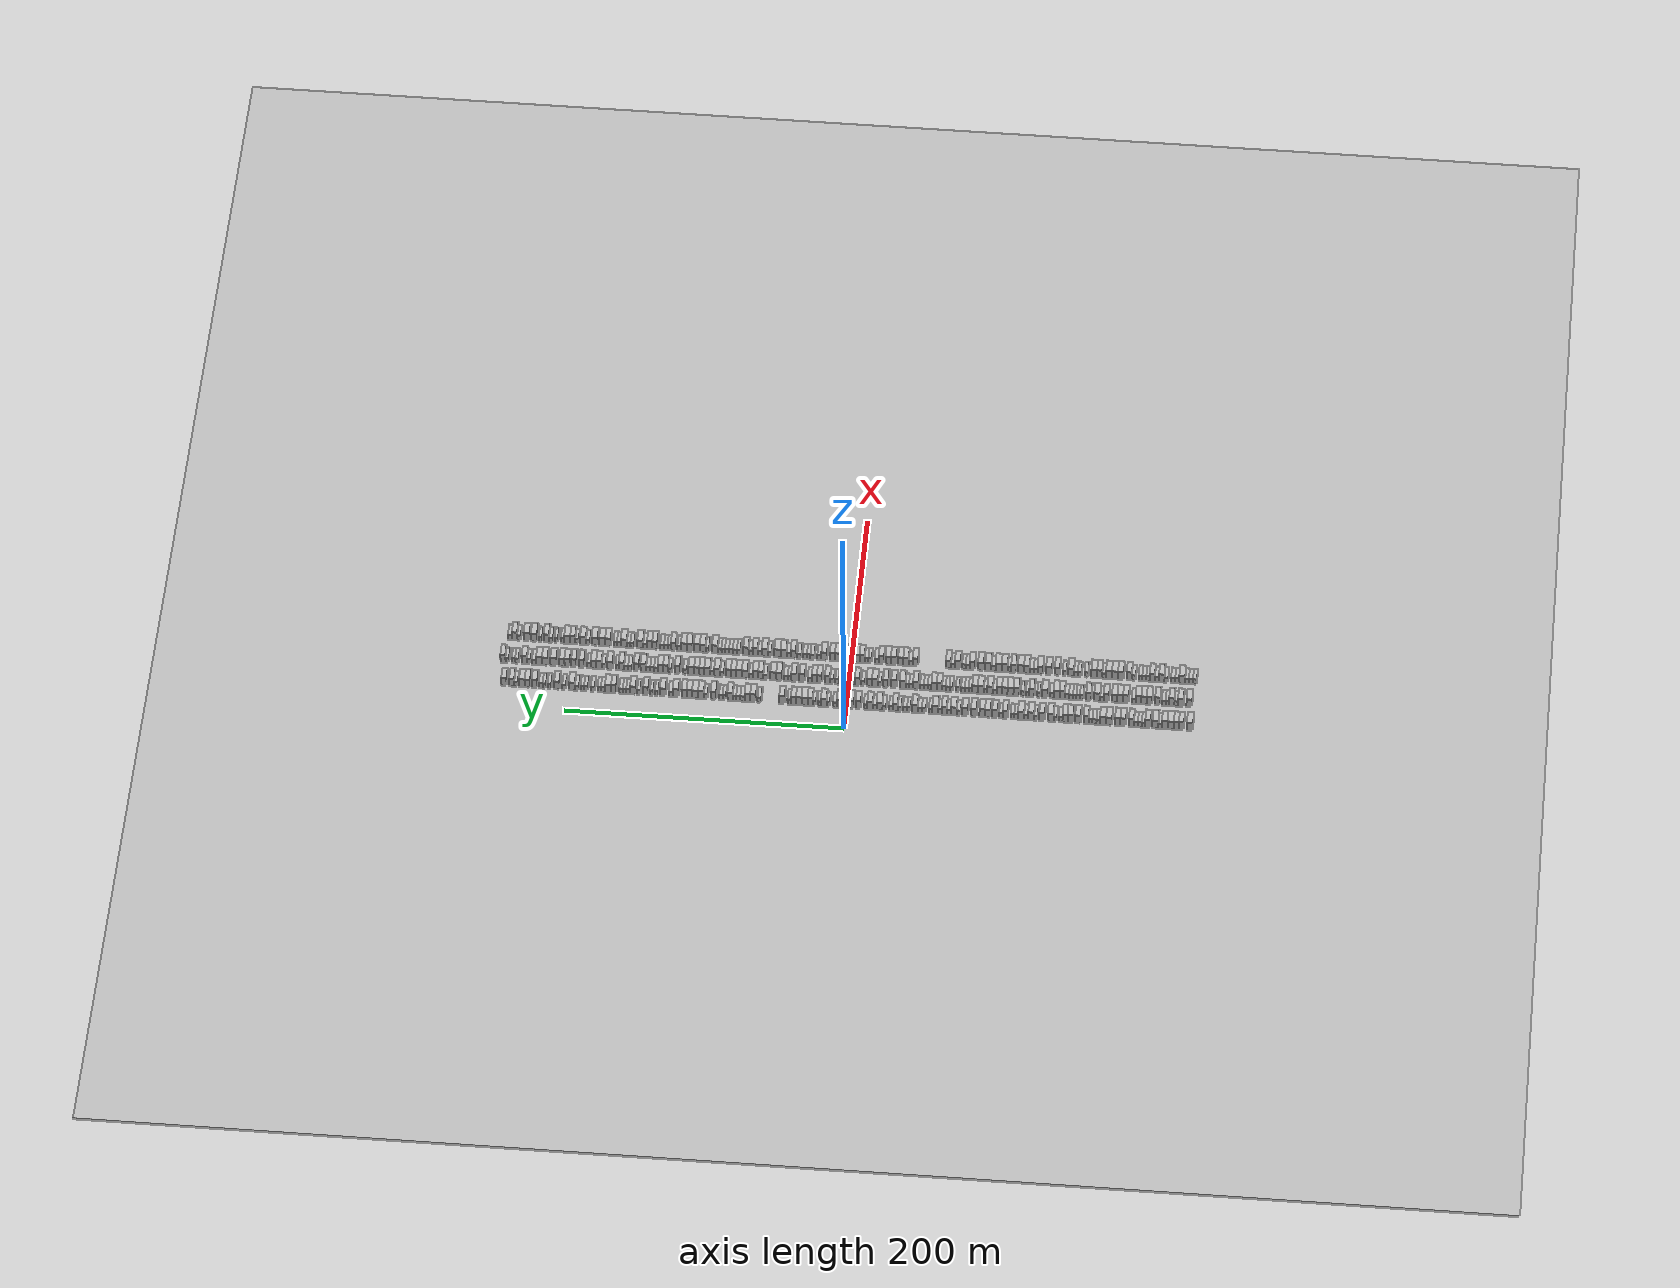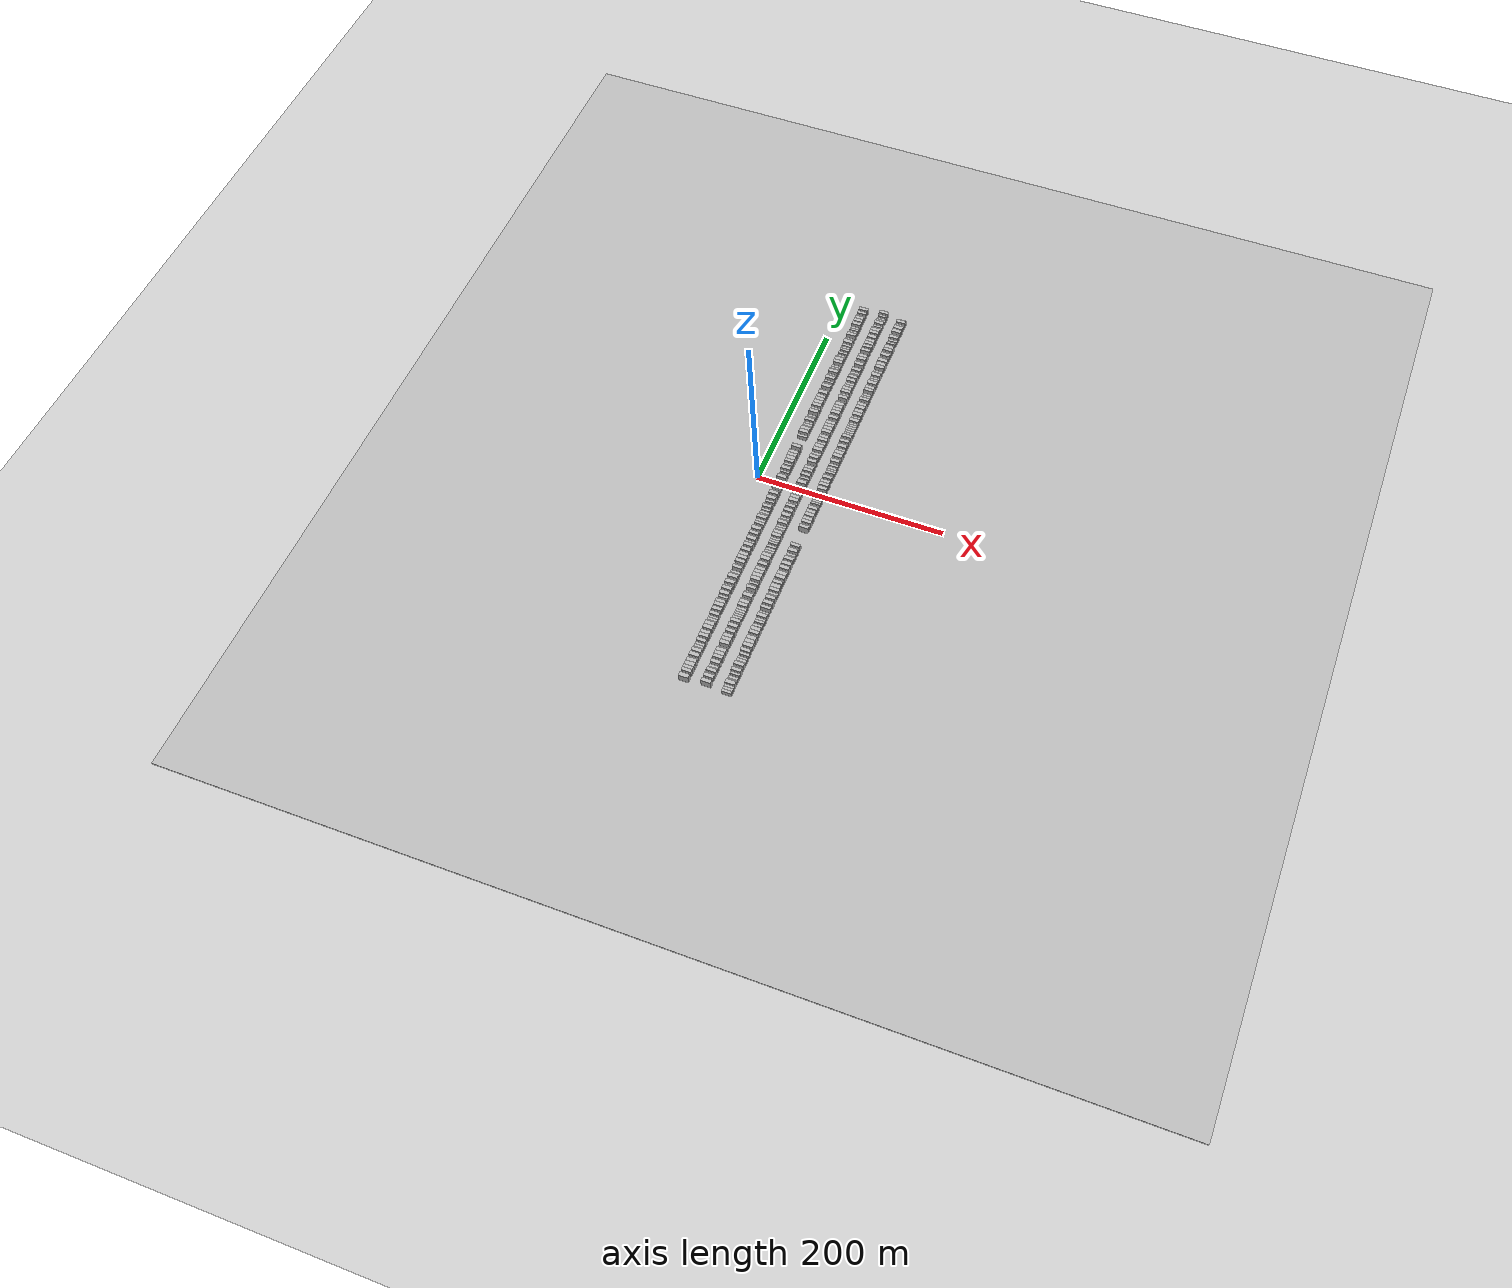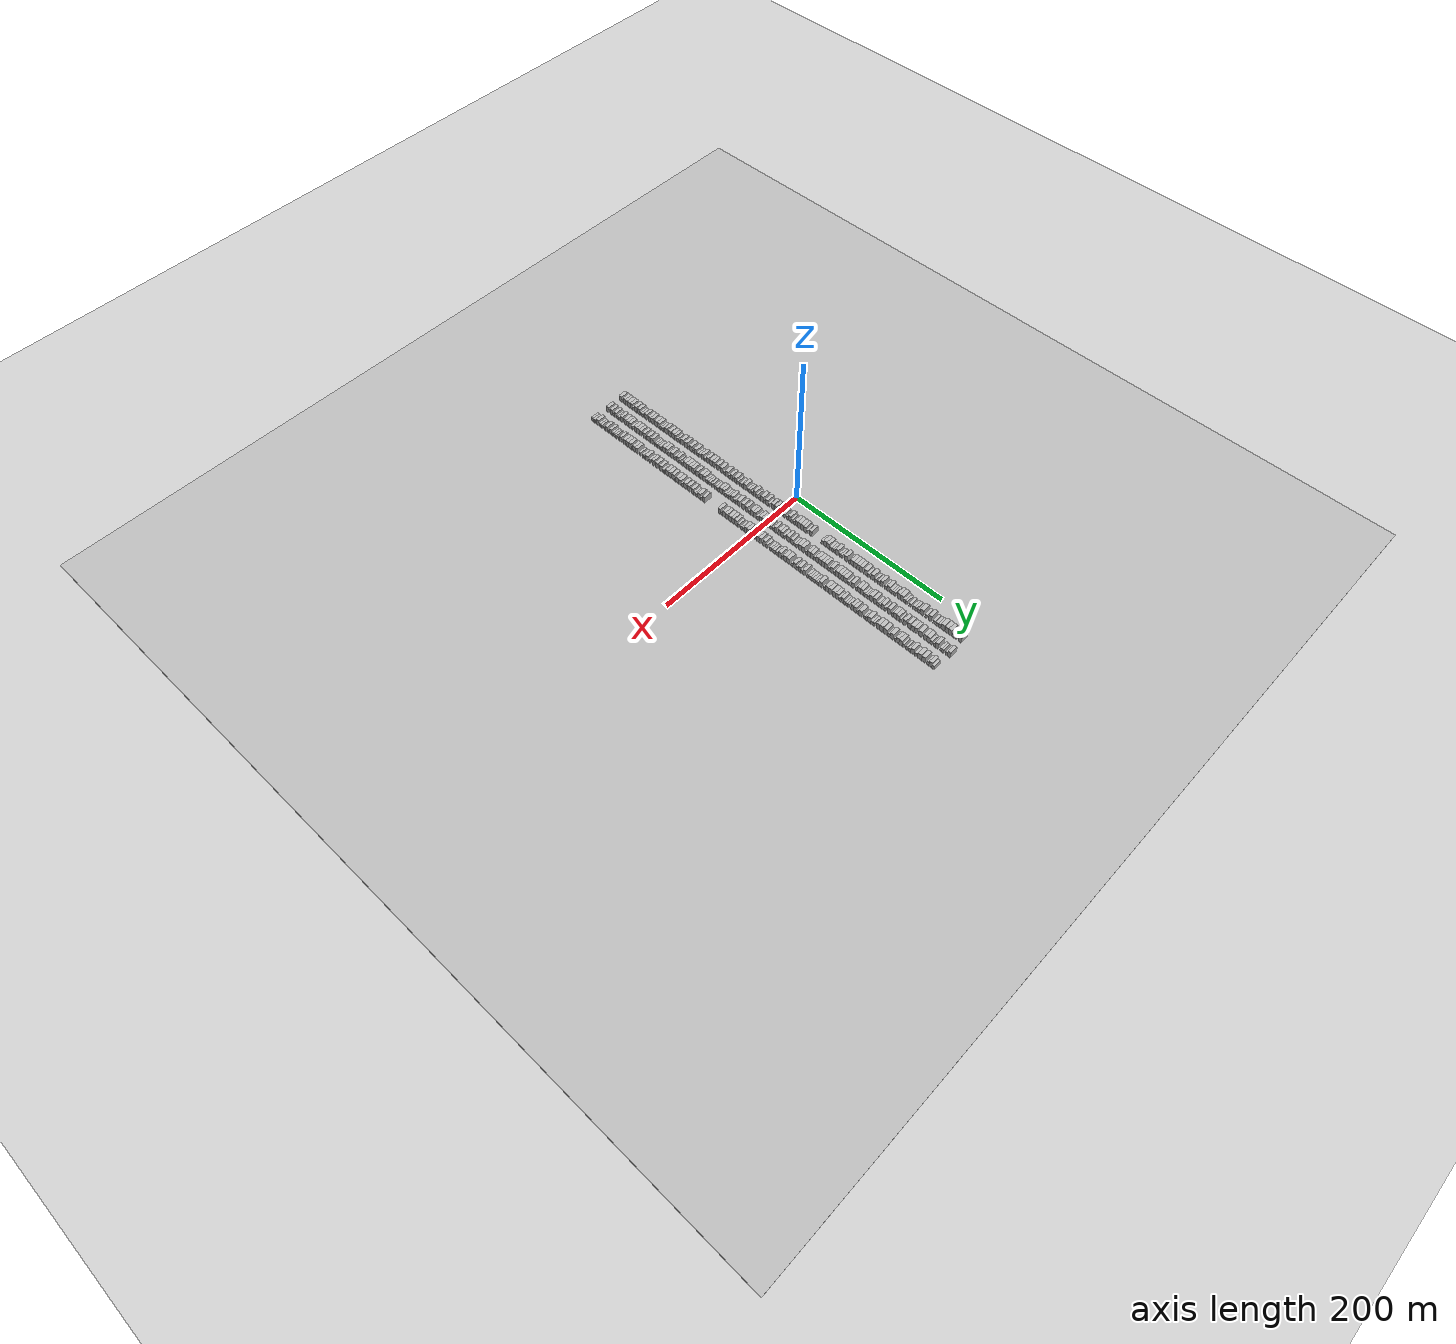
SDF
<?xml version="1.0" encoding="utf-8"?>

<sdf version="1.6">

   <world name="default">

      <gui fullscreen="0">

         <camera name="user_camera">

            <pose>-15 0 4.57585 0 0 0</pose>

            <view_controller>orbit</view_controller>

         </camera>

      </gui>

      <scene>

         <sky>

           <clouds>

             <speed>12</speed>

           </clouds>

         </sky>

         <ambient>0.4 0.4 0.4 1</ambient>

         <background>0.7 0.7 0.7 1</background>

         <shadows>1</shadows>

      </scene>

      <gravity>0 0 -9.8066</gravity>

      <magnetic_field>6e-06 2.3e-05 -4.2e-05</magnetic_field>

      <physics default="0" name="default_physics" type="ode">

         <ode>

            <solver>

               <type>quick</type>

               <iters>10</iters>

               <sor>1.0</sor>

               <use_dynamic_moi_rescaling>0</use_dynamic_moi_rescaling>

            </solver>

            <constraints>

               <cfm>0</cfm>

               <erp>0.2</erp>

               <contact_max_correcting_vel>100</contact_max_correcting_vel>

               <contact_surface_layer>0.001</contact_surface_layer>

            </constraints>

         </ode>

         <max_step_size>0.004</max_step_size>

         <real_time_factor>1</real_time_factor>

         <real_time_update_rate>250</real_time_update_rate>

      </physics>

      <light name="sun" type="directional">

         <cast_shadows>1</cast_shadows>

         <pose>0 0 10 0 0 0</pose>

         <diffuse>0.8 0.8 0.8 1</diffuse>

         <specular>0.2 0.2 0.2 1</specular>

         <attenuation>

            <range>1000</range>

            <constant>0.9</constant>

            <linear>0.01</linear>

            <quadratic>0.001</quadratic>

         </attenuation>

         <direction>-0.5 0.1 -0.9</direction>

      </light>

      <include>

         <name>ground_plane_1</name>

         <uri>model://HANNAS_ground_plane</uri>

         <pose>0 0 0  0 0 0</pose>

      </include>

      <include>

         <name>ground_plane_2</name>

         <uri>model://HANNAS_ground_plane</uri>

         <pose>100 0 0  0 0 0</pose>

      </include>

      <model name="building_1">

         <static>1</static>

         <pose frame="">25.0000 -245.7644 0 0.000000 0.000000 0.000000</pose>

         <link name="link">

            <pose frame="">0 0 4.50 0 0 0</pose>

            <collision name="collision">

               <geometry>

                  <box>

                     <size>10.0000 4.4713 9.0000</size>

                  </box>

               </geometry>

               <max_contacts>10</max_contacts>

               <surface>

                  <contact>

                     <ode/>

                  </contact>

                  <bounce/>

                  <friction>

                     <torsional>

                        <ode/>

                     </torsional>

                     <ode/>

                  </friction>

               </surface>

            </collision>

            <visual name="visual">

               <cast_shadows>0</cast_shadows>

               <geometry>

                  <box>

                     <size>10.0000 4.4713 9.0000</size>

                  </box>

               </geometry>

               <material>

                  <script>

                     <uri>model://HANNAS_wall/materials/scripts</uri>

                     <uri>model://HANNAS_wall/materials/textures</uri>

                     <name>vrc/HANNAS_wall</name>

                  </script>

               </material>

            </visual>

            <self_collide>0</self_collide>

            <enable_wind>0</enable_wind>

            <kinematic>0</kinematic>

         </link>

      </model>

      <model name="building_2">

         <static>1</static>

         <pose frame="">25.0000 -239.6959 0 0.000000 0.000000 0.000000</pose>

         <link name="link">

            <pose frame="">0 0 4.50 0 0 0</pose>

            <collision name="collision">

               <geometry>

                  <box>

                     <size>10.0000 3.6656 9.0000</size>

                  </box>

               </geometry>

               <max_contacts>10</max_contacts>

               <surface>

                  <contact>

                     <ode/>

                  </contact>

                  <bounce/>

                  <friction>

                     <torsional>

                        <ode/>

                     </torsional>

                     <ode/>

                  </friction>

               </surface>

            </collision>

            <visual name="visual">

               <cast_shadows>0</cast_shadows>

               <geometry>

                  <box>

                     <size>10.0000 3.6656 9.0000</size>

                  </box>

               </geometry>

               <material>

                  <script>

                     <uri>model://HANNAS_wall/materials/scripts</uri>

                     <uri>model://HANNAS_wall/materials/textures</uri>

                     <name>vrc/HANNAS_wall</name>

                  </script>

               </material>

            </visual>

            <self_collide>0</self_collide>

            <enable_wind>0</enable_wind>

            <kinematic>0</kinematic>

         </link>

      </model>

      <model name="building_3">

         <static>1</static>

         <pose frame="">25.0000 -236.0522 0 0.000000 0.000000 0.000000</pose>

         <link name="link">

            <pose frame="">0 0 4.50 0 0 0</pose>

            <collision name="collision">

               <geometry>

                  <box>

                     <size>10.0000 3.6218 9.0000</size>

                  </box>

               </geometry>

               <max_contacts>10</max_contacts>

               <surface>

                  <contact>

                     <ode/>

                  </contact>

                  <bounce/>

                  <friction>

                     <torsional>

                        <ode/>

                     </torsional>

                     <ode/>

                  </friction>

               </surface>

            </collision>

            <visual name="visual">

               <cast_shadows>0</cast_shadows>

               <geometry>

                  <box>

                     <size>10.0000 3.6218 9.0000</size>

                  </box>

               </geometry>

               <material>

                  <script>

                     <uri>model://HANNAS_wall/materials/scripts</uri>

                     <uri>model://HANNAS_wall/materials/textures</uri>

                     <name>vrc/HANNAS_wall</name>

                  </script>

               </material>

            </visual>

            <self_collide>0</self_collide>

            <enable_wind>0</enable_wind>

            <kinematic>0</kinematic>

         </link>

      </model>

      <model name="building_4">

         <static>1</static>

         <pose frame="">25.0000 -232.0226 0 0.000000 0.000000 0.000000</pose>

         <link name="link">

            <pose frame="">0 0 4.50 0 0 0</pose>

            <collision name="collision">

               <geometry>

                  <box>

                     <size>10.0000 4.4375 9.0000</size>

                  </box>

               </geometry>

               <max_contacts>10</max_contacts>

               <surface>

                  <contact>

                     <ode/>

                  </contact>

                  <bounce/>

                  <friction>

                     <torsional>

                        <ode/>

                     </torsional>

                     <ode/>

                  </friction>

               </surface>

            </collision>

            <visual name="visual">

               <cast_shadows>0</cast_shadows>

               <geometry>

                  <box>

                     <size>10.0000 4.4375 9.0000</size>

                  </box>

               </geometry>

               <material>

                  <script>

                     <uri>model://HANNAS_wall/materials/scripts</uri>

                     <uri>model://HANNAS_wall/materials/textures</uri>

                     <name>vrc/HANNAS_wall</name>

                  </script>

               </material>

            </visual>

            <self_collide>0</self_collide>

            <enable_wind>0</enable_wind>

            <kinematic>0</kinematic>

         </link>

      </model>

      <model name="building_5">

         <static>1</static>

         <pose frame="">25.0000 -227.7688 0 0.000000 0.000000 0.000000</pose>

         <link name="link">

            <pose frame="">0 0 4.50 0 0 0</pose>

            <collision name="collision">

               <geometry>

                  <box>

                     <size>10.0000 4.0701 9.0000</size>

                  </box>

               </geometry>

               <max_contacts>10</max_contacts>

               <surface>

                  <contact>

                     <ode/>

                  </contact>

                  <bounce/>

                  <friction>

                     <torsional>

                        <ode/>

                     </torsional>

                     <ode/>

                  </friction>

               </surface>

            </collision>

            <visual name="visual">

               <cast_shadows>0</cast_shadows>

               <geometry>

                  <box>

                     <size>10.0000 4.0701 9.0000</size>

                  </box>

               </geometry>

               <material>

                  <script>

                     <uri>model://HANNAS_wall/materials/scripts</uri>

                     <uri>model://HANNAS_wall/materials/textures</uri>

                     <name>vrc/HANNAS_wall</name>

                  </script>

               </material>

            </visual>

            <self_collide>0</self_collide>

            <enable_wind>0</enable_wind>

            <kinematic>0</kinematic>

         </link>

      </model>

      <model name="building_6">

         <static>1</static>

         <pose frame="">25.0000 -224.5010 0 0.000000 0.000000 0.000000</pose>

         <link name="link">

            <pose frame="">0 0 3.00 0 0 0</pose>

            <collision name="collision">

               <geometry>

                  <box>

                     <size>10.0000 2.4654 6.0000</size>

                  </box>

               </geometry>

               <max_contacts>10</max_contacts>

               <surface>

                  <contact>

                     <ode/>

                  </contact>

                  <bounce/>

                  <friction>

                     <torsional>

                        <ode/>

                     </torsional>

                     <ode/>

                  </friction>

               </surface>

            </collision>

            <visual name="visual">

               <cast_shadows>0</cast_shadows>

               <geometry>

                  <box>

                     <size>10.0000 2.4654 6.0000</size>

                  </box>

               </geometry>

               <material>

                  <script>

                     <uri>model://HANNAS_wall/materials/scripts</uri>

                     <uri>model://HANNAS_wall/materials/textures</uri>

                     <name>vrc/HANNAS_wall</name>

                  </script>

               </material>

            </visual>

            <self_collide>0</self_collide>

            <enable_wind>0</enable_wind>

            <kinematic>0</kinematic>

         </link>

      </model>

      <model name="building_7">

         <static>1</static>

         <pose frame="">25.0000 -221.0749 0 0.000000 0.000000 0.000000</pose>

         <link name="link">

            <pose frame="">0 0 4.50 0 0 0</pose>

            <collision name="collision">

               <geometry>

                  <box>

                     <size>10.0000 4.3868 9.0000</size>

                  </box>

               </geometry>

               <max_contacts>10</max_contacts>

               <surface>

                  <contact>

                     <ode/>

                  </contact>

                  <bounce/>

                  <friction>

                     <torsional>

                        <ode/>

                     </torsional>

                     <ode/>

                  </friction>

               </surface>

            </collision>

            <visual name="visual">

               <cast_shadows>0</cast_shadows>

               <geometry>

                  <box>

                     <size>10.0000 4.3868 9.0000</size>

                  </box>

               </geometry>

               <material>

                  <script>

                     <uri>model://HANNAS_wall/materials/scripts</uri>

                     <uri>model://HANNAS_wall/materials/textures</uri>

                     <name>vrc/HANNAS_wall</name>

                  </script>

               </material>

            </visual>

            <self_collide>0</self_collide>

            <enable_wind>0</enable_wind>

            <kinematic>0</kinematic>

         </link>

      </model>

      <model name="building_8">

         <static>1</static>

         <pose frame="">25.0000 -215.8531 0 0.000000 0.000000 0.000000</pose>

         <link name="link">

            <pose frame="">0 0 4.50 0 0 0</pose>

            <collision name="collision">

               <geometry>

                  <box>

                     <size>10.0000 4.0567 9.0000</size>

                  </box>

               </geometry>

               <max_contacts>10</max_contacts>

               <surface>

                  <contact>

                     <ode/>

                  </contact>

                  <bounce/>

                  <friction>

                     <torsional>

                        <ode/>

                     </torsional>

                     <ode/>

                  </friction>

               </surface>

            </collision>

            <visual name="visual">

               <cast_shadows>0</cast_shadows>

               <geometry>

                  <box>

                     <size>10.0000 4.0567 9.0000</size>

                  </box>

               </geometry>

               <material>

                  <script>

                     <uri>model://HANNAS_wall/materials/scripts</uri>

                     <uri>model://HANNAS_wall/materials/textures</uri>

                     <name>vrc/HANNAS_wall</name>

                  </script>

               </material>

            </visual>

            <self_collide>0</self_collide>

            <enable_wind>0</enable_wind>

            <kinematic>0</kinematic>

         </link>

      </model>

      <model name="building_9">

         <static>1</static>

         <pose frame="">25.0000 -212.6111 0 0.000000 0.000000 0.000000</pose>

         <link name="link">

            <pose frame="">0 0 3.00 0 0 0</pose>

            <collision name="collision">

               <geometry>

                  <box>

                     <size>10.0000 2.4273 6.0000</size>

                  </box>

               </geometry>

               <max_contacts>10</max_contacts>

               <surface>

                  <contact>

                     <ode/>

                  </contact>

                  <bounce/>

                  <friction>

                     <torsional>

                        <ode/>

                     </torsional>

                     <ode/>

                  </friction>

               </surface>

            </collision>

            <visual name="visual">

               <cast_shadows>0</cast_shadows>

               <geometry>

                  <box>

                     <size>10.0000 2.4273 6.0000</size>

                  </box>

               </geometry>

               <material>

                  <script>

                     <uri>model://HANNAS_wall/materials/scripts</uri>

                     <uri>model://HANNAS_wall/materials/textures</uri>

                     <name>vrc/HANNAS_wall</name>

                  </script>

               </material>

            </visual>

            <self_collide>0</self_collide>

            <enable_wind>0</enable_wind>

            <kinematic>0</kinematic>

         </link>

      </model>

      <model name="building_10">

         <static>1</static>

         <pose frame="">25.0000 -210.0040 0 0.000000 0.000000 0.000000</pose>

         <link name="link">

            <pose frame="">0 0 3.00 0 0 0</pose>

            <collision name="collision">

               <geometry>

                  <box>

                     <size>10.0000 2.7869 6.0000</size>

                  </box>

               </geometry>

               <max_contacts>10</max_contacts>

               <surface>

                  <contact>

                     <ode/>

                  </contact>

                  <bounce/>

                  <friction>

                     <torsional>

                        <ode/>

                     </torsional>

                     <ode/>

                  </friction>

               </surface>

            </collision>

            <visual name="visual">

               <cast_shadows>0</cast_shadows>

               <geometry>

                  <box>

                     <size>10.0000 2.7869 6.0000</size>

                  </box>

               </geometry>

               <material>

                  <script>

                     <uri>model://HANNAS_wall/materials/scripts</uri>

                     <uri>model://HANNAS_wall/materials/textures</uri>

                     <name>vrc/HANNAS_wall</name>

                  </script>

               </material>

            </visual>

            <self_collide>0</self_collide>

            <enable_wind>0</enable_wind>

            <kinematic>0</kinematic>

         </link>

      </model>

      <model name="building_11">

         <static>1</static>

         <pose frame="">25.0000 -207.1946 0 0.000000 0.000000 0.000000</pose>

         <link name="link">

            <pose frame="">0 0 3.00 0 0 0</pose>

            <collision name="collision">

               <geometry>

                  <box>

                     <size>10.0000 2.8318 6.0000</size>

                  </box>

               </geometry>

               <max_contacts>10</max_contacts>

               <surface>

                  <contact>

                     <ode/>

                  </contact>

                  <bounce/>

                  <friction>

                     <torsional>

                        <ode/>

                     </torsional>

                     <ode/>

                  </friction>

               </surface>

            </collision>

            <visual name="visual">

               <cast_shadows>0</cast_shadows>

               <geometry>

                  <box>

                     <size>10.0000 2.8318 6.0000</size>

                  </box>

               </geometry>

               <material>

                  <script>

                     <uri>model://HANNAS_wall/materials/scripts</uri>

                     <uri>model://HANNAS_wall/materials/textures</uri>

                     <name>vrc/HANNAS_wall</name>

                  </script>

               </material>

            </visual>

            <self_collide>0</self_collide>

            <enable_wind>0</enable_wind>

            <kinematic>0</kinematic>

         </link>

      </model>

      <model name="building_12">

         <static>1</static>

         <pose frame="">25.0000 -203.9349 0 0.000000 0.000000 0.000000</pose>

         <link name="link">

            <pose frame="">0 0 4.50 0 0 0</pose>

            <collision name="collision">

               <geometry>

                  <box>

                     <size>10.0000 3.6875 9.0000</size>

                  </box>

               </geometry>

               <max_contacts>10</max_contacts>

               <surface>

                  <contact>

                     <ode/>

                  </contact>

                  <bounce/>

                  <friction>

                     <torsional>

                        <ode/>

                     </torsional>

                     <ode/>

                  </friction>

               </surface>

            </collision>

            <visual name="visual">

               <cast_shadows>0</cast_shadows>

               <geometry>

                  <box>

                     <size>10.0000 3.6875 9.0000</size>

                  </box>

               </geometry>

               <material>

                  <script>

                     <uri>model://HANNAS_wall/materials/scripts</uri>

                     <uri>model://HANNAS_wall/materials/textures</uri>

                     <name>vrc/HANNAS_wall</name>

                  </script>

               </material>

            </visual>

            <self_collide>0</self_collide>

            <enable_wind>0</enable_wind>

            <kinematic>0</kinematic>

         </link>

      </model>

      <model name="building_13">

         <static>1</static>

         <pose frame="">25.0000 -198.0447 0 0.000000 0.000000 0.000000</pose>

         <link name="link">

            <pose frame="">0 0 4.50 0 0 0</pose>

            <collision name="collision">

               <geometry>

                  <box>

                     <size>10.0000 4.0929 9.0000</size>

                  </box>

               </geometry>

               <max_contacts>10</max_contacts>

               <surface>

                  <contact>

                     <ode/>

                  </contact>

                  <bounce/>

                  <friction>

                     <torsional>

                        <ode/>

                     </torsional>

                     <ode/>

                  </friction>

               </surface>

            </collision>

            <visual name="visual">

               <cast_shadows>0</cast_shadows>

               <geometry>

                  <box>

                     <size>10.0000 4.0929 9.0000</size>

                  </box>

               </geometry>

               <material>

                  <script>

                     <uri>model://HANNAS_wall/materials/scripts</uri>

                     <uri>model://HANNAS_wall/materials/textures</uri>

                     <name>vrc/HANNAS_wall</name>

                  </script>

               </material>

            </visual>

            <self_collide>0</self_collide>

            <enable_wind>0</enable_wind>

            <kinematic>0</kinematic>

         </link>

      </model>

      <model name="building_14">

         <static>1</static>

         <pose frame="">25.0000 -194.0891 0 0.000000 0.000000 0.000000</pose>

         <link name="link">

            <pose frame="">0 0 4.50 0 0 0</pose>

            <collision name="collision">

               <geometry>

                  <box>

                     <size>10.0000 3.8181 9.0000</size>

                  </box>

               </geometry>

               <max_contacts>10</max_contacts>

               <surface>

                  <contact>

                     <ode/>

                  </contact>

                  <bounce/>

                  <friction>

                     <torsional>

                        <ode/>

                     </torsional>

                     <ode/>

                  </friction>

               </surface>

            </collision>

            <visual name="visual">

               <cast_shadows>0</cast_shadows>

               <geometry>

                  <box>

                     <size>10.0000 3.8181 9.0000</size>

                  </box>

               </geometry>

               <material>

                  <script>

                     <uri>model://HANNAS_wall/materials/scripts</uri>

                     <uri>model://HANNAS_wall/materials/textures</uri>

                     <name>vrc/HANNAS_wall</name>

                  </script>

               </material>

            </visual>

            <self_collide>0</self_collide>

            <enable_wind>0</enable_wind>

            <kinematic>0</kinematic>

         </link>

      </model>

      <model name="building_15">

         <static>1</static>

         <pose frame="">25.0000 -187.9881 0 0.000000 0.000000 0.000000</pose>

         <link name="link">

            <pose frame="">0 0 4.50 0 0 0</pose>

            <collision name="collision">

               <geometry>

                  <box>

                     <size>10.0000 4.3840 9.0000</size>

                  </box>

               </geometry>

               <max_contacts>10</max_contacts>

               <surface>

                  <contact>

                     <ode/>

                  </contact>

                  <bounce/>

                  <friction>

                     <torsional>

                        <ode/>

                     </torsional>

                     <ode/>

                  </friction>

               </surface>

            </collision>

            <visual name="visual">

               <cast_shadows>0</cast_shadows>

               <geometry>

                  <box>

                     <size>10.0000 4.3840 9.0000</size>

                  </box>

               </geometry>

               <material>

                  <script>

                     <uri>model://HANNAS_wall/materials/scripts</uri>

                     <uri>model://HANNAS_wall/materials/textures</uri>

                     <name>vrc/HANNAS_wall</name>

                  </script>

               </material>

            </visual>

            <self_collide>0</self_collide>

            <enable_wind>0</enable_wind>

            <kinematic>0</kinematic>

         </link>

      </model>

      <model name="building_16">

         <static>1</static>

         <pose frame="">25.0000 -183.6139 0 0.000000 0.000000 0.000000</pose>

         <link name="link">

            <pose frame="">0 0 4.50 0 0 0</pose>

            <collision name="collision">

               <geometry>

                  <box>

                     <size>10.0000 4.3643 9.0000</size>

                  </box>

               </geometry>

               <max_contacts>10</max_contacts>

               <surface>

                  <contact>

                     <ode/>

                  </contact>

                  <bounce/>

                  <friction>

                     <torsional>

                        <ode/>

                     </torsional>

                     <ode/>

                  </friction>

               </surface>

            </collision>

            <visual name="visual">

               <cast_shadows>0</cast_shadows>

               <geometry>

                  <box>

                     <size>10.0000 4.3643 9.0000</size>

                  </box>

               </geometry>

               <material>

                  <script>

                     <uri>model://HANNAS_wall/materials/scripts</uri>

                     <uri>model://HANNAS_wall/materials/textures</uri>

                     <name>vrc/HANNAS_wall</name>

                  </script>

               </material>

            </visual>

            <self_collide>0</self_collide>

            <enable_wind>0</enable_wind>

            <kinematic>0</kinematic>

         </link>

      </model>

      <model name="building_17">

         <static>1</static>

         <pose frame="">25.0000 -180.2141 0 0.000000 0.000000 0.000000</pose>

         <link name="link">

            <pose frame="">0 0 3.00 0 0 0</pose>

            <collision name="collision">

               <geometry>

                  <box>

                     <size>10.0000 2.4354 6.0000</size>

                  </box>

               </geometry>

               <max_contacts>10</max_contacts>

               <surface>

                  <contact>

                     <ode/>

                  </contact>

                  <bounce/>

                  <friction>

                     <torsional>

                        <ode/>

                     </torsional>

                     <ode/>

                  </friction>

               </surface>

            </collision>

            <visual name="visual">

               <cast_shadows>0</cast_shadows>

               <geometry>

                  <box>

                     <size>10.0000 2.4354 6.0000</size>

                  </box>

               </geometry>

               <material>

                  <script>

                     <uri>model://HANNAS_wall/materials/scripts</uri>

                     <uri>model://HANNAS_wall/materials/textures</uri>

                     <name>vrc/HANNAS_wall</name>

                  </script>

               </material>

            </visual>

            <self_collide>0</self_collide>

            <enable_wind>0</enable_wind>

            <kinematic>0</kinematic>

         </link>

      </model>

      <model name="building_18">

         <static>1</static>

         <pose frame="">25.0000 -177.5142 0 0.000000 0.000000 0.000000</pose>

         <link name="link">

            <pose frame="">0 0 3.00 0 0 0</pose>

            <collision name="collision">

               <geometry>

                  <box>

                     <size>10.0000 2.9643 6.0000</size>

                  </box>

               </geometry>

               <max_contacts>10</max_contacts>

               <surface>

                  <contact>

                     <ode/>

                  </contact>

                  <bounce/>

                  <friction>

                     <torsional>

                        <ode/>

                     </torsional>

                     <ode/>

                  </friction>

               </surface>

            </collision>

            <visual name="visual">

               <cast_shadows>0</cast_shadows>

               <geometry>

                  <box>

                     <size>10.0000 2.9643 6.0000</size>

                  </box>

               </geometry>

               <material>

                  <script>

                     <uri>model://HANNAS_wall/materials/scripts</uri>

                     <uri>model://HANNAS_wall/materials/textures</uri>

                     <name>vrc/HANNAS_wall</name>

                  </script>

               </material>

            </visual>

            <self_collide>0</self_collide>

            <enable_wind>0</enable_wind>

            <kinematic>0</kinematic>

         </link>

      </model>

      <model name="building_19">

         <static>1</static>

         <pose frame="">25.0000 -174.7505 0 0.000000 0.000000 0.000000</pose>

         <link name="link">

            <pose frame="">0 0 3.00 0 0 0</pose>

            <collision name="collision">

               <geometry>

                  <box>

                     <size>10.0000 2.5631 6.0000</size>

                  </box>

               </geometry>

               <max_contacts>10</max_contacts>

               <surface>

                  <contact>

                     <ode/>

                  </contact>

                  <bounce/>

                  <friction>

                     <torsional>

                        <ode/>

                     </torsional>

                     <ode/>

                  </friction>

               </surface>

            </collision>

            <visual name="visual">

               <cast_shadows>0</cast_shadows>

               <geometry>

                  <box>

                     <size>10.0000 2.5631 6.0000</size>

                  </box>

               </geometry>

               <material>

                  <script>

                     <uri>model://HANNAS_wall/materials/scripts</uri>

                     <uri>model://HANNAS_wall/materials/textures</uri>

                     <name>vrc/HANNAS_wall</name>

                  </script>

               </material>

            </visual>

            <self_collide>0</self_collide>

            <enable_wind>0</enable_wind>

            <kinematic>0</kinematic>

         </link>

      </model>

      <model name="building_20">

         <static>1</static>

         <pose frame="">25.0000 -171.6184 0 0.000000 0.000000 0.000000</pose>

         <link name="link">

            <pose frame="">0 0 4.50 0 0 0</pose>

            <collision name="collision">

               <geometry>

                  <box>

                     <size>10.0000 3.7011 9.0000</size>

                  </box>

               </geometry>

               <max_contacts>10</max_contacts>

               <surface>

                  <contact>

                     <ode/>

                  </contact>

                  <bounce/>

                  <friction>

                     <torsional>

                        <ode/>

                     </torsional>

                     <ode/>

                  </friction>

               </surface>

            </collision>

            <visual name="visual">

               <cast_shadows>0</cast_shadows>

               <geometry>

                  <box>

                     <size>10.0000 3.7011 9.0000</size>

                  </box>

               </geometry>

               <material>

                  <script>

                     <uri>model://HANNAS_wall/materials/scripts</uri>

                     <uri>model://HANNAS_wall/materials/textures</uri>

                     <name>vrc/HANNAS_wall</name>

                  </script>

               </material>

            </visual>

            <self_collide>0</self_collide>

            <enable_wind>0</enable_wind>

            <kinematic>0</kinematic>

         </link>

      </model>

      <model name="building_21">

         <static>1</static>

         <pose frame="">25.0000 -165.6865 0 0.000000 0.000000 0.000000</pose>

         <link name="link">

            <pose frame="">0 0 4.50 0 0 0</pose>

            <collision name="collision">

               <geometry>

                  <box>

                     <size>10.0000 4.1626 9.0000</size>

                  </box>

               </geometry>

               <max_contacts>10</max_contacts>

               <surface>

                  <contact>

                     <ode/>

                  </contact>

                  <bounce/>

                  <friction>

                     <torsional>

                        <ode/>

                     </torsional>

                     <ode/>

                  </friction>

               </surface>

            </collision>

            <visual name="visual">

               <cast_shadows>0</cast_shadows>

               <geometry>

                  <box>

                     <size>10.0000 4.1626 9.0000</size>

                  </box>

               </geometry>

               <material>

                  <script>

                     <uri>model://HANNAS_wall/materials/scripts</uri>

                     <uri>model://HANNAS_wall/materials/textures</uri>

                     <name>vrc/HANNAS_wall</name>

                  </script>

               </material>

            </visual>

            <self_collide>0</self_collide>

            <enable_wind>0</enable_wind>

            <kinematic>0</kinematic>

         </link>

      </model>

      <model name="building_22">

         <static>1</static>

         <pose frame="">25.0000 -160.4415 0 0.000000 0.000000 0.000000</pose>

         <link name="link">

            <pose frame="">0 0 4.50 0 0 0</pose>

            <collision name="collision">

               <geometry>

                  <box>

                     <size>10.0000 4.3274 9.0000</size>

                  </box>

               </geometry>

               <max_contacts>10</max_contacts>

               <surface>

                  <contact>

                     <ode/>

                  </contact>

                  <bounce/>

                  <friction>

                     <torsional>

                        <ode/>

                     </torsional>

                     <ode/>

                  </friction>

               </surface>

            </collision>

            <visual name="visual">

               <cast_shadows>0</cast_shadows>

               <geometry>

                  <box>

                     <size>10.0000 4.3274 9.0000</size>

                  </box>

               </geometry>

               <material>

                  <script>

                     <uri>model://HANNAS_wall/materials/scripts</uri>

                     <uri>model://HANNAS_wall/materials/textures</uri>

                     <name>vrc/HANNAS_wall</name>

                  </script>

               </material>

            </visual>

            <self_collide>0</self_collide>

            <enable_wind>0</enable_wind>

            <kinematic>0</kinematic>

         </link>

      </model>

      <model name="building_23">

         <static>1</static>

         <pose frame="">25.0000 -156.4772 0 0.000000 0.000000 0.000000</pose>

         <link name="link">

            <pose frame="">0 0 4.50 0 0 0</pose>

            <collision name="collision">

               <geometry>

                  <box>

                     <size>10.0000 3.6012 9.0000</size>

                  </box>

               </geometry>

               <max_contacts>10</max_contacts>

               <surface>

                  <contact>

                     <ode/>

                  </contact>

                  <bounce/>

                  <friction>

                     <torsional>

                        <ode/>

                     </torsional>

                     <ode/>

                  </friction>

               </surface>

            </collision>

            <visual name="visual">

               <cast_shadows>0</cast_shadows>

               <geometry>

                  <box>

                     <size>10.0000 3.6012 9.0000</size>

                  </box>

               </geometry>

               <material>

                  <script>

                     <uri>model://HANNAS_wall/materials/scripts</uri>

                     <uri>model://HANNAS_wall/materials/textures</uri>

                     <name>vrc/HANNAS_wall</name>

                  </script>

               </material>

            </visual>

            <self_collide>0</self_collide>

            <enable_wind>0</enable_wind>

            <kinematic>0</kinematic>

         </link>

      </model>

      <model name="building_24">

         <static>1</static>

         <pose frame="">25.0000 -153.3023 0 0.000000 0.000000 0.000000</pose>

         <link name="link">

            <pose frame="">0 0 3.00 0 0 0</pose>

            <collision name="collision">

               <geometry>

                  <box>

                     <size>10.0000 2.7484 6.0000</size>

                  </box>

               </geometry>

               <max_contacts>10</max_contacts>

               <surface>

                  <contact>

                     <ode/>

                  </contact>

                  <bounce/>

                  <friction>

                     <torsional>

                        <ode/>

                     </torsional>

                     <ode/>

                  </friction>

               </surface>

            </collision>

            <visual name="visual">

               <cast_shadows>0</cast_shadows>

               <geometry>

                  <box>

                     <size>10.0000 2.7484 6.0000</size>

                  </box>

               </geometry>

               <material>

                  <script>

                     <uri>model://HANNAS_wall/materials/scripts</uri>

                     <uri>model://HANNAS_wall/materials/textures</uri>

                     <name>vrc/HANNAS_wall</name>

                  </script>

               </material>

            </visual>

            <self_collide>0</self_collide>

            <enable_wind>0</enable_wind>

            <kinematic>0</kinematic>

         </link>

      </model>

      <model name="building_25">

         <static>1</static>

         <pose frame="">25.0000 -149.6056 0 0.000000 0.000000 0.000000</pose>

         <link name="link">

            <pose frame="">0 0 3.00 0 0 0</pose>

            <collision name="collision">

               <geometry>

                  <box>

                     <size>10.0000 2.6451 6.0000</size>

                  </box>

               </geometry>

               <max_contacts>10</max_contacts>

               <surface>

                  <contact>

                     <ode/>

                  </contact>

                  <bounce/>

                  <friction>

                     <torsional>

                        <ode/>

                     </torsional>

                     <ode/>

                  </friction>

               </surface>

            </collision>

            <visual name="visual">

               <cast_shadows>0</cast_shadows>

               <geometry>

                  <box>

                     <size>10.0000 2.6451 6.0000</size>

                  </box>

               </geometry>

               <material>

                  <script>

                     <uri>model://HANNAS_wall/materials/scripts</uri>

                     <uri>model://HANNAS_wall/materials/textures</uri>

                     <name>vrc/HANNAS_wall</name>

                  </script>

               </material>

            </visual>

            <self_collide>0</self_collide>

            <enable_wind>0</enable_wind>

            <kinematic>0</kinematic>

         </link>

      </model>

      <model name="building_26">

         <static>1</static>

         <pose frame="">25.0000 -146.1416 0 0.000000 0.000000 0.000000</pose>

         <link name="link">

            <pose frame="">0 0 4.50 0 0 0</pose>

            <collision name="collision">

               <geometry>

                  <box>

                     <size>10.0000 4.2828 9.0000</size>

                  </box>

               </geometry>

               <max_contacts>10</max_contacts>

               <surface>

                  <contact>

                     <ode/>

                  </contact>

                  <bounce/>

                  <friction>

                     <torsional>

                        <ode/>

                     </torsional>

                     <ode/>

                  </friction>

               </surface>

            </collision>

            <visual name="visual">

               <cast_shadows>0</cast_shadows>

               <geometry>

                  <box>

                     <size>10.0000 4.2828 9.0000</size>

                  </box>

               </geometry>

               <material>

                  <script>

                     <uri>model://HANNAS_wall/materials/scripts</uri>

                     <uri>model://HANNAS_wall/materials/textures</uri>

                     <name>vrc/HANNAS_wall</name>

                  </script>

               </material>

            </visual>

            <self_collide>0</self_collide>

            <enable_wind>0</enable_wind>

            <kinematic>0</kinematic>

         </link>

      </model>

      <model name="building_27">

         <static>1</static>

         <pose frame="">25.0000 -139.9918 0 0.000000 0.000000 0.000000</pose>

         <link name="link">

            <pose frame="">0 0 4.50 0 0 0</pose>

            <collision name="collision">

               <geometry>

                  <box>

                     <size>10.0000 4.0168 9.0000</size>

                  </box>

               </geometry>

               <max_contacts>10</max_contacts>

               <surface>

                  <contact>

                     <ode/>

                  </contact>

                  <bounce/>

                  <friction>

                     <torsional>

                        <ode/>

                     </torsional>

                     <ode/>

                  </friction>

               </surface>

            </collision>

            <visual name="visual">

               <cast_shadows>0</cast_shadows>

               <geometry>

                  <box>

                     <size>10.0000 4.0168 9.0000</size>

                  </box>

               </geometry>

               <material>

                  <script>

                     <uri>model://HANNAS_wall/materials/scripts</uri>

                     <uri>model://HANNAS_wall/materials/textures</uri>

                     <name>vrc/HANNAS_wall</name>

                  </script>

               </material>

            </visual>

            <self_collide>0</self_collide>

            <enable_wind>0</enable_wind>

            <kinematic>0</kinematic>

         </link>

      </model>

      <model name="building_28">

         <static>1</static>

         <pose frame="">25.0000 -135.7068 0 0.000000 0.000000 0.000000</pose>

         <link name="link">

            <pose frame="">0 0 3.00 0 0 0</pose>

            <collision name="collision">

               <geometry>

                  <box>

                     <size>10.0000 2.5531 6.0000</size>

                  </box>

               </geometry>

               <max_contacts>10</max_contacts>

               <surface>

                  <contact>

                     <ode/>

                  </contact>

                  <bounce/>

                  <friction>

                     <torsional>

                        <ode/>

                     </torsional>

                     <ode/>

                  </friction>

               </surface>

            </collision>

            <visual name="visual">

               <cast_shadows>0</cast_shadows>

               <geometry>

                  <box>

                     <size>10.0000 2.5531 6.0000</size>

                  </box>

               </geometry>

               <material>

                  <script>

                     <uri>model://HANNAS_wall/materials/scripts</uri>

                     <uri>model://HANNAS_wall/materials/textures</uri>

                     <name>vrc/HANNAS_wall</name>

                  </script>

               </material>

            </visual>

            <self_collide>0</self_collide>

            <enable_wind>0</enable_wind>

            <kinematic>0</kinematic>

         </link>

      </model>

      <model name="building_29">

         <static>1</static>

         <pose frame="">25.0000 -132.2514 0 0.000000 0.000000 0.000000</pose>

         <link name="link">

            <pose frame="">0 0 4.50 0 0 0</pose>

            <collision name="collision">

               <geometry>

                  <box>

                     <size>10.0000 4.3577 9.0000</size>

                  </box>

               </geometry>

               <max_contacts>10</max_contacts>

               <surface>

                  <contact>

                     <ode/>

                  </contact>

                  <bounce/>

                  <friction>

                     <torsional>

                        <ode/>

                     </torsional>

                     <ode/>

                  </friction>

               </surface>

            </collision>

            <visual name="visual">

               <cast_shadows>0</cast_shadows>

               <geometry>

                  <box>

                     <size>10.0000 4.3577 9.0000</size>

                  </box>

               </geometry>

               <material>

                  <script>

                     <uri>model://HANNAS_wall/materials/scripts</uri>

                     <uri>model://HANNAS_wall/materials/textures</uri>

                     <name>vrc/HANNAS_wall</name>

                  </script>

               </material>

            </visual>

            <self_collide>0</self_collide>

            <enable_wind>0</enable_wind>

            <kinematic>0</kinematic>

         </link>

      </model>

      <model name="building_30">

         <static>1</static>

         <pose frame="">25.0000 -128.6530 0 0.000000 0.000000 0.000000</pose>

         <link name="link">

            <pose frame="">0 0 3.00 0 0 0</pose>

            <collision name="collision">

               <geometry>

                  <box>

                     <size>10.0000 2.8391 6.0000</size>

                  </box>

               </geometry>

               <max_contacts>10</max_contacts>

               <surface>

                  <contact>

                     <ode/>

                  </contact>

                  <bounce/>

                  <friction>

                     <torsional>

                        <ode/>

                     </torsional>

                     <ode/>

                  </friction>

               </surface>

            </collision>

            <visual name="visual">

               <cast_shadows>0</cast_shadows>

               <geometry>

                  <box>

                     <size>10.0000 2.8391 6.0000</size>

                  </box>

               </geometry>

               <material>

                  <script>

                     <uri>model://HANNAS_wall/materials/scripts</uri>

                     <uri>model://HANNAS_wall/materials/textures</uri>

                     <name>vrc/HANNAS_wall</name>

                  </script>

               </material>

            </visual>

            <self_collide>0</self_collide>

            <enable_wind>0</enable_wind>

            <kinematic>0</kinematic>

         </link>

      </model>

      <model name="building_31">

         <static>1</static>

         <pose frame="">25.0000 -124.9932 0 0.000000 0.000000 0.000000</pose>

         <link name="link">

            <pose frame="">0 0 4.50 0 0 0</pose>

            <collision name="collision">

               <geometry>

                  <box>

                     <size>10.0000 4.4804 9.0000</size>

                  </box>

               </geometry>

               <max_contacts>10</max_contacts>

               <surface>

                  <contact>

                     <ode/>

                  </contact>

                  <bounce/>

                  <friction>

                     <torsional>

                        <ode/>

                     </torsional>

                     <ode/>

                  </friction>

               </surface>

            </collision>

            <visual name="visual">

               <cast_shadows>0</cast_shadows>

               <geometry>

                  <box>

                     <size>10.0000 4.4804 9.0000</size>

                  </box>

               </geometry>

               <material>

                  <script>

                     <uri>model://HANNAS_wall/materials/scripts</uri>

                     <uri>model://HANNAS_wall/materials/textures</uri>

                     <name>vrc/HANNAS_wall</name>

                  </script>

               </material>

            </visual>

            <self_collide>0</self_collide>

            <enable_wind>0</enable_wind>

            <kinematic>0</kinematic>

         </link>

      </model>

      <model name="building_32">

         <static>1</static>

         <pose frame="">25.0000 -121.4508 0 0.000000 0.000000 0.000000</pose>

         <link name="link">

            <pose frame="">0 0 3.00 0 0 0</pose>

            <collision name="collision">

               <geometry>

                  <box>

                     <size>10.0000 2.6044 6.0000</size>

                  </box>

               </geometry>

               <max_contacts>10</max_contacts>

               <surface>

                  <contact>

                     <ode/>

                  </contact>

                  <bounce/>

                  <friction>

                     <torsional>

                        <ode/>

                     </torsional>

                     <ode/>

                  </friction>

               </surface>

            </collision>

            <visual name="visual">

               <cast_shadows>0</cast_shadows>

               <geometry>

                  <box>

                     <size>10.0000 2.6044 6.0000</size>

                  </box>

               </geometry>

               <material>

                  <script>

                     <uri>model://HANNAS_wall/materials/scripts</uri>

                     <uri>model://HANNAS_wall/materials/textures</uri>

                     <name>vrc/HANNAS_wall</name>

                  </script>

               </material>

            </visual>

            <self_collide>0</self_collide>

            <enable_wind>0</enable_wind>

            <kinematic>0</kinematic>

         </link>

      </model>

      <model name="building_33">

         <static>1</static>

         <pose frame="">25.0000 -118.8197 0 0.000000 0.000000 0.000000</pose>

         <link name="link">

            <pose frame="">0 0 3.00 0 0 0</pose>

            <collision name="collision">

               <geometry>

                  <box>

                     <size>10.0000 2.6577 6.0000</size>

                  </box>

               </geometry>

               <max_contacts>10</max_contacts>

               <surface>

                  <contact>

                     <ode/>

                  </contact>

                  <bounce/>

                  <friction>

                     <torsional>

                        <ode/>

                     </torsional>

                     <ode/>

                  </friction>

               </surface>

            </collision>

            <visual name="visual">

               <cast_shadows>0</cast_shadows>

               <geometry>

                  <box>

                     <size>10.0000 2.6577 6.0000</size>

                  </box>

               </geometry>

               <material>

                  <script>

                     <uri>model://HANNAS_wall/materials/scripts</uri>

                     <uri>model://HANNAS_wall/materials/textures</uri>

                     <name>vrc/HANNAS_wall</name>

                  </script>

               </material>

            </visual>

            <self_collide>0</self_collide>

            <enable_wind>0</enable_wind>

            <kinematic>0</kinematic>

         </link>

      </model>

      <model name="building_34">

         <static>1</static>

         <pose frame="">25.0000 -113.6580 0 0.000000 0.000000 0.000000</pose>

         <link name="link">

            <pose frame="">0 0 4.50 0 0 0</pose>

            <collision name="collision">

               <geometry>

                  <box>

                     <size>10.0000 3.6656 9.0000</size>

                  </box>

               </geometry>

               <max_contacts>10</max_contacts>

               <surface>

                  <contact>

                     <ode/>

                  </contact>

                  <bounce/>

                  <friction>

                     <torsional>

                        <ode/>

                     </torsional>

                     <ode/>

                  </friction>

               </surface>

            </collision>

            <visual name="visual">

               <cast_shadows>0</cast_shadows>

               <geometry>

                  <box>

                     <size>10.0000 3.6656 9.0000</size>

                  </box>

               </geometry>

               <material>

                  <script>

                     <uri>model://HANNAS_wall/materials/scripts</uri>

                     <uri>model://HANNAS_wall/materials/textures</uri>

                     <name>vrc/HANNAS_wall</name>

                  </script>

               </material>

            </visual>

            <self_collide>0</self_collide>

            <enable_wind>0</enable_wind>

            <kinematic>0</kinematic>

         </link>

      </model>

      <model name="building_35">

         <static>1</static>

         <pose frame="">25.0000 -110.5635 0 0.000000 0.000000 0.000000</pose>

         <link name="link">

            <pose frame="">0 0 3.00 0 0 0</pose>

            <collision name="collision">

               <geometry>

                  <box>

                     <size>10.0000 2.5234 6.0000</size>

                  </box>

               </geometry>

               <max_contacts>10</max_contacts>

               <surface>

                  <contact>

                     <ode/>

                  </contact>

                  <bounce/>

                  <friction>

                     <torsional>

                        <ode/>

                     </torsional>

                     <ode/>

                  </friction>

               </surface>

            </collision>

            <visual name="visual">

               <cast_shadows>0</cast_shadows>

               <geometry>

                  <box>

                     <size>10.0000 2.5234 6.0000</size>

                  </box>

               </geometry>

               <material>

                  <script>

                     <uri>model://HANNAS_wall/materials/scripts</uri>

                     <uri>model://HANNAS_wall/materials/textures</uri>

                     <name>vrc/HANNAS_wall</name>

                  </script>

               </material>

            </visual>

            <self_collide>0</self_collide>

            <enable_wind>0</enable_wind>

            <kinematic>0</kinematic>

         </link>

      </model>

      <model name="building_36">

         <static>1</static>

         <pose frame="">25.0000 -106.2881 0 0.000000 0.000000 0.000000</pose>

         <link name="link">

            <pose frame="">0 0 4.50 0 0 0</pose>

            <collision name="collision">

               <geometry>

                  <box>

                     <size>10.0000 4.0274 9.0000</size>

                  </box>

               </geometry>

               <max_contacts>10</max_contacts>

               <surface>

                  <contact>

                     <ode/>

                  </contact>

                  <bounce/>

                  <friction>

                     <torsional>

                        <ode/>

                     </torsional>

                     <ode/>

                  </friction>

               </surface>

            </collision>

            <visual name="visual">

               <cast_shadows>0</cast_shadows>

               <geometry>

                  <box>

                     <size>10.0000 4.0274 9.0000</size>

                  </box>

               </geometry>

               <material>

                  <script>

                     <uri>model://HANNAS_wall/materials/scripts</uri>

                     <uri>model://HANNAS_wall/materials/textures</uri>

                     <name>vrc/HANNAS_wall</name>

                  </script>

               </material>

            </visual>

            <self_collide>0</self_collide>

            <enable_wind>0</enable_wind>

            <kinematic>0</kinematic>

         </link>

      </model>

      <model name="building_37">

         <static>1</static>

         <pose frame="">25.0000 -101.2029 0 0.000000 0.000000 0.000000</pose>

         <link name="link">

            <pose frame="">0 0 4.50 0 0 0</pose>

            <collision name="collision">

               <geometry>

                  <box>

                     <size>10.0000 4.1431 9.0000</size>

                  </box>

               </geometry>

               <max_contacts>10</max_contacts>

               <surface>

                  <contact>

                     <ode/>

                  </contact>

                  <bounce/>

                  <friction>

                     <torsional>

                        <ode/>

                     </torsional>

                     <ode/>

                  </friction>

               </surface>

            </collision>

            <visual name="visual">

               <cast_shadows>0</cast_shadows>

               <geometry>

                  <box>

                     <size>10.0000 4.1431 9.0000</size>

                  </box>

               </geometry>

               <material>

                  <script>

                     <uri>model://HANNAS_wall/materials/scripts</uri>

                     <uri>model://HANNAS_wall/materials/textures</uri>

                     <name>vrc/HANNAS_wall</name>

                  </script>

               </material>

            </visual>

            <self_collide>0</self_collide>

            <enable_wind>0</enable_wind>

            <kinematic>0</kinematic>

         </link>

      </model>

      <model name="building_38">

         <static>1</static>

         <pose frame="">25.0000 -97.1764 0 0.000000 0.000000 0.000000</pose>

         <link name="link">

            <pose frame="">0 0 4.50 0 0 0</pose>

            <collision name="collision">

               <geometry>

                  <box>

                     <size>10.0000 3.9100 9.0000</size>

                  </box>

               </geometry>

               <max_contacts>10</max_contacts>

               <surface>

                  <contact>

                     <ode/>

                  </contact>

                  <bounce/>

                  <friction>

                     <torsional>

                        <ode/>

                     </torsional>

                     <ode/>

                  </friction>

               </surface>

            </collision>

            <visual name="visual">

               <cast_shadows>0</cast_shadows>

               <geometry>

                  <box>

                     <size>10.0000 3.9100 9.0000</size>

                  </box>

               </geometry>

               <material>

                  <script>

                     <uri>model://HANNAS_wall/materials/scripts</uri>

                     <uri>model://HANNAS_wall/materials/textures</uri>

                     <name>vrc/HANNAS_wall</name>

                  </script>

               </material>

            </visual>

            <self_collide>0</self_collide>

            <enable_wind>0</enable_wind>

            <kinematic>0</kinematic>

         </link>

      </model>

      <model name="building_39">

         <static>1</static>

         <pose frame="">25.0000 -91.1559 0 0.000000 0.000000 0.000000</pose>

         <link name="link">

            <pose frame="">0 0 4.50 0 0 0</pose>

            <collision name="collision">

               <geometry>

                  <box>

                     <size>10.0000 4.1311 9.0000</size>

                  </box>

               </geometry>

               <max_contacts>10</max_contacts>

               <surface>

                  <contact>

                     <ode/>

                  </contact>

                  <bounce/>

                  <friction>

                     <torsional>

                        <ode/>

                     </torsional>

                     <ode/>

                  </friction>

               </surface>

            </collision>

            <visual name="visual">

               <cast_shadows>0</cast_shadows>

               <geometry>

                  <box>

                     <size>10.0000 4.1311 9.0000</size>

                  </box>

               </geometry>

               <material>

                  <script>

                     <uri>model://HANNAS_wall/materials/scripts</uri>

                     <uri>model://HANNAS_wall/materials/textures</uri>

                     <name>vrc/HANNAS_wall</name>

                  </script>

               </material>

            </visual>

            <self_collide>0</self_collide>

            <enable_wind>0</enable_wind>

            <kinematic>0</kinematic>

         </link>

      </model>

      <model name="building_40">

         <static>1</static>

         <pose frame="">25.0000 -84.9895 0 0.000000 0.000000 0.000000</pose>

         <link name="link">

            <pose frame="">0 0 4.50 0 0 0</pose>

            <collision name="collision">

               <geometry>

                  <box>

                     <size>10.0000 4.2017 9.0000</size>

                  </box>

               </geometry>

               <max_contacts>10</max_contacts>

               <surface>

                  <contact>

                     <ode/>

                  </contact>

                  <bounce/>

                  <friction>

                     <torsional>

                        <ode/>

                     </torsional>

                     <ode/>

                  </friction>

               </surface>

            </collision>

            <visual name="visual">

               <cast_shadows>0</cast_shadows>

               <geometry>

                  <box>

                     <size>10.0000 4.2017 9.0000</size>

                  </box>

               </geometry>

               <material>

                  <script>

                     <uri>model://HANNAS_wall/materials/scripts</uri>

                     <uri>model://HANNAS_wall/materials/textures</uri>

                     <name>vrc/HANNAS_wall</name>

                  </script>

               </material>

            </visual>

            <self_collide>0</self_collide>

            <enable_wind>0</enable_wind>

            <kinematic>0</kinematic>

         </link>

      </model>

      <model name="building_41">

         <static>1</static>

         <pose frame="">25.0000 -80.4200 0 0.000000 0.000000 0.000000</pose>

         <link name="link">

            <pose frame="">0 0 3.00 0 0 0</pose>

            <collision name="collision">

               <geometry>

                  <box>

                     <size>10.0000 2.9372 6.0000</size>

                  </box>

               </geometry>

               <max_contacts>10</max_contacts>

               <surface>

                  <contact>

                     <ode/>

                  </contact>

                  <bounce/>

                  <friction>

                     <torsional>

                        <ode/>

                     </torsional>

                     <ode/>

                  </friction>

               </surface>

            </collision>

            <visual name="visual">

               <cast_shadows>0</cast_shadows>

               <geometry>

                  <box>

                     <size>10.0000 2.9372 6.0000</size>

                  </box>

               </geometry>

               <material>

                  <script>

                     <uri>model://HANNAS_wall/materials/scripts</uri>

                     <uri>model://HANNAS_wall/materials/textures</uri>

                     <name>vrc/HANNAS_wall</name>

                  </script>

               </material>

            </visual>

            <self_collide>0</self_collide>

            <enable_wind>0</enable_wind>

            <kinematic>0</kinematic>

         </link>

      </model>

      <model name="building_42">

         <static>1</static>

         <pose frame="">25.0000 -76.7162 0 0.000000 0.000000 0.000000</pose>

         <link name="link">

            <pose frame="">0 0 4.50 0 0 0</pose>

            <collision name="collision">

               <geometry>

                  <box>

                     <size>10.0000 4.4703 9.0000</size>

                  </box>

               </geometry>

               <max_contacts>10</max_contacts>

               <surface>

                  <contact>

                     <ode/>

                  </contact>

                  <bounce/>

                  <friction>

                     <torsional>

                        <ode/>

                     </torsional>

                     <ode/>

                  </friction>

               </surface>

            </collision>

            <visual name="visual">

               <cast_shadows>0</cast_shadows>

               <geometry>

                  <box>

                     <size>10.0000 4.4703 9.0000</size>

                  </box>

               </geometry>

               <material>

                  <script>

                     <uri>model://HANNAS_wall/materials/scripts</uri>

                     <uri>model://HANNAS_wall/materials/textures</uri>

                     <name>vrc/HANNAS_wall</name>

                  </script>

               </material>

            </visual>

            <self_collide>0</self_collide>

            <enable_wind>0</enable_wind>

            <kinematic>0</kinematic>

         </link>

      </model>

      <model name="building_43">

         <static>1</static>

         <pose frame="">25.0000 -73.1607 0 0.000000 0.000000 0.000000</pose>

         <link name="link">

            <pose frame="">0 0 3.00 0 0 0</pose>

            <collision name="collision">

               <geometry>

                  <box>

                     <size>10.0000 2.6408 6.0000</size>

                  </box>

               </geometry>

               <max_contacts>10</max_contacts>

               <surface>

                  <contact>

                     <ode/>

                  </contact>

                  <bounce/>

                  <friction>

                     <torsional>

                        <ode/>

                     </torsional>

                     <ode/>

                  </friction>

               </surface>

            </collision>

            <visual name="visual">

               <cast_shadows>0</cast_shadows>

               <geometry>

                  <box>

                     <size>10.0000 2.6408 6.0000</size>

                  </box>

               </geometry>

               <material>

                  <script>

                     <uri>model://HANNAS_wall/materials/scripts</uri>

                     <uri>model://HANNAS_wall/materials/textures</uri>

                     <name>vrc/HANNAS_wall</name>

                  </script>

               </material>

            </visual>

            <self_collide>0</self_collide>

            <enable_wind>0</enable_wind>

            <kinematic>0</kinematic>

         </link>

      </model>

      <model name="building_44">

         <static>1</static>

         <pose frame="">25.0000 -70.0199 0 0.000000 0.000000 0.000000</pose>

         <link name="link">

            <pose frame="">0 0 4.50 0 0 0</pose>

            <collision name="collision">

               <geometry>

                  <box>

                     <size>10.0000 3.6407 9.0000</size>

                  </box>

               </geometry>

               <max_contacts>10</max_contacts>

               <surface>

                  <contact>

                     <ode/>

                  </contact>

                  <bounce/>

                  <friction>

                     <torsional>

                        <ode/>

                     </torsional>

                     <ode/>

                  </friction>

               </surface>

            </collision>

            <visual name="visual">

               <cast_shadows>0</cast_shadows>

               <geometry>

                  <box>

                     <size>10.0000 3.6407 9.0000</size>

                  </box>

               </geometry>

               <material>

                  <script>

                     <uri>model://HANNAS_wall/materials/scripts</uri>

                     <uri>model://HANNAS_wall/materials/textures</uri>

                     <name>vrc/HANNAS_wall</name>

                  </script>

               </material>

            </visual>

            <self_collide>0</self_collide>

            <enable_wind>0</enable_wind>

            <kinematic>0</kinematic>

         </link>

      </model>

      <model name="building_45">

         <static>1</static>

         <pose frame="">25.0000 -66.9925 0 0.000000 0.000000 0.000000</pose>

         <link name="link">

            <pose frame="">0 0 3.00 0 0 0</pose>

            <collision name="collision">

               <geometry>

                  <box>

                     <size>10.0000 2.4140 6.0000</size>

                  </box>

               </geometry>

               <max_contacts>10</max_contacts>

               <surface>

                  <contact>

                     <ode/>

                  </contact>

                  <bounce/>

                  <friction>

                     <torsional>

                        <ode/>

                     </torsional>

                     <ode/>

                  </friction>

               </surface>

            </collision>

            <visual name="visual">

               <cast_shadows>0</cast_shadows>

               <geometry>

                  <box>

                     <size>10.0000 2.4140 6.0000</size>

                  </box>

               </geometry>

               <material>

                  <script>

                     <uri>model://HANNAS_wall/materials/scripts</uri>

                     <uri>model://HANNAS_wall/materials/textures</uri>

                     <name>vrc/HANNAS_wall</name>

                  </script>

               </material>

            </visual>

            <self_collide>0</self_collide>

            <enable_wind>0</enable_wind>

            <kinematic>0</kinematic>

         </link>

      </model>

      <model name="building_46">

         <static>1</static>

         <pose frame="">25.0000 -63.6150 0 0.000000 0.000000 0.000000</pose>

         <link name="link">

            <pose frame="">0 0 4.50 0 0 0</pose>

            <collision name="collision">

               <geometry>

                  <box>

                     <size>10.0000 4.3411 9.0000</size>

                  </box>

               </geometry>

               <max_contacts>10</max_contacts>

               <surface>

                  <contact>

                     <ode/>

                  </contact>

                  <bounce/>

                  <friction>

                     <torsional>

                        <ode/>

                     </torsional>

                     <ode/>

                  </friction>

               </surface>

            </collision>

            <visual name="visual">

               <cast_shadows>0</cast_shadows>

               <geometry>

                  <box>

                     <size>10.0000 4.3411 9.0000</size>

                  </box>

               </geometry>

               <material>

                  <script>

                     <uri>model://HANNAS_wall/materials/scripts</uri>

                     <uri>model://HANNAS_wall/materials/textures</uri>

                     <name>vrc/HANNAS_wall</name>

                  </script>

               </material>

            </visual>

            <self_collide>0</self_collide>

            <enable_wind>0</enable_wind>

            <kinematic>0</kinematic>

         </link>

      </model>

      <model name="building_47">

         <static>1</static>

         <pose frame="">25.0000 -60.1964 0 0.000000 0.000000 0.000000</pose>

         <link name="link">

            <pose frame="">0 0 3.00 0 0 0</pose>

            <collision name="collision">

               <geometry>

                  <box>

                     <size>10.0000 2.4961 6.0000</size>

                  </box>

               </geometry>

               <max_contacts>10</max_contacts>

               <surface>

                  <contact>

                     <ode/>

                  </contact>

                  <bounce/>

                  <friction>

                     <torsional>

                        <ode/>

                     </torsional>

                     <ode/>

                  </friction>

               </surface>

            </collision>

            <visual name="visual">

               <cast_shadows>0</cast_shadows>

               <geometry>

                  <box>

                     <size>10.0000 2.4961 6.0000</size>

                  </box>

               </geometry>

               <material>

                  <script>

                     <uri>model://HANNAS_wall/materials/scripts</uri>

                     <uri>model://HANNAS_wall/materials/textures</uri>

                     <name>vrc/HANNAS_wall</name>

                  </script>

               </material>

            </visual>

            <self_collide>0</self_collide>

            <enable_wind>0</enable_wind>

            <kinematic>0</kinematic>

         </link>

      </model>

      <model name="building_48">

         <static>1</static>

         <pose frame="">25.0000 -55.4703 0 0.000000 0.000000 0.000000</pose>

         <link name="link">

            <pose frame="">0 0 3.00 0 0 0</pose>

            <collision name="collision">

               <geometry>

                  <box>

                     <size>10.0000 2.9560 6.0000</size>

                  </box>

               </geometry>

               <max_contacts>10</max_contacts>

               <surface>

                  <contact>

                     <ode/>

                  </contact>

                  <bounce/>

                  <friction>

                     <torsional>

                        <ode/>

                     </torsional>

                     <ode/>

                  </friction>

               </surface>

            </collision>

            <visual name="visual">

               <cast_shadows>0</cast_shadows>

               <geometry>

                  <box>

                     <size>10.0000 2.9560 6.0000</size>

                  </box>

               </geometry>

               <material>

                  <script>

                     <uri>model://HANNAS_wall/materials/scripts</uri>

                     <uri>model://HANNAS_wall/materials/textures</uri>

                     <name>vrc/HANNAS_wall</name>

                  </script>

               </material>

            </visual>

            <self_collide>0</self_collide>

            <enable_wind>0</enable_wind>

            <kinematic>0</kinematic>

         </link>

      </model>

      <model name="building_49">

         <static>1</static>

         <pose frame="">25.0000 -52.5122 0 0.000000 0.000000 0.000000</pose>

         <link name="link">

            <pose frame="">0 0 3.00 0 0 0</pose>

            <collision name="collision">

               <geometry>

                  <box>

                     <size>10.0000 2.9602 6.0000</size>

                  </box>

               </geometry>

               <max_contacts>10</max_contacts>

               <surface>

                  <contact>

                     <ode/>

                  </contact>

                  <bounce/>

                  <friction>

                     <torsional>

                        <ode/>

                     </torsional>

                     <ode/>

                  </friction>

               </surface>

            </collision>

            <visual name="visual">

               <cast_shadows>0</cast_shadows>

               <geometry>

                  <box>

                     <size>10.0000 2.9602 6.0000</size>

                  </box>

               </geometry>

               <material>

                  <script>

                     <uri>model://HANNAS_wall/materials/scripts</uri>

                     <uri>model://HANNAS_wall/materials/textures</uri>

                     <name>vrc/HANNAS_wall</name>

                  </script>

               </material>

            </visual>

            <self_collide>0</self_collide>

            <enable_wind>0</enable_wind>

            <kinematic>0</kinematic>

         </link>

      </model>

      <model name="building_50">

         <static>1</static>

         <pose frame="">25.0000 -49.0144 0 0.000000 0.000000 0.000000</pose>

         <link name="link">

            <pose frame="">0 0 4.50 0 0 0</pose>

            <collision name="collision">

               <geometry>

                  <box>

                     <size>10.0000 4.0354 9.0000</size>

                  </box>

               </geometry>

               <max_contacts>10</max_contacts>

               <surface>

                  <contact>

                     <ode/>

                  </contact>

                  <bounce/>

                  <friction>

                     <torsional>

                        <ode/>

                     </torsional>

                     <ode/>

                  </friction>

               </surface>

            </collision>

            <visual name="visual">

               <cast_shadows>0</cast_shadows>

               <geometry>

                  <box>

                     <size>10.0000 4.0354 9.0000</size>

                  </box>

               </geometry>

               <material>

                  <script>

                     <uri>model://HANNAS_wall/materials/scripts</uri>

                     <uri>model://HANNAS_wall/materials/textures</uri>

                     <name>vrc/HANNAS_wall</name>

                  </script>

               </material>

            </visual>

            <self_collide>0</self_collide>

            <enable_wind>0</enable_wind>

            <kinematic>0</kinematic>

         </link>

      </model>

      <model name="building_51">

         <static>1</static>

         <pose frame="">25.0000 -44.6773 0 0.000000 0.000000 0.000000</pose>

         <link name="link">

            <pose frame="">0 0 3.00 0 0 0</pose>

            <collision name="collision">

               <geometry>

                  <box>

                     <size>10.0000 2.6390 6.0000</size>

                  </box>

               </geometry>

               <max_contacts>10</max_contacts>

               <surface>

                  <contact>

                     <ode/>

                  </contact>

                  <bounce/>

                  <friction>

                     <torsional>

                        <ode/>

                     </torsional>

                     <ode/>

                  </friction>

               </surface>

            </collision>

            <visual name="visual">

               <cast_shadows>0</cast_shadows>

               <geometry>

                  <box>

                     <size>10.0000 2.6390 6.0000</size>

                  </box>

               </geometry>

               <material>

                  <script>

                     <uri>model://HANNAS_wall/materials/scripts</uri>

                     <uri>model://HANNAS_wall/materials/textures</uri>

                     <name>vrc/HANNAS_wall</name>

                  </script>

               </material>

            </visual>

            <self_collide>0</self_collide>

            <enable_wind>0</enable_wind>

            <kinematic>0</kinematic>

         </link>

      </model>

      <model name="building_52">

         <static>1</static>

         <pose frame="">25.0000 -41.9089 0 0.000000 0.000000 0.000000</pose>

         <link name="link">

            <pose frame="">0 0 3.00 0 0 0</pose>

            <collision name="collision">

               <geometry>

                  <box>

                     <size>10.0000 2.8977 6.0000</size>

                  </box>

               </geometry>

               <max_contacts>10</max_contacts>

               <surface>

                  <contact>

                     <ode/>

                  </contact>

                  <bounce/>

                  <friction>

                     <torsional>

                        <ode/>

                     </torsional>

                     <ode/>

                  </friction>

               </surface>

            </collision>

            <visual name="visual">

               <cast_shadows>0</cast_shadows>

               <geometry>

                  <box>

                     <size>10.0000 2.8977 6.0000</size>

                  </box>

               </geometry>

               <material>

                  <script>

                     <uri>model://HANNAS_wall/materials/scripts</uri>

                     <uri>model://HANNAS_wall/materials/textures</uri>

                     <name>vrc/HANNAS_wall</name>

                  </script>

               </material>

            </visual>

            <self_collide>0</self_collide>

            <enable_wind>0</enable_wind>

            <kinematic>0</kinematic>

         </link>

      </model>

      <model name="building_53">

         <static>1</static>

         <pose frame="">25.0000 -38.0846 0 0.000000 0.000000 0.000000</pose>

         <link name="link">

            <pose frame="">0 0 3.00 0 0 0</pose>

            <collision name="collision">

               <geometry>

                  <box>

                     <size>10.0000 2.7510 6.0000</size>

                  </box>

               </geometry>

               <max_contacts>10</max_contacts>

               <surface>

                  <contact>

                     <ode/>

                  </contact>

                  <bounce/>

                  <friction>

                     <torsional>

                        <ode/>

                     </torsional>

                     <ode/>

                  </friction>

               </surface>

            </collision>

            <visual name="visual">

               <cast_shadows>0</cast_shadows>

               <geometry>

                  <box>

                     <size>10.0000 2.7510 6.0000</size>

                  </box>

               </geometry>

               <material>

                  <script>

                     <uri>model://HANNAS_wall/materials/scripts</uri>

                     <uri>model://HANNAS_wall/materials/textures</uri>

                     <name>vrc/HANNAS_wall</name>

                  </script>

               </material>

            </visual>

            <self_collide>0</self_collide>

            <enable_wind>0</enable_wind>

            <kinematic>0</kinematic>

         </link>

      </model>

      <model name="building_54">

         <static>1</static>

         <pose frame="">25.0000 -34.8641 0 0.000000 0.000000 0.000000</pose>

         <link name="link">

            <pose frame="">0 0 4.50 0 0 0</pose>

            <collision name="collision">

               <geometry>

                  <box>

                     <size>10.0000 3.6899 9.0000</size>

                  </box>

               </geometry>

               <max_contacts>10</max_contacts>

               <surface>

                  <contact>

                     <ode/>

                  </contact>

                  <bounce/>

                  <friction>

                     <torsional>

                        <ode/>

                     </torsional>

                     <ode/>

                  </friction>

               </surface>

            </collision>

            <visual name="visual">

               <cast_shadows>0</cast_shadows>

               <geometry>

                  <box>

                     <size>10.0000 3.6899 9.0000</size>

                  </box>

               </geometry>

               <material>

                  <script>

                     <uri>model://HANNAS_wall/materials/scripts</uri>

                     <uri>model://HANNAS_wall/materials/textures</uri>

                     <name>vrc/HANNAS_wall</name>

                  </script>

               </material>

            </visual>

            <self_collide>0</self_collide>

            <enable_wind>0</enable_wind>

            <kinematic>0</kinematic>

         </link>

      </model>

      <model name="building_55">

         <static>1</static>

         <pose frame="">25.0000 -31.7235 0 0.000000 0.000000 0.000000</pose>

         <link name="link">

            <pose frame="">0 0 3.00 0 0 0</pose>

            <collision name="collision">

               <geometry>

                  <box>

                     <size>10.0000 2.5914 6.0000</size>

                  </box>

               </geometry>

               <max_contacts>10</max_contacts>

               <surface>

                  <contact>

                     <ode/>

                  </contact>

                  <bounce/>

                  <friction>

                     <torsional>

                        <ode/>

                     </torsional>

                     <ode/>

                  </friction>

               </surface>

            </collision>

            <visual name="visual">

               <cast_shadows>0</cast_shadows>

               <geometry>

                  <box>

                     <size>10.0000 2.5914 6.0000</size>

                  </box>

               </geometry>

               <material>

                  <script>

                     <uri>model://HANNAS_wall/materials/scripts</uri>

                     <uri>model://HANNAS_wall/materials/textures</uri>

                     <name>vrc/HANNAS_wall</name>

                  </script>

               </material>

            </visual>

            <self_collide>0</self_collide>

            <enable_wind>0</enable_wind>

            <kinematic>0</kinematic>

         </link>

      </model>

      <model name="building_56">

         <static>1</static>

         <pose frame="">25.0000 -27.0777 0 0.000000 0.000000 0.000000</pose>

         <link name="link">

            <pose frame="">0 0 3.00 0 0 0</pose>

            <collision name="collision">

               <geometry>

                  <box>

                     <size>10.0000 2.7000 6.0000</size>

                  </box>

               </geometry>

               <max_contacts>10</max_contacts>

               <surface>

                  <contact>

                     <ode/>

                  </contact>

                  <bounce/>

                  <friction>

                     <torsional>

                        <ode/>

                     </torsional>

                     <ode/>

                  </friction>

               </surface>

            </collision>

            <visual name="visual">

               <cast_shadows>0</cast_shadows>

               <geometry>

                  <box>

                     <size>10.0000 2.7000 6.0000</size>

                  </box>

               </geometry>

               <material>

                  <script>

                     <uri>model://HANNAS_wall/materials/scripts</uri>

                     <uri>model://HANNAS_wall/materials/textures</uri>

                     <name>vrc/HANNAS_wall</name>

                  </script>

               </material>

            </visual>

            <self_collide>0</self_collide>

            <enable_wind>0</enable_wind>

            <kinematic>0</kinematic>

         </link>

      </model>

      <model name="building_57">

         <static>1</static>

         <pose frame="">25.0000 -23.5935 0 0.000000 0.000000 0.000000</pose>

         <link name="link">

            <pose frame="">0 0 4.50 0 0 0</pose>

            <collision name="collision">

               <geometry>

                  <box>

                     <size>10.0000 4.2684 9.0000</size>

                  </box>

               </geometry>

               <max_contacts>10</max_contacts>

               <surface>

                  <contact>

                     <ode/>

                  </contact>

                  <bounce/>

                  <friction>

                     <torsional>

                        <ode/>

                     </torsional>

                     <ode/>

                  </friction>

               </surface>

            </collision>

            <visual name="visual">

               <cast_shadows>0</cast_shadows>

               <geometry>

                  <box>

                     <size>10.0000 4.2684 9.0000</size>

                  </box>

               </geometry>

               <material>

                  <script>

                     <uri>model://HANNAS_wall/materials/scripts</uri>

                     <uri>model://HANNAS_wall/materials/textures</uri>

                     <name>vrc/HANNAS_wall</name>

                  </script>

               </material>

            </visual>

            <self_collide>0</self_collide>

            <enable_wind>0</enable_wind>

            <kinematic>0</kinematic>

         </link>

      </model>

      <model name="building_58">

         <static>1</static>

         <pose frame="">25.0000 -20.1614 0 0.000000 0.000000 0.000000</pose>

         <link name="link">

            <pose frame="">0 0 3.00 0 0 0</pose>

            <collision name="collision">

               <geometry>

                  <box>

                     <size>10.0000 2.5958 6.0000</size>

                  </box>

               </geometry>

               <max_contacts>10</max_contacts>

               <surface>

                  <contact>

                     <ode/>

                  </contact>

                  <bounce/>

                  <friction>

                     <torsional>

                        <ode/>

                     </torsional>

                     <ode/>

                  </friction>

               </surface>

            </collision>

            <visual name="visual">

               <cast_shadows>0</cast_shadows>

               <geometry>

                  <box>

                     <size>10.0000 2.5958 6.0000</size>

                  </box>

               </geometry>

               <material>

                  <script>

                     <uri>model://HANNAS_wall/materials/scripts</uri>

                     <uri>model://HANNAS_wall/materials/textures</uri>

                     <name>vrc/HANNAS_wall</name>

                  </script>

               </material>

            </visual>

            <self_collide>0</self_collide>

            <enable_wind>0</enable_wind>

            <kinematic>0</kinematic>

         </link>

      </model>

      <model name="building_59">

         <static>1</static>

         <pose frame="">25.0000 -16.8657 0 0.000000 0.000000 0.000000</pose>

         <link name="link">

            <pose frame="">0 0 4.50 0 0 0</pose>

            <collision name="collision">

               <geometry>

                  <box>

                     <size>10.0000 3.9956 9.0000</size>

                  </box>

               </geometry>

               <max_contacts>10</max_contacts>

               <surface>

                  <contact>

                     <ode/>

                  </contact>

                  <bounce/>

                  <friction>

                     <torsional>

                        <ode/>

                     </torsional>

                     <ode/>

                  </friction>

               </surface>

            </collision>

            <visual name="visual">

               <cast_shadows>0</cast_shadows>

               <geometry>

                  <box>

                     <size>10.0000 3.9956 9.0000</size>

                  </box>

               </geometry>

               <material>

                  <script>

                     <uri>model://HANNAS_wall/materials/scripts</uri>

                     <uri>model://HANNAS_wall/materials/textures</uri>

                     <name>vrc/HANNAS_wall</name>

                  </script>

               </material>

            </visual>

            <self_collide>0</self_collide>

            <enable_wind>0</enable_wind>

            <kinematic>0</kinematic>

         </link>

      </model>

      <model name="building_60">

         <static>1</static>

         <pose frame="">25.0000 -13.5684 0 0.000000 0.000000 0.000000</pose>

         <link name="link">

            <pose frame="">0 0 3.00 0 0 0</pose>

            <collision name="collision">

               <geometry>

                  <box>

                     <size>10.0000 2.5990 6.0000</size>

                  </box>

               </geometry>

               <max_contacts>10</max_contacts>

               <surface>

                  <contact>

                     <ode/>

                  </contact>

                  <bounce/>

                  <friction>

                     <torsional>

                        <ode/>

                     </torsional>

                     <ode/>

                  </friction>

               </surface>

            </collision>

            <visual name="visual">

               <cast_shadows>0</cast_shadows>

               <geometry>

                  <box>

                     <size>10.0000 2.5990 6.0000</size>

                  </box>

               </geometry>

               <material>

                  <script>

                     <uri>model://HANNAS_wall/materials/scripts</uri>

                     <uri>model://HANNAS_wall/materials/textures</uri>

                     <name>vrc/HANNAS_wall</name>

                  </script>

               </material>

            </visual>

            <self_collide>0</self_collide>

            <enable_wind>0</enable_wind>

            <kinematic>0</kinematic>

         </link>

      </model>

      <model name="building_61">

         <static>1</static>

         <pose frame="">25.0000 -8.3560 0 0.000000 0.000000 0.000000</pose>

         <link name="link">

            <pose frame="">0 0 4.50 0 0 0</pose>

            <collision name="collision">

               <geometry>

                  <box>

                     <size>10.0000 3.8258 9.0000</size>

                  </box>

               </geometry>

               <max_contacts>10</max_contacts>

               <surface>

                  <contact>

                     <ode/>

                  </contact>

                  <bounce/>

                  <friction>

                     <torsional>

                        <ode/>

                     </torsional>

                     <ode/>

                  </friction>

               </surface>

            </collision>

            <visual name="visual">

               <cast_shadows>0</cast_shadows>

               <geometry>

                  <box>

                     <size>10.0000 3.8258 9.0000</size>

                  </box>

               </geometry>

               <material>

                  <script>

                     <uri>model://HANNAS_wall/materials/scripts</uri>

                     <uri>model://HANNAS_wall/materials/textures</uri>

                     <name>vrc/HANNAS_wall</name>

                  </script>

               </material>

            </visual>

            <self_collide>0</self_collide>

            <enable_wind>0</enable_wind>

            <kinematic>0</kinematic>

         </link>

      </model>

      <model name="building_62">

         <static>1</static>

         <pose frame="">25.0000 -3.5872 0 0.000000 0.000000 0.000000</pose>

         <link name="link">

            <pose frame="">0 0 4.50 0 0 0</pose>

            <collision name="collision">

               <geometry>

                  <box>

                     <size>10.0000 3.7118 9.0000</size>

                  </box>

               </geometry>

               <max_contacts>10</max_contacts>

               <surface>

                  <contact>

                     <ode/>

                  </contact>

                  <bounce/>

                  <friction>

                     <torsional>

                        <ode/>

                     </torsional>

                     <ode/>

                  </friction>

               </surface>

            </collision>

            <visual name="visual">

               <cast_shadows>0</cast_shadows>

               <geometry>

                  <box>

                     <size>10.0000 3.7118 9.0000</size>

                  </box>

               </geometry>

               <material>

                  <script>

                     <uri>model://HANNAS_wall/materials/scripts</uri>

                     <uri>model://HANNAS_wall/materials/textures</uri>

                     <name>vrc/HANNAS_wall</name>

                  </script>

               </material>

            </visual>

            <self_collide>0</self_collide>

            <enable_wind>0</enable_wind>

            <kinematic>0</kinematic>

         </link>

      </model>

      <model name="building_63">

         <static>1</static>

         <pose frame="">25.0000 0.5868 0 0.000000 0.000000 0.000000</pose>

         <link name="link">

            <pose frame="">0 0 3.00 0 0 0</pose>

            <collision name="collision">

               <geometry>

                  <box>

                     <size>10.0000 2.6362 6.0000</size>

                  </box>

               </geometry>

               <max_contacts>10</max_contacts>

               <surface>

                  <contact>

                     <ode/>

                  </contact>

                  <bounce/>

                  <friction>

                     <torsional>

                        <ode/>

                     </torsional>

                     <ode/>

                  </friction>

               </surface>

            </collision>

            <visual name="visual">

               <cast_shadows>0</cast_shadows>

               <geometry>

                  <box>

                     <size>10.0000 2.6362 6.0000</size>

                  </box>

               </geometry>

               <material>

                  <script>

                     <uri>model://HANNAS_wall/materials/scripts</uri>

                     <uri>model://HANNAS_wall/materials/textures</uri>

                     <name>vrc/HANNAS_wall</name>

                  </script>

               </material>

            </visual>

            <self_collide>0</self_collide>

            <enable_wind>0</enable_wind>

            <kinematic>0</kinematic>

         </link>

      </model>

      <model name="building_64">

         <static>1</static>

         <pose frame="">25.0000 4.9924 0 0.000000 0.000000 0.000000</pose>

         <link name="link">

            <pose frame="">0 0 4.50 0 0 0</pose>

            <collision name="collision">

               <geometry>

                  <box>

                     <size>10.0000 4.1749 9.0000</size>

                  </box>

               </geometry>

               <max_contacts>10</max_contacts>

               <surface>

                  <contact>

                     <ode/>

                  </contact>

                  <bounce/>

                  <friction>

                     <torsional>

                        <ode/>

                     </torsional>

                     <ode/>

                  </friction>

               </surface>

            </collision>

            <visual name="visual">

               <cast_shadows>0</cast_shadows>

               <geometry>

                  <box>

                     <size>10.0000 4.1749 9.0000</size>

                  </box>

               </geometry>

               <material>

                  <script>

                     <uri>model://HANNAS_wall/materials/scripts</uri>

                     <uri>model://HANNAS_wall/materials/textures</uri>

                     <name>vrc/HANNAS_wall</name>

                  </script>

               </material>

            </visual>

            <self_collide>0</self_collide>

            <enable_wind>0</enable_wind>

            <kinematic>0</kinematic>

         </link>

      </model>

      <model name="building_65">

         <static>1</static>

         <pose frame="">25.0000 8.5058 0 0.000000 0.000000 0.000000</pose>

         <link name="link">

            <pose frame="">0 0 3.00 0 0 0</pose>

            <collision name="collision">

               <geometry>

                  <box>

                     <size>10.0000 2.8520 6.0000</size>

                  </box>

               </geometry>

               <max_contacts>10</max_contacts>

               <surface>

                  <contact>

                     <ode/>

                  </contact>

                  <bounce/>

                  <friction>

                     <torsional>

                        <ode/>

                     </torsional>

                     <ode/>

                  </friction>

               </surface>

            </collision>

            <visual name="visual">

               <cast_shadows>0</cast_shadows>

               <geometry>

                  <box>

                     <size>10.0000 2.8520 6.0000</size>

                  </box>

               </geometry>

               <material>

                  <script>

                     <uri>model://HANNAS_wall/materials/scripts</uri>

                     <uri>model://HANNAS_wall/materials/textures</uri>

                     <name>vrc/HANNAS_wall</name>

                  </script>

               </material>

            </visual>

            <self_collide>0</self_collide>

            <enable_wind>0</enable_wind>

            <kinematic>0</kinematic>

         </link>

      </model>

      <model name="building_66">

         <static>1</static>

         <pose frame="">25.0000 13.1351 0 0.000000 0.000000 0.000000</pose>

         <link name="link">

            <pose frame="">0 0 3.00 0 0 0</pose>

            <collision name="collision">

               <geometry>

                  <box>

                     <size>10.0000 2.4065 6.0000</size>

                  </box>

               </geometry>

               <max_contacts>10</max_contacts>

               <surface>

                  <contact>

                     <ode/>

                  </contact>

                  <bounce/>

                  <friction>

                     <torsional>

                        <ode/>

                     </torsional>

                     <ode/>

                  </friction>

               </surface>

            </collision>

            <visual name="visual">

               <cast_shadows>0</cast_shadows>

               <geometry>

                  <box>

                     <size>10.0000 2.4065 6.0000</size>

                  </box>

               </geometry>

               <material>

                  <script>

                     <uri>model://HANNAS_wall/materials/scripts</uri>

                     <uri>model://HANNAS_wall/materials/textures</uri>

                     <name>vrc/HANNAS_wall</name>

                  </script>

               </material>

            </visual>

            <self_collide>0</self_collide>

            <enable_wind>0</enable_wind>

            <kinematic>0</kinematic>

         </link>

      </model>

      <model name="building_67">

         <static>1</static>

         <pose frame="">25.0000 16.3611 0 0.000000 0.000000 0.000000</pose>

         <link name="link">

            <pose frame="">0 0 4.50 0 0 0</pose>

            <collision name="collision">

               <geometry>

                  <box>

                     <size>10.0000 4.0454 9.0000</size>

                  </box>

               </geometry>

               <max_contacts>10</max_contacts>

               <surface>

                  <contact>

                     <ode/>

                  </contact>

                  <bounce/>

                  <friction>

                     <torsional>

                        <ode/>

                     </torsional>

                     <ode/>

                  </friction>

               </surface>

            </collision>

            <visual name="visual">

               <cast_shadows>0</cast_shadows>

               <geometry>

                  <box>

                     <size>10.0000 4.0454 9.0000</size>

                  </box>

               </geometry>

               <material>

                  <script>

                     <uri>model://HANNAS_wall/materials/scripts</uri>

                     <uri>model://HANNAS_wall/materials/textures</uri>

                     <name>vrc/HANNAS_wall</name>

                  </script>

               </material>

            </visual>

            <self_collide>0</self_collide>

            <enable_wind>0</enable_wind>

            <kinematic>0</kinematic>

         </link>

      </model>

      <model name="building_68">

         <static>1</static>

         <pose frame="">25.0000 19.6219 0 0.000000 0.000000 0.000000</pose>

         <link name="link">

            <pose frame="">0 0 3.00 0 0 0</pose>

            <collision name="collision">

               <geometry>

                  <box>

                     <size>10.0000 2.4762 6.0000</size>

                  </box>

               </geometry>

               <max_contacts>10</max_contacts>

               <surface>

                  <contact>

                     <ode/>

                  </contact>

                  <bounce/>

                  <friction>

                     <torsional>

                        <ode/>

                     </torsional>

                     <ode/>

                  </friction>

               </surface>

            </collision>

            <visual name="visual">

               <cast_shadows>0</cast_shadows>

               <geometry>

                  <box>

                     <size>10.0000 2.4762 6.0000</size>

                  </box>

               </geometry>

               <material>

                  <script>

                     <uri>model://HANNAS_wall/materials/scripts</uri>

                     <uri>model://HANNAS_wall/materials/textures</uri>

                     <name>vrc/HANNAS_wall</name>

                  </script>

               </material>

            </visual>

            <self_collide>0</self_collide>

            <enable_wind>0</enable_wind>

            <kinematic>0</kinematic>

         </link>

      </model>

      <model name="building_69">

         <static>1</static>

         <pose frame="">25.0000 23.0884 0 0.000000 0.000000 0.000000</pose>

         <link name="link">

            <pose frame="">0 0 3.00 0 0 0</pose>

            <collision name="collision">

               <geometry>

                  <box>

                     <size>10.0000 2.4568 6.0000</size>

                  </box>

               </geometry>

               <max_contacts>10</max_contacts>

               <surface>

                  <contact>

                     <ode/>

                  </contact>

                  <bounce/>

                  <friction>

                     <torsional>

                        <ode/>

                     </torsional>

                     <ode/>

                  </friction>

               </surface>

            </collision>

            <visual name="visual">

               <cast_shadows>0</cast_shadows>

               <geometry>

                  <box>

                     <size>10.0000 2.4568 6.0000</size>

                  </box>

               </geometry>

               <material>

                  <script>

                     <uri>model://HANNAS_wall/materials/scripts</uri>

                     <uri>model://HANNAS_wall/materials/textures</uri>

                     <name>vrc/HANNAS_wall</name>

                  </script>

               </material>

            </visual>

            <self_collide>0</self_collide>

            <enable_wind>0</enable_wind>

            <kinematic>0</kinematic>

         </link>

      </model>

      <model name="building_70">

         <static>1</static>

         <pose frame="">25.0000 26.1703 0 0.000000 0.000000 0.000000</pose>

         <link name="link">

            <pose frame="">0 0 4.50 0 0 0</pose>

            <collision name="collision">

               <geometry>

                  <box>

                     <size>10.0000 3.7072 9.0000</size>

                  </box>

               </geometry>

               <max_contacts>10</max_contacts>

               <surface>

                  <contact>

                     <ode/>

                  </contact>

                  <bounce/>

                  <friction>

                     <torsional>

                        <ode/>

                     </torsional>

                     <ode/>

                  </friction>

               </surface>

            </collision>

            <visual name="visual">

               <cast_shadows>0</cast_shadows>

               <geometry>

                  <box>

                     <size>10.0000 3.7072 9.0000</size>

                  </box>

               </geometry>

               <material>

                  <script>

                     <uri>model://HANNAS_wall/materials/scripts</uri>

                     <uri>model://HANNAS_wall/materials/textures</uri>

                     <name>vrc/HANNAS_wall</name>

                  </script>

               </material>

            </visual>

            <self_collide>0</self_collide>

            <enable_wind>0</enable_wind>

            <kinematic>0</kinematic>

         </link>

      </model>

      <model name="building_71">

         <static>1</static>

         <pose frame="">25.0000 30.1894 0 0.000000 0.000000 0.000000</pose>

         <link name="link">

            <pose frame="">0 0 4.50 0 0 0</pose>

            <collision name="collision">

               <geometry>

                  <box>

                     <size>10.0000 4.3310 9.0000</size>

                  </box>

               </geometry>

               <max_contacts>10</max_contacts>

               <surface>

                  <contact>

                     <ode/>

                  </contact>

                  <bounce/>

                  <friction>

                     <torsional>

                        <ode/>

                     </torsional>

                     <ode/>

                  </friction>

               </surface>

            </collision>

            <visual name="visual">

               <cast_shadows>0</cast_shadows>

               <geometry>

                  <box>

                     <size>10.0000 4.3310 9.0000</size>

                  </box>

               </geometry>

               <material>

                  <script>

                     <uri>model://HANNAS_wall/materials/scripts</uri>

                     <uri>model://HANNAS_wall/materials/textures</uri>

                     <name>vrc/HANNAS_wall</name>

                  </script>

               </material>

            </visual>

            <self_collide>0</self_collide>

            <enable_wind>0</enable_wind>

            <kinematic>0</kinematic>

         </link>

      </model>

      <model name="building_72">

         <static>1</static>

         <pose frame="">25.0000 34.3287 0 0.000000 0.000000 0.000000</pose>

         <link name="link">

            <pose frame="">0 0 4.50 0 0 0</pose>

            <collision name="collision">

               <geometry>

                  <box>

                     <size>10.0000 3.9475 9.0000</size>

                  </box>

               </geometry>

               <max_contacts>10</max_contacts>

               <surface>

                  <contact>

                     <ode/>

                  </contact>

                  <bounce/>

                  <friction>

                     <torsional>

                        <ode/>

                     </torsional>

                     <ode/>

                  </friction>

               </surface>

            </collision>

            <visual name="visual">

               <cast_shadows>0</cast_shadows>

               <geometry>

                  <box>

                     <size>10.0000 3.9475 9.0000</size>

                  </box>

               </geometry>

               <material>

                  <script>

                     <uri>model://HANNAS_wall/materials/scripts</uri>

                     <uri>model://HANNAS_wall/materials/textures</uri>

                     <name>vrc/HANNAS_wall</name>

                  </script>

               </material>

            </visual>

            <self_collide>0</self_collide>

            <enable_wind>0</enable_wind>

            <kinematic>0</kinematic>

         </link>

      </model>

      <model name="building_73">

         <static>1</static>

         <pose frame="">25.0000 38.1238 0 0.000000 0.000000 0.000000</pose>

         <link name="link">

            <pose frame="">0 0 4.50 0 0 0</pose>

            <collision name="collision">

               <geometry>

                  <box>

                     <size>10.0000 3.6427 9.0000</size>

                  </box>

               </geometry>

               <max_contacts>10</max_contacts>

               <surface>

                  <contact>

                     <ode/>

                  </contact>

                  <bounce/>

                  <friction>

                     <torsional>

                        <ode/>

                     </torsional>

                     <ode/>

                  </friction>

               </surface>

            </collision>

            <visual name="visual">

               <cast_shadows>0</cast_shadows>

               <geometry>

                  <box>

                     <size>10.0000 3.6427 9.0000</size>

                  </box>

               </geometry>

               <material>

                  <script>

                     <uri>model://HANNAS_wall/materials/scripts</uri>

                     <uri>model://HANNAS_wall/materials/textures</uri>

                     <name>vrc/HANNAS_wall</name>

                  </script>

               </material>

            </visual>

            <self_collide>0</self_collide>

            <enable_wind>0</enable_wind>

            <kinematic>0</kinematic>

         </link>

      </model>

      <model name="building_74">

         <static>1</static>

         <pose frame="">25.0000 41.1825 0 0.000000 0.000000 0.000000</pose>

         <link name="link">

            <pose frame="">0 0 3.00 0 0 0</pose>

            <collision name="collision">

               <geometry>

                  <box>

                     <size>10.0000 2.4746 6.0000</size>

                  </box>

               </geometry>

               <max_contacts>10</max_contacts>

               <surface>

                  <contact>

                     <ode/>

                  </contact>

                  <bounce/>

                  <friction>

                     <torsional>

                        <ode/>

                     </torsional>

                     <ode/>

                  </friction>

               </surface>

            </collision>

            <visual name="visual">

               <cast_shadows>0</cast_shadows>

               <geometry>

                  <box>

                     <size>10.0000 2.4746 6.0000</size>

                  </box>

               </geometry>

               <material>

                  <script>

                     <uri>model://HANNAS_wall/materials/scripts</uri>

                     <uri>model://HANNAS_wall/materials/textures</uri>

                     <name>vrc/HANNAS_wall</name>

                  </script>

               </material>

            </visual>

            <self_collide>0</self_collide>

            <enable_wind>0</enable_wind>

            <kinematic>0</kinematic>

         </link>

      </model>

      <model name="building_75">

         <static>1</static>

         <pose frame="">25.0000 46.3475 0 0.000000 0.000000 0.000000</pose>

         <link name="link">

            <pose frame="">0 0 4.50 0 0 0</pose>

            <collision name="collision">

               <geometry>

                  <box>

                     <size>10.0000 3.8553 9.0000</size>

                  </box>

               </geometry>

               <max_contacts>10</max_contacts>

               <surface>

                  <contact>

                     <ode/>

                  </contact>

                  <bounce/>

                  <friction>

                     <torsional>

                        <ode/>

                     </torsional>

                     <ode/>

                  </friction>

               </surface>

            </collision>

            <visual name="visual">

               <cast_shadows>0</cast_shadows>

               <geometry>

                  <box>

                     <size>10.0000 3.8553 9.0000</size>

                  </box>

               </geometry>

               <material>

                  <script>

                     <uri>model://HANNAS_wall/materials/scripts</uri>

                     <uri>model://HANNAS_wall/materials/textures</uri>

                     <name>vrc/HANNAS_wall</name>

                  </script>

               </material>

            </visual>

            <self_collide>0</self_collide>

            <enable_wind>0</enable_wind>

            <kinematic>0</kinematic>

         </link>

      </model>

      <model name="building_76">

         <static>1</static>

         <pose frame="">25.0000 62.5603 0 0.000000 0.000000 0.000000</pose>

         <link name="link">

            <pose frame="">0 0 3.00 0 0 0</pose>

            <collision name="collision">

               <geometry>

                  <box>

                     <size>10.0000 2.8568 6.0000</size>

                  </box>

               </geometry>

               <max_contacts>10</max_contacts>

               <surface>

                  <contact>

                     <ode/>

                  </contact>

                  <bounce/>

                  <friction>

                     <torsional>

                        <ode/>

                     </torsional>

                     <ode/>

                  </friction>

               </surface>

            </collision>

            <visual name="visual">

               <cast_shadows>0</cast_shadows>

               <geometry>

                  <box>

                     <size>10.0000 2.8568 6.0000</size>

                  </box>

               </geometry>

               <material>

                  <script>

                     <uri>model://HANNAS_wall/materials/scripts</uri>

                     <uri>model://HANNAS_wall/materials/textures</uri>

                     <name>vrc/HANNAS_wall</name>

                  </script>

               </material>

            </visual>

            <self_collide>0</self_collide>

            <enable_wind>0</enable_wind>

            <kinematic>0</kinematic>

         </link>

      </model>

      <model name="building_77">

         <static>1</static>

         <pose frame="">25.0000 67.0776 0 0.000000 0.000000 0.000000</pose>

         <link name="link">

            <pose frame="">0 0 4.50 0 0 0</pose>

            <collision name="collision">

               <geometry>

                  <box>

                     <size>10.0000 4.1777 9.0000</size>

                  </box>

               </geometry>

               <max_contacts>10</max_contacts>

               <surface>

                  <contact>

                     <ode/>

                  </contact>

                  <bounce/>

                  <friction>

                     <torsional>

                        <ode/>

                     </torsional>

                     <ode/>

                  </friction>

               </surface>

            </collision>

            <visual name="visual">

               <cast_shadows>0</cast_shadows>

               <geometry>

                  <box>

                     <size>10.0000 4.1777 9.0000</size>

                  </box>

               </geometry>

               <material>

                  <script>

                     <uri>model://HANNAS_wall/materials/scripts</uri>

                     <uri>model://HANNAS_wall/materials/textures</uri>

                     <name>vrc/HANNAS_wall</name>

                  </script>

               </material>

            </visual>

            <self_collide>0</self_collide>

            <enable_wind>0</enable_wind>

            <kinematic>0</kinematic>

         </link>

      </model>

      <model name="building_78">

         <static>1</static>

         <pose frame="">25.0000 71.1991 0 0.000000 0.000000 0.000000</pose>

         <link name="link">

            <pose frame="">0 0 4.50 0 0 0</pose>

            <collision name="collision">

               <geometry>

                  <box>

                     <size>10.0000 4.0653 9.0000</size>

                  </box>

               </geometry>

               <max_contacts>10</max_contacts>

               <surface>

                  <contact>

                     <ode/>

                  </contact>

                  <bounce/>

                  <friction>

                     <torsional>

                        <ode/>

                     </torsional>

                     <ode/>

                  </friction>

               </surface>

            </collision>

            <visual name="visual">

               <cast_shadows>0</cast_shadows>

               <geometry>

                  <box>

                     <size>10.0000 4.0653 9.0000</size>

                  </box>

               </geometry>

               <material>

                  <script>

                     <uri>model://HANNAS_wall/materials/scripts</uri>

                     <uri>model://HANNAS_wall/materials/textures</uri>

                     <name>vrc/HANNAS_wall</name>

                  </script>

               </material>

            </visual>

            <self_collide>0</self_collide>

            <enable_wind>0</enable_wind>

            <kinematic>0</kinematic>

         </link>

      </model>

      <model name="building_79">

         <static>1</static>

         <pose frame="">25.0000 74.7310 0 0.000000 0.000000 0.000000</pose>

         <link name="link">

            <pose frame="">0 0 3.00 0 0 0</pose>

            <collision name="collision">

               <geometry>

                  <box>

                     <size>10.0000 2.9985 6.0000</size>

                  </box>

               </geometry>

               <max_contacts>10</max_contacts>

               <surface>

                  <contact>

                     <ode/>

                  </contact>

                  <bounce/>

                  <friction>

                     <torsional>

                        <ode/>

                     </torsional>

                     <ode/>

                  </friction>

               </surface>

            </collision>

            <visual name="visual">

               <cast_shadows>0</cast_shadows>

               <geometry>

                  <box>

                     <size>10.0000 2.9985 6.0000</size>

                  </box>

               </geometry>

               <material>

                  <script>

                     <uri>model://HANNAS_wall/materials/scripts</uri>

                     <uri>model://HANNAS_wall/materials/textures</uri>

                     <name>vrc/HANNAS_wall</name>

                  </script>

               </material>

            </visual>

            <self_collide>0</self_collide>

            <enable_wind>0</enable_wind>

            <kinematic>0</kinematic>

         </link>

      </model>

      <model name="building_80">

         <static>1</static>

         <pose frame="">25.0000 77.7164 0 0.000000 0.000000 0.000000</pose>

         <link name="link">

            <pose frame="">0 0 3.00 0 0 0</pose>

            <collision name="collision">

               <geometry>

                  <box>

                     <size>10.0000 2.9722 6.0000</size>

                  </box>

               </geometry>

               <max_contacts>10</max_contacts>

               <surface>

                  <contact>

                     <ode/>

                  </contact>

                  <bounce/>

                  <friction>

                     <torsional>

                        <ode/>

                     </torsional>

                     <ode/>

                  </friction>

               </surface>

            </collision>

            <visual name="visual">

               <cast_shadows>0</cast_shadows>

               <geometry>

                  <box>

                     <size>10.0000 2.9722 6.0000</size>

                  </box>

               </geometry>

               <material>

                  <script>

                     <uri>model://HANNAS_wall/materials/scripts</uri>

                     <uri>model://HANNAS_wall/materials/textures</uri>

                     <name>vrc/HANNAS_wall</name>

                  </script>

               </material>

            </visual>

            <self_collide>0</self_collide>

            <enable_wind>0</enable_wind>

            <kinematic>0</kinematic>

         </link>

      </model>

      <model name="building_81">

         <static>1</static>

         <pose frame="">25.0000 80.4486 0 0.000000 0.000000 0.000000</pose>

         <link name="link">

            <pose frame="">0 0 3.00 0 0 0</pose>

            <collision name="collision">

               <geometry>

                  <box>

                     <size>10.0000 2.4921 6.0000</size>

                  </box>

               </geometry>

               <max_contacts>10</max_contacts>

               <surface>

                  <contact>

                     <ode/>

                  </contact>

                  <bounce/>

                  <friction>

                     <torsional>

                        <ode/>

                     </torsional>

                     <ode/>

                  </friction>

               </surface>

            </collision>

            <visual name="visual">

               <cast_shadows>0</cast_shadows>

               <geometry>

                  <box>

                     <size>10.0000 2.4921 6.0000</size>

                  </box>

               </geometry>

               <material>

                  <script>

                     <uri>model://HANNAS_wall/materials/scripts</uri>

                     <uri>model://HANNAS_wall/materials/textures</uri>

                     <name>vrc/HANNAS_wall</name>

                  </script>

               </material>

            </visual>

            <self_collide>0</self_collide>

            <enable_wind>0</enable_wind>

            <kinematic>0</kinematic>

         </link>

      </model>

      <model name="building_82">

         <static>1</static>

         <pose frame="">25.0000 83.5950 0 0.000000 0.000000 0.000000</pose>

         <link name="link">

            <pose frame="">0 0 4.50 0 0 0</pose>

            <collision name="collision">

               <geometry>

                  <box>

                     <size>10.0000 3.8009 9.0000</size>

                  </box>

               </geometry>

               <max_contacts>10</max_contacts>

               <surface>

                  <contact>

                     <ode/>

                  </contact>

                  <bounce/>

                  <friction>

                     <torsional>

                        <ode/>

                     </torsional>

                     <ode/>

                  </friction>

               </surface>

            </collision>

            <visual name="visual">

               <cast_shadows>0</cast_shadows>

               <geometry>

                  <box>

                     <size>10.0000 3.8009 9.0000</size>

                  </box>

               </geometry>

               <material>

                  <script>

                     <uri>model://HANNAS_wall/materials/scripts</uri>

                     <uri>model://HANNAS_wall/materials/textures</uri>

                     <name>vrc/HANNAS_wall</name>

                  </script>

               </material>

            </visual>

            <self_collide>0</self_collide>

            <enable_wind>0</enable_wind>

            <kinematic>0</kinematic>

         </link>

      </model>

      <model name="building_83">

         <static>1</static>

         <pose frame="">25.0000 87.7425 0 0.000000 0.000000 0.000000</pose>

         <link name="link">

            <pose frame="">0 0 3.00 0 0 0</pose>

            <collision name="collision">

               <geometry>

                  <box>

                     <size>10.0000 2.4940 6.0000</size>

                  </box>

               </geometry>

               <max_contacts>10</max_contacts>

               <surface>

                  <contact>

                     <ode/>

                  </contact>

                  <bounce/>

                  <friction>

                     <torsional>

                        <ode/>

                     </torsional>

                     <ode/>

                  </friction>

               </surface>

            </collision>

            <visual name="visual">

               <cast_shadows>0</cast_shadows>

               <geometry>

                  <box>

                     <size>10.0000 2.4940 6.0000</size>

                  </box>

               </geometry>

               <material>

                  <script>

                     <uri>model://HANNAS_wall/materials/scripts</uri>

                     <uri>model://HANNAS_wall/materials/textures</uri>

                     <name>vrc/HANNAS_wall</name>

                  </script>

               </material>

            </visual>

            <self_collide>0</self_collide>

            <enable_wind>0</enable_wind>

            <kinematic>0</kinematic>

         </link>

      </model>

      <model name="building_84">

         <static>1</static>

         <pose frame="">25.0000 90.2645 0 0.000000 0.000000 0.000000</pose>

         <link name="link">

            <pose frame="">0 0 3.00 0 0 0</pose>

            <collision name="collision">

               <geometry>

                  <box>

                     <size>10.0000 2.5501 6.0000</size>

                  </box>

               </geometry>

               <max_contacts>10</max_contacts>

               <surface>

                  <contact>

                     <ode/>

                  </contact>

                  <bounce/>

                  <friction>

                     <torsional>

                        <ode/>

                     </torsional>

                     <ode/>

                  </friction>

               </surface>

            </collision>

            <visual name="visual">

               <cast_shadows>0</cast_shadows>

               <geometry>

                  <box>

                     <size>10.0000 2.5501 6.0000</size>

                  </box>

               </geometry>

               <material>

                  <script>

                     <uri>model://HANNAS_wall/materials/scripts</uri>

                     <uri>model://HANNAS_wall/materials/textures</uri>

                     <name>vrc/HANNAS_wall</name>

                  </script>

               </material>

            </visual>

            <self_collide>0</self_collide>

            <enable_wind>0</enable_wind>

            <kinematic>0</kinematic>

         </link>

      </model>

      <model name="building_85">

         <static>1</static>

         <pose frame="">25.0000 95.5912 0 0.000000 0.000000 0.000000</pose>

         <link name="link">

            <pose frame="">0 0 4.50 0 0 0</pose>

            <collision name="collision">

               <geometry>

                  <box>

                     <size>10.0000 4.1032 9.0000</size>

                  </box>

               </geometry>

               <max_contacts>10</max_contacts>

               <surface>

                  <contact>

                     <ode/>

                  </contact>

                  <bounce/>

                  <friction>

                     <torsional>

                        <ode/>

                     </torsional>

                     <ode/>

                  </friction>

               </surface>

            </collision>

            <visual name="visual">

               <cast_shadows>0</cast_shadows>

               <geometry>

                  <box>

                     <size>10.0000 4.1032 9.0000</size>

                  </box>

               </geometry>

               <material>

                  <script>

                     <uri>model://HANNAS_wall/materials/scripts</uri>

                     <uri>model://HANNAS_wall/materials/textures</uri>

                     <name>vrc/HANNAS_wall</name>

                  </script>

               </material>

            </visual>

            <self_collide>0</self_collide>

            <enable_wind>0</enable_wind>

            <kinematic>0</kinematic>

         </link>

      </model>

      <model name="building_86">

         <static>1</static>

         <pose frame="">25.0000 100.9893 0 0.000000 0.000000 0.000000</pose>

         <link name="link">

            <pose frame="">0 0 3.00 0 0 0</pose>

            <collision name="collision">

               <geometry>

                  <box>

                     <size>10.0000 2.6930 6.0000</size>

                  </box>

               </geometry>

               <max_contacts>10</max_contacts>

               <surface>

                  <contact>

                     <ode/>

                  </contact>

                  <bounce/>

                  <friction>

                     <torsional>

                        <ode/>

                     </torsional>

                     <ode/>

                  </friction>

               </surface>

            </collision>

            <visual name="visual">

               <cast_shadows>0</cast_shadows>

               <geometry>

                  <box>

                     <size>10.0000 2.6930 6.0000</size>

                  </box>

               </geometry>

               <material>

                  <script>

                     <uri>model://HANNAS_wall/materials/scripts</uri>

                     <uri>model://HANNAS_wall/materials/textures</uri>

                     <name>vrc/HANNAS_wall</name>

                  </script>

               </material>

            </visual>

            <self_collide>0</self_collide>

            <enable_wind>0</enable_wind>

            <kinematic>0</kinematic>

         </link>

      </model>

      <model name="building_87">

         <static>1</static>

         <pose frame="">25.0000 104.4273 0 0.000000 0.000000 0.000000</pose>

         <link name="link">

            <pose frame="">0 0 4.50 0 0 0</pose>

            <collision name="collision">

               <geometry>

                  <box>

                     <size>10.0000 4.1829 9.0000</size>

                  </box>

               </geometry>

               <max_contacts>10</max_contacts>

               <surface>

                  <contact>

                     <ode/>

                  </contact>

                  <bounce/>

                  <friction>

                     <torsional>

                        <ode/>

                     </torsional>

                     <ode/>

                  </friction>

               </surface>

            </collision>

            <visual name="visual">

               <cast_shadows>0</cast_shadows>

               <geometry>

                  <box>

                     <size>10.0000 4.1829 9.0000</size>

                  </box>

               </geometry>

               <material>

                  <script>

                     <uri>model://HANNAS_wall/materials/scripts</uri>

                     <uri>model://HANNAS_wall/materials/textures</uri>

                     <name>vrc/HANNAS_wall</name>

                  </script>

               </material>

            </visual>

            <self_collide>0</self_collide>

            <enable_wind>0</enable_wind>

            <kinematic>0</kinematic>

         </link>

      </model>

      <model name="building_88">

         <static>1</static>

         <pose frame="">25.0000 108.6854 0 0.000000 0.000000 0.000000</pose>

         <link name="link">

            <pose frame="">0 0 4.50 0 0 0</pose>

            <collision name="collision">

               <geometry>

                  <box>

                     <size>10.0000 4.3335 9.0000</size>

                  </box>

               </geometry>

               <max_contacts>10</max_contacts>

               <surface>

                  <contact>

                     <ode/>

                  </contact>

                  <bounce/>

                  <friction>

                     <torsional>

                        <ode/>

                     </torsional>

                     <ode/>

                  </friction>

               </surface>

            </collision>

            <visual name="visual">

               <cast_shadows>0</cast_shadows>

               <geometry>

                  <box>

                     <size>10.0000 4.3335 9.0000</size>

                  </box>

               </geometry>

               <material>

                  <script>

                     <uri>model://HANNAS_wall/materials/scripts</uri>

                     <uri>model://HANNAS_wall/materials/textures</uri>

                     <name>vrc/HANNAS_wall</name>

                  </script>

               </material>

            </visual>

            <self_collide>0</self_collide>

            <enable_wind>0</enable_wind>

            <kinematic>0</kinematic>

         </link>

      </model>

      <model name="building_89">

         <static>1</static>

         <pose frame="">25.0000 112.8372 0 0.000000 0.000000 0.000000</pose>

         <link name="link">

            <pose frame="">0 0 4.50 0 0 0</pose>

            <collision name="collision">

               <geometry>

                  <box>

                     <size>10.0000 3.9700 9.0000</size>

                  </box>

               </geometry>

               <max_contacts>10</max_contacts>

               <surface>

                  <contact>

                     <ode/>

                  </contact>

                  <bounce/>

                  <friction>

                     <torsional>

                        <ode/>

                     </torsional>

                     <ode/>

                  </friction>

               </surface>

            </collision>

            <visual name="visual">

               <cast_shadows>0</cast_shadows>

               <geometry>

                  <box>

                     <size>10.0000 3.9700 9.0000</size>

                  </box>

               </geometry>

               <material>

                  <script>

                     <uri>model://HANNAS_wall/materials/scripts</uri>

                     <uri>model://HANNAS_wall/materials/textures</uri>

                     <name>vrc/HANNAS_wall</name>

                  </script>

               </material>

            </visual>

            <self_collide>0</self_collide>

            <enable_wind>0</enable_wind>

            <kinematic>0</kinematic>

         </link>

      </model>

      <model name="building_90">

         <static>1</static>

         <pose frame="">25.0000 116.6541 0 0.000000 0.000000 0.000000</pose>

         <link name="link">

            <pose frame="">0 0 4.50 0 0 0</pose>

            <collision name="collision">

               <geometry>

                  <box>

                     <size>10.0000 3.6637 9.0000</size>

                  </box>

               </geometry>

               <max_contacts>10</max_contacts>

               <surface>

                  <contact>

                     <ode/>

                  </contact>

                  <bounce/>

                  <friction>

                     <torsional>

                        <ode/>

                     </torsional>

                     <ode/>

                  </friction>

               </surface>

            </collision>

            <visual name="visual">

               <cast_shadows>0</cast_shadows>

               <geometry>

                  <box>

                     <size>10.0000 3.6637 9.0000</size>

                  </box>

               </geometry>

               <material>

                  <script>

                     <uri>model://HANNAS_wall/materials/scripts</uri>

                     <uri>model://HANNAS_wall/materials/textures</uri>

                     <name>vrc/HANNAS_wall</name>

                  </script>

               </material>

            </visual>

            <self_collide>0</self_collide>

            <enable_wind>0</enable_wind>

            <kinematic>0</kinematic>

         </link>

      </model>

      <model name="building_91">

         <static>1</static>

         <pose frame="">25.0000 122.6757 0 0.000000 0.000000 0.000000</pose>

         <link name="link">

            <pose frame="">0 0 4.50 0 0 0</pose>

            <collision name="collision">

               <geometry>

                  <box>

                     <size>10.0000 4.3796 9.0000</size>

                  </box>

               </geometry>

               <max_contacts>10</max_contacts>

               <surface>

                  <contact>

                     <ode/>

                  </contact>

                  <bounce/>

                  <friction>

                     <torsional>

                        <ode/>

                     </torsional>

                     <ode/>

                  </friction>

               </surface>

            </collision>

            <visual name="visual">

               <cast_shadows>0</cast_shadows>

               <geometry>

                  <box>

                     <size>10.0000 4.3796 9.0000</size>

                  </box>

               </geometry>

               <material>

                  <script>

                     <uri>model://HANNAS_wall/materials/scripts</uri>

                     <uri>model://HANNAS_wall/materials/textures</uri>

                     <name>vrc/HANNAS_wall</name>

                  </script>

               </material>

            </visual>

            <self_collide>0</self_collide>

            <enable_wind>0</enable_wind>

            <kinematic>0</kinematic>

         </link>

      </model>

      <model name="building_92">

         <static>1</static>

         <pose frame="">25.0000 126.3511 0 0.000000 0.000000 0.000000</pose>

         <link name="link">

            <pose frame="">0 0 3.00 0 0 0</pose>

            <collision name="collision">

               <geometry>

                  <box>

                     <size>10.0000 2.9712 6.0000</size>

                  </box>

               </geometry>

               <max_contacts>10</max_contacts>

               <surface>

                  <contact>

                     <ode/>

                  </contact>

                  <bounce/>

                  <friction>

                     <torsional>

                        <ode/>

                     </torsional>

                     <ode/>

                  </friction>

               </surface>

            </collision>

            <visual name="visual">

               <cast_shadows>0</cast_shadows>

               <geometry>

                  <box>

                     <size>10.0000 2.9712 6.0000</size>

                  </box>

               </geometry>

               <material>

                  <script>

                     <uri>model://HANNAS_wall/materials/scripts</uri>

                     <uri>model://HANNAS_wall/materials/textures</uri>

                     <name>vrc/HANNAS_wall</name>

                  </script>

               </material>

            </visual>

            <self_collide>0</self_collide>

            <enable_wind>0</enable_wind>

            <kinematic>0</kinematic>

         </link>

      </model>

      <model name="building_93">

         <static>1</static>

         <pose frame="">25.0000 131.9584 0 0.000000 0.000000 0.000000</pose>

         <link name="link">

            <pose frame="">0 0 4.50 0 0 0</pose>

            <collision name="collision">

               <geometry>

                  <box>

                     <size>10.0000 4.2434 9.0000</size>

                  </box>

               </geometry>

               <max_contacts>10</max_contacts>

               <surface>

                  <contact>

                     <ode/>

                  </contact>

                  <bounce/>

                  <friction>

                     <torsional>

                        <ode/>

                     </torsional>

                     <ode/>

                  </friction>

               </surface>

            </collision>

            <visual name="visual">

               <cast_shadows>0</cast_shadows>

               <geometry>

                  <box>

                     <size>10.0000 4.2434 9.0000</size>

                  </box>

               </geometry>

               <material>

                  <script>

                     <uri>model://HANNAS_wall/materials/scripts</uri>

                     <uri>model://HANNAS_wall/materials/textures</uri>

                     <name>vrc/HANNAS_wall</name>

                  </script>

               </material>

            </visual>

            <self_collide>0</self_collide>

            <enable_wind>0</enable_wind>

            <kinematic>0</kinematic>

         </link>

      </model>

      <model name="building_94">

         <static>1</static>

         <pose frame="">25.0000 136.3675 0 0.000000 0.000000 0.000000</pose>

         <link name="link">

            <pose frame="">0 0 3.00 0 0 0</pose>

            <collision name="collision">

               <geometry>

                  <box>

                     <size>10.0000 2.5748 6.0000</size>

                  </box>

               </geometry>

               <max_contacts>10</max_contacts>

               <surface>

                  <contact>

                     <ode/>

                  </contact>

                  <bounce/>

                  <friction>

                     <torsional>

                        <ode/>

                     </torsional>

                     <ode/>

                  </friction>

               </surface>

            </collision>

            <visual name="visual">

               <cast_shadows>0</cast_shadows>

               <geometry>

                  <box>

                     <size>10.0000 2.5748 6.0000</size>

                  </box>

               </geometry>

               <material>

                  <script>

                     <uri>model://HANNAS_wall/materials/scripts</uri>

                     <uri>model://HANNAS_wall/materials/textures</uri>

                     <name>vrc/HANNAS_wall</name>

                  </script>

               </material>

            </visual>

            <self_collide>0</self_collide>

            <enable_wind>0</enable_wind>

            <kinematic>0</kinematic>

         </link>

      </model>

      <model name="building_95">

         <static>1</static>

         <pose frame="">25.0000 139.9370 0 0.000000 0.000000 0.000000</pose>

         <link name="link">

            <pose frame="">0 0 3.00 0 0 0</pose>

            <collision name="collision">

               <geometry>

                  <box>

                     <size>10.0000 2.5643 6.0000</size>

                  </box>

               </geometry>

               <max_contacts>10</max_contacts>

               <surface>

                  <contact>

                     <ode/>

                  </contact>

                  <bounce/>

                  <friction>

                     <torsional>

                        <ode/>

                     </torsional>

                     <ode/>

                  </friction>

               </surface>

            </collision>

            <visual name="visual">

               <cast_shadows>0</cast_shadows>

               <geometry>

                  <box>

                     <size>10.0000 2.5643 6.0000</size>

                  </box>

               </geometry>

               <material>

                  <script>

                     <uri>model://HANNAS_wall/materials/scripts</uri>

                     <uri>model://HANNAS_wall/materials/textures</uri>

                     <name>vrc/HANNAS_wall</name>

                  </script>

               </material>

            </visual>

            <self_collide>0</self_collide>

            <enable_wind>0</enable_wind>

            <kinematic>0</kinematic>

         </link>

      </model>

      <model name="building_96">

         <static>1</static>

         <pose frame="">25.0000 144.0904 0 0.000000 0.000000 0.000000</pose>

         <link name="link">

            <pose frame="">0 0 4.50 0 0 0</pose>

            <collision name="collision">

               <geometry>

                  <box>

                     <size>10.0000 3.7425 9.0000</size>

                  </box>

               </geometry>

               <max_contacts>10</max_contacts>

               <surface>

                  <contact>

                     <ode/>

                  </contact>

                  <bounce/>

                  <friction>

                     <torsional>

                        <ode/>

                     </torsional>

                     <ode/>

                  </friction>

               </surface>

            </collision>

            <visual name="visual">

               <cast_shadows>0</cast_shadows>

               <geometry>

                  <box>

                     <size>10.0000 3.7425 9.0000</size>

                  </box>

               </geometry>

               <material>

                  <script>

                     <uri>model://HANNAS_wall/materials/scripts</uri>

                     <uri>model://HANNAS_wall/materials/textures</uri>

                     <name>vrc/HANNAS_wall</name>

                  </script>

               </material>

            </visual>

            <self_collide>0</self_collide>

            <enable_wind>0</enable_wind>

            <kinematic>0</kinematic>

         </link>

      </model>

      <model name="building_97">

         <static>1</static>

         <pose frame="">25.0000 149.1740 0 0.000000 0.000000 0.000000</pose>

         <link name="link">

            <pose frame="">0 0 3.00 0 0 0</pose>

            <collision name="collision">

               <geometry>

                  <box>

                     <size>10.0000 2.4247 6.0000</size>

                  </box>

               </geometry>

               <max_contacts>10</max_contacts>

               <surface>

                  <contact>

                     <ode/>

                  </contact>

                  <bounce/>

                  <friction>

                     <torsional>

                        <ode/>

                     </torsional>

                     <ode/>

                  </friction>

               </surface>

            </collision>

            <visual name="visual">

               <cast_shadows>0</cast_shadows>

               <geometry>

                  <box>

                     <size>10.0000 2.4247 6.0000</size>

                  </box>

               </geometry>

               <material>

                  <script>

                     <uri>model://HANNAS_wall/materials/scripts</uri>

                     <uri>model://HANNAS_wall/materials/textures</uri>

                     <name>vrc/HANNAS_wall</name>

                  </script>

               </material>

            </visual>

            <self_collide>0</self_collide>

            <enable_wind>0</enable_wind>

            <kinematic>0</kinematic>

         </link>

      </model>

      <model name="building_98">

         <static>1</static>

         <pose frame="">25.0000 153.4157 0 0.000000 0.000000 0.000000</pose>

         <link name="link">

            <pose frame="">0 0 4.50 0 0 0</pose>

            <collision name="collision">

               <geometry>

                  <box>

                     <size>10.0000 4.0588 9.0000</size>

                  </box>

               </geometry>

               <max_contacts>10</max_contacts>

               <surface>

                  <contact>

                     <ode/>

                  </contact>

                  <bounce/>

                  <friction>

                     <torsional>

                        <ode/>

                     </torsional>

                     <ode/>

                  </friction>

               </surface>

            </collision>

            <visual name="visual">

               <cast_shadows>0</cast_shadows>

               <geometry>

                  <box>

                     <size>10.0000 4.0588 9.0000</size>

                  </box>

               </geometry>

               <material>

                  <script>

                     <uri>model://HANNAS_wall/materials/scripts</uri>

                     <uri>model://HANNAS_wall/materials/textures</uri>

                     <name>vrc/HANNAS_wall</name>

                  </script>

               </material>

            </visual>

            <self_collide>0</self_collide>

            <enable_wind>0</enable_wind>

            <kinematic>0</kinematic>

         </link>

      </model>

      <model name="building_99">

         <static>1</static>

         <pose frame="">25.0000 156.8524 0 0.000000 0.000000 0.000000</pose>

         <link name="link">

            <pose frame="">0 0 3.00 0 0 0</pose>

            <collision name="collision">

               <geometry>

                  <box>

                     <size>10.0000 2.8145 6.0000</size>

                  </box>

               </geometry>

               <max_contacts>10</max_contacts>

               <surface>

                  <contact>

                     <ode/>

                  </contact>

                  <bounce/>

                  <friction>

                     <torsional>

                        <ode/>

                     </torsional>

                     <ode/>

                  </friction>

               </surface>

            </collision>

            <visual name="visual">

               <cast_shadows>0</cast_shadows>

               <geometry>

                  <box>

                     <size>10.0000 2.8145 6.0000</size>

                  </box>

               </geometry>

               <material>

                  <script>

                     <uri>model://HANNAS_wall/materials/scripts</uri>

                     <uri>model://HANNAS_wall/materials/textures</uri>

                     <name>vrc/HANNAS_wall</name>

                  </script>

               </material>

            </visual>

            <self_collide>0</self_collide>

            <enable_wind>0</enable_wind>

            <kinematic>0</kinematic>

         </link>

      </model>

      <model name="building_100">

         <static>1</static>

         <pose frame="">25.0000 159.4675 0 0.000000 0.000000 0.000000</pose>

         <link name="link">

            <pose frame="">0 0 3.00 0 0 0</pose>

            <collision name="collision">

               <geometry>

                  <box>

                     <size>10.0000 2.4158 6.0000</size>

                  </box>

               </geometry>

               <max_contacts>10</max_contacts>

               <surface>

                  <contact>

                     <ode/>

                  </contact>

                  <bounce/>

                  <friction>

                     <torsional>

                        <ode/>

                     </torsional>

                     <ode/>

                  </friction>

               </surface>

            </collision>

            <visual name="visual">

               <cast_shadows>0</cast_shadows>

               <geometry>

                  <box>

                     <size>10.0000 2.4158 6.0000</size>

                  </box>

               </geometry>

               <material>

                  <script>

                     <uri>model://HANNAS_wall/materials/scripts</uri>

                     <uri>model://HANNAS_wall/materials/textures</uri>

                     <name>vrc/HANNAS_wall</name>

                  </script>

               </material>

            </visual>

            <self_collide>0</self_collide>

            <enable_wind>0</enable_wind>

            <kinematic>0</kinematic>

         </link>

      </model>

      <model name="building_101">

         <static>1</static>

         <pose frame="">25.0000 161.9891 0 0.000000 0.000000 0.000000</pose>

         <link name="link">

            <pose frame="">0 0 3.00 0 0 0</pose>

            <collision name="collision">

               <geometry>

                  <box>

                     <size>10.0000 2.6273 6.0000</size>

                  </box>

               </geometry>

               <max_contacts>10</max_contacts>

               <surface>

                  <contact>

                     <ode/>

                  </contact>

                  <bounce/>

                  <friction>

                     <torsional>

                        <ode/>

                     </torsional>

                     <ode/>

                  </friction>

               </surface>

            </collision>

            <visual name="visual">

               <cast_shadows>0</cast_shadows>

               <geometry>

                  <box>

                     <size>10.0000 2.6273 6.0000</size>

                  </box>

               </geometry>

               <material>

                  <script>

                     <uri>model://HANNAS_wall/materials/scripts</uri>

                     <uri>model://HANNAS_wall/materials/textures</uri>

                     <name>vrc/HANNAS_wall</name>

                  </script>

               </material>

            </visual>

            <self_collide>0</self_collide>

            <enable_wind>0</enable_wind>

            <kinematic>0</kinematic>

         </link>

      </model>

      <model name="building_102">

         <static>1</static>

         <pose frame="">25.0000 167.1769 0 0.000000 0.000000 0.000000</pose>

         <link name="link">

            <pose frame="">0 0 4.50 0 0 0</pose>

            <collision name="collision">

               <geometry>

                  <box>

                     <size>10.0000 3.7484 9.0000</size>

                  </box>

               </geometry>

               <max_contacts>10</max_contacts>

               <surface>

                  <contact>

                     <ode/>

                  </contact>

                  <bounce/>

                  <friction>

                     <torsional>

                        <ode/>

                     </torsional>

                     <ode/>

                  </friction>

               </surface>

            </collision>

            <visual name="visual">

               <cast_shadows>0</cast_shadows>

               <geometry>

                  <box>

                     <size>10.0000 3.7484 9.0000</size>

                  </box>

               </geometry>

               <material>

                  <script>

                     <uri>model://HANNAS_wall/materials/scripts</uri>

                     <uri>model://HANNAS_wall/materials/textures</uri>

                     <name>vrc/HANNAS_wall</name>

                  </script>

               </material>

            </visual>

            <self_collide>0</self_collide>

            <enable_wind>0</enable_wind>

            <kinematic>0</kinematic>

         </link>

      </model>

      <model name="building_103">

         <static>1</static>

         <pose frame="">25.0000 171.2679 0 0.000000 0.000000 0.000000</pose>

         <link name="link">

            <pose frame="">0 0 4.50 0 0 0</pose>

            <collision name="collision">

               <geometry>

                  <box>

                     <size>10.0000 4.4335 9.0000</size>

                  </box>

               </geometry>

               <max_contacts>10</max_contacts>

               <surface>

                  <contact>

                     <ode/>

                  </contact>

                  <bounce/>

                  <friction>

                     <torsional>

                        <ode/>

                     </torsional>

                     <ode/>

                  </friction>

               </surface>

            </collision>

            <visual name="visual">

               <cast_shadows>0</cast_shadows>

               <geometry>

                  <box>

                     <size>10.0000 4.4335 9.0000</size>

                  </box>

               </geometry>

               <material>

                  <script>

                     <uri>model://HANNAS_wall/materials/scripts</uri>

                     <uri>model://HANNAS_wall/materials/textures</uri>

                     <name>vrc/HANNAS_wall</name>

                  </script>

               </material>

            </visual>

            <self_collide>0</self_collide>

            <enable_wind>0</enable_wind>

            <kinematic>0</kinematic>

         </link>

      </model>

      <model name="building_104">

         <static>1</static>

         <pose frame="">25.0000 174.9365 0 0.000000 0.000000 0.000000</pose>

         <link name="link">

            <pose frame="">0 0 3.00 0 0 0</pose>

            <collision name="collision">

               <geometry>

                  <box>

                     <size>10.0000 2.9037 6.0000</size>

                  </box>

               </geometry>

               <max_contacts>10</max_contacts>

               <surface>

                  <contact>

                     <ode/>

                  </contact>

                  <bounce/>

                  <friction>

                     <torsional>

                        <ode/>

                     </torsional>

                     <ode/>

                  </friction>

               </surface>

            </collision>

            <visual name="visual">

               <cast_shadows>0</cast_shadows>

               <geometry>

                  <box>

                     <size>10.0000 2.9037 6.0000</size>

                  </box>

               </geometry>

               <material>

                  <script>

                     <uri>model://HANNAS_wall/materials/scripts</uri>

                     <uri>model://HANNAS_wall/materials/textures</uri>

                     <name>vrc/HANNAS_wall</name>

                  </script>

               </material>

            </visual>

            <self_collide>0</self_collide>

            <enable_wind>0</enable_wind>

            <kinematic>0</kinematic>

         </link>

      </model>

      <model name="building_105">

         <static>1</static>

         <pose frame="">25.0000 177.6062 0 0.000000 0.000000 0.000000</pose>

         <link name="link">

            <pose frame="">0 0 3.00 0 0 0</pose>

            <collision name="collision">

               <geometry>

                  <box>

                     <size>10.0000 2.4356 6.0000</size>

                  </box>

               </geometry>

               <max_contacts>10</max_contacts>

               <surface>

                  <contact>

                     <ode/>

                  </contact>

                  <bounce/>

                  <friction>

                     <torsional>

                        <ode/>

                     </torsional>

                     <ode/>

                  </friction>

               </surface>

            </collision>

            <visual name="visual">

               <cast_shadows>0</cast_shadows>

               <geometry>

                  <box>

                     <size>10.0000 2.4356 6.0000</size>

                  </box>

               </geometry>

               <material>

                  <script>

                     <uri>model://HANNAS_wall/materials/scripts</uri>

                     <uri>model://HANNAS_wall/materials/textures</uri>

                     <name>vrc/HANNAS_wall</name>

                  </script>

               </material>

            </visual>

            <self_collide>0</self_collide>

            <enable_wind>0</enable_wind>

            <kinematic>0</kinematic>

         </link>

      </model>

      <model name="building_106">

         <static>1</static>

         <pose frame="">25.0000 182.2550 0 0.000000 0.000000 0.000000</pose>

         <link name="link">

            <pose frame="">0 0 3.00 0 0 0</pose>

            <collision name="collision">

               <geometry>

                  <box>

                     <size>10.0000 2.8621 6.0000</size>

                  </box>

               </geometry>

               <max_contacts>10</max_contacts>

               <surface>

                  <contact>

                     <ode/>

                  </contact>

                  <bounce/>

                  <friction>

                     <torsional>

                        <ode/>

                     </torsional>

                     <ode/>

                  </friction>

               </surface>

            </collision>

            <visual name="visual">

               <cast_shadows>0</cast_shadows>

               <geometry>

                  <box>

                     <size>10.0000 2.8621 6.0000</size>

                  </box>

               </geometry>

               <material>

                  <script>

                     <uri>model://HANNAS_wall/materials/scripts</uri>

                     <uri>model://HANNAS_wall/materials/textures</uri>

                     <name>vrc/HANNAS_wall</name>

                  </script>

               </material>

            </visual>

            <self_collide>0</self_collide>

            <enable_wind>0</enable_wind>

            <kinematic>0</kinematic>

         </link>

      </model>

      <model name="building_107">

         <static>1</static>

         <pose frame="">25.0000 187.1166 0 0.000000 0.000000 0.000000</pose>

         <link name="link">

            <pose frame="">0 0 3.00 0 0 0</pose>

            <collision name="collision">

               <geometry>

                  <box>

                     <size>10.0000 2.8613 6.0000</size>

                  </box>

               </geometry>

               <max_contacts>10</max_contacts>

               <surface>

                  <contact>

                     <ode/>

                  </contact>

                  <bounce/>

                  <friction>

                     <torsional>

                        <ode/>

                     </torsional>

                     <ode/>

                  </friction>

               </surface>

            </collision>

            <visual name="visual">

               <cast_shadows>0</cast_shadows>

               <geometry>

                  <box>

                     <size>10.0000 2.8613 6.0000</size>

                  </box>

               </geometry>

               <material>

                  <script>

                     <uri>model://HANNAS_wall/materials/scripts</uri>

                     <uri>model://HANNAS_wall/materials/textures</uri>

                     <name>vrc/HANNAS_wall</name>

                  </script>

               </material>

            </visual>

            <self_collide>0</self_collide>

            <enable_wind>0</enable_wind>

            <kinematic>0</kinematic>

         </link>

      </model>

      <model name="building_108">

         <static>1</static>

         <pose frame="">25.0000 189.8250 0 0.000000 0.000000 0.000000</pose>

         <link name="link">

            <pose frame="">0 0 3.00 0 0 0</pose>

            <collision name="collision">

               <geometry>

                  <box>

                     <size>10.0000 2.5555 6.0000</size>

                  </box>

               </geometry>

               <max_contacts>10</max_contacts>

               <surface>

                  <contact>

                     <ode/>

                  </contact>

                  <bounce/>

                  <friction>

                     <torsional>

                        <ode/>

                     </torsional>

                     <ode/>

                  </friction>

               </surface>

            </collision>

            <visual name="visual">

               <cast_shadows>0</cast_shadows>

               <geometry>

                  <box>

                     <size>10.0000 2.5555 6.0000</size>

                  </box>

               </geometry>

               <material>

                  <script>

                     <uri>model://HANNAS_wall/materials/scripts</uri>

                     <uri>model://HANNAS_wall/materials/textures</uri>

                     <name>vrc/HANNAS_wall</name>

                  </script>

               </material>

            </visual>

            <self_collide>0</self_collide>

            <enable_wind>0</enable_wind>

            <kinematic>0</kinematic>

         </link>

      </model>

      <model name="building_109">

         <static>1</static>

         <pose frame="">25.0000 193.5967 0 0.000000 0.000000 0.000000</pose>

         <link name="link">

            <pose frame="">0 0 3.00 0 0 0</pose>

            <collision name="collision">

               <geometry>

                  <box>

                     <size>10.0000 2.9880 6.0000</size>

                  </box>

               </geometry>

               <max_contacts>10</max_contacts>

               <surface>

                  <contact>

                     <ode/>

                  </contact>

                  <bounce/>

                  <friction>

                     <torsional>

                        <ode/>

                     </torsional>

                     <ode/>

                  </friction>

               </surface>

            </collision>

            <visual name="visual">

               <cast_shadows>0</cast_shadows>

               <geometry>

                  <box>

                     <size>10.0000 2.9880 6.0000</size>

                  </box>

               </geometry>

               <material>

                  <script>

                     <uri>model://HANNAS_wall/materials/scripts</uri>

                     <uri>model://HANNAS_wall/materials/textures</uri>

                     <name>vrc/HANNAS_wall</name>

                  </script>

               </material>

            </visual>

            <self_collide>0</self_collide>

            <enable_wind>0</enable_wind>

            <kinematic>0</kinematic>

         </link>

      </model>

      <model name="building_110">

         <static>1</static>

         <pose frame="">25.0000 197.3390 0 0.000000 0.000000 0.000000</pose>

         <link name="link">

            <pose frame="">0 0 4.50 0 0 0</pose>

            <collision name="collision">

               <geometry>

                  <box>

                     <size>10.0000 4.4966 9.0000</size>

                  </box>

               </geometry>

               <max_contacts>10</max_contacts>

               <surface>

                  <contact>

                     <ode/>

                  </contact>

                  <bounce/>

                  <friction>

                     <torsional>

                        <ode/>

                     </torsional>

                     <ode/>

                  </friction>

               </surface>

            </collision>

            <visual name="visual">

               <cast_shadows>0</cast_shadows>

               <geometry>

                  <box>

                     <size>10.0000 4.4966 9.0000</size>

                  </box>

               </geometry>

               <material>

                  <script>

                     <uri>model://HANNAS_wall/materials/scripts</uri>

                     <uri>model://HANNAS_wall/materials/textures</uri>

                     <name>vrc/HANNAS_wall</name>

                  </script>

               </material>

            </visual>

            <self_collide>0</self_collide>

            <enable_wind>0</enable_wind>

            <kinematic>0</kinematic>

         </link>

      </model>

      <model name="building_111">

         <static>1</static>

         <pose frame="">25.0000 202.8858 0 0.000000 0.000000 0.000000</pose>

         <link name="link">

            <pose frame="">0 0 3.00 0 0 0</pose>

            <collision name="collision">

               <geometry>

                  <box>

                     <size>10.0000 2.5969 6.0000</size>

                  </box>

               </geometry>

               <max_contacts>10</max_contacts>

               <surface>

                  <contact>

                     <ode/>

                  </contact>

                  <bounce/>

                  <friction>

                     <torsional>

                        <ode/>

                     </torsional>

                     <ode/>

                  </friction>

               </surface>

            </collision>

            <visual name="visual">

               <cast_shadows>0</cast_shadows>

               <geometry>

                  <box>

                     <size>10.0000 2.5969 6.0000</size>

                  </box>

               </geometry>

               <material>

                  <script>

                     <uri>model://HANNAS_wall/materials/scripts</uri>

                     <uri>model://HANNAS_wall/materials/textures</uri>

                     <name>vrc/HANNAS_wall</name>

                  </script>

               </material>

            </visual>

            <self_collide>0</self_collide>

            <enable_wind>0</enable_wind>

            <kinematic>0</kinematic>

         </link>

      </model>

      <model name="building_112">

         <static>1</static>

         <pose frame="">25.0000 208.1052 0 0.000000 0.000000 0.000000</pose>

         <link name="link">

            <pose frame="">0 0 4.50 0 0 0</pose>

            <collision name="collision">

               <geometry>

                  <box>

                     <size>10.0000 3.8420 9.0000</size>

                  </box>

               </geometry>

               <max_contacts>10</max_contacts>

               <surface>

                  <contact>

                     <ode/>

                  </contact>

                  <bounce/>

                  <friction>

                     <torsional>

                        <ode/>

                     </torsional>

                     <ode/>

                  </friction>

               </surface>

            </collision>

            <visual name="visual">

               <cast_shadows>0</cast_shadows>

               <geometry>

                  <box>

                     <size>10.0000 3.8420 9.0000</size>

                  </box>

               </geometry>

               <material>

                  <script>

                     <uri>model://HANNAS_wall/materials/scripts</uri>

                     <uri>model://HANNAS_wall/materials/textures</uri>

                     <name>vrc/HANNAS_wall</name>

                  </script>

               </material>

            </visual>

            <self_collide>0</self_collide>

            <enable_wind>0</enable_wind>

            <kinematic>0</kinematic>

         </link>

      </model>

      <model name="building_113">

         <static>1</static>

         <pose frame="">25.0000 213.4318 0 0.000000 0.000000 0.000000</pose>

         <link name="link">

            <pose frame="">0 0 3.00 0 0 0</pose>

            <collision name="collision">

               <geometry>

                  <box>

                     <size>10.0000 2.8112 6.0000</size>

                  </box>

               </geometry>

               <max_contacts>10</max_contacts>

               <surface>

                  <contact>

                     <ode/>

                  </contact>

                  <bounce/>

                  <friction>

                     <torsional>

                        <ode/>

                     </torsional>

                     <ode/>

                  </friction>

               </surface>

            </collision>

            <visual name="visual">

               <cast_shadows>0</cast_shadows>

               <geometry>

                  <box>

                     <size>10.0000 2.8112 6.0000</size>

                  </box>

               </geometry>

               <material>

                  <script>

                     <uri>model://HANNAS_wall/materials/scripts</uri>

                     <uri>model://HANNAS_wall/materials/textures</uri>

                     <name>vrc/HANNAS_wall</name>

                  </script>

               </material>

            </visual>

            <self_collide>0</self_collide>

            <enable_wind>0</enable_wind>

            <kinematic>0</kinematic>

         </link>

      </model>

      <model name="building_114">

         <static>1</static>

         <pose frame="">25.0000 217.1213 0 0.000000 0.000000 0.000000</pose>

         <link name="link">

            <pose frame="">0 0 3.00 0 0 0</pose>

            <collision name="collision">

               <geometry>

                  <box>

                     <size>10.0000 2.5677 6.0000</size>

                  </box>

               </geometry>

               <max_contacts>10</max_contacts>

               <surface>

                  <contact>

                     <ode/>

                  </contact>

                  <bounce/>

                  <friction>

                     <torsional>

                        <ode/>

                     </torsional>

                     <ode/>

                  </friction>

               </surface>

            </collision>

            <visual name="visual">

               <cast_shadows>0</cast_shadows>

               <geometry>

                  <box>

                     <size>10.0000 2.5677 6.0000</size>

                  </box>

               </geometry>

               <material>

                  <script>

                     <uri>model://HANNAS_wall/materials/scripts</uri>

                     <uri>model://HANNAS_wall/materials/textures</uri>

                     <name>vrc/HANNAS_wall</name>

                  </script>

               </material>

            </visual>

            <self_collide>0</self_collide>

            <enable_wind>0</enable_wind>

            <kinematic>0</kinematic>

         </link>

      </model>

      <model name="building_115">

         <static>1</static>

         <pose frame="">25.0000 219.7483 0 0.000000 0.000000 0.000000</pose>

         <link name="link">

            <pose frame="">0 0 3.00 0 0 0</pose>

            <collision name="collision">

               <geometry>

                  <box>

                     <size>10.0000 2.6865 6.0000</size>

                  </box>

               </geometry>

               <max_contacts>10</max_contacts>

               <surface>

                  <contact>

                     <ode/>

                  </contact>

                  <bounce/>

                  <friction>

                     <torsional>

                        <ode/>

                     </torsional>

                     <ode/>

                  </friction>

               </surface>

            </collision>

            <visual name="visual">

               <cast_shadows>0</cast_shadows>

               <geometry>

                  <box>

                     <size>10.0000 2.6865 6.0000</size>

                  </box>

               </geometry>

               <material>

                  <script>

                     <uri>model://HANNAS_wall/materials/scripts</uri>

                     <uri>model://HANNAS_wall/materials/textures</uri>

                     <name>vrc/HANNAS_wall</name>

                  </script>

               </material>

            </visual>

            <self_collide>0</self_collide>

            <enable_wind>0</enable_wind>

            <kinematic>0</kinematic>

         </link>

      </model>

      <model name="building_116">

         <static>1</static>

         <pose frame="">25.0000 224.1711 0 0.000000 0.000000 0.000000</pose>

         <link name="link">

            <pose frame="">0 0 4.50 0 0 0</pose>

            <collision name="collision">

               <geometry>

                  <box>

                     <size>10.0000 4.1591 9.0000</size>

                  </box>

               </geometry>

               <max_contacts>10</max_contacts>

               <surface>

                  <contact>

                     <ode/>

                  </contact>

                  <bounce/>

                  <friction>

                     <torsional>

                        <ode/>

                     </torsional>

                     <ode/>

                  </friction>

               </surface>

            </collision>

            <visual name="visual">

               <cast_shadows>0</cast_shadows>

               <geometry>

                  <box>

                     <size>10.0000 4.1591 9.0000</size>

                  </box>

               </geometry>

               <material>

                  <script>

                     <uri>model://HANNAS_wall/materials/scripts</uri>

                     <uri>model://HANNAS_wall/materials/textures</uri>

                     <name>vrc/HANNAS_wall</name>

                  </script>

               </material>

            </visual>

            <self_collide>0</self_collide>

            <enable_wind>0</enable_wind>

            <kinematic>0</kinematic>

         </link>

      </model>

      <model name="building_117">

         <static>1</static>

         <pose frame="">25.0000 229.2559 0 0.000000 0.000000 0.000000</pose>

         <link name="link">

            <pose frame="">0 0 4.50 0 0 0</pose>

            <collision name="collision">

               <geometry>

                  <box>

                     <size>10.0000 4.0103 9.0000</size>

                  </box>

               </geometry>

               <max_contacts>10</max_contacts>

               <surface>

                  <contact>

                     <ode/>

                  </contact>

                  <bounce/>

                  <friction>

                     <torsional>

                        <ode/>

                     </torsional>

                     <ode/>

                  </friction>

               </surface>

            </collision>

            <visual name="visual">

               <cast_shadows>0</cast_shadows>

               <geometry>

                  <box>

                     <size>10.0000 4.0103 9.0000</size>

                  </box>

               </geometry>

               <material>

                  <script>

                     <uri>model://HANNAS_wall/materials/scripts</uri>

                     <uri>model://HANNAS_wall/materials/textures</uri>

                     <name>vrc/HANNAS_wall</name>

                  </script>

               </material>

            </visual>

            <self_collide>0</self_collide>

            <enable_wind>0</enable_wind>

            <kinematic>0</kinematic>

         </link>

      </model>

      <model name="building_118">

         <static>1</static>

         <pose frame="">25.0000 233.2376 0 0.000000 0.000000 0.000000</pose>

         <link name="link">

            <pose frame="">0 0 4.50 0 0 0</pose>

            <collision name="collision">

               <geometry>

                  <box>

                     <size>10.0000 3.9533 9.0000</size>

                  </box>

               </geometry>

               <max_contacts>10</max_contacts>

               <surface>

                  <contact>

                     <ode/>

                  </contact>

                  <bounce/>

                  <friction>

                     <torsional>

                        <ode/>

                     </torsional>

                     <ode/>

                  </friction>

               </surface>

            </collision>

            <visual name="visual">

               <cast_shadows>0</cast_shadows>

               <geometry>

                  <box>

                     <size>10.0000 3.9533 9.0000</size>

                  </box>

               </geometry>

               <material>

                  <script>

                     <uri>model://HANNAS_wall/materials/scripts</uri>

                     <uri>model://HANNAS_wall/materials/textures</uri>

                     <name>vrc/HANNAS_wall</name>

                  </script>

               </material>

            </visual>

            <self_collide>0</self_collide>

            <enable_wind>0</enable_wind>

            <kinematic>0</kinematic>

         </link>

      </model>

      <model name="building_119">

         <static>1</static>

         <pose frame="">25.0000 237.4636 0 0.000000 0.000000 0.000000</pose>

         <link name="link">

            <pose frame="">0 0 3.00 0 0 0</pose>

            <collision name="collision">

               <geometry>

                  <box>

                     <size>10.0000 2.4986 6.0000</size>

                  </box>

               </geometry>

               <max_contacts>10</max_contacts>

               <surface>

                  <contact>

                     <ode/>

                  </contact>

                  <bounce/>

                  <friction>

                     <torsional>

                        <ode/>

                     </torsional>

                     <ode/>

                  </friction>

               </surface>

            </collision>

            <visual name="visual">

               <cast_shadows>0</cast_shadows>

               <geometry>

                  <box>

                     <size>10.0000 2.4986 6.0000</size>

                  </box>

               </geometry>

               <material>

                  <script>

                     <uri>model://HANNAS_wall/materials/scripts</uri>

                     <uri>model://HANNAS_wall/materials/textures</uri>

                     <name>vrc/HANNAS_wall</name>

                  </script>

               </material>

            </visual>

            <self_collide>0</self_collide>

            <enable_wind>0</enable_wind>

            <kinematic>0</kinematic>

         </link>

      </model>

      <model name="building_120">

         <static>1</static>

         <pose frame="">25.0000 240.5267 0 0.000000 0.000000 0.000000</pose>

         <link name="link">

            <pose frame="">0 0 4.50 0 0 0</pose>

            <collision name="collision">

               <geometry>

                  <box>

                     <size>10.0000 3.6276 9.0000</size>

                  </box>

               </geometry>

               <max_contacts>10</max_contacts>

               <surface>

                  <contact>

                     <ode/>

                  </contact>

                  <bounce/>

                  <friction>

                     <torsional>

                        <ode/>

                     </torsional>

                     <ode/>

                  </friction>

               </surface>

            </collision>

            <visual name="visual">

               <cast_shadows>0</cast_shadows>

               <geometry>

                  <box>

                     <size>10.0000 3.6276 9.0000</size>

                  </box>

               </geometry>

               <material>

                  <script>

                     <uri>model://HANNAS_wall/materials/scripts</uri>

                     <uri>model://HANNAS_wall/materials/textures</uri>

                     <name>vrc/HANNAS_wall</name>

                  </script>

               </material>

            </visual>

            <self_collide>0</self_collide>

            <enable_wind>0</enable_wind>

            <kinematic>0</kinematic>

         </link>

      </model>

      <model name="building_121">

         <static>1</static>

         <pose frame="">25.0000 246.1975 0 0.000000 0.000000 0.000000</pose>

         <link name="link">

            <pose frame="">0 0 4.50 0 0 0</pose>

            <collision name="collision">

               <geometry>

                  <box>

                     <size>10.0000 3.7140 9.0000</size>

                  </box>

               </geometry>

               <max_contacts>10</max_contacts>

               <surface>

                  <contact>

                     <ode/>

                  </contact>

                  <bounce/>

                  <friction>

                     <torsional>

                        <ode/>

                     </torsional>

                     <ode/>

                  </friction>

               </surface>

            </collision>

            <visual name="visual">

               <cast_shadows>0</cast_shadows>

               <geometry>

                  <box>

                     <size>10.0000 3.7140 9.0000</size>

                  </box>

               </geometry>

               <material>

                  <script>

                     <uri>model://HANNAS_wall/materials/scripts</uri>

                     <uri>model://HANNAS_wall/materials/textures</uri>

                     <name>vrc/HANNAS_wall</name>

                  </script>

               </material>

            </visual>

            <self_collide>0</self_collide>

            <enable_wind>0</enable_wind>

            <kinematic>0</kinematic>

         </link>

      </model>

      <model name="building_122">

         <static>1</static>

         <pose frame="">47.0000 -243.9317 0 0.000000 0.000000 0.000000</pose>

         <link name="link">

            <pose frame="">0 0 4.50 0 0 0</pose>

            <collision name="collision">

               <geometry>

                  <box>

                     <size>10.0000 4.1365 9.0000</size>

                  </box>

               </geometry>

               <max_contacts>10</max_contacts>

               <surface>

                  <contact>

                     <ode/>

                  </contact>

                  <bounce/>

                  <friction>

                     <torsional>

                        <ode/>

                     </torsional>

                     <ode/>

                  </friction>

               </surface>

            </collision>

            <visual name="visual">

               <cast_shadows>0</cast_shadows>

               <geometry>

                  <box>

                     <size>10.0000 4.1365 9.0000</size>

                  </box>

               </geometry>

               <material>

                  <script>

                     <uri>model://HANNAS_wall/materials/scripts</uri>

                     <uri>model://HANNAS_wall/materials/textures</uri>

                     <name>vrc/HANNAS_wall</name>

                  </script>

               </material>

            </visual>

            <self_collide>0</self_collide>

            <enable_wind>0</enable_wind>

            <kinematic>0</kinematic>

         </link>

      </model>

      <model name="building_123">

         <static>1</static>

         <pose frame="">47.0000 -237.8380 0 0.000000 0.000000 0.000000</pose>

         <link name="link">

            <pose frame="">0 0 4.50 0 0 0</pose>

            <collision name="collision">

               <geometry>

                  <box>

                     <size>10.0000 4.0509 9.0000</size>

                  </box>

               </geometry>

               <max_contacts>10</max_contacts>

               <surface>

                  <contact>

                     <ode/>

                  </contact>

                  <bounce/>

                  <friction>

                     <torsional>

                        <ode/>

                     </torsional>

                     <ode/>

                  </friction>

               </surface>

            </collision>

            <visual name="visual">

               <cast_shadows>0</cast_shadows>

               <geometry>

                  <box>

                     <size>10.0000 4.0509 9.0000</size>

                  </box>

               </geometry>

               <material>

                  <script>

                     <uri>model://HANNAS_wall/materials/scripts</uri>

                     <uri>model://HANNAS_wall/materials/textures</uri>

                     <name>vrc/HANNAS_wall</name>

                  </script>

               </material>

            </visual>

            <self_collide>0</self_collide>

            <enable_wind>0</enable_wind>

            <kinematic>0</kinematic>

         </link>

      </model>

      <model name="building_124">

         <static>1</static>

         <pose frame="">47.0000 -234.5465 0 0.000000 0.000000 0.000000</pose>

         <link name="link">

            <pose frame="">0 0 3.00 0 0 0</pose>

            <collision name="collision">

               <geometry>

                  <box>

                     <size>10.0000 2.5322 6.0000</size>

                  </box>

               </geometry>

               <max_contacts>10</max_contacts>

               <surface>

                  <contact>

                     <ode/>

                  </contact>

                  <bounce/>

                  <friction>

                     <torsional>

                        <ode/>

                     </torsional>

                     <ode/>

                  </friction>

               </surface>

            </collision>

            <visual name="visual">

               <cast_shadows>0</cast_shadows>

               <geometry>

                  <box>

                     <size>10.0000 2.5322 6.0000</size>

                  </box>

               </geometry>

               <material>

                  <script>

                     <uri>model://HANNAS_wall/materials/scripts</uri>

                     <uri>model://HANNAS_wall/materials/textures</uri>

                     <name>vrc/HANNAS_wall</name>

                  </script>

               </material>

            </visual>

            <self_collide>0</self_collide>

            <enable_wind>0</enable_wind>

            <kinematic>0</kinematic>

         </link>

      </model>

      <model name="building_125">

         <static>1</static>

         <pose frame="">47.0000 -231.3636 0 0.000000 0.000000 0.000000</pose>

         <link name="link">

            <pose frame="">0 0 4.50 0 0 0</pose>

            <collision name="collision">

               <geometry>

                  <box>

                     <size>10.0000 3.8337 9.0000</size>

                  </box>

               </geometry>

               <max_contacts>10</max_contacts>

               <surface>

                  <contact>

                     <ode/>

                  </contact>

                  <bounce/>

                  <friction>

                     <torsional>

                        <ode/>

                     </torsional>

                     <ode/>

                  </friction>

               </surface>

            </collision>

            <visual name="visual">

               <cast_shadows>0</cast_shadows>

               <geometry>

                  <box>

                     <size>10.0000 3.8337 9.0000</size>

                  </box>

               </geometry>

               <material>

                  <script>

                     <uri>model://HANNAS_wall/materials/scripts</uri>

                     <uri>model://HANNAS_wall/materials/textures</uri>

                     <name>vrc/HANNAS_wall</name>

                  </script>

               </material>

            </visual>

            <self_collide>0</self_collide>

            <enable_wind>0</enable_wind>

            <kinematic>0</kinematic>

         </link>

      </model>

      <model name="building_126">

         <static>1</static>

         <pose frame="">47.0000 -228.2254 0 0.000000 0.000000 0.000000</pose>

         <link name="link">

            <pose frame="">0 0 3.00 0 0 0</pose>

            <collision name="collision">

               <geometry>

                  <box>

                     <size>10.0000 2.4427 6.0000</size>

                  </box>

               </geometry>

               <max_contacts>10</max_contacts>

               <surface>

                  <contact>

                     <ode/>

                  </contact>

                  <bounce/>

                  <friction>

                     <torsional>

                        <ode/>

                     </torsional>

                     <ode/>

                  </friction>

               </surface>

            </collision>

            <visual name="visual">

               <cast_shadows>0</cast_shadows>

               <geometry>

                  <box>

                     <size>10.0000 2.4427 6.0000</size>

                  </box>

               </geometry>

               <material>

                  <script>

                     <uri>model://HANNAS_wall/materials/scripts</uri>

                     <uri>model://HANNAS_wall/materials/textures</uri>

                     <name>vrc/HANNAS_wall</name>

                  </script>

               </material>

            </visual>

            <self_collide>0</self_collide>

            <enable_wind>0</enable_wind>

            <kinematic>0</kinematic>

         </link>

      </model>

      <model name="building_127">

         <static>1</static>

         <pose frame="">47.0000 -225.6197 0 0.000000 0.000000 0.000000</pose>

         <link name="link">

            <pose frame="">0 0 3.00 0 0 0</pose>

            <collision name="collision">

               <geometry>

                  <box>

                     <size>10.0000 2.7688 6.0000</size>

                  </box>

               </geometry>

               <max_contacts>10</max_contacts>

               <surface>

                  <contact>

                     <ode/>

                  </contact>

                  <bounce/>

                  <friction>

                     <torsional>

                        <ode/>

                     </torsional>

                     <ode/>

                  </friction>

               </surface>

            </collision>

            <visual name="visual">

               <cast_shadows>0</cast_shadows>

               <geometry>

                  <box>

                     <size>10.0000 2.7688 6.0000</size>

                  </box>

               </geometry>

               <material>

                  <script>

                     <uri>model://HANNAS_wall/materials/scripts</uri>

                     <uri>model://HANNAS_wall/materials/textures</uri>

                     <name>vrc/HANNAS_wall</name>

                  </script>

               </material>

            </visual>

            <self_collide>0</self_collide>

            <enable_wind>0</enable_wind>

            <kinematic>0</kinematic>

         </link>

      </model>

      <model name="building_128">

         <static>1</static>

         <pose frame="">47.0000 -221.3165 0 0.000000 0.000000 0.000000</pose>

         <link name="link">

            <pose frame="">0 0 4.50 0 0 0</pose>

            <collision name="collision">

               <geometry>

                  <box>

                     <size>10.0000 3.8375 9.0000</size>

                  </box>

               </geometry>

               <max_contacts>10</max_contacts>

               <surface>

                  <contact>

                     <ode/>

                  </contact>

                  <bounce/>

                  <friction>

                     <torsional>

                        <ode/>

                     </torsional>

                     <ode/>

                  </friction>

               </surface>

            </collision>

            <visual name="visual">

               <cast_shadows>0</cast_shadows>

               <geometry>

                  <box>

                     <size>10.0000 3.8375 9.0000</size>

                  </box>

               </geometry>

               <material>

                  <script>

                     <uri>model://HANNAS_wall/materials/scripts</uri>

                     <uri>model://HANNAS_wall/materials/textures</uri>

                     <name>vrc/HANNAS_wall</name>

                  </script>

               </material>

            </visual>

            <self_collide>0</self_collide>

            <enable_wind>0</enable_wind>

            <kinematic>0</kinematic>

         </link>

      </model>

      <model name="building_129">

         <static>1</static>

         <pose frame="">47.0000 -215.4066 0 0.000000 0.000000 0.000000</pose>

         <link name="link">

            <pose frame="">0 0 4.50 0 0 0</pose>

            <collision name="collision">

               <geometry>

                  <box>

                     <size>10.0000 3.9824 9.0000</size>

                  </box>

               </geometry>

               <max_contacts>10</max_contacts>

               <surface>

                  <contact>

                     <ode/>

                  </contact>

                  <bounce/>

                  <friction>

                     <torsional>

                        <ode/>

                     </torsional>

                     <ode/>

                  </friction>

               </surface>

            </collision>

            <visual name="visual">

               <cast_shadows>0</cast_shadows>

               <geometry>

                  <box>

                     <size>10.0000 3.9824 9.0000</size>

                  </box>

               </geometry>

               <material>

                  <script>

                     <uri>model://HANNAS_wall/materials/scripts</uri>

                     <uri>model://HANNAS_wall/materials/textures</uri>

                     <name>vrc/HANNAS_wall</name>

                  </script>

               </material>

            </visual>

            <self_collide>0</self_collide>

            <enable_wind>0</enable_wind>

            <kinematic>0</kinematic>

         </link>

      </model>

      <model name="building_130">

         <static>1</static>

         <pose frame="">47.0000 -211.4935 0 0.000000 0.000000 0.000000</pose>

         <link name="link">

            <pose frame="">0 0 4.50 0 0 0</pose>

            <collision name="collision">

               <geometry>

                  <box>

                     <size>10.0000 3.8437 9.0000</size>

                  </box>

               </geometry>

               <max_contacts>10</max_contacts>

               <surface>

                  <contact>

                     <ode/>

                  </contact>

                  <bounce/>

                  <friction>

                     <torsional>

                        <ode/>

                     </torsional>

                     <ode/>

                  </friction>

               </surface>

            </collision>

            <visual name="visual">

               <cast_shadows>0</cast_shadows>

               <geometry>

                  <box>

                     <size>10.0000 3.8437 9.0000</size>

                  </box>

               </geometry>

               <material>

                  <script>

                     <uri>model://HANNAS_wall/materials/scripts</uri>

                     <uri>model://HANNAS_wall/materials/textures</uri>

                     <name>vrc/HANNAS_wall</name>

                  </script>

               </material>

            </visual>

            <self_collide>0</self_collide>

            <enable_wind>0</enable_wind>

            <kinematic>0</kinematic>

         </link>

      </model>

      <model name="building_131">

         <static>1</static>

         <pose frame="">47.0000 -207.5198 0 0.000000 0.000000 0.000000</pose>

         <link name="link">

            <pose frame="">0 0 4.50 0 0 0</pose>

            <collision name="collision">

               <geometry>

                  <box>

                     <size>10.0000 4.1036 9.0000</size>

                  </box>

               </geometry>

               <max_contacts>10</max_contacts>

               <surface>

                  <contact>

                     <ode/>

                  </contact>

                  <bounce/>

                  <friction>

                     <torsional>

                        <ode/>

                     </torsional>

                     <ode/>

                  </friction>

               </surface>

            </collision>

            <visual name="visual">

               <cast_shadows>0</cast_shadows>

               <geometry>

                  <box>

                     <size>10.0000 4.1036 9.0000</size>

                  </box>

               </geometry>

               <material>

                  <script>

                     <uri>model://HANNAS_wall/materials/scripts</uri>

                     <uri>model://HANNAS_wall/materials/textures</uri>

                     <name>vrc/HANNAS_wall</name>

                  </script>

               </material>

            </visual>

            <self_collide>0</self_collide>

            <enable_wind>0</enable_wind>

            <kinematic>0</kinematic>

         </link>

      </model>

      <model name="building_132">

         <static>1</static>

         <pose frame="">47.0000 -204.0639 0 0.000000 0.000000 0.000000</pose>

         <link name="link">

            <pose frame="">0 0 3.00 0 0 0</pose>

            <collision name="collision">

               <geometry>

                  <box>

                     <size>10.0000 2.8082 6.0000</size>

                  </box>

               </geometry>

               <max_contacts>10</max_contacts>

               <surface>

                  <contact>

                     <ode/>

                  </contact>

                  <bounce/>

                  <friction>

                     <torsional>

                        <ode/>

                     </torsional>

                     <ode/>

                  </friction>

               </surface>

            </collision>

            <visual name="visual">

               <cast_shadows>0</cast_shadows>

               <geometry>

                  <box>

                     <size>10.0000 2.8082 6.0000</size>

                  </box>

               </geometry>

               <material>

                  <script>

                     <uri>model://HANNAS_wall/materials/scripts</uri>

                     <uri>model://HANNAS_wall/materials/textures</uri>

                     <name>vrc/HANNAS_wall</name>

                  </script>

               </material>

            </visual>

            <self_collide>0</self_collide>

            <enable_wind>0</enable_wind>

            <kinematic>0</kinematic>

         </link>

      </model>

      <model name="building_133">

         <static>1</static>

         <pose frame="">47.0000 -198.5644 0 0.000000 0.000000 0.000000</pose>

         <link name="link">

            <pose frame="">0 0 4.50 0 0 0</pose>

            <collision name="collision">

               <geometry>

                  <box>

                     <size>10.0000 4.1907 9.0000</size>

                  </box>

               </geometry>

               <max_contacts>10</max_contacts>

               <surface>

                  <contact>

                     <ode/>

                  </contact>

                  <bounce/>

                  <friction>

                     <torsional>

                        <ode/>

                     </torsional>

                     <ode/>

                  </friction>

               </surface>

            </collision>

            <visual name="visual">

               <cast_shadows>0</cast_shadows>

               <geometry>

                  <box>

                     <size>10.0000 4.1907 9.0000</size>

                  </box>

               </geometry>

               <material>

                  <script>

                     <uri>model://HANNAS_wall/materials/scripts</uri>

                     <uri>model://HANNAS_wall/materials/textures</uri>

                     <name>vrc/HANNAS_wall</name>

                  </script>

               </material>

            </visual>

            <self_collide>0</self_collide>

            <enable_wind>0</enable_wind>

            <kinematic>0</kinematic>

         </link>

      </model>

      <model name="building_134">

         <static>1</static>

         <pose frame="">47.0000 -194.4369 0 0.000000 0.000000 0.000000</pose>

         <link name="link">

            <pose frame="">0 0 4.50 0 0 0</pose>

            <collision name="collision">

               <geometry>

                  <box>

                     <size>10.0000 4.0643 9.0000</size>

                  </box>

               </geometry>

               <max_contacts>10</max_contacts>

               <surface>

                  <contact>

                     <ode/>

                  </contact>

                  <bounce/>

                  <friction>

                     <torsional>

                        <ode/>

                     </torsional>

                     <ode/>

                  </friction>

               </surface>

            </collision>

            <visual name="visual">

               <cast_shadows>0</cast_shadows>

               <geometry>

                  <box>

                     <size>10.0000 4.0643 9.0000</size>

                  </box>

               </geometry>

               <material>

                  <script>

                     <uri>model://HANNAS_wall/materials/scripts</uri>

                     <uri>model://HANNAS_wall/materials/textures</uri>

                     <name>vrc/HANNAS_wall</name>

                  </script>

               </material>

            </visual>

            <self_collide>0</self_collide>

            <enable_wind>0</enable_wind>

            <kinematic>0</kinematic>

         </link>

      </model>

      <model name="building_135">

         <static>1</static>

         <pose frame="">47.0000 -190.4378 0 0.000000 0.000000 0.000000</pose>

         <link name="link">

            <pose frame="">0 0 4.50 0 0 0</pose>

            <collision name="collision">

               <geometry>

                  <box>

                     <size>10.0000 3.9339 9.0000</size>

                  </box>

               </geometry>

               <max_contacts>10</max_contacts>

               <surface>

                  <contact>

                     <ode/>

                  </contact>

                  <bounce/>

                  <friction>

                     <torsional>

                        <ode/>

                     </torsional>

                     <ode/>

                  </friction>

               </surface>

            </collision>

            <visual name="visual">

               <cast_shadows>0</cast_shadows>

               <geometry>

                  <box>

                     <size>10.0000 3.9339 9.0000</size>

                  </box>

               </geometry>

               <material>

                  <script>

                     <uri>model://HANNAS_wall/materials/scripts</uri>

                     <uri>model://HANNAS_wall/materials/textures</uri>

                     <name>vrc/HANNAS_wall</name>

                  </script>

               </material>

            </visual>

            <self_collide>0</self_collide>

            <enable_wind>0</enable_wind>

            <kinematic>0</kinematic>

         </link>

      </model>

      <model name="building_136">

         <static>1</static>

         <pose frame="">47.0000 -184.5663 0 0.000000 0.000000 0.000000</pose>

         <link name="link">

            <pose frame="">0 0 4.50 0 0 0</pose>

            <collision name="collision">

               <geometry>

                  <box>

                     <size>10.0000 3.8093 9.0000</size>

                  </box>

               </geometry>

               <max_contacts>10</max_contacts>

               <surface>

                  <contact>

                     <ode/>

                  </contact>

                  <bounce/>

                  <friction>

                     <torsional>

                        <ode/>

                     </torsional>

                     <ode/>

                  </friction>

               </surface>

            </collision>

            <visual name="visual">

               <cast_shadows>0</cast_shadows>

               <geometry>

                  <box>

                     <size>10.0000 3.8093 9.0000</size>

                  </box>

               </geometry>

               <material>

                  <script>

                     <uri>model://HANNAS_wall/materials/scripts</uri>

                     <uri>model://HANNAS_wall/materials/textures</uri>

                     <name>vrc/HANNAS_wall</name>

                  </script>

               </material>

            </visual>

            <self_collide>0</self_collide>

            <enable_wind>0</enable_wind>

            <kinematic>0</kinematic>

         </link>

      </model>

      <model name="building_137">

         <static>1</static>

         <pose frame="">47.0000 -181.3978 0 0.000000 0.000000 0.000000</pose>

         <link name="link">

            <pose frame="">0 0 3.00 0 0 0</pose>

            <collision name="collision">

               <geometry>

                  <box>

                     <size>10.0000 2.5277 6.0000</size>

                  </box>

               </geometry>

               <max_contacts>10</max_contacts>

               <surface>

                  <contact>

                     <ode/>

                  </contact>

                  <bounce/>

                  <friction>

                     <torsional>

                        <ode/>

                     </torsional>

                     <ode/>

                  </friction>

               </surface>

            </collision>

            <visual name="visual">

               <cast_shadows>0</cast_shadows>

               <geometry>

                  <box>

                     <size>10.0000 2.5277 6.0000</size>

                  </box>

               </geometry>

               <material>

                  <script>

                     <uri>model://HANNAS_wall/materials/scripts</uri>

                     <uri>model://HANNAS_wall/materials/textures</uri>

                     <name>vrc/HANNAS_wall</name>

                  </script>

               </material>

            </visual>

            <self_collide>0</self_collide>

            <enable_wind>0</enable_wind>

            <kinematic>0</kinematic>

         </link>

      </model>

      <model name="building_138">

         <static>1</static>

         <pose frame="">47.0000 -177.9758 0 0.000000 0.000000 0.000000</pose>

         <link name="link">

            <pose frame="">0 0 4.50 0 0 0</pose>

            <collision name="collision">

               <geometry>

                  <box>

                     <size>10.0000 4.3162 9.0000</size>

                  </box>

               </geometry>

               <max_contacts>10</max_contacts>

               <surface>

                  <contact>

                     <ode/>

                  </contact>

                  <bounce/>

                  <friction>

                     <torsional>

                        <ode/>

                     </torsional>

                     <ode/>

                  </friction>

               </surface>

            </collision>

            <visual name="visual">

               <cast_shadows>0</cast_shadows>

               <geometry>

                  <box>

                     <size>10.0000 4.3162 9.0000</size>

                  </box>

               </geometry>

               <material>

                  <script>

                     <uri>model://HANNAS_wall/materials/scripts</uri>

                     <uri>model://HANNAS_wall/materials/textures</uri>

                     <name>vrc/HANNAS_wall</name>

                  </script>

               </material>

            </visual>

            <self_collide>0</self_collide>

            <enable_wind>0</enable_wind>

            <kinematic>0</kinematic>

         </link>

      </model>

      <model name="building_139">

         <static>1</static>

         <pose frame="">47.0000 -171.9730 0 0.000000 0.000000 0.000000</pose>

         <link name="link">

            <pose frame="">0 0 4.50 0 0 0</pose>

            <collision name="collision">

               <geometry>

                  <box>

                     <size>10.0000 3.6894 9.0000</size>

                  </box>

               </geometry>

               <max_contacts>10</max_contacts>

               <surface>

                  <contact>

                     <ode/>

                  </contact>

                  <bounce/>

                  <friction>

                     <torsional>

                        <ode/>

                     </torsional>

                     <ode/>

                  </friction>

               </surface>

            </collision>

            <visual name="visual">

               <cast_shadows>0</cast_shadows>

               <geometry>

                  <box>

                     <size>10.0000 3.6894 9.0000</size>

                  </box>

               </geometry>

               <material>

                  <script>

                     <uri>model://HANNAS_wall/materials/scripts</uri>

                     <uri>model://HANNAS_wall/materials/textures</uri>

                     <name>vrc/HANNAS_wall</name>

                  </script>

               </material>

            </visual>

            <self_collide>0</self_collide>

            <enable_wind>0</enable_wind>

            <kinematic>0</kinematic>

         </link>

      </model>

      <model name="building_140">

         <static>1</static>

         <pose frame="">47.0000 -166.8330 0 0.000000 0.000000 0.000000</pose>

         <link name="link">

            <pose frame="">0 0 3.00 0 0 0</pose>

            <collision name="collision">

               <geometry>

                  <box>

                     <size>10.0000 2.5908 6.0000</size>

                  </box>

               </geometry>

               <max_contacts>10</max_contacts>

               <surface>

                  <contact>

                     <ode/>

                  </contact>

                  <bounce/>

                  <friction>

                     <torsional>

                        <ode/>

                     </torsional>

                     <ode/>

                  </friction>

               </surface>

            </collision>

            <visual name="visual">

               <cast_shadows>0</cast_shadows>

               <geometry>

                  <box>

                     <size>10.0000 2.5908 6.0000</size>

                  </box>

               </geometry>

               <material>

                  <script>

                     <uri>model://HANNAS_wall/materials/scripts</uri>

                     <uri>model://HANNAS_wall/materials/textures</uri>

                     <name>vrc/HANNAS_wall</name>

                  </script>

               </material>

            </visual>

            <self_collide>0</self_collide>

            <enable_wind>0</enable_wind>

            <kinematic>0</kinematic>

         </link>

      </model>

      <model name="building_141">

         <static>1</static>

         <pose frame="">47.0000 -164.2769 0 0.000000 0.000000 0.000000</pose>

         <link name="link">

            <pose frame="">0 0 3.00 0 0 0</pose>

            <collision name="collision">

               <geometry>

                  <box>

                     <size>10.0000 2.5214 6.0000</size>

                  </box>

               </geometry>

               <max_contacts>10</max_contacts>

               <surface>

                  <contact>

                     <ode/>

                  </contact>

                  <bounce/>

                  <friction>

                     <torsional>

                        <ode/>

                     </torsional>

                     <ode/>

                  </friction>

               </surface>

            </collision>

            <visual name="visual">

               <cast_shadows>0</cast_shadows>

               <geometry>

                  <box>

                     <size>10.0000 2.5214 6.0000</size>

                  </box>

               </geometry>

               <material>

                  <script>

                     <uri>model://HANNAS_wall/materials/scripts</uri>

                     <uri>model://HANNAS_wall/materials/textures</uri>

                     <name>vrc/HANNAS_wall</name>

                  </script>

               </material>

            </visual>

            <self_collide>0</self_collide>

            <enable_wind>0</enable_wind>

            <kinematic>0</kinematic>

         </link>

      </model>

      <model name="building_142">

         <static>1</static>

         <pose frame="">47.0000 -161.8150 0 0.000000 0.000000 0.000000</pose>

         <link name="link">

            <pose frame="">0 0 3.00 0 0 0</pose>

            <collision name="collision">

               <geometry>

                  <box>

                     <size>10.0000 2.4025 6.0000</size>

                  </box>

               </geometry>

               <max_contacts>10</max_contacts>

               <surface>

                  <contact>

                     <ode/>

                  </contact>

                  <bounce/>

                  <friction>

                     <torsional>

                        <ode/>

                     </torsional>

                     <ode/>

                  </friction>

               </surface>

            </collision>

            <visual name="visual">

               <cast_shadows>0</cast_shadows>

               <geometry>

                  <box>

                     <size>10.0000 2.4025 6.0000</size>

                  </box>

               </geometry>

               <material>

                  <script>

                     <uri>model://HANNAS_wall/materials/scripts</uri>

                     <uri>model://HANNAS_wall/materials/textures</uri>

                     <name>vrc/HANNAS_wall</name>

                  </script>

               </material>

            </visual>

            <self_collide>0</self_collide>

            <enable_wind>0</enable_wind>

            <kinematic>0</kinematic>

         </link>

      </model>

      <model name="building_143">

         <static>1</static>

         <pose frame="">47.0000 -159.1709 0 0.000000 0.000000 0.000000</pose>

         <link name="link">

            <pose frame="">0 0 3.00 0 0 0</pose>

            <collision name="collision">

               <geometry>

                  <box>

                     <size>10.0000 2.8856 6.0000</size>

                  </box>

               </geometry>

               <max_contacts>10</max_contacts>

               <surface>

                  <contact>

                     <ode/>

                  </contact>

                  <bounce/>

                  <friction>

                     <torsional>

                        <ode/>

                     </torsional>

                     <ode/>

                  </friction>

               </surface>

            </collision>

            <visual name="visual">

               <cast_shadows>0</cast_shadows>

               <geometry>

                  <box>

                     <size>10.0000 2.8856 6.0000</size>

                  </box>

               </geometry>

               <material>

                  <script>

                     <uri>model://HANNAS_wall/materials/scripts</uri>

                     <uri>model://HANNAS_wall/materials/textures</uri>

                     <name>vrc/HANNAS_wall</name>

                  </script>

               </material>

            </visual>

            <self_collide>0</self_collide>

            <enable_wind>0</enable_wind>

            <kinematic>0</kinematic>

         </link>

      </model>

      <model name="building_144">

         <static>1</static>

         <pose frame="">47.0000 -156.2358 0 0.000000 0.000000 0.000000</pose>

         <link name="link">

            <pose frame="">0 0 3.00 0 0 0</pose>

            <collision name="collision">

               <geometry>

                  <box>

                     <size>10.0000 2.9845 6.0000</size>

                  </box>

               </geometry>

               <max_contacts>10</max_contacts>

               <surface>

                  <contact>

                     <ode/>

                  </contact>

                  <bounce/>

                  <friction>

                     <torsional>

                        <ode/>

                     </torsional>

                     <ode/>

                  </friction>

               </surface>

            </collision>

            <visual name="visual">

               <cast_shadows>0</cast_shadows>

               <geometry>

                  <box>

                     <size>10.0000 2.9845 6.0000</size>

                  </box>

               </geometry>

               <material>

                  <script>

                     <uri>model://HANNAS_wall/materials/scripts</uri>

                     <uri>model://HANNAS_wall/materials/textures</uri>

                     <name>vrc/HANNAS_wall</name>

                  </script>

               </material>

            </visual>

            <self_collide>0</self_collide>

            <enable_wind>0</enable_wind>

            <kinematic>0</kinematic>

         </link>

      </model>

      <model name="building_145">

         <static>1</static>

         <pose frame="">47.0000 -152.8475 0 0.000000 0.000000 0.000000</pose>

         <link name="link">

            <pose frame="">0 0 4.50 0 0 0</pose>

            <collision name="collision">

               <geometry>

                  <box>

                     <size>10.0000 3.7920 9.0000</size>

                  </box>

               </geometry>

               <max_contacts>10</max_contacts>

               <surface>

                  <contact>

                     <ode/>

                  </contact>

                  <bounce/>

                  <friction>

                     <torsional>

                        <ode/>

                     </torsional>

                     <ode/>

                  </friction>

               </surface>

            </collision>

            <visual name="visual">

               <cast_shadows>0</cast_shadows>

               <geometry>

                  <box>

                     <size>10.0000 3.7920 9.0000</size>

                  </box>

               </geometry>

               <material>

                  <script>

                     <uri>model://HANNAS_wall/materials/scripts</uri>

                     <uri>model://HANNAS_wall/materials/textures</uri>

                     <name>vrc/HANNAS_wall</name>

                  </script>

               </material>

            </visual>

            <self_collide>0</self_collide>

            <enable_wind>0</enable_wind>

            <kinematic>0</kinematic>

         </link>

      </model>

      <model name="building_146">

         <static>1</static>

         <pose frame="">47.0000 -148.8023 0 0.000000 0.000000 0.000000</pose>

         <link name="link">

            <pose frame="">0 0 4.50 0 0 0</pose>

            <collision name="collision">

               <geometry>

                  <box>

                     <size>10.0000 4.2984 9.0000</size>

                  </box>

               </geometry>

               <max_contacts>10</max_contacts>

               <surface>

                  <contact>

                     <ode/>

                  </contact>

                  <bounce/>

                  <friction>

                     <torsional>

                        <ode/>

                     </torsional>

                     <ode/>

                  </friction>

               </surface>

            </collision>

            <visual name="visual">

               <cast_shadows>0</cast_shadows>

               <geometry>

                  <box>

                     <size>10.0000 4.2984 9.0000</size>

                  </box>

               </geometry>

               <material>

                  <script>

                     <uri>model://HANNAS_wall/materials/scripts</uri>

                     <uri>model://HANNAS_wall/materials/textures</uri>

                     <name>vrc/HANNAS_wall</name>

                  </script>

               </material>

            </visual>

            <self_collide>0</self_collide>

            <enable_wind>0</enable_wind>

            <kinematic>0</kinematic>

         </link>

      </model>

      <model name="building_147">

         <static>1</static>

         <pose frame="">47.0000 -145.2517 0 0.000000 0.000000 0.000000</pose>

         <link name="link">

            <pose frame="">0 0 3.00 0 0 0</pose>

            <collision name="collision">

               <geometry>

                  <box>

                     <size>10.0000 2.8029 6.0000</size>

                  </box>

               </geometry>

               <max_contacts>10</max_contacts>

               <surface>

                  <contact>

                     <ode/>

                  </contact>

                  <bounce/>

                  <friction>

                     <torsional>

                        <ode/>

                     </torsional>

                     <ode/>

                  </friction>

               </surface>

            </collision>

            <visual name="visual">

               <cast_shadows>0</cast_shadows>

               <geometry>

                  <box>

                     <size>10.0000 2.8029 6.0000</size>

                  </box>

               </geometry>

               <material>

                  <script>

                     <uri>model://HANNAS_wall/materials/scripts</uri>

                     <uri>model://HANNAS_wall/materials/textures</uri>

                     <name>vrc/HANNAS_wall</name>

                  </script>

               </material>

            </visual>

            <self_collide>0</self_collide>

            <enable_wind>0</enable_wind>

            <kinematic>0</kinematic>

         </link>

      </model>

      <model name="building_148">

         <static>1</static>

         <pose frame="">47.0000 -140.6141 0 0.000000 0.000000 0.000000</pose>

         <link name="link">

            <pose frame="">0 0 4.50 0 0 0</pose>

            <collision name="collision">

               <geometry>

                  <box>

                     <size>10.0000 4.4722 9.0000</size>

                  </box>

               </geometry>

               <max_contacts>10</max_contacts>

               <surface>

                  <contact>

                     <ode/>

                  </contact>

                  <bounce/>

                  <friction>

                     <torsional>

                        <ode/>

                     </torsional>

                     <ode/>

                  </friction>

               </surface>

            </collision>

            <visual name="visual">

               <cast_shadows>0</cast_shadows>

               <geometry>

                  <box>

                     <size>10.0000 4.4722 9.0000</size>

                  </box>

               </geometry>

               <material>

                  <script>

                     <uri>model://HANNAS_wall/materials/scripts</uri>

                     <uri>model://HANNAS_wall/materials/textures</uri>

                     <name>vrc/HANNAS_wall</name>

                  </script>

               </material>

            </visual>

            <self_collide>0</self_collide>

            <enable_wind>0</enable_wind>

            <kinematic>0</kinematic>

         </link>

      </model>

      <model name="building_149">

         <static>1</static>

         <pose frame="">47.0000 -136.1656 0 0.000000 0.000000 0.000000</pose>

         <link name="link">

            <pose frame="">0 0 3.00 0 0 0</pose>

            <collision name="collision">

               <geometry>

                  <box>

                     <size>10.0000 2.4248 6.0000</size>

                  </box>

               </geometry>

               <max_contacts>10</max_contacts>

               <surface>

                  <contact>

                     <ode/>

                  </contact>

                  <bounce/>

                  <friction>

                     <torsional>

                        <ode/>

                     </torsional>

                     <ode/>

                  </friction>

               </surface>

            </collision>

            <visual name="visual">

               <cast_shadows>0</cast_shadows>

               <geometry>

                  <box>

                     <size>10.0000 2.4248 6.0000</size>

                  </box>

               </geometry>

               <material>

                  <script>

                     <uri>model://HANNAS_wall/materials/scripts</uri>

                     <uri>model://HANNAS_wall/materials/textures</uri>

                     <name>vrc/HANNAS_wall</name>

                  </script>

               </material>

            </visual>

            <self_collide>0</self_collide>

            <enable_wind>0</enable_wind>

            <kinematic>0</kinematic>

         </link>

      </model>

      <model name="building_150">

         <static>1</static>

         <pose frame="">47.0000 -131.1183 0 0.000000 0.000000 0.000000</pose>

         <link name="link">

            <pose frame="">0 0 4.50 0 0 0</pose>

            <collision name="collision">

               <geometry>

                  <box>

                     <size>10.0000 3.6699 9.0000</size>

                  </box>

               </geometry>

               <max_contacts>10</max_contacts>

               <surface>

                  <contact>

                     <ode/>

                  </contact>

                  <bounce/>

                  <friction>

                     <torsional>

                        <ode/>

                     </torsional>

                     <ode/>

                  </friction>

               </surface>

            </collision>

            <visual name="visual">

               <cast_shadows>0</cast_shadows>

               <geometry>

                  <box>

                     <size>10.0000 3.6699 9.0000</size>

                  </box>

               </geometry>

               <material>

                  <script>

                     <uri>model://HANNAS_wall/materials/scripts</uri>

                     <uri>model://HANNAS_wall/materials/textures</uri>

                     <name>vrc/HANNAS_wall</name>

                  </script>

               </material>

            </visual>

            <self_collide>0</self_collide>

            <enable_wind>0</enable_wind>

            <kinematic>0</kinematic>

         </link>

      </model>

      <model name="building_151">

         <static>1</static>

         <pose frame="">47.0000 -128.0526 0 0.000000 0.000000 0.000000</pose>

         <link name="link">

            <pose frame="">0 0 3.00 0 0 0</pose>

            <collision name="collision">

               <geometry>

                  <box>

                     <size>10.0000 2.4615 6.0000</size>

                  </box>

               </geometry>

               <max_contacts>10</max_contacts>

               <surface>

                  <contact>

                     <ode/>

                  </contact>

                  <bounce/>

                  <friction>

                     <torsional>

                        <ode/>

                     </torsional>

                     <ode/>

                  </friction>

               </surface>

            </collision>

            <visual name="visual">

               <cast_shadows>0</cast_shadows>

               <geometry>

                  <box>

                     <size>10.0000 2.4615 6.0000</size>

                  </box>

               </geometry>

               <material>

                  <script>

                     <uri>model://HANNAS_wall/materials/scripts</uri>

                     <uri>model://HANNAS_wall/materials/textures</uri>

                     <name>vrc/HANNAS_wall</name>

                  </script>

               </material>

            </visual>

            <self_collide>0</self_collide>

            <enable_wind>0</enable_wind>

            <kinematic>0</kinematic>

         </link>

      </model>

      <model name="building_152">

         <static>1</static>

         <pose frame="">47.0000 -124.5123 0 0.000000 0.000000 0.000000</pose>

         <link name="link">

            <pose frame="">0 0 3.00 0 0 0</pose>

            <collision name="collision">

               <geometry>

                  <box>

                     <size>10.0000 2.6191 6.0000</size>

                  </box>

               </geometry>

               <max_contacts>10</max_contacts>

               <surface>

                  <contact>

                     <ode/>

                  </contact>

                  <bounce/>

                  <friction>

                     <torsional>

                        <ode/>

                     </torsional>

                     <ode/>

                  </friction>

               </surface>

            </collision>

            <visual name="visual">

               <cast_shadows>0</cast_shadows>

               <geometry>

                  <box>

                     <size>10.0000 2.6191 6.0000</size>

                  </box>

               </geometry>

               <material>

                  <script>

                     <uri>model://HANNAS_wall/materials/scripts</uri>

                     <uri>model://HANNAS_wall/materials/textures</uri>

                     <name>vrc/HANNAS_wall</name>

                  </script>

               </material>

            </visual>

            <self_collide>0</self_collide>

            <enable_wind>0</enable_wind>

            <kinematic>0</kinematic>

         </link>

      </model>

      <model name="building_153">

         <static>1</static>

         <pose frame="">47.0000 -120.0565 0 0.000000 0.000000 0.000000</pose>

         <link name="link">

            <pose frame="">0 0 4.50 0 0 0</pose>

            <collision name="collision">

               <geometry>

                  <box>

                     <size>10.0000 4.2924 9.0000</size>

                  </box>

               </geometry>

               <max_contacts>10</max_contacts>

               <surface>

                  <contact>

                     <ode/>

                  </contact>

                  <bounce/>

                  <friction>

                     <torsional>

                        <ode/>

                     </torsional>

                     <ode/>

                  </friction>

               </surface>

            </collision>

            <visual name="visual">

               <cast_shadows>0</cast_shadows>

               <geometry>

                  <box>

                     <size>10.0000 4.2924 9.0000</size>

                  </box>

               </geometry>

               <material>

                  <script>

                     <uri>model://HANNAS_wall/materials/scripts</uri>

                     <uri>model://HANNAS_wall/materials/textures</uri>

                     <name>vrc/HANNAS_wall</name>

                  </script>

               </material>

            </visual>

            <self_collide>0</self_collide>

            <enable_wind>0</enable_wind>

            <kinematic>0</kinematic>

         </link>

      </model>

      <model name="building_154">

         <static>1</static>

         <pose frame="">47.0000 -115.7565 0 0.000000 0.000000 0.000000</pose>

         <link name="link">

            <pose frame="">0 0 4.50 0 0 0</pose>

            <collision name="collision">

               <geometry>

                  <box>

                     <size>10.0000 4.3077 9.0000</size>

                  </box>

               </geometry>

               <max_contacts>10</max_contacts>

               <surface>

                  <contact>

                     <ode/>

                  </contact>

                  <bounce/>

                  <friction>

                     <torsional>

                        <ode/>

                     </torsional>

                     <ode/>

                  </friction>

               </surface>

            </collision>

            <visual name="visual">

               <cast_shadows>0</cast_shadows>

               <geometry>

                  <box>

                     <size>10.0000 4.3077 9.0000</size>

                  </box>

               </geometry>

               <material>

                  <script>

                     <uri>model://HANNAS_wall/materials/scripts</uri>

                     <uri>model://HANNAS_wall/materials/textures</uri>

                     <name>vrc/HANNAS_wall</name>

                  </script>

               </material>

            </visual>

            <self_collide>0</self_collide>

            <enable_wind>0</enable_wind>

            <kinematic>0</kinematic>

         </link>

      </model>

      <model name="building_155">

         <static>1</static>

         <pose frame="">47.0000 -111.6367 0 0.000000 0.000000 0.000000</pose>

         <link name="link">

            <pose frame="">0 0 4.50 0 0 0</pose>

            <collision name="collision">

               <geometry>

                  <box>

                     <size>10.0000 3.9319 9.0000</size>

                  </box>

               </geometry>

               <max_contacts>10</max_contacts>

               <surface>

                  <contact>

                     <ode/>

                  </contact>

                  <bounce/>

                  <friction>

                     <torsional>

                        <ode/>

                     </torsional>

                     <ode/>

                  </friction>

               </surface>

            </collision>

            <visual name="visual">

               <cast_shadows>0</cast_shadows>

               <geometry>

                  <box>

                     <size>10.0000 3.9319 9.0000</size>

                  </box>

               </geometry>

               <material>

                  <script>

                     <uri>model://HANNAS_wall/materials/scripts</uri>

                     <uri>model://HANNAS_wall/materials/textures</uri>

                     <name>vrc/HANNAS_wall</name>

                  </script>

               </material>

            </visual>

            <self_collide>0</self_collide>

            <enable_wind>0</enable_wind>

            <kinematic>0</kinematic>

         </link>

      </model>

      <model name="building_156">

         <static>1</static>

         <pose frame="">47.0000 -107.7082 0 0.000000 0.000000 0.000000</pose>

         <link name="link">

            <pose frame="">0 0 4.50 0 0 0</pose>

            <collision name="collision">

               <geometry>

                  <box>

                     <size>10.0000 3.9251 9.0000</size>

                  </box>

               </geometry>

               <max_contacts>10</max_contacts>

               <surface>

                  <contact>

                     <ode/>

                  </contact>

                  <bounce/>

                  <friction>

                     <torsional>

                        <ode/>

                     </torsional>

                     <ode/>

                  </friction>

               </surface>

            </collision>

            <visual name="visual">

               <cast_shadows>0</cast_shadows>

               <geometry>

                  <box>

                     <size>10.0000 3.9251 9.0000</size>

                  </box>

               </geometry>

               <material>

                  <script>

                     <uri>model://HANNAS_wall/materials/scripts</uri>

                     <uri>model://HANNAS_wall/materials/textures</uri>

                     <name>vrc/HANNAS_wall</name>

                  </script>

               </material>

            </visual>

            <self_collide>0</self_collide>

            <enable_wind>0</enable_wind>

            <kinematic>0</kinematic>

         </link>

      </model>

      <model name="building_157">

         <static>1</static>

         <pose frame="">47.0000 -104.4693 0 0.000000 0.000000 0.000000</pose>

         <link name="link">

            <pose frame="">0 0 3.00 0 0 0</pose>

            <collision name="collision">

               <geometry>

                  <box>

                     <size>10.0000 2.5528 6.0000</size>

                  </box>

               </geometry>

               <max_contacts>10</max_contacts>

               <surface>

                  <contact>

                     <ode/>

                  </contact>

                  <bounce/>

                  <friction>

                     <torsional>

                        <ode/>

                     </torsional>

                     <ode/>

                  </friction>

               </surface>

            </collision>

            <visual name="visual">

               <cast_shadows>0</cast_shadows>

               <geometry>

                  <box>

                     <size>10.0000 2.5528 6.0000</size>

                  </box>

               </geometry>

               <material>

                  <script>

                     <uri>model://HANNAS_wall/materials/scripts</uri>

                     <uri>model://HANNAS_wall/materials/textures</uri>

                     <name>vrc/HANNAS_wall</name>

                  </script>

               </material>

            </visual>

            <self_collide>0</self_collide>

            <enable_wind>0</enable_wind>

            <kinematic>0</kinematic>

         </link>

      </model>

      <model name="building_158">

         <static>1</static>

         <pose frame="">47.0000 -101.1640 0 0.000000 0.000000 0.000000</pose>

         <link name="link">

            <pose frame="">0 0 4.50 0 0 0</pose>

            <collision name="collision">

               <geometry>

                  <box>

                     <size>10.0000 4.0578 9.0000</size>

                  </box>

               </geometry>

               <max_contacts>10</max_contacts>

               <surface>

                  <contact>

                     <ode/>

                  </contact>

                  <bounce/>

                  <friction>

                     <torsional>

                        <ode/>

                     </torsional>

                     <ode/>

                  </friction>

               </surface>

            </collision>

            <visual name="visual">

               <cast_shadows>0</cast_shadows>

               <geometry>

                  <box>

                     <size>10.0000 4.0578 9.0000</size>

                  </box>

               </geometry>

               <material>

                  <script>

                     <uri>model://HANNAS_wall/materials/scripts</uri>

                     <uri>model://HANNAS_wall/materials/textures</uri>

                     <name>vrc/HANNAS_wall</name>

                  </script>

               </material>

            </visual>

            <self_collide>0</self_collide>

            <enable_wind>0</enable_wind>

            <kinematic>0</kinematic>

         </link>

      </model>

      <model name="building_159">

         <static>1</static>

         <pose frame="">47.0000 -97.8921 0 0.000000 0.000000 0.000000</pose>

         <link name="link">

            <pose frame="">0 0 3.00 0 0 0</pose>

            <collision name="collision">

               <geometry>

                  <box>

                     <size>10.0000 2.4860 6.0000</size>

                  </box>

               </geometry>

               <max_contacts>10</max_contacts>

               <surface>

                  <contact>

                     <ode/>

                  </contact>

                  <bounce/>

                  <friction>

                     <torsional>

                        <ode/>

                     </torsional>

                     <ode/>

                  </friction>

               </surface>

            </collision>

            <visual name="visual">

               <cast_shadows>0</cast_shadows>

               <geometry>

                  <box>

                     <size>10.0000 2.4860 6.0000</size>

                  </box>

               </geometry>

               <material>

                  <script>

                     <uri>model://HANNAS_wall/materials/scripts</uri>

                     <uri>model://HANNAS_wall/materials/textures</uri>

                     <name>vrc/HANNAS_wall</name>

                  </script>

               </material>

            </visual>

            <self_collide>0</self_collide>

            <enable_wind>0</enable_wind>

            <kinematic>0</kinematic>

         </link>

      </model>

      <model name="building_160">

         <static>1</static>

         <pose frame="">47.0000 -94.4669 0 0.000000 0.000000 0.000000</pose>

         <link name="link">

            <pose frame="">0 0 4.50 0 0 0</pose>

            <collision name="collision">

               <geometry>

                  <box>

                     <size>10.0000 4.3646 9.0000</size>

                  </box>

               </geometry>

               <max_contacts>10</max_contacts>

               <surface>

                  <contact>

                     <ode/>

                  </contact>

                  <bounce/>

                  <friction>

                     <torsional>

                        <ode/>

                     </torsional>

                     <ode/>

                  </friction>

               </surface>

            </collision>

            <visual name="visual">

               <cast_shadows>0</cast_shadows>

               <geometry>

                  <box>

                     <size>10.0000 4.3646 9.0000</size>

                  </box>

               </geometry>

               <material>

                  <script>

                     <uri>model://HANNAS_wall/materials/scripts</uri>

                     <uri>model://HANNAS_wall/materials/textures</uri>

                     <name>vrc/HANNAS_wall</name>

                  </script>

               </material>

            </visual>

            <self_collide>0</self_collide>

            <enable_wind>0</enable_wind>

            <kinematic>0</kinematic>

         </link>

      </model>

      <model name="building_161">

         <static>1</static>

         <pose frame="">47.0000 -90.3044 0 0.000000 0.000000 0.000000</pose>

         <link name="link">

            <pose frame="">0 0 4.50 0 0 0</pose>

            <collision name="collision">

               <geometry>

                  <box>

                     <size>10.0000 3.9604 9.0000</size>

                  </box>

               </geometry>

               <max_contacts>10</max_contacts>

               <surface>

                  <contact>

                     <ode/>

                  </contact>

                  <bounce/>

                  <friction>

                     <torsional>

                        <ode/>

                     </torsional>

                     <ode/>

                  </friction>

               </surface>

            </collision>

            <visual name="visual">

               <cast_shadows>0</cast_shadows>

               <geometry>

                  <box>

                     <size>10.0000 3.9604 9.0000</size>

                  </box>

               </geometry>

               <material>

                  <script>

                     <uri>model://HANNAS_wall/materials/scripts</uri>

                     <uri>model://HANNAS_wall/materials/textures</uri>

                     <name>vrc/HANNAS_wall</name>

                  </script>

               </material>

            </visual>

            <self_collide>0</self_collide>

            <enable_wind>0</enable_wind>

            <kinematic>0</kinematic>

         </link>

      </model>

      <model name="building_162">

         <static>1</static>

         <pose frame="">47.0000 -87.0386 0 0.000000 0.000000 0.000000</pose>

         <link name="link">

            <pose frame="">0 0 3.00 0 0 0</pose>

            <collision name="collision">

               <geometry>

                  <box>

                     <size>10.0000 2.5711 6.0000</size>

                  </box>

               </geometry>

               <max_contacts>10</max_contacts>

               <surface>

                  <contact>

                     <ode/>

                  </contact>

                  <bounce/>

                  <friction>

                     <torsional>

                        <ode/>

                     </torsional>

                     <ode/>

                  </friction>

               </surface>

            </collision>

            <visual name="visual">

               <cast_shadows>0</cast_shadows>

               <geometry>

                  <box>

                     <size>10.0000 2.5711 6.0000</size>

                  </box>

               </geometry>

               <material>

                  <script>

                     <uri>model://HANNAS_wall/materials/scripts</uri>

                     <uri>model://HANNAS_wall/materials/textures</uri>

                     <name>vrc/HANNAS_wall</name>

                  </script>

               </material>

            </visual>

            <self_collide>0</self_collide>

            <enable_wind>0</enable_wind>

            <kinematic>0</kinematic>

         </link>

      </model>

      <model name="building_163">

         <static>1</static>

         <pose frame="">47.0000 -84.3933 0 0.000000 0.000000 0.000000</pose>

         <link name="link">

            <pose frame="">0 0 3.00 0 0 0</pose>

            <collision name="collision">

               <geometry>

                  <box>

                     <size>10.0000 2.7194 6.0000</size>

                  </box>

               </geometry>

               <max_contacts>10</max_contacts>

               <surface>

                  <contact>

                     <ode/>

                  </contact>

                  <bounce/>

                  <friction>

                     <torsional>

                        <ode/>

                     </torsional>

                     <ode/>

                  </friction>

               </surface>

            </collision>

            <visual name="visual">

               <cast_shadows>0</cast_shadows>

               <geometry>

                  <box>

                     <size>10.0000 2.7194 6.0000</size>

                  </box>

               </geometry>

               <material>

                  <script>

                     <uri>model://HANNAS_wall/materials/scripts</uri>

                     <uri>model://HANNAS_wall/materials/textures</uri>

                     <name>vrc/HANNAS_wall</name>

                  </script>

               </material>

            </visual>

            <self_collide>0</self_collide>

            <enable_wind>0</enable_wind>

            <kinematic>0</kinematic>

         </link>

      </model>

      <model name="building_164">

         <static>1</static>

         <pose frame="">47.0000 -81.6680 0 0.000000 0.000000 0.000000</pose>

         <link name="link">

            <pose frame="">0 0 3.00 0 0 0</pose>

            <collision name="collision">

               <geometry>

                  <box>

                     <size>10.0000 2.7313 6.0000</size>

                  </box>

               </geometry>

               <max_contacts>10</max_contacts>

               <surface>

                  <contact>

                     <ode/>

                  </contact>

                  <bounce/>

                  <friction>

                     <torsional>

                        <ode/>

                     </torsional>

                     <ode/>

                  </friction>

               </surface>

            </collision>

            <visual name="visual">

               <cast_shadows>0</cast_shadows>

               <geometry>

                  <box>

                     <size>10.0000 2.7313 6.0000</size>

                  </box>

               </geometry>

               <material>

                  <script>

                     <uri>model://HANNAS_wall/materials/scripts</uri>

                     <uri>model://HANNAS_wall/materials/textures</uri>

                     <name>vrc/HANNAS_wall</name>

                  </script>

               </material>

            </visual>

            <self_collide>0</self_collide>

            <enable_wind>0</enable_wind>

            <kinematic>0</kinematic>

         </link>

      </model>

      <model name="building_165">

         <static>1</static>

         <pose frame="">47.0000 -77.9268 0 0.000000 0.000000 0.000000</pose>

         <link name="link">

            <pose frame="">0 0 3.00 0 0 0</pose>

            <collision name="collision">

               <geometry>

                  <box>

                     <size>10.0000 2.7509 6.0000</size>

                  </box>

               </geometry>

               <max_contacts>10</max_contacts>

               <surface>

                  <contact>

                     <ode/>

                  </contact>

                  <bounce/>

                  <friction>

                     <torsional>

                        <ode/>

                     </torsional>

                     <ode/>

                  </friction>

               </surface>

            </collision>

            <visual name="visual">

               <cast_shadows>0</cast_shadows>

               <geometry>

                  <box>

                     <size>10.0000 2.7509 6.0000</size>

                  </box>

               </geometry>

               <material>

                  <script>

                     <uri>model://HANNAS_wall/materials/scripts</uri>

                     <uri>model://HANNAS_wall/materials/textures</uri>

                     <name>vrc/HANNAS_wall</name>

                  </script>

               </material>

            </visual>

            <self_collide>0</self_collide>

            <enable_wind>0</enable_wind>

            <kinematic>0</kinematic>

         </link>

      </model>

      <model name="building_166">

         <static>1</static>

         <pose frame="">47.0000 -73.2798 0 0.000000 0.000000 0.000000</pose>

         <link name="link">

            <pose frame="">0 0 3.00 0 0 0</pose>

            <collision name="collision">

               <geometry>

                  <box>

                     <size>10.0000 2.5431 6.0000</size>

                  </box>

               </geometry>

               <max_contacts>10</max_contacts>

               <surface>

                  <contact>

                     <ode/>

                  </contact>

                  <bounce/>

                  <friction>

                     <torsional>

                        <ode/>

                     </torsional>

                     <ode/>

                  </friction>

               </surface>

            </collision>

            <visual name="visual">

               <cast_shadows>0</cast_shadows>

               <geometry>

                  <box>

                     <size>10.0000 2.5431 6.0000</size>

                  </box>

               </geometry>

               <material>

                  <script>

                     <uri>model://HANNAS_wall/materials/scripts</uri>

                     <uri>model://HANNAS_wall/materials/textures</uri>

                     <name>vrc/HANNAS_wall</name>

                  </script>

               </material>

            </visual>

            <self_collide>0</self_collide>

            <enable_wind>0</enable_wind>

            <kinematic>0</kinematic>

         </link>

      </model>

      <model name="building_167">

         <static>1</static>

         <pose frame="">47.0000 -70.6511 0 0.000000 0.000000 0.000000</pose>

         <link name="link">

            <pose frame="">0 0 3.00 0 0 0</pose>

            <collision name="collision">

               <geometry>

                  <box>

                     <size>10.0000 2.7142 6.0000</size>

                  </box>

               </geometry>

               <max_contacts>10</max_contacts>

               <surface>

                  <contact>

                     <ode/>

                  </contact>

                  <bounce/>

                  <friction>

                     <torsional>

                        <ode/>

                     </torsional>

                     <ode/>

                  </friction>

               </surface>

            </collision>

            <visual name="visual">

               <cast_shadows>0</cast_shadows>

               <geometry>

                  <box>

                     <size>10.0000 2.7142 6.0000</size>

                  </box>

               </geometry>

               <material>

                  <script>

                     <uri>model://HANNAS_wall/materials/scripts</uri>

                     <uri>model://HANNAS_wall/materials/textures</uri>

                     <name>vrc/HANNAS_wall</name>

                  </script>

               </material>

            </visual>

            <self_collide>0</self_collide>

            <enable_wind>0</enable_wind>

            <kinematic>0</kinematic>

         </link>

      </model>

      <model name="building_168">

         <static>1</static>

         <pose frame="">47.0000 -68.0086 0 0.000000 0.000000 0.000000</pose>

         <link name="link">

            <pose frame="">0 0 3.00 0 0 0</pose>

            <collision name="collision">

               <geometry>

                  <box>

                     <size>10.0000 2.5708 6.0000</size>

                  </box>

               </geometry>

               <max_contacts>10</max_contacts>

               <surface>

                  <contact>

                     <ode/>

                  </contact>

                  <bounce/>

                  <friction>

                     <torsional>

                        <ode/>

                     </torsional>

                     <ode/>

                  </friction>

               </surface>

            </collision>

            <visual name="visual">

               <cast_shadows>0</cast_shadows>

               <geometry>

                  <box>

                     <size>10.0000 2.5708 6.0000</size>

                  </box>

               </geometry>

               <material>

                  <script>

                     <uri>model://HANNAS_wall/materials/scripts</uri>

                     <uri>model://HANNAS_wall/materials/textures</uri>

                     <name>vrc/HANNAS_wall</name>

                  </script>

               </material>

            </visual>

            <self_collide>0</self_collide>

            <enable_wind>0</enable_wind>

            <kinematic>0</kinematic>

         </link>

      </model>

      <model name="building_169">

         <static>1</static>

         <pose frame="">47.0000 -64.7811 0 0.000000 0.000000 0.000000</pose>

         <link name="link">

            <pose frame="">0 0 4.50 0 0 0</pose>

            <collision name="collision">

               <geometry>

                  <box>

                     <size>10.0000 3.8841 9.0000</size>

                  </box>

               </geometry>

               <max_contacts>10</max_contacts>

               <surface>

                  <contact>

                     <ode/>

                  </contact>

                  <bounce/>

                  <friction>

                     <torsional>

                        <ode/>

                     </torsional>

                     <ode/>

                  </friction>

               </surface>

            </collision>

            <visual name="visual">

               <cast_shadows>0</cast_shadows>

               <geometry>

                  <box>

                     <size>10.0000 3.8841 9.0000</size>

                  </box>

               </geometry>

               <material>

                  <script>

                     <uri>model://HANNAS_wall/materials/scripts</uri>

                     <uri>model://HANNAS_wall/materials/textures</uri>

                     <name>vrc/HANNAS_wall</name>

                  </script>

               </material>

            </visual>

            <self_collide>0</self_collide>

            <enable_wind>0</enable_wind>

            <kinematic>0</kinematic>

         </link>

      </model>

      <model name="building_170">

         <static>1</static>

         <pose frame="">47.0000 -60.9393 0 0.000000 0.000000 0.000000</pose>

         <link name="link">

            <pose frame="">0 0 4.50 0 0 0</pose>

            <collision name="collision">

               <geometry>

                  <box>

                     <size>10.0000 3.7995 9.0000</size>

                  </box>

               </geometry>

               <max_contacts>10</max_contacts>

               <surface>

                  <contact>

                     <ode/>

                  </contact>

                  <bounce/>

                  <friction>

                     <torsional>

                        <ode/>

                     </torsional>

                     <ode/>

                  </friction>

               </surface>

            </collision>

            <visual name="visual">

               <cast_shadows>0</cast_shadows>

               <geometry>

                  <box>

                     <size>10.0000 3.7995 9.0000</size>

                  </box>

               </geometry>

               <material>

                  <script>

                     <uri>model://HANNAS_wall/materials/scripts</uri>

                     <uri>model://HANNAS_wall/materials/textures</uri>

                     <name>vrc/HANNAS_wall</name>

                  </script>

               </material>

            </visual>

            <self_collide>0</self_collide>

            <enable_wind>0</enable_wind>

            <kinematic>0</kinematic>

         </link>

      </model>

      <model name="building_171">

         <static>1</static>

         <pose frame="">47.0000 -57.7335 0 0.000000 0.000000 0.000000</pose>

         <link name="link">

            <pose frame="">0 0 3.00 0 0 0</pose>

            <collision name="collision">

               <geometry>

                  <box>

                     <size>10.0000 2.6122 6.0000</size>

                  </box>

               </geometry>

               <max_contacts>10</max_contacts>

               <surface>

                  <contact>

                     <ode/>

                  </contact>

                  <bounce/>

                  <friction>

                     <torsional>

                        <ode/>

                     </torsional>

                     <ode/>

                  </friction>

               </surface>

            </collision>

            <visual name="visual">

               <cast_shadows>0</cast_shadows>

               <geometry>

                  <box>

                     <size>10.0000 2.6122 6.0000</size>

                  </box>

               </geometry>

               <material>

                  <script>

                     <uri>model://HANNAS_wall/materials/scripts</uri>

                     <uri>model://HANNAS_wall/materials/textures</uri>

                     <name>vrc/HANNAS_wall</name>

                  </script>

               </material>

            </visual>

            <self_collide>0</self_collide>

            <enable_wind>0</enable_wind>

            <kinematic>0</kinematic>

         </link>

      </model>

      <model name="building_172">

         <static>1</static>

         <pose frame="">47.0000 -55.0099 0 0.000000 0.000000 0.000000</pose>

         <link name="link">

            <pose frame="">0 0 3.00 0 0 0</pose>

            <collision name="collision">

               <geometry>

                  <box>

                     <size>10.0000 2.8350 6.0000</size>

                  </box>

               </geometry>

               <max_contacts>10</max_contacts>

               <surface>

                  <contact>

                     <ode/>

                  </contact>

                  <bounce/>

                  <friction>

                     <torsional>

                        <ode/>

                     </torsional>

                     <ode/>

                  </friction>

               </surface>

            </collision>

            <visual name="visual">

               <cast_shadows>0</cast_shadows>

               <geometry>

                  <box>

                     <size>10.0000 2.8350 6.0000</size>

                  </box>

               </geometry>

               <material>

                  <script>

                     <uri>model://HANNAS_wall/materials/scripts</uri>

                     <uri>model://HANNAS_wall/materials/textures</uri>

                     <name>vrc/HANNAS_wall</name>

                  </script>

               </material>

            </visual>

            <self_collide>0</self_collide>

            <enable_wind>0</enable_wind>

            <kinematic>0</kinematic>

         </link>

      </model>

      <model name="building_173">

         <static>1</static>

         <pose frame="">47.0000 -52.2094 0 0.000000 0.000000 0.000000</pose>

         <link name="link">

            <pose frame="">0 0 3.00 0 0 0</pose>

            <collision name="collision">

               <geometry>

                  <box>

                     <size>10.0000 2.7661 6.0000</size>

                  </box>

               </geometry>

               <max_contacts>10</max_contacts>

               <surface>

                  <contact>

                     <ode/>

                  </contact>

                  <bounce/>

                  <friction>

                     <torsional>

                        <ode/>

                     </torsional>

                     <ode/>

                  </friction>

               </surface>

            </collision>

            <visual name="visual">

               <cast_shadows>0</cast_shadows>

               <geometry>

                  <box>

                     <size>10.0000 2.7661 6.0000</size>

                  </box>

               </geometry>

               <material>

                  <script>

                     <uri>model://HANNAS_wall/materials/scripts</uri>

                     <uri>model://HANNAS_wall/materials/textures</uri>

                     <name>vrc/HANNAS_wall</name>

                  </script>

               </material>

            </visual>

            <self_collide>0</self_collide>

            <enable_wind>0</enable_wind>

            <kinematic>0</kinematic>

         </link>

      </model>

      <model name="building_174">

         <static>1</static>

         <pose frame="">47.0000 -47.8813 0 0.000000 0.000000 0.000000</pose>

         <link name="link">

            <pose frame="">0 0 4.50 0 0 0</pose>

            <collision name="collision">

               <geometry>

                  <box>

                     <size>10.0000 3.8901 9.0000</size>

                  </box>

               </geometry>

               <max_contacts>10</max_contacts>

               <surface>

                  <contact>

                     <ode/>

                  </contact>

                  <bounce/>

                  <friction>

                     <torsional>

                        <ode/>

                     </torsional>

                     <ode/>

                  </friction>

               </surface>

            </collision>

            <visual name="visual">

               <cast_shadows>0</cast_shadows>

               <geometry>

                  <box>

                     <size>10.0000 3.8901 9.0000</size>

                  </box>

               </geometry>

               <material>

                  <script>

                     <uri>model://HANNAS_wall/materials/scripts</uri>

                     <uri>model://HANNAS_wall/materials/textures</uri>

                     <name>vrc/HANNAS_wall</name>

                  </script>

               </material>

            </visual>

            <self_collide>0</self_collide>

            <enable_wind>0</enable_wind>

            <kinematic>0</kinematic>

         </link>

      </model>

      <model name="building_175">

         <static>1</static>

         <pose frame="">47.0000 -44.4855 0 0.000000 0.000000 0.000000</pose>

         <link name="link">

            <pose frame="">0 0 3.00 0 0 0</pose>

            <collision name="collision">

               <geometry>

                  <box>

                     <size>10.0000 2.9015 6.0000</size>

                  </box>

               </geometry>

               <max_contacts>10</max_contacts>

               <surface>

                  <contact>

                     <ode/>

                  </contact>

                  <bounce/>

                  <friction>

                     <torsional>

                        <ode/>

                     </torsional>

                     <ode/>

                  </friction>

               </surface>

            </collision>

            <visual name="visual">

               <cast_shadows>0</cast_shadows>

               <geometry>

                  <box>

                     <size>10.0000 2.9015 6.0000</size>

                  </box>

               </geometry>

               <material>

                  <script>

                     <uri>model://HANNAS_wall/materials/scripts</uri>

                     <uri>model://HANNAS_wall/materials/textures</uri>

                     <name>vrc/HANNAS_wall</name>

                  </script>

               </material>

            </visual>

            <self_collide>0</self_collide>

            <enable_wind>0</enable_wind>

            <kinematic>0</kinematic>

         </link>

      </model>

      <model name="building_176">

         <static>1</static>

         <pose frame="">47.0000 -41.7573 0 0.000000 0.000000 0.000000</pose>

         <link name="link">

            <pose frame="">0 0 3.00 0 0 0</pose>

            <collision name="collision">

               <geometry>

                  <box>

                     <size>10.0000 2.5550 6.0000</size>

                  </box>

               </geometry>

               <max_contacts>10</max_contacts>

               <surface>

                  <contact>

                     <ode/>

                  </contact>

                  <bounce/>

                  <friction>

                     <torsional>

                        <ode/>

                     </torsional>

                     <ode/>

                  </friction>

               </surface>

            </collision>

            <visual name="visual">

               <cast_shadows>0</cast_shadows>

               <geometry>

                  <box>

                     <size>10.0000 2.5550 6.0000</size>

                  </box>

               </geometry>

               <material>

                  <script>

                     <uri>model://HANNAS_wall/materials/scripts</uri>

                     <uri>model://HANNAS_wall/materials/textures</uri>

                     <name>vrc/HANNAS_wall</name>

                  </script>

               </material>

            </visual>

            <self_collide>0</self_collide>

            <enable_wind>0</enable_wind>

            <kinematic>0</kinematic>

         </link>

      </model>

      <model name="building_177">

         <static>1</static>

         <pose frame="">47.0000 -38.3159 0 0.000000 0.000000 0.000000</pose>

         <link name="link">

            <pose frame="">0 0 4.50 0 0 0</pose>

            <collision name="collision">

               <geometry>

                  <box>

                     <size>10.0000 4.3277 9.0000</size>

                  </box>

               </geometry>

               <max_contacts>10</max_contacts>

               <surface>

                  <contact>

                     <ode/>

                  </contact>

                  <bounce/>

                  <friction>

                     <torsional>

                        <ode/>

                     </torsional>

                     <ode/>

                  </friction>

               </surface>

            </collision>

            <visual name="visual">

               <cast_shadows>0</cast_shadows>

               <geometry>

                  <box>

                     <size>10.0000 4.3277 9.0000</size>

                  </box>

               </geometry>

               <material>

                  <script>

                     <uri>model://HANNAS_wall/materials/scripts</uri>

                     <uri>model://HANNAS_wall/materials/textures</uri>

                     <name>vrc/HANNAS_wall</name>

                  </script>

               </material>

            </visual>

            <self_collide>0</self_collide>

            <enable_wind>0</enable_wind>

            <kinematic>0</kinematic>

         </link>

      </model>

      <model name="building_178">

         <static>1</static>

         <pose frame="">47.0000 -32.1531 0 0.000000 0.000000 0.000000</pose>

         <link name="link">

            <pose frame="">0 0 4.50 0 0 0</pose>

            <collision name="collision">

               <geometry>

                  <box>

                     <size>10.0000 3.9978 9.0000</size>

                  </box>

               </geometry>

               <max_contacts>10</max_contacts>

               <surface>

                  <contact>

                     <ode/>

                  </contact>

                  <bounce/>

                  <friction>

                     <torsional>

                        <ode/>

                     </torsional>

                     <ode/>

                  </friction>

               </surface>

            </collision>

            <visual name="visual">

               <cast_shadows>0</cast_shadows>

               <geometry>

                  <box>

                     <size>10.0000 3.9978 9.0000</size>

                  </box>

               </geometry>

               <material>

                  <script>

                     <uri>model://HANNAS_wall/materials/scripts</uri>

                     <uri>model://HANNAS_wall/materials/textures</uri>

                     <name>vrc/HANNAS_wall</name>

                  </script>

               </material>

            </visual>

            <self_collide>0</self_collide>

            <enable_wind>0</enable_wind>

            <kinematic>0</kinematic>

         </link>

      </model>

      <model name="building_179">

         <static>1</static>

         <pose frame="">47.0000 -26.2985 0 0.000000 0.000000 0.000000</pose>

         <link name="link">

            <pose frame="">0 0 4.50 0 0 0</pose>

            <collision name="collision">

               <geometry>

                  <box>

                     <size>10.0000 3.7114 9.0000</size>

                  </box>

               </geometry>

               <max_contacts>10</max_contacts>

               <surface>

                  <contact>

                     <ode/>

                  </contact>

                  <bounce/>

                  <friction>

                     <torsional>

                        <ode/>

                     </torsional>

                     <ode/>

                  </friction>

               </surface>

            </collision>

            <visual name="visual">

               <cast_shadows>0</cast_shadows>

               <geometry>

                  <box>

                     <size>10.0000 3.7114 9.0000</size>

                  </box>

               </geometry>

               <material>

                  <script>

                     <uri>model://HANNAS_wall/materials/scripts</uri>

                     <uri>model://HANNAS_wall/materials/textures</uri>

                     <name>vrc/HANNAS_wall</name>

                  </script>

               </material>

            </visual>

            <self_collide>0</self_collide>

            <enable_wind>0</enable_wind>

            <kinematic>0</kinematic>

         </link>

      </model>

      <model name="building_180">

         <static>1</static>

         <pose frame="">47.0000 -22.0741 0 0.000000 0.000000 0.000000</pose>

         <link name="link">

            <pose frame="">0 0 3.00 0 0 0</pose>

            <collision name="collision">

               <geometry>

                  <box>

                     <size>10.0000 2.7375 6.0000</size>

                  </box>

               </geometry>

               <max_contacts>10</max_contacts>

               <surface>

                  <contact>

                     <ode/>

                  </contact>

                  <bounce/>

                  <friction>

                     <torsional>

                        <ode/>

                     </torsional>

                     <ode/>

                  </friction>

               </surface>

            </collision>

            <visual name="visual">

               <cast_shadows>0</cast_shadows>

               <geometry>

                  <box>

                     <size>10.0000 2.7375 6.0000</size>

                  </box>

               </geometry>

               <material>

                  <script>

                     <uri>model://HANNAS_wall/materials/scripts</uri>

                     <uri>model://HANNAS_wall/materials/textures</uri>

                     <name>vrc/HANNAS_wall</name>

                  </script>

               </material>

            </visual>

            <self_collide>0</self_collide>

            <enable_wind>0</enable_wind>

            <kinematic>0</kinematic>

         </link>

      </model>

      <model name="building_181">

         <static>1</static>

         <pose frame="">47.0000 -18.5333 0 0.000000 0.000000 0.000000</pose>

         <link name="link">

            <pose frame="">0 0 4.50 0 0 0</pose>

            <collision name="collision">

               <geometry>

                  <box>

                     <size>10.0000 4.3440 9.0000</size>

                  </box>

               </geometry>

               <max_contacts>10</max_contacts>

               <surface>

                  <contact>

                     <ode/>

                  </contact>

                  <bounce/>

                  <friction>

                     <torsional>

                        <ode/>

                     </torsional>

                     <ode/>

                  </friction>

               </surface>

            </collision>

            <visual name="visual">

               <cast_shadows>0</cast_shadows>

               <geometry>

                  <box>

                     <size>10.0000 4.3440 9.0000</size>

                  </box>

               </geometry>

               <material>

                  <script>

                     <uri>model://HANNAS_wall/materials/scripts</uri>

                     <uri>model://HANNAS_wall/materials/textures</uri>

                     <name>vrc/HANNAS_wall</name>

                  </script>

               </material>

            </visual>

            <self_collide>0</self_collide>

            <enable_wind>0</enable_wind>

            <kinematic>0</kinematic>

         </link>

      </model>

      <model name="building_182">

         <static>1</static>

         <pose frame="">47.0000 -14.4250 0 0.000000 0.000000 0.000000</pose>

         <link name="link">

            <pose frame="">0 0 4.50 0 0 0</pose>

            <collision name="collision">

               <geometry>

                  <box>

                     <size>10.0000 3.8727 9.0000</size>

                  </box>

               </geometry>

               <max_contacts>10</max_contacts>

               <surface>

                  <contact>

                     <ode/>

                  </contact>

                  <bounce/>

                  <friction>

                     <torsional>

                        <ode/>

                     </torsional>

                     <ode/>

                  </friction>

               </surface>

            </collision>

            <visual name="visual">

               <cast_shadows>0</cast_shadows>

               <geometry>

                  <box>

                     <size>10.0000 3.8727 9.0000</size>

                  </box>

               </geometry>

               <material>

                  <script>

                     <uri>model://HANNAS_wall/materials/scripts</uri>

                     <uri>model://HANNAS_wall/materials/textures</uri>

                     <name>vrc/HANNAS_wall</name>

                  </script>

               </material>

            </visual>

            <self_collide>0</self_collide>

            <enable_wind>0</enable_wind>

            <kinematic>0</kinematic>

         </link>

      </model>

      <model name="building_183">

         <static>1</static>

         <pose frame="">47.0000 -10.0595 0 0.000000 0.000000 0.000000</pose>

         <link name="link">

            <pose frame="">0 0 3.00 0 0 0</pose>

            <collision name="collision">

               <geometry>

                  <box>

                     <size>10.0000 2.8583 6.0000</size>

                  </box>

               </geometry>

               <max_contacts>10</max_contacts>

               <surface>

                  <contact>

                     <ode/>

                  </contact>

                  <bounce/>

                  <friction>

                     <torsional>

                        <ode/>

                     </torsional>

                     <ode/>

                  </friction>

               </surface>

            </collision>

            <visual name="visual">

               <cast_shadows>0</cast_shadows>

               <geometry>

                  <box>

                     <size>10.0000 2.8583 6.0000</size>

                  </box>

               </geometry>

               <material>

                  <script>

                     <uri>model://HANNAS_wall/materials/scripts</uri>

                     <uri>model://HANNAS_wall/materials/textures</uri>

                     <name>vrc/HANNAS_wall</name>

                  </script>

               </material>

            </visual>

            <self_collide>0</self_collide>

            <enable_wind>0</enable_wind>

            <kinematic>0</kinematic>

         </link>

      </model>

      <model name="building_184">

         <static>1</static>

         <pose frame="">47.0000 -5.8264 0 0.000000 0.000000 0.000000</pose>

         <link name="link">

            <pose frame="">0 0 4.50 0 0 0</pose>

            <collision name="collision">

               <geometry>

                  <box>

                     <size>10.0000 3.6078 9.0000</size>

                  </box>

               </geometry>

               <max_contacts>10</max_contacts>

               <surface>

                  <contact>

                     <ode/>

                  </contact>

                  <bounce/>

                  <friction>

                     <torsional>

                        <ode/>

                     </torsional>

                     <ode/>

                  </friction>

               </surface>

            </collision>

            <visual name="visual">

               <cast_shadows>0</cast_shadows>

               <geometry>

                  <box>

                     <size>10.0000 3.6078 9.0000</size>

                  </box>

               </geometry>

               <material>

                  <script>

                     <uri>model://HANNAS_wall/materials/scripts</uri>

                     <uri>model://HANNAS_wall/materials/textures</uri>

                     <name>vrc/HANNAS_wall</name>

                  </script>

               </material>

            </visual>

            <self_collide>0</self_collide>

            <enable_wind>0</enable_wind>

            <kinematic>0</kinematic>

         </link>

      </model>

      <model name="building_185">

         <static>1</static>

         <pose frame="">47.0000 -1.9125 0 0.000000 0.000000 0.000000</pose>

         <link name="link">

            <pose frame="">0 0 4.50 0 0 0</pose>

            <collision name="collision">

               <geometry>

                  <box>

                     <size>10.0000 4.2201 9.0000</size>

                  </box>

               </geometry>

               <max_contacts>10</max_contacts>

               <surface>

                  <contact>

                     <ode/>

                  </contact>

                  <bounce/>

                  <friction>

                     <torsional>

                        <ode/>

                     </torsional>

                     <ode/>

                  </friction>

               </surface>

            </collision>

            <visual name="visual">

               <cast_shadows>0</cast_shadows>

               <geometry>

                  <box>

                     <size>10.0000 4.2201 9.0000</size>

                  </box>

               </geometry>

               <material>

                  <script>

                     <uri>model://HANNAS_wall/materials/scripts</uri>

                     <uri>model://HANNAS_wall/materials/textures</uri>

                     <name>vrc/HANNAS_wall</name>

                  </script>

               </material>

            </visual>

            <self_collide>0</self_collide>

            <enable_wind>0</enable_wind>

            <kinematic>0</kinematic>

         </link>

      </model>

      <model name="building_186">

         <static>1</static>

         <pose frame="">47.0000 1.6426 0 0.000000 0.000000 0.000000</pose>

         <link name="link">

            <pose frame="">0 0 3.00 0 0 0</pose>

            <collision name="collision">

               <geometry>

                  <box>

                     <size>10.0000 2.8900 6.0000</size>

                  </box>

               </geometry>

               <max_contacts>10</max_contacts>

               <surface>

                  <contact>

                     <ode/>

                  </contact>

                  <bounce/>

                  <friction>

                     <torsional>

                        <ode/>

                     </torsional>

                     <ode/>

                  </friction>

               </surface>

            </collision>

            <visual name="visual">

               <cast_shadows>0</cast_shadows>

               <geometry>

                  <box>

                     <size>10.0000 2.8900 6.0000</size>

                  </box>

               </geometry>

               <material>

                  <script>

                     <uri>model://HANNAS_wall/materials/scripts</uri>

                     <uri>model://HANNAS_wall/materials/textures</uri>

                     <name>vrc/HANNAS_wall</name>

                  </script>

               </material>

            </visual>

            <self_collide>0</self_collide>

            <enable_wind>0</enable_wind>

            <kinematic>0</kinematic>

         </link>

      </model>

      <model name="building_187">

         <static>1</static>

         <pose frame="">47.0000 5.3324 0 0.000000 0.000000 0.000000</pose>

         <link name="link">

            <pose frame="">0 0 4.50 0 0 0</pose>

            <collision name="collision">

               <geometry>

                  <box>

                     <size>10.0000 4.4896 9.0000</size>

                  </box>

               </geometry>

               <max_contacts>10</max_contacts>

               <surface>

                  <contact>

                     <ode/>

                  </contact>

                  <bounce/>

                  <friction>

                     <torsional>

                        <ode/>

                     </torsional>

                     <ode/>

                  </friction>

               </surface>

            </collision>

            <visual name="visual">

               <cast_shadows>0</cast_shadows>

               <geometry>

                  <box>

                     <size>10.0000 4.4896 9.0000</size>

                  </box>

               </geometry>

               <material>

                  <script>

                     <uri>model://HANNAS_wall/materials/scripts</uri>

                     <uri>model://HANNAS_wall/materials/textures</uri>

                     <name>vrc/HANNAS_wall</name>

                  </script>

               </material>

            </visual>

            <self_collide>0</self_collide>

            <enable_wind>0</enable_wind>

            <kinematic>0</kinematic>

         </link>

      </model>

      <model name="building_188">

         <static>1</static>

         <pose frame="">47.0000 8.7912 0 0.000000 0.000000 0.000000</pose>

         <link name="link">

            <pose frame="">0 0 3.00 0 0 0</pose>

            <collision name="collision">

               <geometry>

                  <box>

                     <size>10.0000 2.4279 6.0000</size>

                  </box>

               </geometry>

               <max_contacts>10</max_contacts>

               <surface>

                  <contact>

                     <ode/>

                  </contact>

                  <bounce/>

                  <friction>

                     <torsional>

                        <ode/>

                     </torsional>

                     <ode/>

                  </friction>

               </surface>

            </collision>

            <visual name="visual">

               <cast_shadows>0</cast_shadows>

               <geometry>

                  <box>

                     <size>10.0000 2.4279 6.0000</size>

                  </box>

               </geometry>

               <material>

                  <script>

                     <uri>model://HANNAS_wall/materials/scripts</uri>

                     <uri>model://HANNAS_wall/materials/textures</uri>

                     <name>vrc/HANNAS_wall</name>

                  </script>

               </material>

            </visual>

            <self_collide>0</self_collide>

            <enable_wind>0</enable_wind>

            <kinematic>0</kinematic>

         </link>

      </model>

      <model name="building_189">

         <static>1</static>

         <pose frame="">47.0000 12.3825 0 0.000000 0.000000 0.000000</pose>

         <link name="link">

            <pose frame="">0 0 3.00 0 0 0</pose>

            <collision name="collision">

               <geometry>

                  <box>

                     <size>10.0000 2.7548 6.0000</size>

                  </box>

               </geometry>

               <max_contacts>10</max_contacts>

               <surface>

                  <contact>

                     <ode/>

                  </contact>

                  <bounce/>

                  <friction>

                     <torsional>

                        <ode/>

                     </torsional>

                     <ode/>

                  </friction>

               </surface>

            </collision>

            <visual name="visual">

               <cast_shadows>0</cast_shadows>

               <geometry>

                  <box>

                     <size>10.0000 2.7548 6.0000</size>

                  </box>

               </geometry>

               <material>

                  <script>

                     <uri>model://HANNAS_wall/materials/scripts</uri>

                     <uri>model://HANNAS_wall/materials/textures</uri>

                     <name>vrc/HANNAS_wall</name>

                  </script>

               </material>

            </visual>

            <self_collide>0</self_collide>

            <enable_wind>0</enable_wind>

            <kinematic>0</kinematic>

         </link>

      </model>

      <model name="building_190">

         <static>1</static>

         <pose frame="">47.0000 15.6111 0 0.000000 0.000000 0.000000</pose>

         <link name="link">

            <pose frame="">0 0 4.50 0 0 0</pose>

            <collision name="collision">

               <geometry>

                  <box>

                     <size>10.0000 3.7023 9.0000</size>

                  </box>

               </geometry>

               <max_contacts>10</max_contacts>

               <surface>

                  <contact>

                     <ode/>

                  </contact>

                  <bounce/>

                  <friction>

                     <torsional>

                        <ode/>

                     </torsional>

                     <ode/>

                  </friction>

               </surface>

            </collision>

            <visual name="visual">

               <cast_shadows>0</cast_shadows>

               <geometry>

                  <box>

                     <size>10.0000 3.7023 9.0000</size>

                  </box>

               </geometry>

               <material>

                  <script>

                     <uri>model://HANNAS_wall/materials/scripts</uri>

                     <uri>model://HANNAS_wall/materials/textures</uri>

                     <name>vrc/HANNAS_wall</name>

                  </script>

               </material>

            </visual>

            <self_collide>0</self_collide>

            <enable_wind>0</enable_wind>

            <kinematic>0</kinematic>

         </link>

      </model>

      <model name="building_191">

         <static>1</static>

         <pose frame="">47.0000 21.3549 0 0.000000 0.000000 0.000000</pose>

         <link name="link">

            <pose frame="">0 0 4.50 0 0 0</pose>

            <collision name="collision">

               <geometry>

                  <box>

                     <size>10.0000 3.7853 9.0000</size>

                  </box>

               </geometry>

               <max_contacts>10</max_contacts>

               <surface>

                  <contact>

                     <ode/>

                  </contact>

                  <bounce/>

                  <friction>

                     <torsional>

                        <ode/>

                     </torsional>

                     <ode/>

                  </friction>

               </surface>

            </collision>

            <visual name="visual">

               <cast_shadows>0</cast_shadows>

               <geometry>

                  <box>

                     <size>10.0000 3.7853 9.0000</size>

                  </box>

               </geometry>

               <material>

                  <script>

                     <uri>model://HANNAS_wall/materials/scripts</uri>

                     <uri>model://HANNAS_wall/materials/textures</uri>

                     <name>vrc/HANNAS_wall</name>

                  </script>

               </material>

            </visual>

            <self_collide>0</self_collide>

            <enable_wind>0</enable_wind>

            <kinematic>0</kinematic>

         </link>

      </model>

      <model name="building_192">

         <static>1</static>

         <pose frame="">47.0000 25.0556 0 0.000000 0.000000 0.000000</pose>

         <link name="link">

            <pose frame="">0 0 4.50 0 0 0</pose>

            <collision name="collision">

               <geometry>

                  <box>

                     <size>10.0000 3.6160 9.0000</size>

                  </box>

               </geometry>

               <max_contacts>10</max_contacts>

               <surface>

                  <contact>

                     <ode/>

                  </contact>

                  <bounce/>

                  <friction>

                     <torsional>

                        <ode/>

                     </torsional>

                     <ode/>

                  </friction>

               </surface>

            </collision>

            <visual name="visual">

               <cast_shadows>0</cast_shadows>

               <geometry>

                  <box>

                     <size>10.0000 3.6160 9.0000</size>

                  </box>

               </geometry>

               <material>

                  <script>

                     <uri>model://HANNAS_wall/materials/scripts</uri>

                     <uri>model://HANNAS_wall/materials/textures</uri>

                     <name>vrc/HANNAS_wall</name>

                  </script>

               </material>

            </visual>

            <self_collide>0</self_collide>

            <enable_wind>0</enable_wind>

            <kinematic>0</kinematic>

         </link>

      </model>

      <model name="building_193">

         <static>1</static>

         <pose frame="">47.0000 28.3543 0 0.000000 0.000000 0.000000</pose>

         <link name="link">

            <pose frame="">0 0 3.00 0 0 0</pose>

            <collision name="collision">

               <geometry>

                  <box>

                     <size>10.0000 2.9815 6.0000</size>

                  </box>

               </geometry>

               <max_contacts>10</max_contacts>

               <surface>

                  <contact>

                     <ode/>

                  </contact>

                  <bounce/>

                  <friction>

                     <torsional>

                        <ode/>

                     </torsional>

                     <ode/>

                  </friction>

               </surface>

            </collision>

            <visual name="visual">

               <cast_shadows>0</cast_shadows>

               <geometry>

                  <box>

                     <size>10.0000 2.9815 6.0000</size>

                  </box>

               </geometry>

               <material>

                  <script>

                     <uri>model://HANNAS_wall/materials/scripts</uri>

                     <uri>model://HANNAS_wall/materials/textures</uri>

                     <name>vrc/HANNAS_wall</name>

                  </script>

               </material>

            </visual>

            <self_collide>0</self_collide>

            <enable_wind>0</enable_wind>

            <kinematic>0</kinematic>

         </link>

      </model>

      <model name="building_194">

         <static>1</static>

         <pose frame="">47.0000 33.8265 0 0.000000 0.000000 0.000000</pose>

         <link name="link">

            <pose frame="">0 0 4.50 0 0 0</pose>

            <collision name="collision">

               <geometry>

                  <box>

                     <size>10.0000 3.9629 9.0000</size>

                  </box>

               </geometry>

               <max_contacts>10</max_contacts>

               <surface>

                  <contact>

                     <ode/>

                  </contact>

                  <bounce/>

                  <friction>

                     <torsional>

                        <ode/>

                     </torsional>

                     <ode/>

                  </friction>

               </surface>

            </collision>

            <visual name="visual">

               <cast_shadows>0</cast_shadows>

               <geometry>

                  <box>

                     <size>10.0000 3.9629 9.0000</size>

                  </box>

               </geometry>

               <material>

                  <script>

                     <uri>model://HANNAS_wall/materials/scripts</uri>

                     <uri>model://HANNAS_wall/materials/textures</uri>

                     <name>vrc/HANNAS_wall</name>

                  </script>

               </material>

            </visual>

            <self_collide>0</self_collide>

            <enable_wind>0</enable_wind>

            <kinematic>0</kinematic>

         </link>

      </model>

      <model name="building_195">

         <static>1</static>

         <pose frame="">47.0000 39.7155 0 0.000000 0.000000 0.000000</pose>

         <link name="link">

            <pose frame="">0 0 4.50 0 0 0</pose>

            <collision name="collision">

               <geometry>

                  <box>

                     <size>10.0000 3.8151 9.0000</size>

                  </box>

               </geometry>

               <max_contacts>10</max_contacts>

               <surface>

                  <contact>

                     <ode/>

                  </contact>

                  <bounce/>

                  <friction>

                     <torsional>

                        <ode/>

                     </torsional>

                     <ode/>

                  </friction>

               </surface>

            </collision>

            <visual name="visual">

               <cast_shadows>0</cast_shadows>

               <geometry>

                  <box>

                     <size>10.0000 3.8151 9.0000</size>

                  </box>

               </geometry>

               <material>

                  <script>

                     <uri>model://HANNAS_wall/materials/scripts</uri>

                     <uri>model://HANNAS_wall/materials/textures</uri>

                     <name>vrc/HANNAS_wall</name>

                  </script>

               </material>

            </visual>

            <self_collide>0</self_collide>

            <enable_wind>0</enable_wind>

            <kinematic>0</kinematic>

         </link>

      </model>

      <model name="building_196">

         <static>1</static>

         <pose frame="">47.0000 42.9011 0 0.000000 0.000000 0.000000</pose>

         <link name="link">

            <pose frame="">0 0 3.00 0 0 0</pose>

            <collision name="collision">

               <geometry>

                  <box>

                     <size>10.0000 2.5560 6.0000</size>

                  </box>

               </geometry>

               <max_contacts>10</max_contacts>

               <surface>

                  <contact>

                     <ode/>

                  </contact>

                  <bounce/>

                  <friction>

                     <torsional>

                        <ode/>

                     </torsional>

                     <ode/>

                  </friction>

               </surface>

            </collision>

            <visual name="visual">

               <cast_shadows>0</cast_shadows>

               <geometry>

                  <box>

                     <size>10.0000 2.5560 6.0000</size>

                  </box>

               </geometry>

               <material>

                  <script>

                     <uri>model://HANNAS_wall/materials/scripts</uri>

                     <uri>model://HANNAS_wall/materials/textures</uri>

                     <name>vrc/HANNAS_wall</name>

                  </script>

               </material>

            </visual>

            <self_collide>0</self_collide>

            <enable_wind>0</enable_wind>

            <kinematic>0</kinematic>

         </link>

      </model>

      <model name="building_197">

         <static>1</static>

         <pose frame="">47.0000 45.6549 0 0.000000 0.000000 0.000000</pose>

         <link name="link">

            <pose frame="">0 0 3.00 0 0 0</pose>

            <collision name="collision">

               <geometry>

                  <box>

                     <size>10.0000 2.9517 6.0000</size>

                  </box>

               </geometry>

               <max_contacts>10</max_contacts>

               <surface>

                  <contact>

                     <ode/>

                  </contact>

                  <bounce/>

                  <friction>

                     <torsional>

                        <ode/>

                     </torsional>

                     <ode/>

                  </friction>

               </surface>

            </collision>

            <visual name="visual">

               <cast_shadows>0</cast_shadows>

               <geometry>

                  <box>

                     <size>10.0000 2.9517 6.0000</size>

                  </box>

               </geometry>

               <material>

                  <script>

                     <uri>model://HANNAS_wall/materials/scripts</uri>

                     <uri>model://HANNAS_wall/materials/textures</uri>

                     <name>vrc/HANNAS_wall</name>

                  </script>

               </material>

            </visual>

            <self_collide>0</self_collide>

            <enable_wind>0</enable_wind>

            <kinematic>0</kinematic>

         </link>

      </model>

      <model name="building_198">

         <static>1</static>

         <pose frame="">47.0000 50.2712 0 0.000000 0.000000 0.000000</pose>

         <link name="link">

            <pose frame="">0 0 4.50 0 0 0</pose>

            <collision name="collision">

               <geometry>

                  <box>

                     <size>10.0000 4.2808 9.0000</size>

                  </box>

               </geometry>

               <max_contacts>10</max_contacts>

               <surface>

                  <contact>

                     <ode/>

                  </contact>

                  <bounce/>

                  <friction>

                     <torsional>

                        <ode/>

                     </torsional>

                     <ode/>

                  </friction>

               </surface>

            </collision>

            <visual name="visual">

               <cast_shadows>0</cast_shadows>

               <geometry>

                  <box>

                     <size>10.0000 4.2808 9.0000</size>

                  </box>

               </geometry>

               <material>

                  <script>

                     <uri>model://HANNAS_wall/materials/scripts</uri>

                     <uri>model://HANNAS_wall/materials/textures</uri>

                     <name>vrc/HANNAS_wall</name>

                  </script>

               </material>

            </visual>

            <self_collide>0</self_collide>

            <enable_wind>0</enable_wind>

            <kinematic>0</kinematic>

         </link>

      </model>

      <model name="building_199">

         <static>1</static>

         <pose frame="">47.0000 54.5796 0 0.000000 0.000000 0.000000</pose>

         <link name="link">

            <pose frame="">0 0 4.50 0 0 0</pose>

            <collision name="collision">

               <geometry>

                  <box>

                     <size>10.0000 4.3359 9.0000</size>

                  </box>

               </geometry>

               <max_contacts>10</max_contacts>

               <surface>

                  <contact>

                     <ode/>

                  </contact>

                  <bounce/>

                  <friction>

                     <torsional>

                        <ode/>

                     </torsional>

                     <ode/>

                  </friction>

               </surface>

            </collision>

            <visual name="visual">

               <cast_shadows>0</cast_shadows>

               <geometry>

                  <box>

                     <size>10.0000 4.3359 9.0000</size>

                  </box>

               </geometry>

               <material>

                  <script>

                     <uri>model://HANNAS_wall/materials/scripts</uri>

                     <uri>model://HANNAS_wall/materials/textures</uri>

                     <name>vrc/HANNAS_wall</name>

                  </script>

               </material>

            </visual>

            <self_collide>0</self_collide>

            <enable_wind>0</enable_wind>

            <kinematic>0</kinematic>

         </link>

      </model>

      <model name="building_200">

         <static>1</static>

         <pose frame="">47.0000 60.2242 0 0.000000 0.000000 0.000000</pose>

         <link name="link">

            <pose frame="">0 0 3.00 0 0 0</pose>

            <collision name="collision">

               <geometry>

                  <box>

                     <size>10.0000 2.9533 6.0000</size>

                  </box>

               </geometry>

               <max_contacts>10</max_contacts>

               <surface>

                  <contact>

                     <ode/>

                  </contact>

                  <bounce/>

                  <friction>

                     <torsional>

                        <ode/>

                     </torsional>

                     <ode/>

                  </friction>

               </surface>

            </collision>

            <visual name="visual">

               <cast_shadows>0</cast_shadows>

               <geometry>

                  <box>

                     <size>10.0000 2.9533 6.0000</size>

                  </box>

               </geometry>

               <material>

                  <script>

                     <uri>model://HANNAS_wall/materials/scripts</uri>

                     <uri>model://HANNAS_wall/materials/textures</uri>

                     <name>vrc/HANNAS_wall</name>

                  </script>

               </material>

            </visual>

            <self_collide>0</self_collide>

            <enable_wind>0</enable_wind>

            <kinematic>0</kinematic>

         </link>

      </model>

      <model name="building_201">

         <static>1</static>

         <pose frame="">47.0000 63.5598 0 0.000000 0.000000 0.000000</pose>

         <link name="link">

            <pose frame="">0 0 4.50 0 0 0</pose>

            <collision name="collision">

               <geometry>

                  <box>

                     <size>10.0000 3.7180 9.0000</size>

                  </box>

               </geometry>

               <max_contacts>10</max_contacts>

               <surface>

                  <contact>

                     <ode/>

                  </contact>

                  <bounce/>

                  <friction>

                     <torsional>

                        <ode/>

                     </torsional>

                     <ode/>

                  </friction>

               </surface>

            </collision>

            <visual name="visual">

               <cast_shadows>0</cast_shadows>

               <geometry>

                  <box>

                     <size>10.0000 3.7180 9.0000</size>

                  </box>

               </geometry>

               <material>

                  <script>

                     <uri>model://HANNAS_wall/materials/scripts</uri>

                     <uri>model://HANNAS_wall/materials/textures</uri>

                     <name>vrc/HANNAS_wall</name>

                  </script>

               </material>

            </visual>

            <self_collide>0</self_collide>

            <enable_wind>0</enable_wind>

            <kinematic>0</kinematic>

         </link>

      </model>

      <model name="building_202">

         <static>1</static>

         <pose frame="">47.0000 67.4289 0 0.000000 0.000000 0.000000</pose>

         <link name="link">

            <pose frame="">0 0 4.50 0 0 0</pose>

            <collision name="collision">

               <geometry>

                  <box>

                     <size>10.0000 4.0202 9.0000</size>

                  </box>

               </geometry>

               <max_contacts>10</max_contacts>

               <surface>

                  <contact>

                     <ode/>

                  </contact>

                  <bounce/>

                  <friction>

                     <torsional>

                        <ode/>

                     </torsional>

                     <ode/>

                  </friction>

               </surface>

            </collision>

            <visual name="visual">

               <cast_shadows>0</cast_shadows>

               <geometry>

                  <box>

                     <size>10.0000 4.0202 9.0000</size>

                  </box>

               </geometry>

               <material>

                  <script>

                     <uri>model://HANNAS_wall/materials/scripts</uri>

                     <uri>model://HANNAS_wall/materials/textures</uri>

                     <name>vrc/HANNAS_wall</name>

                  </script>

               </material>

            </visual>

            <self_collide>0</self_collide>

            <enable_wind>0</enable_wind>

            <kinematic>0</kinematic>

         </link>

      </model>

      <model name="building_203">

         <static>1</static>

         <pose frame="">47.0000 70.7279 0 0.000000 0.000000 0.000000</pose>

         <link name="link">

            <pose frame="">0 0 3.00 0 0 0</pose>

            <collision name="collision">

               <geometry>

                  <box>

                     <size>10.0000 2.5777 6.0000</size>

                  </box>

               </geometry>

               <max_contacts>10</max_contacts>

               <surface>

                  <contact>

                     <ode/>

                  </contact>

                  <bounce/>

                  <friction>

                     <torsional>

                        <ode/>

                     </torsional>

                     <ode/>

                  </friction>

               </surface>

            </collision>

            <visual name="visual">

               <cast_shadows>0</cast_shadows>

               <geometry>

                  <box>

                     <size>10.0000 2.5777 6.0000</size>

                  </box>

               </geometry>

               <material>

                  <script>

                     <uri>model://HANNAS_wall/materials/scripts</uri>

                     <uri>model://HANNAS_wall/materials/textures</uri>

                     <name>vrc/HANNAS_wall</name>

                  </script>

               </material>

            </visual>

            <self_collide>0</self_collide>

            <enable_wind>0</enable_wind>

            <kinematic>0</kinematic>

         </link>

      </model>

      <model name="building_204">

         <static>1</static>

         <pose frame="">47.0000 75.1073 0 0.000000 0.000000 0.000000</pose>

         <link name="link">

            <pose frame="">0 0 4.50 0 0 0</pose>

            <collision name="collision">

               <geometry>

                  <box>

                     <size>10.0000 4.1811 9.0000</size>

                  </box>

               </geometry>

               <max_contacts>10</max_contacts>

               <surface>

                  <contact>

                     <ode/>

                  </contact>

                  <bounce/>

                  <friction>

                     <torsional>

                        <ode/>

                     </torsional>

                     <ode/>

                  </friction>

               </surface>

            </collision>

            <visual name="visual">

               <cast_shadows>0</cast_shadows>

               <geometry>

                  <box>

                     <size>10.0000 4.1811 9.0000</size>

                  </box>

               </geometry>

               <material>

                  <script>

                     <uri>model://HANNAS_wall/materials/scripts</uri>

                     <uri>model://HANNAS_wall/materials/textures</uri>

                     <name>vrc/HANNAS_wall</name>

                  </script>

               </material>

            </visual>

            <self_collide>0</self_collide>

            <enable_wind>0</enable_wind>

            <kinematic>0</kinematic>

         </link>

      </model>

      <model name="building_205">

         <static>1</static>

         <pose frame="">47.0000 79.2622 0 0.000000 0.000000 0.000000</pose>

         <link name="link">

            <pose frame="">0 0 4.50 0 0 0</pose>

            <collision name="collision">

               <geometry>

                  <box>

                     <size>10.0000 4.1287 9.0000</size>

                  </box>

               </geometry>

               <max_contacts>10</max_contacts>

               <surface>

                  <contact>

                     <ode/>

                  </contact>

                  <bounce/>

                  <friction>

                     <torsional>

                        <ode/>

                     </torsional>

                     <ode/>

                  </friction>

               </surface>

            </collision>

            <visual name="visual">

               <cast_shadows>0</cast_shadows>

               <geometry>

                  <box>

                     <size>10.0000 4.1287 9.0000</size>

                  </box>

               </geometry>

               <material>

                  <script>

                     <uri>model://HANNAS_wall/materials/scripts</uri>

                     <uri>model://HANNAS_wall/materials/textures</uri>

                     <name>vrc/HANNAS_wall</name>

                  </script>

               </material>

            </visual>

            <self_collide>0</self_collide>

            <enable_wind>0</enable_wind>

            <kinematic>0</kinematic>

         </link>

      </model>

      <model name="building_206">

         <static>1</static>

         <pose frame="">47.0000 83.2075 0 0.000000 0.000000 0.000000</pose>

         <link name="link">

            <pose frame="">0 0 4.50 0 0 0</pose>

            <collision name="collision">

               <geometry>

                  <box>

                     <size>10.0000 3.7619 9.0000</size>

                  </box>

               </geometry>

               <max_contacts>10</max_contacts>

               <surface>

                  <contact>

                     <ode/>

                  </contact>

                  <bounce/>

                  <friction>

                     <torsional>

                        <ode/>

                     </torsional>

                     <ode/>

                  </friction>

               </surface>

            </collision>

            <visual name="visual">

               <cast_shadows>0</cast_shadows>

               <geometry>

                  <box>

                     <size>10.0000 3.7619 9.0000</size>

                  </box>

               </geometry>

               <material>

                  <script>

                     <uri>model://HANNAS_wall/materials/scripts</uri>

                     <uri>model://HANNAS_wall/materials/textures</uri>

                     <name>vrc/HANNAS_wall</name>

                  </script>

               </material>

            </visual>

            <self_collide>0</self_collide>

            <enable_wind>0</enable_wind>

            <kinematic>0</kinematic>

         </link>

      </model>

      <model name="building_207">

         <static>1</static>

         <pose frame="">47.0000 87.0256 0 0.000000 0.000000 0.000000</pose>

         <link name="link">

            <pose frame="">0 0 4.50 0 0 0</pose>

            <collision name="collision">

               <geometry>

                  <box>

                     <size>10.0000 3.8742 9.0000</size>

                  </box>

               </geometry>

               <max_contacts>10</max_contacts>

               <surface>

                  <contact>

                     <ode/>

                  </contact>

                  <bounce/>

                  <friction>

                     <torsional>

                        <ode/>

                     </torsional>

                     <ode/>

                  </friction>

               </surface>

            </collision>

            <visual name="visual">

               <cast_shadows>0</cast_shadows>

               <geometry>

                  <box>

                     <size>10.0000 3.8742 9.0000</size>

                  </box>

               </geometry>

               <material>

                  <script>

                     <uri>model://HANNAS_wall/materials/scripts</uri>

                     <uri>model://HANNAS_wall/materials/textures</uri>

                     <name>vrc/HANNAS_wall</name>

                  </script>

               </material>

            </visual>

            <self_collide>0</self_collide>

            <enable_wind>0</enable_wind>

            <kinematic>0</kinematic>

         </link>

      </model>

      <model name="building_208">

         <static>1</static>

         <pose frame="">47.0000 91.3842 0 0.000000 0.000000 0.000000</pose>

         <link name="link">

            <pose frame="">0 0 3.00 0 0 0</pose>

            <collision name="collision">

               <geometry>

                  <box>

                     <size>10.0000 2.8431 6.0000</size>

                  </box>

               </geometry>

               <max_contacts>10</max_contacts>

               <surface>

                  <contact>

                     <ode/>

                  </contact>

                  <bounce/>

                  <friction>

                     <torsional>

                        <ode/>

                     </torsional>

                     <ode/>

                  </friction>

               </surface>

            </collision>

            <visual name="visual">

               <cast_shadows>0</cast_shadows>

               <geometry>

                  <box>

                     <size>10.0000 2.8431 6.0000</size>

                  </box>

               </geometry>

               <material>

                  <script>

                     <uri>model://HANNAS_wall/materials/scripts</uri>

                     <uri>model://HANNAS_wall/materials/textures</uri>

                     <name>vrc/HANNAS_wall</name>

                  </script>

               </material>

            </visual>

            <self_collide>0</self_collide>

            <enable_wind>0</enable_wind>

            <kinematic>0</kinematic>

         </link>

      </model>

      <model name="building_209">

         <static>1</static>

         <pose frame="">47.0000 94.9020 0 0.000000 0.000000 0.000000</pose>

         <link name="link">

            <pose frame="">0 0 4.50 0 0 0</pose>

            <collision name="collision">

               <geometry>

                  <box>

                     <size>10.0000 4.1925 9.0000</size>

                  </box>

               </geometry>

               <max_contacts>10</max_contacts>

               <surface>

                  <contact>

                     <ode/>

                  </contact>

                  <bounce/>

                  <friction>

                     <torsional>

                        <ode/>

                     </torsional>

                     <ode/>

                  </friction>

               </surface>

            </collision>

            <visual name="visual">

               <cast_shadows>0</cast_shadows>

               <geometry>

                  <box>

                     <size>10.0000 4.1925 9.0000</size>

                  </box>

               </geometry>

               <material>

                  <script>

                     <uri>model://HANNAS_wall/materials/scripts</uri>

                     <uri>model://HANNAS_wall/materials/textures</uri>

                     <name>vrc/HANNAS_wall</name>

                  </script>

               </material>

            </visual>

            <self_collide>0</self_collide>

            <enable_wind>0</enable_wind>

            <kinematic>0</kinematic>

         </link>

      </model>

      <model name="building_210">

         <static>1</static>

         <pose frame="">47.0000 98.4341 0 0.000000 0.000000 0.000000</pose>

         <link name="link">

            <pose frame="">0 0 3.00 0 0 0</pose>

            <collision name="collision">

               <geometry>

                  <box>

                     <size>10.0000 2.8716 6.0000</size>

                  </box>

               </geometry>

               <max_contacts>10</max_contacts>

               <surface>

                  <contact>

                     <ode/>

                  </contact>

                  <bounce/>

                  <friction>

                     <torsional>

                        <ode/>

                     </torsional>

                     <ode/>

                  </friction>

               </surface>

            </collision>

            <visual name="visual">

               <cast_shadows>0</cast_shadows>

               <geometry>

                  <box>

                     <size>10.0000 2.8716 6.0000</size>

                  </box>

               </geometry>

               <material>

                  <script>

                     <uri>model://HANNAS_wall/materials/scripts</uri>

                     <uri>model://HANNAS_wall/materials/textures</uri>

                     <name>vrc/HANNAS_wall</name>

                  </script>

               </material>

            </visual>

            <self_collide>0</self_collide>

            <enable_wind>0</enable_wind>

            <kinematic>0</kinematic>

         </link>

      </model>

      <model name="building_211">

         <static>1</static>

         <pose frame="">47.0000 102.0206 0 0.000000 0.000000 0.000000</pose>

         <link name="link">

            <pose frame="">0 0 4.50 0 0 0</pose>

            <collision name="collision">

               <geometry>

                  <box>

                     <size>10.0000 4.3014 9.0000</size>

                  </box>

               </geometry>

               <max_contacts>10</max_contacts>

               <surface>

                  <contact>

                     <ode/>

                  </contact>

                  <bounce/>

                  <friction>

                     <torsional>

                        <ode/>

                     </torsional>

                     <ode/>

                  </friction>

               </surface>

            </collision>

            <visual name="visual">

               <cast_shadows>0</cast_shadows>

               <geometry>

                  <box>

                     <size>10.0000 4.3014 9.0000</size>

                  </box>

               </geometry>

               <material>

                  <script>

                     <uri>model://HANNAS_wall/materials/scripts</uri>

                     <uri>model://HANNAS_wall/materials/textures</uri>

                     <name>vrc/HANNAS_wall</name>

                  </script>

               </material>

            </visual>

            <self_collide>0</self_collide>

            <enable_wind>0</enable_wind>

            <kinematic>0</kinematic>

         </link>

      </model>

      <model name="building_212">

         <static>1</static>

         <pose frame="">47.0000 105.9963 0 0.000000 0.000000 0.000000</pose>

         <link name="link">

            <pose frame="">0 0 4.50 0 0 0</pose>

            <collision name="collision">

               <geometry>

                  <box>

                     <size>10.0000 3.6499 9.0000</size>

                  </box>

               </geometry>

               <max_contacts>10</max_contacts>

               <surface>

                  <contact>

                     <ode/>

                  </contact>

                  <bounce/>

                  <friction>

                     <torsional>

                        <ode/>

                     </torsional>

                     <ode/>

                  </friction>

               </surface>

            </collision>

            <visual name="visual">

               <cast_shadows>0</cast_shadows>

               <geometry>

                  <box>

                     <size>10.0000 3.6499 9.0000</size>

                  </box>

               </geometry>

               <material>

                  <script>

                     <uri>model://HANNAS_wall/materials/scripts</uri>

                     <uri>model://HANNAS_wall/materials/textures</uri>

                     <name>vrc/HANNAS_wall</name>

                  </script>

               </material>

            </visual>

            <self_collide>0</self_collide>

            <enable_wind>0</enable_wind>

            <kinematic>0</kinematic>

         </link>

      </model>

      <model name="building_213">

         <static>1</static>

         <pose frame="">47.0000 109.6597 0 0.000000 0.000000 0.000000</pose>

         <link name="link">

            <pose frame="">0 0 4.50 0 0 0</pose>

            <collision name="collision">

               <geometry>

                  <box>

                     <size>10.0000 3.6769 9.0000</size>

                  </box>

               </geometry>

               <max_contacts>10</max_contacts>

               <surface>

                  <contact>

                     <ode/>

                  </contact>

                  <bounce/>

                  <friction>

                     <torsional>

                        <ode/>

                     </torsional>

                     <ode/>

                  </friction>

               </surface>

            </collision>

            <visual name="visual">

               <cast_shadows>0</cast_shadows>

               <geometry>

                  <box>

                     <size>10.0000 3.6769 9.0000</size>

                  </box>

               </geometry>

               <material>

                  <script>

                     <uri>model://HANNAS_wall/materials/scripts</uri>

                     <uri>model://HANNAS_wall/materials/textures</uri>

                     <name>vrc/HANNAS_wall</name>

                  </script>

               </material>

            </visual>

            <self_collide>0</self_collide>

            <enable_wind>0</enable_wind>

            <kinematic>0</kinematic>

         </link>

      </model>

      <model name="building_214">

         <static>1</static>

         <pose frame="">47.0000 113.6049 0 0.000000 0.000000 0.000000</pose>

         <link name="link">

            <pose frame="">0 0 4.50 0 0 0</pose>

            <collision name="collision">

               <geometry>

                  <box>

                     <size>10.0000 4.2136 9.0000</size>

                  </box>

               </geometry>

               <max_contacts>10</max_contacts>

               <surface>

                  <contact>

                     <ode/>

                  </contact>

                  <bounce/>

                  <friction>

                     <torsional>

                        <ode/>

                     </torsional>

                     <ode/>

                  </friction>

               </surface>

            </collision>

            <visual name="visual">

               <cast_shadows>0</cast_shadows>

               <geometry>

                  <box>

                     <size>10.0000 4.2136 9.0000</size>

                  </box>

               </geometry>

               <material>

                  <script>

                     <uri>model://HANNAS_wall/materials/scripts</uri>

                     <uri>model://HANNAS_wall/materials/textures</uri>

                     <name>vrc/HANNAS_wall</name>

                  </script>

               </material>

            </visual>

            <self_collide>0</self_collide>

            <enable_wind>0</enable_wind>

            <kinematic>0</kinematic>

         </link>

      </model>

      <model name="building_215">

         <static>1</static>

         <pose frame="">47.0000 118.1214 0 0.000000 0.000000 0.000000</pose>

         <link name="link">

            <pose frame="">0 0 3.00 0 0 0</pose>

            <collision name="collision">

               <geometry>

                  <box>

                     <size>10.0000 2.8193 6.0000</size>

                  </box>

               </geometry>

               <max_contacts>10</max_contacts>

               <surface>

                  <contact>

                     <ode/>

                  </contact>

                  <bounce/>

                  <friction>

                     <torsional>

                        <ode/>

                     </torsional>

                     <ode/>

                  </friction>

               </surface>

            </collision>

            <visual name="visual">

               <cast_shadows>0</cast_shadows>

               <geometry>

                  <box>

                     <size>10.0000 2.8193 6.0000</size>

                  </box>

               </geometry>

               <material>

                  <script>

                     <uri>model://HANNAS_wall/materials/scripts</uri>

                     <uri>model://HANNAS_wall/materials/textures</uri>

                     <name>vrc/HANNAS_wall</name>

                  </script>

               </material>

            </visual>

            <self_collide>0</self_collide>

            <enable_wind>0</enable_wind>

            <kinematic>0</kinematic>

         </link>

      </model>

      <model name="building_216">

         <static>1</static>

         <pose frame="">47.0000 123.5318 0 0.000000 0.000000 0.000000</pose>

         <link name="link">

            <pose frame="">0 0 4.50 0 0 0</pose>

            <collision name="collision">

               <geometry>

                  <box>

                     <size>10.0000 4.0014 9.0000</size>

                  </box>

               </geometry>

               <max_contacts>10</max_contacts>

               <surface>

                  <contact>

                     <ode/>

                  </contact>

                  <bounce/>

                  <friction>

                     <torsional>

                        <ode/>

                     </torsional>

                     <ode/>

                  </friction>

               </surface>

            </collision>

            <visual name="visual">

               <cast_shadows>0</cast_shadows>

               <geometry>

                  <box>

                     <size>10.0000 4.0014 9.0000</size>

                  </box>

               </geometry>

               <material>

                  <script>

                     <uri>model://HANNAS_wall/materials/scripts</uri>

                     <uri>model://HANNAS_wall/materials/textures</uri>

                     <name>vrc/HANNAS_wall</name>

                  </script>

               </material>

            </visual>

            <self_collide>0</self_collide>

            <enable_wind>0</enable_wind>

            <kinematic>0</kinematic>

         </link>

      </model>

      <model name="building_217">

         <static>1</static>

         <pose frame="">47.0000 128.8042 0 0.000000 0.000000 0.000000</pose>

         <link name="link">

            <pose frame="">0 0 3.00 0 0 0</pose>

            <collision name="collision">

               <geometry>

                  <box>

                     <size>10.0000 2.5435 6.0000</size>

                  </box>

               </geometry>

               <max_contacts>10</max_contacts>

               <surface>

                  <contact>

                     <ode/>

                  </contact>

                  <bounce/>

                  <friction>

                     <torsional>

                        <ode/>

                     </torsional>

                     <ode/>

                  </friction>

               </surface>

            </collision>

            <visual name="visual">

               <cast_shadows>0</cast_shadows>

               <geometry>

                  <box>

                     <size>10.0000 2.5435 6.0000</size>

                  </box>

               </geometry>

               <material>

                  <script>

                     <uri>model://HANNAS_wall/materials/scripts</uri>

                     <uri>model://HANNAS_wall/materials/textures</uri>

                     <name>vrc/HANNAS_wall</name>

                  </script>

               </material>

            </visual>

            <self_collide>0</self_collide>

            <enable_wind>0</enable_wind>

            <kinematic>0</kinematic>

         </link>

      </model>

      <model name="building_218">

         <static>1</static>

         <pose frame="">47.0000 131.9804 0 0.000000 0.000000 0.000000</pose>

         <link name="link">

            <pose frame="">0 0 4.50 0 0 0</pose>

            <collision name="collision">

               <geometry>

                  <box>

                     <size>10.0000 3.8088 9.0000</size>

                  </box>

               </geometry>

               <max_contacts>10</max_contacts>

               <surface>

                  <contact>

                     <ode/>

                  </contact>

                  <bounce/>

                  <friction>

                     <torsional>

                        <ode/>

                     </torsional>

                     <ode/>

                  </friction>

               </surface>

            </collision>

            <visual name="visual">

               <cast_shadows>0</cast_shadows>

               <geometry>

                  <box>

                     <size>10.0000 3.8088 9.0000</size>

                  </box>

               </geometry>

               <material>

                  <script>

                     <uri>model://HANNAS_wall/materials/scripts</uri>

                     <uri>model://HANNAS_wall/materials/textures</uri>

                     <name>vrc/HANNAS_wall</name>

                  </script>

               </material>

            </visual>

            <self_collide>0</self_collide>

            <enable_wind>0</enable_wind>

            <kinematic>0</kinematic>

         </link>

      </model>

      <model name="building_219">

         <static>1</static>

         <pose frame="">47.0000 135.8739 0 0.000000 0.000000 0.000000</pose>

         <link name="link">

            <pose frame="">0 0 4.50 0 0 0</pose>

            <collision name="collision">

               <geometry>

                  <box>

                     <size>10.0000 3.9782 9.0000</size>

                  </box>

               </geometry>

               <max_contacts>10</max_contacts>

               <surface>

                  <contact>

                     <ode/>

                  </contact>

                  <bounce/>

                  <friction>

                     <torsional>

                        <ode/>

                     </torsional>

                     <ode/>

                  </friction>

               </surface>

            </collision>

            <visual name="visual">

               <cast_shadows>0</cast_shadows>

               <geometry>

                  <box>

                     <size>10.0000 3.9782 9.0000</size>

                  </box>

               </geometry>

               <material>

                  <script>

                     <uri>model://HANNAS_wall/materials/scripts</uri>

                     <uri>model://HANNAS_wall/materials/textures</uri>

                     <name>vrc/HANNAS_wall</name>

                  </script>

               </material>

            </visual>

            <self_collide>0</self_collide>

            <enable_wind>0</enable_wind>

            <kinematic>0</kinematic>

         </link>

      </model>

      <model name="building_220">

         <static>1</static>

         <pose frame="">47.0000 139.0991 0 0.000000 0.000000 0.000000</pose>

         <link name="link">

            <pose frame="">0 0 3.00 0 0 0</pose>

            <collision name="collision">

               <geometry>

                  <box>

                     <size>10.0000 2.4723 6.0000</size>

                  </box>

               </geometry>

               <max_contacts>10</max_contacts>

               <surface>

                  <contact>

                     <ode/>

                  </contact>

                  <bounce/>

                  <friction>

                     <torsional>

                        <ode/>

                     </torsional>

                     <ode/>

                  </friction>

               </surface>

            </collision>

            <visual name="visual">

               <cast_shadows>0</cast_shadows>

               <geometry>

                  <box>

                     <size>10.0000 2.4723 6.0000</size>

                  </box>

               </geometry>

               <material>

                  <script>

                     <uri>model://HANNAS_wall/materials/scripts</uri>

                     <uri>model://HANNAS_wall/materials/textures</uri>

                     <name>vrc/HANNAS_wall</name>

                  </script>

               </material>

            </visual>

            <self_collide>0</self_collide>

            <enable_wind>0</enable_wind>

            <kinematic>0</kinematic>

         </link>

      </model>

      <model name="building_221">

         <static>1</static>

         <pose frame="">47.0000 141.7178 0 0.000000 0.000000 0.000000</pose>

         <link name="link">

            <pose frame="">0 0 3.00 0 0 0</pose>

            <collision name="collision">

               <geometry>

                  <box>

                     <size>10.0000 2.7651 6.0000</size>

                  </box>

               </geometry>

               <max_contacts>10</max_contacts>

               <surface>

                  <contact>

                     <ode/>

                  </contact>

                  <bounce/>

                  <friction>

                     <torsional>

                        <ode/>

                     </torsional>

                     <ode/>

                  </friction>

               </surface>

            </collision>

            <visual name="visual">

               <cast_shadows>0</cast_shadows>

               <geometry>

                  <box>

                     <size>10.0000 2.7651 6.0000</size>

                  </box>

               </geometry>

               <material>

                  <script>

                     <uri>model://HANNAS_wall/materials/scripts</uri>

                     <uri>model://HANNAS_wall/materials/textures</uri>

                     <name>vrc/HANNAS_wall</name>

                  </script>

               </material>

            </visual>

            <self_collide>0</self_collide>

            <enable_wind>0</enable_wind>

            <kinematic>0</kinematic>

         </link>

      </model>

      <model name="building_222">

         <static>1</static>

         <pose frame="">47.0000 144.5724 0 0.000000 0.000000 0.000000</pose>

         <link name="link">

            <pose frame="">0 0 3.00 0 0 0</pose>

            <collision name="collision">

               <geometry>

                  <box>

                     <size>10.0000 2.9441 6.0000</size>

                  </box>

               </geometry>

               <max_contacts>10</max_contacts>

               <surface>

                  <contact>

                     <ode/>

                  </contact>

                  <bounce/>

                  <friction>

                     <torsional>

                        <ode/>

                     </torsional>

                     <ode/>

                  </friction>

               </surface>

            </collision>

            <visual name="visual">

               <cast_shadows>0</cast_shadows>

               <geometry>

                  <box>

                     <size>10.0000 2.9441 6.0000</size>

                  </box>

               </geometry>

               <material>

                  <script>

                     <uri>model://HANNAS_wall/materials/scripts</uri>

                     <uri>model://HANNAS_wall/materials/textures</uri>

                     <name>vrc/HANNAS_wall</name>

                  </script>

               </material>

            </visual>

            <self_collide>0</self_collide>

            <enable_wind>0</enable_wind>

            <kinematic>0</kinematic>

         </link>

      </model>

      <model name="building_223">

         <static>1</static>

         <pose frame="">47.0000 148.1218 0 0.000000 0.000000 0.000000</pose>

         <link name="link">

            <pose frame="">0 0 4.50 0 0 0</pose>

            <collision name="collision">

               <geometry>

                  <box>

                     <size>10.0000 4.1545 9.0000</size>

                  </box>

               </geometry>

               <max_contacts>10</max_contacts>

               <surface>

                  <contact>

                     <ode/>

                  </contact>

                  <bounce/>

                  <friction>

                     <torsional>

                        <ode/>

                     </torsional>

                     <ode/>

                  </friction>

               </surface>

            </collision>

            <visual name="visual">

               <cast_shadows>0</cast_shadows>

               <geometry>

                  <box>

                     <size>10.0000 4.1545 9.0000</size>

                  </box>

               </geometry>

               <material>

                  <script>

                     <uri>model://HANNAS_wall/materials/scripts</uri>

                     <uri>model://HANNAS_wall/materials/textures</uri>

                     <name>vrc/HANNAS_wall</name>

                  </script>

               </material>

            </visual>

            <self_collide>0</self_collide>

            <enable_wind>0</enable_wind>

            <kinematic>0</kinematic>

         </link>

      </model>

      <model name="building_224">

         <static>1</static>

         <pose frame="">47.0000 153.0991 0 0.000000 0.000000 0.000000</pose>

         <link name="link">

            <pose frame="">0 0 4.50 0 0 0</pose>

            <collision name="collision">

               <geometry>

                  <box>

                     <size>10.0000 3.8001 9.0000</size>

                  </box>

               </geometry>

               <max_contacts>10</max_contacts>

               <surface>

                  <contact>

                     <ode/>

                  </contact>

                  <bounce/>

                  <friction>

                     <torsional>

                        <ode/>

                     </torsional>

                     <ode/>

                  </friction>

               </surface>

            </collision>

            <visual name="visual">

               <cast_shadows>0</cast_shadows>

               <geometry>

                  <box>

                     <size>10.0000 3.8001 9.0000</size>

                  </box>

               </geometry>

               <material>

                  <script>

                     <uri>model://HANNAS_wall/materials/scripts</uri>

                     <uri>model://HANNAS_wall/materials/textures</uri>

                     <name>vrc/HANNAS_wall</name>

                  </script>

               </material>

            </visual>

            <self_collide>0</self_collide>

            <enable_wind>0</enable_wind>

            <kinematic>0</kinematic>

         </link>

      </model>

      <model name="building_225">

         <static>1</static>

         <pose frame="">47.0000 157.4856 0 0.000000 0.000000 0.000000</pose>

         <link name="link">

            <pose frame="">0 0 3.00 0 0 0</pose>

            <collision name="collision">

               <geometry>

                  <box>

                     <size>10.0000 2.9729 6.0000</size>

                  </box>

               </geometry>

               <max_contacts>10</max_contacts>

               <surface>

                  <contact>

                     <ode/>

                  </contact>

                  <bounce/>

                  <friction>

                     <torsional>

                        <ode/>

                     </torsional>

                     <ode/>

                  </friction>

               </surface>

            </collision>

            <visual name="visual">

               <cast_shadows>0</cast_shadows>

               <geometry>

                  <box>

                     <size>10.0000 2.9729 6.0000</size>

                  </box>

               </geometry>

               <material>

                  <script>

                     <uri>model://HANNAS_wall/materials/scripts</uri>

                     <uri>model://HANNAS_wall/materials/textures</uri>

                     <name>vrc/HANNAS_wall</name>

                  </script>

               </material>

            </visual>

            <self_collide>0</self_collide>

            <enable_wind>0</enable_wind>

            <kinematic>0</kinematic>

         </link>

      </model>

      <model name="building_226">

         <static>1</static>

         <pose frame="">47.0000 160.3993 0 0.000000 0.000000 0.000000</pose>

         <link name="link">

            <pose frame="">0 0 3.00 0 0 0</pose>

            <collision name="collision">

               <geometry>

                  <box>

                     <size>10.0000 2.8544 6.0000</size>

                  </box>

               </geometry>

               <max_contacts>10</max_contacts>

               <surface>

                  <contact>

                     <ode/>

                  </contact>

                  <bounce/>

                  <friction>

                     <torsional>

                        <ode/>

                     </torsional>

                     <ode/>

                  </friction>

               </surface>

            </collision>

            <visual name="visual">

               <cast_shadows>0</cast_shadows>

               <geometry>

                  <box>

                     <size>10.0000 2.8544 6.0000</size>

                  </box>

               </geometry>

               <material>

                  <script>

                     <uri>model://HANNAS_wall/materials/scripts</uri>

                     <uri>model://HANNAS_wall/materials/textures</uri>

                     <name>vrc/HANNAS_wall</name>

                  </script>

               </material>

            </visual>

            <self_collide>0</self_collide>

            <enable_wind>0</enable_wind>

            <kinematic>0</kinematic>

         </link>

      </model>

      <model name="building_227">

         <static>1</static>

         <pose frame="">47.0000 163.7808 0 0.000000 0.000000 0.000000</pose>

         <link name="link">

            <pose frame="">0 0 4.50 0 0 0</pose>

            <collision name="collision">

               <geometry>

                  <box>

                     <size>10.0000 3.9086 9.0000</size>

                  </box>

               </geometry>

               <max_contacts>10</max_contacts>

               <surface>

                  <contact>

                     <ode/>

                  </contact>

                  <bounce/>

                  <friction>

                     <torsional>

                        <ode/>

                     </torsional>

                     <ode/>

                  </friction>

               </surface>

            </collision>

            <visual name="visual">

               <cast_shadows>0</cast_shadows>

               <geometry>

                  <box>

                     <size>10.0000 3.9086 9.0000</size>

                  </box>

               </geometry>

               <material>

                  <script>

                     <uri>model://HANNAS_wall/materials/scripts</uri>

                     <uri>model://HANNAS_wall/materials/textures</uri>

                     <name>vrc/HANNAS_wall</name>

                  </script>

               </material>

            </visual>

            <self_collide>0</self_collide>

            <enable_wind>0</enable_wind>

            <kinematic>0</kinematic>

         </link>

      </model>

      <model name="building_228">

         <static>1</static>

         <pose frame="">47.0000 166.9621 0 0.000000 0.000000 0.000000</pose>

         <link name="link">

            <pose frame="">0 0 3.00 0 0 0</pose>

            <collision name="collision">

               <geometry>

                  <box>

                     <size>10.0000 2.4541 6.0000</size>

                  </box>

               </geometry>

               <max_contacts>10</max_contacts>

               <surface>

                  <contact>

                     <ode/>

                  </contact>

                  <bounce/>

                  <friction>

                     <torsional>

                        <ode/>

                     </torsional>

                     <ode/>

                  </friction>

               </surface>

            </collision>

            <visual name="visual">

               <cast_shadows>0</cast_shadows>

               <geometry>

                  <box>

                     <size>10.0000 2.4541 6.0000</size>

                  </box>

               </geometry>

               <material>

                  <script>

                     <uri>model://HANNAS_wall/materials/scripts</uri>

                     <uri>model://HANNAS_wall/materials/textures</uri>

                     <name>vrc/HANNAS_wall</name>

                  </script>

               </material>

            </visual>

            <self_collide>0</self_collide>

            <enable_wind>0</enable_wind>

            <kinematic>0</kinematic>

         </link>

      </model>

      <model name="building_229">

         <static>1</static>

         <pose frame="">47.0000 172.2316 0 0.000000 0.000000 0.000000</pose>

         <link name="link">

            <pose frame="">0 0 4.50 0 0 0</pose>

            <collision name="collision">

               <geometry>

                  <box>

                     <size>10.0000 4.0848 9.0000</size>

                  </box>

               </geometry>

               <max_contacts>10</max_contacts>

               <surface>

                  <contact>

                     <ode/>

                  </contact>

                  <bounce/>

                  <friction>

                     <torsional>

                        <ode/>

                     </torsional>

                     <ode/>

                  </friction>

               </surface>

            </collision>

            <visual name="visual">

               <cast_shadows>0</cast_shadows>

               <geometry>

                  <box>

                     <size>10.0000 4.0848 9.0000</size>

                  </box>

               </geometry>

               <material>

                  <script>

                     <uri>model://HANNAS_wall/materials/scripts</uri>

                     <uri>model://HANNAS_wall/materials/textures</uri>

                     <name>vrc/HANNAS_wall</name>

                  </script>

               </material>

            </visual>

            <self_collide>0</self_collide>

            <enable_wind>0</enable_wind>

            <kinematic>0</kinematic>

         </link>

      </model>

      <model name="building_230">

         <static>1</static>

         <pose frame="">47.0000 176.7087 0 0.000000 0.000000 0.000000</pose>

         <link name="link">

            <pose frame="">0 0 3.00 0 0 0</pose>

            <collision name="collision">

               <geometry>

                  <box>

                     <size>10.0000 2.8695 6.0000</size>

                  </box>

               </geometry>

               <max_contacts>10</max_contacts>

               <surface>

                  <contact>

                     <ode/>

                  </contact>

                  <bounce/>

                  <friction>

                     <torsional>

                        <ode/>

                     </torsional>

                     <ode/>

                  </friction>

               </surface>

            </collision>

            <visual name="visual">

               <cast_shadows>0</cast_shadows>

               <geometry>

                  <box>

                     <size>10.0000 2.8695 6.0000</size>

                  </box>

               </geometry>

               <material>

                  <script>

                     <uri>model://HANNAS_wall/materials/scripts</uri>

                     <uri>model://HANNAS_wall/materials/textures</uri>

                     <name>vrc/HANNAS_wall</name>

                  </script>

               </material>

            </visual>

            <self_collide>0</self_collide>

            <enable_wind>0</enable_wind>

            <kinematic>0</kinematic>

         </link>

      </model>

      <model name="building_231">

         <static>1</static>

         <pose frame="">47.0000 180.0706 0 0.000000 0.000000 0.000000</pose>

         <link name="link">

            <pose frame="">0 0 4.50 0 0 0</pose>

            <collision name="collision">

               <geometry>

                  <box>

                     <size>10.0000 3.8542 9.0000</size>

                  </box>

               </geometry>

               <max_contacts>10</max_contacts>

               <surface>

                  <contact>

                     <ode/>

                  </contact>

                  <bounce/>

                  <friction>

                     <torsional>

                        <ode/>

                     </torsional>

                     <ode/>

                  </friction>

               </surface>

            </collision>

            <visual name="visual">

               <cast_shadows>0</cast_shadows>

               <geometry>

                  <box>

                     <size>10.0000 3.8542 9.0000</size>

                  </box>

               </geometry>

               <material>

                  <script>

                     <uri>model://HANNAS_wall/materials/scripts</uri>

                     <uri>model://HANNAS_wall/materials/textures</uri>

                     <name>vrc/HANNAS_wall</name>

                  </script>

               </material>

            </visual>

            <self_collide>0</self_collide>

            <enable_wind>0</enable_wind>

            <kinematic>0</kinematic>

         </link>

      </model>

      <model name="building_232">

         <static>1</static>

         <pose frame="">47.0000 183.9713 0 0.000000 0.000000 0.000000</pose>

         <link name="link">

            <pose frame="">0 0 4.50 0 0 0</pose>

            <collision name="collision">

               <geometry>

                  <box>

                     <size>10.0000 3.9472 9.0000</size>

                  </box>

               </geometry>

               <max_contacts>10</max_contacts>

               <surface>

                  <contact>

                     <ode/>

                  </contact>

                  <bounce/>

                  <friction>

                     <torsional>

                        <ode/>

                     </torsional>

                     <ode/>

                  </friction>

               </surface>

            </collision>

            <visual name="visual">

               <cast_shadows>0</cast_shadows>

               <geometry>

                  <box>

                     <size>10.0000 3.9472 9.0000</size>

                  </box>

               </geometry>

               <material>

                  <script>

                     <uri>model://HANNAS_wall/materials/scripts</uri>

                     <uri>model://HANNAS_wall/materials/textures</uri>

                     <name>vrc/HANNAS_wall</name>

                  </script>

               </material>

            </visual>

            <self_collide>0</self_collide>

            <enable_wind>0</enable_wind>

            <kinematic>0</kinematic>

         </link>

      </model>

      <model name="building_233">

         <static>1</static>

         <pose frame="">47.0000 187.2362 0 0.000000 0.000000 0.000000</pose>

         <link name="link">

            <pose frame="">0 0 3.00 0 0 0</pose>

            <collision name="collision">

               <geometry>

                  <box>

                     <size>10.0000 2.5825 6.0000</size>

                  </box>

               </geometry>

               <max_contacts>10</max_contacts>

               <surface>

                  <contact>

                     <ode/>

                  </contact>

                  <bounce/>

                  <friction>

                     <torsional>

                        <ode/>

                     </torsional>

                     <ode/>

                  </friction>

               </surface>

            </collision>

            <visual name="visual">

               <cast_shadows>0</cast_shadows>

               <geometry>

                  <box>

                     <size>10.0000 2.5825 6.0000</size>

                  </box>

               </geometry>

               <material>

                  <script>

                     <uri>model://HANNAS_wall/materials/scripts</uri>

                     <uri>model://HANNAS_wall/materials/textures</uri>

                     <name>vrc/HANNAS_wall</name>

                  </script>

               </material>

            </visual>

            <self_collide>0</self_collide>

            <enable_wind>0</enable_wind>

            <kinematic>0</kinematic>

         </link>

      </model>

      <model name="building_234">

         <static>1</static>

         <pose frame="">47.0000 192.4200 0 0.000000 0.000000 0.000000</pose>

         <link name="link">

            <pose frame="">0 0 4.50 0 0 0</pose>

            <collision name="collision">

               <geometry>

                  <box>

                     <size>10.0000 3.7851 9.0000</size>

                  </box>

               </geometry>

               <max_contacts>10</max_contacts>

               <surface>

                  <contact>

                     <ode/>

                  </contact>

                  <bounce/>

                  <friction>

                     <torsional>

                        <ode/>

                     </torsional>

                     <ode/>

                  </friction>

               </surface>

            </collision>

            <visual name="visual">

               <cast_shadows>0</cast_shadows>

               <geometry>

                  <box>

                     <size>10.0000 3.7851 9.0000</size>

                  </box>

               </geometry>

               <material>

                  <script>

                     <uri>model://HANNAS_wall/materials/scripts</uri>

                     <uri>model://HANNAS_wall/materials/textures</uri>

                     <name>vrc/HANNAS_wall</name>

                  </script>

               </material>

            </visual>

            <self_collide>0</self_collide>

            <enable_wind>0</enable_wind>

            <kinematic>0</kinematic>

         </link>

      </model>

      <model name="building_235">

         <static>1</static>

         <pose frame="">47.0000 198.1591 0 0.000000 0.000000 0.000000</pose>

         <link name="link">

            <pose frame="">0 0 4.50 0 0 0</pose>

            <collision name="collision">

               <geometry>

                  <box>

                     <size>10.0000 3.6932 9.0000</size>

                  </box>

               </geometry>

               <max_contacts>10</max_contacts>

               <surface>

                  <contact>

                     <ode/>

                  </contact>

                  <bounce/>

                  <friction>

                     <torsional>

                        <ode/>

                     </torsional>

                     <ode/>

                  </friction>

               </surface>

            </collision>

            <visual name="visual">

               <cast_shadows>0</cast_shadows>

               <geometry>

                  <box>

                     <size>10.0000 3.6932 9.0000</size>

                  </box>

               </geometry>

               <material>

                  <script>

                     <uri>model://HANNAS_wall/materials/scripts</uri>

                     <uri>model://HANNAS_wall/materials/textures</uri>

                     <name>vrc/HANNAS_wall</name>

                  </script>

               </material>

            </visual>

            <self_collide>0</self_collide>

            <enable_wind>0</enable_wind>

            <kinematic>0</kinematic>

         </link>

      </model>

      <model name="building_236">

         <static>1</static>

         <pose frame="">47.0000 202.9847 0 0.000000 0.000000 0.000000</pose>

         <link name="link">

            <pose frame="">0 0 4.50 0 0 0</pose>

            <collision name="collision">

               <geometry>

                  <box>

                     <size>10.0000 3.9581 9.0000</size>

                  </box>

               </geometry>

               <max_contacts>10</max_contacts>

               <surface>

                  <contact>

                     <ode/>

                  </contact>

                  <bounce/>

                  <friction>

                     <torsional>

                        <ode/>

                     </torsional>

                     <ode/>

                  </friction>

               </surface>

            </collision>

            <visual name="visual">

               <cast_shadows>0</cast_shadows>

               <geometry>

                  <box>

                     <size>10.0000 3.9581 9.0000</size>

                  </box>

               </geometry>

               <material>

                  <script>

                     <uri>model://HANNAS_wall/materials/scripts</uri>

                     <uri>model://HANNAS_wall/materials/textures</uri>

                     <name>vrc/HANNAS_wall</name>

                  </script>

               </material>

            </visual>

            <self_collide>0</self_collide>

            <enable_wind>0</enable_wind>

            <kinematic>0</kinematic>

         </link>

      </model>

      <model name="building_237">

         <static>1</static>

         <pose frame="">47.0000 206.8029 0 0.000000 0.000000 0.000000</pose>

         <link name="link">

            <pose frame="">0 0 4.50 0 0 0</pose>

            <collision name="collision">

               <geometry>

                  <box>

                     <size>10.0000 3.6783 9.0000</size>

                  </box>

               </geometry>

               <max_contacts>10</max_contacts>

               <surface>

                  <contact>

                     <ode/>

                  </contact>

                  <bounce/>

                  <friction>

                     <torsional>

                        <ode/>

                     </torsional>

                     <ode/>

                  </friction>

               </surface>

            </collision>

            <visual name="visual">

               <cast_shadows>0</cast_shadows>

               <geometry>

                  <box>

                     <size>10.0000 3.6783 9.0000</size>

                  </box>

               </geometry>

               <material>

                  <script>

                     <uri>model://HANNAS_wall/materials/scripts</uri>

                     <uri>model://HANNAS_wall/materials/textures</uri>

                     <name>vrc/HANNAS_wall</name>

                  </script>

               </material>

            </visual>

            <self_collide>0</self_collide>

            <enable_wind>0</enable_wind>

            <kinematic>0</kinematic>

         </link>

      </model>

      <model name="building_238">

         <static>1</static>

         <pose frame="">47.0000 212.8858 0 0.000000 0.000000 0.000000</pose>

         <link name="link">

            <pose frame="">0 0 4.50 0 0 0</pose>

            <collision name="collision">

               <geometry>

                  <box>

                     <size>10.0000 4.4875 9.0000</size>

                  </box>

               </geometry>

               <max_contacts>10</max_contacts>

               <surface>

                  <contact>

                     <ode/>

                  </contact>

                  <bounce/>

                  <friction>

                     <torsional>

                        <ode/>

                     </torsional>

                     <ode/>

                  </friction>

               </surface>

            </collision>

            <visual name="visual">

               <cast_shadows>0</cast_shadows>

               <geometry>

                  <box>

                     <size>10.0000 4.4875 9.0000</size>

                  </box>

               </geometry>

               <material>

                  <script>

                     <uri>model://HANNAS_wall/materials/scripts</uri>

                     <uri>model://HANNAS_wall/materials/textures</uri>

                     <name>vrc/HANNAS_wall</name>

                  </script>

               </material>

            </visual>

            <self_collide>0</self_collide>

            <enable_wind>0</enable_wind>

            <kinematic>0</kinematic>

         </link>

      </model>

      <model name="building_239">

         <static>1</static>

         <pose frame="">47.0000 219.1300 0 0.000000 0.000000 0.000000</pose>

         <link name="link">

            <pose frame="">0 0 4.50 0 0 0</pose>

            <collision name="collision">

               <geometry>

                  <box>

                     <size>10.0000 4.0009 9.0000</size>

                  </box>

               </geometry>

               <max_contacts>10</max_contacts>

               <surface>

                  <contact>

                     <ode/>

                  </contact>

                  <bounce/>

                  <friction>

                     <torsional>

                        <ode/>

                     </torsional>

                     <ode/>

                  </friction>

               </surface>

            </collision>

            <visual name="visual">

               <cast_shadows>0</cast_shadows>

               <geometry>

                  <box>

                     <size>10.0000 4.0009 9.0000</size>

                  </box>

               </geometry>

               <material>

                  <script>

                     <uri>model://HANNAS_wall/materials/scripts</uri>

                     <uri>model://HANNAS_wall/materials/textures</uri>

                     <name>vrc/HANNAS_wall</name>

                  </script>

               </material>

            </visual>

            <self_collide>0</self_collide>

            <enable_wind>0</enable_wind>

            <kinematic>0</kinematic>

         </link>

      </model>

      <model name="building_240">

         <static>1</static>

         <pose frame="">47.0000 223.2328 0 0.000000 0.000000 0.000000</pose>

         <link name="link">

            <pose frame="">0 0 4.50 0 0 0</pose>

            <collision name="collision">

               <geometry>

                  <box>

                     <size>10.0000 4.2047 9.0000</size>

                  </box>

               </geometry>

               <max_contacts>10</max_contacts>

               <surface>

                  <contact>

                     <ode/>

                  </contact>

                  <bounce/>

                  <friction>

                     <torsional>

                        <ode/>

                     </torsional>

                     <ode/>

                  </friction>

               </surface>

            </collision>

            <visual name="visual">

               <cast_shadows>0</cast_shadows>

               <geometry>

                  <box>

                     <size>10.0000 4.2047 9.0000</size>

                  </box>

               </geometry>

               <material>

                  <script>

                     <uri>model://HANNAS_wall/materials/scripts</uri>

                     <uri>model://HANNAS_wall/materials/textures</uri>

                     <name>vrc/HANNAS_wall</name>

                  </script>

               </material>

            </visual>

            <self_collide>0</self_collide>

            <enable_wind>0</enable_wind>

            <kinematic>0</kinematic>

         </link>

      </model>

      <model name="building_241">

         <static>1</static>

         <pose frame="">47.0000 226.8242 0 0.000000 0.000000 0.000000</pose>

         <link name="link">

            <pose frame="">0 0 3.00 0 0 0</pose>

            <collision name="collision">

               <geometry>

                  <box>

                     <size>10.0000 2.9781 6.0000</size>

                  </box>

               </geometry>

               <max_contacts>10</max_contacts>

               <surface>

                  <contact>

                     <ode/>

                  </contact>

                  <bounce/>

                  <friction>

                     <torsional>

                        <ode/>

                     </torsional>

                     <ode/>

                  </friction>

               </surface>

            </collision>

            <visual name="visual">

               <cast_shadows>0</cast_shadows>

               <geometry>

                  <box>

                     <size>10.0000 2.9781 6.0000</size>

                  </box>

               </geometry>

               <material>

                  <script>

                     <uri>model://HANNAS_wall/materials/scripts</uri>

                     <uri>model://HANNAS_wall/materials/textures</uri>

                     <name>vrc/HANNAS_wall</name>

                  </script>

               </material>

            </visual>

            <self_collide>0</self_collide>

            <enable_wind>0</enable_wind>

            <kinematic>0</kinematic>

         </link>

      </model>

      <model name="building_242">

         <static>1</static>

         <pose frame="">47.0000 230.6223 0 0.000000 0.000000 0.000000</pose>

         <link name="link">

            <pose frame="">0 0 3.00 0 0 0</pose>

            <collision name="collision">

               <geometry>

                  <box>

                     <size>10.0000 2.6182 6.0000</size>

                  </box>

               </geometry>

               <max_contacts>10</max_contacts>

               <surface>

                  <contact>

                     <ode/>

                  </contact>

                  <bounce/>

                  <friction>

                     <torsional>

                        <ode/>

                     </torsional>

                     <ode/>

                  </friction>

               </surface>

            </collision>

            <visual name="visual">

               <cast_shadows>0</cast_shadows>

               <geometry>

                  <box>

                     <size>10.0000 2.6182 6.0000</size>

                  </box>

               </geometry>

               <material>

                  <script>

                     <uri>model://HANNAS_wall/materials/scripts</uri>

                     <uri>model://HANNAS_wall/materials/textures</uri>

                     <name>vrc/HANNAS_wall</name>

                  </script>

               </material>

            </visual>

            <self_collide>0</self_collide>

            <enable_wind>0</enable_wind>

            <kinematic>0</kinematic>

         </link>

      </model>

      <model name="building_243">

         <static>1</static>

         <pose frame="">47.0000 233.9207 0 0.000000 0.000000 0.000000</pose>

         <link name="link">

            <pose frame="">0 0 4.50 0 0 0</pose>

            <collision name="collision">

               <geometry>

                  <box>

                     <size>10.0000 3.9786 9.0000</size>

                  </box>

               </geometry>

               <max_contacts>10</max_contacts>

               <surface>

                  <contact>

                     <ode/>

                  </contact>

                  <bounce/>

                  <friction>

                     <torsional>

                        <ode/>

                     </torsional>

                     <ode/>

                  </friction>

               </surface>

            </collision>

            <visual name="visual">

               <cast_shadows>0</cast_shadows>

               <geometry>

                  <box>

                     <size>10.0000 3.9786 9.0000</size>

                  </box>

               </geometry>

               <material>

                  <script>

                     <uri>model://HANNAS_wall/materials/scripts</uri>

                     <uri>model://HANNAS_wall/materials/textures</uri>

                     <name>vrc/HANNAS_wall</name>

                  </script>

               </material>

            </visual>

            <self_collide>0</self_collide>

            <enable_wind>0</enable_wind>

            <kinematic>0</kinematic>

         </link>

      </model>

      <model name="building_244">

         <static>1</static>

         <pose frame="">47.0000 239.2005 0 0.000000 0.000000 0.000000</pose>

         <link name="link">

            <pose frame="">0 0 3.00 0 0 0</pose>

            <collision name="collision">

               <geometry>

                  <box>

                     <size>10.0000 2.5810 6.0000</size>

                  </box>

               </geometry>

               <max_contacts>10</max_contacts>

               <surface>

                  <contact>

                     <ode/>

                  </contact>

                  <bounce/>

                  <friction>

                     <torsional>

                        <ode/>

                     </torsional>

                     <ode/>

                  </friction>

               </surface>

            </collision>

            <visual name="visual">

               <cast_shadows>0</cast_shadows>

               <geometry>

                  <box>

                     <size>10.0000 2.5810 6.0000</size>

                  </box>

               </geometry>

               <material>

                  <script>

                     <uri>model://HANNAS_wall/materials/scripts</uri>

                     <uri>model://HANNAS_wall/materials/textures</uri>

                     <name>vrc/HANNAS_wall</name>

                  </script>

               </material>

            </visual>

            <self_collide>0</self_collide>

            <enable_wind>0</enable_wind>

            <kinematic>0</kinematic>

         </link>

      </model>

      <model name="building_245">

         <static>1</static>

         <pose frame="">47.0000 241.7146 0 0.000000 0.000000 0.000000</pose>

         <link name="link">

            <pose frame="">0 0 3.00 0 0 0</pose>

            <collision name="collision">

               <geometry>

                  <box>

                     <size>10.0000 2.4471 6.0000</size>

                  </box>

               </geometry>

               <max_contacts>10</max_contacts>

               <surface>

                  <contact>

                     <ode/>

                  </contact>

                  <bounce/>

                  <friction>

                     <torsional>

                        <ode/>

                     </torsional>

                     <ode/>

                  </friction>

               </surface>

            </collision>

            <visual name="visual">

               <cast_shadows>0</cast_shadows>

               <geometry>

                  <box>

                     <size>10.0000 2.4471 6.0000</size>

                  </box>

               </geometry>

               <material>

                  <script>

                     <uri>model://HANNAS_wall/materials/scripts</uri>

                     <uri>model://HANNAS_wall/materials/textures</uri>

                     <name>vrc/HANNAS_wall</name>

                  </script>

               </material>

            </visual>

            <self_collide>0</self_collide>

            <enable_wind>0</enable_wind>

            <kinematic>0</kinematic>

         </link>

      </model>

      <model name="building_246">

         <static>1</static>

         <pose frame="">47.0000 246.2211 0 0.000000 0.000000 0.000000</pose>

         <link name="link">

            <pose frame="">0 0 3.00 0 0 0</pose>

            <collision name="collision">

               <geometry>

                  <box>

                     <size>10.0000 2.5660 6.0000</size>

                  </box>

               </geometry>

               <max_contacts>10</max_contacts>

               <surface>

                  <contact>

                     <ode/>

                  </contact>

                  <bounce/>

                  <friction>

                     <torsional>

                        <ode/>

                     </torsional>

                     <ode/>

                  </friction>

               </surface>

            </collision>

            <visual name="visual">

               <cast_shadows>0</cast_shadows>

               <geometry>

                  <box>

                     <size>10.0000 2.5660 6.0000</size>

                  </box>

               </geometry>

               <material>

                  <script>

                     <uri>model://HANNAS_wall/materials/scripts</uri>

                     <uri>model://HANNAS_wall/materials/textures</uri>

                     <name>vrc/HANNAS_wall</name>

                  </script>

               </material>

            </visual>

            <self_collide>0</self_collide>

            <enable_wind>0</enable_wind>

            <kinematic>0</kinematic>

         </link>

      </model>

      <model name="building_247">

         <static>1</static>

         <pose frame="">47.0000 249.3078 0 0.000000 0.000000 0.000000</pose>

         <link name="link">

            <pose frame="">0 0 4.50 0 0 0</pose>

            <collision name="collision">

               <geometry>

                  <box>

                     <size>10.0000 3.6072 9.0000</size>

                  </box>

               </geometry>

               <max_contacts>10</max_contacts>

               <surface>

                  <contact>

                     <ode/>

                  </contact>

                  <bounce/>

                  <friction>

                     <torsional>

                        <ode/>

                     </torsional>

                     <ode/>

                  </friction>

               </surface>

            </collision>

            <visual name="visual">

               <cast_shadows>0</cast_shadows>

               <geometry>

                  <box>

                     <size>10.0000 3.6072 9.0000</size>

                  </box>

               </geometry>

               <material>

                  <script>

                     <uri>model://HANNAS_wall/materials/scripts</uri>

                     <uri>model://HANNAS_wall/materials/textures</uri>

                     <name>vrc/HANNAS_wall</name>

                  </script>

               </material>

            </visual>

            <self_collide>0</self_collide>

            <enable_wind>0</enable_wind>

            <kinematic>0</kinematic>

         </link>

      </model>

      <model name="building_248">

         <static>1</static>

         <pose frame="">69.0000 -246.5844 0 0.000000 0.000000 0.000000</pose>

         <link name="link">

            <pose frame="">0 0 3.00 0 0 0</pose>

            <collision name="collision">

               <geometry>

                  <box>

                     <size>10.0000 2.8311 6.0000</size>

                  </box>

               </geometry>

               <max_contacts>10</max_contacts>

               <surface>

                  <contact>

                     <ode/>

                  </contact>

                  <bounce/>

                  <friction>

                     <torsional>

                        <ode/>

                     </torsional>

                     <ode/>

                  </friction>

               </surface>

            </collision>

            <visual name="visual">

               <cast_shadows>0</cast_shadows>

               <geometry>

                  <box>

                     <size>10.0000 2.8311 6.0000</size>

                  </box>

               </geometry>

               <material>

                  <script>

                     <uri>model://HANNAS_wall/materials/scripts</uri>

                     <uri>model://HANNAS_wall/materials/textures</uri>

                     <name>vrc/HANNAS_wall</name>

                  </script>

               </material>

            </visual>

            <self_collide>0</self_collide>

            <enable_wind>0</enable_wind>

            <kinematic>0</kinematic>

         </link>

      </model>

      <model name="building_249">

         <static>1</static>

         <pose frame="">69.0000 -243.6902 0 0.000000 0.000000 0.000000</pose>

         <link name="link">

            <pose frame="">0 0 3.00 0 0 0</pose>

            <collision name="collision">

               <geometry>

                  <box>

                     <size>10.0000 2.9574 6.0000</size>

                  </box>

               </geometry>

               <max_contacts>10</max_contacts>

               <surface>

                  <contact>

                     <ode/>

                  </contact>

                  <bounce/>

                  <friction>

                     <torsional>

                        <ode/>

                     </torsional>

                     <ode/>

                  </friction>

               </surface>

            </collision>

            <visual name="visual">

               <cast_shadows>0</cast_shadows>

               <geometry>

                  <box>

                     <size>10.0000 2.9574 6.0000</size>

                  </box>

               </geometry>

               <material>

                  <script>

                     <uri>model://HANNAS_wall/materials/scripts</uri>

                     <uri>model://HANNAS_wall/materials/textures</uri>

                     <name>vrc/HANNAS_wall</name>

                  </script>

               </material>

            </visual>

            <self_collide>0</self_collide>

            <enable_wind>0</enable_wind>

            <kinematic>0</kinematic>

         </link>

      </model>

      <model name="building_250">

         <static>1</static>

         <pose frame="">69.0000 -240.8713 0 0.000000 0.000000 0.000000</pose>

         <link name="link">

            <pose frame="">0 0 3.00 0 0 0</pose>

            <collision name="collision">

               <geometry>

                  <box>

                     <size>10.0000 2.6803 6.0000</size>

                  </box>

               </geometry>

               <max_contacts>10</max_contacts>

               <surface>

                  <contact>

                     <ode/>

                  </contact>

                  <bounce/>

                  <friction>

                     <torsional>

                        <ode/>

                     </torsional>

                     <ode/>

                  </friction>

               </surface>

            </collision>

            <visual name="visual">

               <cast_shadows>0</cast_shadows>

               <geometry>

                  <box>

                     <size>10.0000 2.6803 6.0000</size>

                  </box>

               </geometry>

               <material>

                  <script>

                     <uri>model://HANNAS_wall/materials/scripts</uri>

                     <uri>model://HANNAS_wall/materials/textures</uri>

                     <name>vrc/HANNAS_wall</name>

                  </script>

               </material>

            </visual>

            <self_collide>0</self_collide>

            <enable_wind>0</enable_wind>

            <kinematic>0</kinematic>

         </link>

      </model>

      <model name="building_251">

         <static>1</static>

         <pose frame="">69.0000 -237.3969 0 0.000000 0.000000 0.000000</pose>

         <link name="link">

            <pose frame="">0 0 4.50 0 0 0</pose>

            <collision name="collision">

               <geometry>

                  <box>

                     <size>10.0000 4.2685 9.0000</size>

                  </box>

               </geometry>

               <max_contacts>10</max_contacts>

               <surface>

                  <contact>

                     <ode/>

                  </contact>

                  <bounce/>

                  <friction>

                     <torsional>

                        <ode/>

                     </torsional>

                     <ode/>

                  </friction>

               </surface>

            </collision>

            <visual name="visual">

               <cast_shadows>0</cast_shadows>

               <geometry>

                  <box>

                     <size>10.0000 4.2685 9.0000</size>

                  </box>

               </geometry>

               <material>

                  <script>

                     <uri>model://HANNAS_wall/materials/scripts</uri>

                     <uri>model://HANNAS_wall/materials/textures</uri>

                     <name>vrc/HANNAS_wall</name>

                  </script>

               </material>

            </visual>

            <self_collide>0</self_collide>

            <enable_wind>0</enable_wind>

            <kinematic>0</kinematic>

         </link>

      </model>

      <model name="building_252">

         <static>1</static>

         <pose frame="">69.0000 -233.7995 0 0.000000 0.000000 0.000000</pose>

         <link name="link">

            <pose frame="">0 0 3.00 0 0 0</pose>

            <collision name="collision">

               <geometry>

                  <box>

                     <size>10.0000 2.9263 6.0000</size>

                  </box>

               </geometry>

               <max_contacts>10</max_contacts>

               <surface>

                  <contact>

                     <ode/>

                  </contact>

                  <bounce/>

                  <friction>

                     <torsional>

                        <ode/>

                     </torsional>

                     <ode/>

                  </friction>

               </surface>

            </collision>

            <visual name="visual">

               <cast_shadows>0</cast_shadows>

               <geometry>

                  <box>

                     <size>10.0000 2.9263 6.0000</size>

                  </box>

               </geometry>

               <material>

                  <script>

                     <uri>model://HANNAS_wall/materials/scripts</uri>

                     <uri>model://HANNAS_wall/materials/textures</uri>

                     <name>vrc/HANNAS_wall</name>

                  </script>

               </material>

            </visual>

            <self_collide>0</self_collide>

            <enable_wind>0</enable_wind>

            <kinematic>0</kinematic>

         </link>

      </model>

      <model name="building_253">

         <static>1</static>

         <pose frame="">69.0000 -230.8693 0 0.000000 0.000000 0.000000</pose>

         <link name="link">

            <pose frame="">0 0 3.00 0 0 0</pose>

            <collision name="collision">

               <geometry>

                  <box>

                     <size>10.0000 2.9342 6.0000</size>

                  </box>

               </geometry>

               <max_contacts>10</max_contacts>

               <surface>

                  <contact>

                     <ode/>

                  </contact>

                  <bounce/>

                  <friction>

                     <torsional>

                        <ode/>

                     </torsional>

                     <ode/>

                  </friction>

               </surface>

            </collision>

            <visual name="visual">

               <cast_shadows>0</cast_shadows>

               <geometry>

                  <box>

                     <size>10.0000 2.9342 6.0000</size>

                  </box>

               </geometry>

               <material>

                  <script>

                     <uri>model://HANNAS_wall/materials/scripts</uri>

                     <uri>model://HANNAS_wall/materials/textures</uri>

                     <name>vrc/HANNAS_wall</name>

                  </script>

               </material>

            </visual>

            <self_collide>0</self_collide>

            <enable_wind>0</enable_wind>

            <kinematic>0</kinematic>

         </link>

      </model>

      <model name="building_254">

         <static>1</static>

         <pose frame="">69.0000 -226.0357 0 0.000000 0.000000 0.000000</pose>

         <link name="link">

            <pose frame="">0 0 3.00 0 0 0</pose>

            <collision name="collision">

               <geometry>

                  <box>

                     <size>10.0000 2.7329 6.0000</size>

                  </box>

               </geometry>

               <max_contacts>10</max_contacts>

               <surface>

                  <contact>

                     <ode/>

                  </contact>

                  <bounce/>

                  <friction>

                     <torsional>

                        <ode/>

                     </torsional>

                     <ode/>

                  </friction>

               </surface>

            </collision>

            <visual name="visual">

               <cast_shadows>0</cast_shadows>

               <geometry>

                  <box>

                     <size>10.0000 2.7329 6.0000</size>

                  </box>

               </geometry>

               <material>

                  <script>

                     <uri>model://HANNAS_wall/materials/scripts</uri>

                     <uri>model://HANNAS_wall/materials/textures</uri>

                     <name>vrc/HANNAS_wall</name>

                  </script>

               </material>

            </visual>

            <self_collide>0</self_collide>

            <enable_wind>0</enable_wind>

            <kinematic>0</kinematic>

         </link>

      </model>

      <model name="building_255">

         <static>1</static>

         <pose frame="">69.0000 -222.7139 0 0.000000 0.000000 0.000000</pose>

         <link name="link">

            <pose frame="">0 0 4.50 0 0 0</pose>

            <collision name="collision">

               <geometry>

                  <box>

                     <size>10.0000 3.9106 9.0000</size>

                  </box>

               </geometry>

               <max_contacts>10</max_contacts>

               <surface>

                  <contact>

                     <ode/>

                  </contact>

                  <bounce/>

                  <friction>

                     <torsional>

                        <ode/>

                     </torsional>

                     <ode/>

                  </friction>

               </surface>

            </collision>

            <visual name="visual">

               <cast_shadows>0</cast_shadows>

               <geometry>

                  <box>

                     <size>10.0000 3.9106 9.0000</size>

                  </box>

               </geometry>

               <material>

                  <script>

                     <uri>model://HANNAS_wall/materials/scripts</uri>

                     <uri>model://HANNAS_wall/materials/textures</uri>

                     <name>vrc/HANNAS_wall</name>

                  </script>

               </material>

            </visual>

            <self_collide>0</self_collide>

            <enable_wind>0</enable_wind>

            <kinematic>0</kinematic>

         </link>

      </model>

      <model name="building_256">

         <static>1</static>

         <pose frame="">69.0000 -219.3055 0 0.000000 0.000000 0.000000</pose>

         <link name="link">

            <pose frame="">0 0 3.00 0 0 0</pose>

            <collision name="collision">

               <geometry>

                  <box>

                     <size>10.0000 2.9062 6.0000</size>

                  </box>

               </geometry>

               <max_contacts>10</max_contacts>

               <surface>

                  <contact>

                     <ode/>

                  </contact>

                  <bounce/>

                  <friction>

                     <torsional>

                        <ode/>

                     </torsional>

                     <ode/>

                  </friction>

               </surface>

            </collision>

            <visual name="visual">

               <cast_shadows>0</cast_shadows>

               <geometry>

                  <box>

                     <size>10.0000 2.9062 6.0000</size>

                  </box>

               </geometry>

               <material>

                  <script>

                     <uri>model://HANNAS_wall/materials/scripts</uri>

                     <uri>model://HANNAS_wall/materials/textures</uri>

                     <name>vrc/HANNAS_wall</name>

                  </script>

               </material>

            </visual>

            <self_collide>0</self_collide>

            <enable_wind>0</enable_wind>

            <kinematic>0</kinematic>

         </link>

      </model>

      <model name="building_257">

         <static>1</static>

         <pose frame="">69.0000 -215.9753 0 0.000000 0.000000 0.000000</pose>

         <link name="link">

            <pose frame="">0 0 4.50 0 0 0</pose>

            <collision name="collision">

               <geometry>

                  <box>

                     <size>10.0000 3.7543 9.0000</size>

                  </box>

               </geometry>

               <max_contacts>10</max_contacts>

               <surface>

                  <contact>

                     <ode/>

                  </contact>

                  <bounce/>

                  <friction>

                     <torsional>

                        <ode/>

                     </torsional>

                     <ode/>

                  </friction>

               </surface>

            </collision>

            <visual name="visual">

               <cast_shadows>0</cast_shadows>

               <geometry>

                  <box>

                     <size>10.0000 3.7543 9.0000</size>

                  </box>

               </geometry>

               <material>

                  <script>

                     <uri>model://HANNAS_wall/materials/scripts</uri>

                     <uri>model://HANNAS_wall/materials/textures</uri>

                     <name>vrc/HANNAS_wall</name>

                  </script>

               </material>

            </visual>

            <self_collide>0</self_collide>

            <enable_wind>0</enable_wind>

            <kinematic>0</kinematic>

         </link>

      </model>

      <model name="building_258">

         <static>1</static>

         <pose frame="">69.0000 -212.8688 0 0.000000 0.000000 0.000000</pose>

         <link name="link">

            <pose frame="">0 0 3.00 0 0 0</pose>

            <collision name="collision">

               <geometry>

                  <box>

                     <size>10.0000 2.4586 6.0000</size>

                  </box>

               </geometry>

               <max_contacts>10</max_contacts>

               <surface>

                  <contact>

                     <ode/>

                  </contact>

                  <bounce/>

                  <friction>

                     <torsional>

                        <ode/>

                     </torsional>

                     <ode/>

                  </friction>

               </surface>

            </collision>

            <visual name="visual">

               <cast_shadows>0</cast_shadows>

               <geometry>

                  <box>

                     <size>10.0000 2.4586 6.0000</size>

                  </box>

               </geometry>

               <material>

                  <script>

                     <uri>model://HANNAS_wall/materials/scripts</uri>

                     <uri>model://HANNAS_wall/materials/textures</uri>

                     <name>vrc/HANNAS_wall</name>

                  </script>

               </material>

            </visual>

            <self_collide>0</self_collide>

            <enable_wind>0</enable_wind>

            <kinematic>0</kinematic>

         </link>

      </model>

      <model name="building_259">

         <static>1</static>

         <pose frame="">69.0000 -210.1925 0 0.000000 0.000000 0.000000</pose>

         <link name="link">

            <pose frame="">0 0 3.00 0 0 0</pose>

            <collision name="collision">

               <geometry>

                  <box>

                     <size>10.0000 2.8940 6.0000</size>

                  </box>

               </geometry>

               <max_contacts>10</max_contacts>

               <surface>

                  <contact>

                     <ode/>

                  </contact>

                  <bounce/>

                  <friction>

                     <torsional>

                        <ode/>

                     </torsional>

                     <ode/>

                  </friction>

               </surface>

            </collision>

            <visual name="visual">

               <cast_shadows>0</cast_shadows>

               <geometry>

                  <box>

                     <size>10.0000 2.8940 6.0000</size>

                  </box>

               </geometry>

               <material>

                  <script>

                     <uri>model://HANNAS_wall/materials/scripts</uri>

                     <uri>model://HANNAS_wall/materials/textures</uri>

                     <name>vrc/HANNAS_wall</name>

                  </script>

               </material>

            </visual>

            <self_collide>0</self_collide>

            <enable_wind>0</enable_wind>

            <kinematic>0</kinematic>

         </link>

      </model>

      <model name="building_260">

         <static>1</static>

         <pose frame="">69.0000 -207.4702 0 0.000000 0.000000 0.000000</pose>

         <link name="link">

            <pose frame="">0 0 3.00 0 0 0</pose>

            <collision name="collision">

               <geometry>

                  <box>

                     <size>10.0000 2.5506 6.0000</size>

                  </box>

               </geometry>

               <max_contacts>10</max_contacts>

               <surface>

                  <contact>

                     <ode/>

                  </contact>

                  <bounce/>

                  <friction>

                     <torsional>

                        <ode/>

                     </torsional>

                     <ode/>

                  </friction>

               </surface>

            </collision>

            <visual name="visual">

               <cast_shadows>0</cast_shadows>

               <geometry>

                  <box>

                     <size>10.0000 2.5506 6.0000</size>

                  </box>

               </geometry>

               <material>

                  <script>

                     <uri>model://HANNAS_wall/materials/scripts</uri>

                     <uri>model://HANNAS_wall/materials/textures</uri>

                     <name>vrc/HANNAS_wall</name>

                  </script>

               </material>

            </visual>

            <self_collide>0</self_collide>

            <enable_wind>0</enable_wind>

            <kinematic>0</kinematic>

         </link>

      </model>

      <model name="building_261">

         <static>1</static>

         <pose frame="">69.0000 -202.7403 0 0.000000 0.000000 0.000000</pose>

         <link name="link">

            <pose frame="">0 0 3.00 0 0 0</pose>

            <collision name="collision">

               <geometry>

                  <box>

                     <size>10.0000 2.9093 6.0000</size>

                  </box>

               </geometry>

               <max_contacts>10</max_contacts>

               <surface>

                  <contact>

                     <ode/>

                  </contact>

                  <bounce/>

                  <friction>

                     <torsional>

                        <ode/>

                     </torsional>

                     <ode/>

                  </friction>

               </surface>

            </collision>

            <visual name="visual">

               <cast_shadows>0</cast_shadows>

               <geometry>

                  <box>

                     <size>10.0000 2.9093 6.0000</size>

                  </box>

               </geometry>

               <material>

                  <script>

                     <uri>model://HANNAS_wall/materials/scripts</uri>

                     <uri>model://HANNAS_wall/materials/textures</uri>

                     <name>vrc/HANNAS_wall</name>

                  </script>

               </material>

            </visual>

            <self_collide>0</self_collide>

            <enable_wind>0</enable_wind>

            <kinematic>0</kinematic>

         </link>

      </model>

      <model name="building_262">

         <static>1</static>

         <pose frame="">69.0000 -199.4059 0 0.000000 0.000000 0.000000</pose>

         <link name="link">

            <pose frame="">0 0 4.50 0 0 0</pose>

            <collision name="collision">

               <geometry>

                  <box>

                     <size>10.0000 3.7597 9.0000</size>

                  </box>

               </geometry>

               <max_contacts>10</max_contacts>

               <surface>

                  <contact>

                     <ode/>

                  </contact>

                  <bounce/>

                  <friction>

                     <torsional>

                        <ode/>

                     </torsional>

                     <ode/>

                  </friction>

               </surface>

            </collision>

            <visual name="visual">

               <cast_shadows>0</cast_shadows>

               <geometry>

                  <box>

                     <size>10.0000 3.7597 9.0000</size>

                  </box>

               </geometry>

               <material>

                  <script>

                     <uri>model://HANNAS_wall/materials/scripts</uri>

                     <uri>model://HANNAS_wall/materials/textures</uri>

                     <name>vrc/HANNAS_wall</name>

                  </script>

               </material>

            </visual>

            <self_collide>0</self_collide>

            <enable_wind>0</enable_wind>

            <kinematic>0</kinematic>

         </link>

      </model>

      <model name="building_263">

         <static>1</static>

         <pose frame="">69.0000 -193.3988 0 0.000000 0.000000 0.000000</pose>

         <link name="link">

            <pose frame="">0 0 4.50 0 0 0</pose>

            <collision name="collision">

               <geometry>

                  <box>

                     <size>10.0000 4.2545 9.0000</size>

                  </box>

               </geometry>

               <max_contacts>10</max_contacts>

               <surface>

                  <contact>

                     <ode/>

                  </contact>

                  <bounce/>

                  <friction>

                     <torsional>

                        <ode/>

                     </torsional>

                     <ode/>

                  </friction>

               </surface>

            </collision>

            <visual name="visual">

               <cast_shadows>0</cast_shadows>

               <geometry>

                  <box>

                     <size>10.0000 4.2545 9.0000</size>

                  </box>

               </geometry>

               <material>

                  <script>

                     <uri>model://HANNAS_wall/materials/scripts</uri>

                     <uri>model://HANNAS_wall/materials/textures</uri>

                     <name>vrc/HANNAS_wall</name>

                  </script>

               </material>

            </visual>

            <self_collide>0</self_collide>

            <enable_wind>0</enable_wind>

            <kinematic>0</kinematic>

         </link>

      </model>

      <model name="building_264">

         <static>1</static>

         <pose frame="">69.0000 -189.1172 0 0.000000 0.000000 0.000000</pose>

         <link name="link">

            <pose frame="">0 0 4.50 0 0 0</pose>

            <collision name="collision">

               <geometry>

                  <box>

                     <size>10.0000 4.3087 9.0000</size>

                  </box>

               </geometry>

               <max_contacts>10</max_contacts>

               <surface>

                  <contact>

                     <ode/>

                  </contact>

                  <bounce/>

                  <friction>

                     <torsional>

                        <ode/>

                     </torsional>

                     <ode/>

                  </friction>

               </surface>

            </collision>

            <visual name="visual">

               <cast_shadows>0</cast_shadows>

               <geometry>

                  <box>

                     <size>10.0000 4.3087 9.0000</size>

                  </box>

               </geometry>

               <material>

                  <script>

                     <uri>model://HANNAS_wall/materials/scripts</uri>

                     <uri>model://HANNAS_wall/materials/textures</uri>

                     <name>vrc/HANNAS_wall</name>

                  </script>

               </material>

            </visual>

            <self_collide>0</self_collide>

            <enable_wind>0</enable_wind>

            <kinematic>0</kinematic>

         </link>

      </model>

      <model name="building_265">

         <static>1</static>

         <pose frame="">69.0000 -184.8028 0 0.000000 0.000000 0.000000</pose>

         <link name="link">

            <pose frame="">0 0 4.50 0 0 0</pose>

            <collision name="collision">

               <geometry>

                  <box>

                     <size>10.0000 4.3203 9.0000</size>

                  </box>

               </geometry>

               <max_contacts>10</max_contacts>

               <surface>

                  <contact>

                     <ode/>

                  </contact>

                  <bounce/>

                  <friction>

                     <torsional>

                        <ode/>

                     </torsional>

                     <ode/>

                  </friction>

               </surface>

            </collision>

            <visual name="visual">

               <cast_shadows>0</cast_shadows>

               <geometry>

                  <box>

                     <size>10.0000 4.3203 9.0000</size>

                  </box>

               </geometry>

               <material>

                  <script>

                     <uri>model://HANNAS_wall/materials/scripts</uri>

                     <uri>model://HANNAS_wall/materials/textures</uri>

                     <name>vrc/HANNAS_wall</name>

                  </script>

               </material>

            </visual>

            <self_collide>0</self_collide>

            <enable_wind>0</enable_wind>

            <kinematic>0</kinematic>

         </link>

      </model>

      <model name="building_266">

         <static>1</static>

         <pose frame="">69.0000 -181.3273 0 0.000000 0.000000 0.000000</pose>

         <link name="link">

            <pose frame="">0 0 3.00 0 0 0</pose>

            <collision name="collision">

               <geometry>

                  <box>

                     <size>10.0000 2.6306 6.0000</size>

                  </box>

               </geometry>

               <max_contacts>10</max_contacts>

               <surface>

                  <contact>

                     <ode/>

                  </contact>

                  <bounce/>

                  <friction>

                     <torsional>

                        <ode/>

                     </torsional>

                     <ode/>

                  </friction>

               </surface>

            </collision>

            <visual name="visual">

               <cast_shadows>0</cast_shadows>

               <geometry>

                  <box>

                     <size>10.0000 2.6306 6.0000</size>

                  </box>

               </geometry>

               <material>

                  <script>

                     <uri>model://HANNAS_wall/materials/scripts</uri>

                     <uri>model://HANNAS_wall/materials/textures</uri>

                     <name>vrc/HANNAS_wall</name>

                  </script>

               </material>

            </visual>

            <self_collide>0</self_collide>

            <enable_wind>0</enable_wind>

            <kinematic>0</kinematic>

         </link>

      </model>

      <model name="building_267">

         <static>1</static>

         <pose frame="">69.0000 -178.1607 0 0.000000 0.000000 0.000000</pose>

         <link name="link">

            <pose frame="">0 0 4.50 0 0 0</pose>

            <collision name="collision">

               <geometry>

                  <box>

                     <size>10.0000 3.7028 9.0000</size>

                  </box>

               </geometry>

               <max_contacts>10</max_contacts>

               <surface>

                  <contact>

                     <ode/>

                  </contact>

                  <bounce/>

                  <friction>

                     <torsional>

                        <ode/>

                     </torsional>

                     <ode/>

                  </friction>

               </surface>

            </collision>

            <visual name="visual">

               <cast_shadows>0</cast_shadows>

               <geometry>

                  <box>

                     <size>10.0000 3.7028 9.0000</size>

                  </box>

               </geometry>

               <material>

                  <script>

                     <uri>model://HANNAS_wall/materials/scripts</uri>

                     <uri>model://HANNAS_wall/materials/textures</uri>

                     <name>vrc/HANNAS_wall</name>

                  </script>

               </material>

            </visual>

            <self_collide>0</self_collide>

            <enable_wind>0</enable_wind>

            <kinematic>0</kinematic>

         </link>

      </model>

      <model name="building_268">

         <static>1</static>

         <pose frame="">69.0000 -174.2265 0 0.000000 0.000000 0.000000</pose>

         <link name="link">

            <pose frame="">0 0 4.50 0 0 0</pose>

            <collision name="collision">

               <geometry>

                  <box>

                     <size>10.0000 4.1656 9.0000</size>

                  </box>

               </geometry>

               <max_contacts>10</max_contacts>

               <surface>

                  <contact>

                     <ode/>

                  </contact>

                  <bounce/>

                  <friction>

                     <torsional>

                        <ode/>

                     </torsional>

                     <ode/>

                  </friction>

               </surface>

            </collision>

            <visual name="visual">

               <cast_shadows>0</cast_shadows>

               <geometry>

                  <box>

                     <size>10.0000 4.1656 9.0000</size>

                  </box>

               </geometry>

               <material>

                  <script>

                     <uri>model://HANNAS_wall/materials/scripts</uri>

                     <uri>model://HANNAS_wall/materials/textures</uri>

                     <name>vrc/HANNAS_wall</name>

                  </script>

               </material>

            </visual>

            <self_collide>0</self_collide>

            <enable_wind>0</enable_wind>

            <kinematic>0</kinematic>

         </link>

      </model>

      <model name="building_269">

         <static>1</static>

         <pose frame="">69.0000 -168.7199 0 0.000000 0.000000 0.000000</pose>

         <link name="link">

            <pose frame="">0 0 3.00 0 0 0</pose>

            <collision name="collision">

               <geometry>

                  <box>

                     <size>10.0000 2.8476 6.0000</size>

                  </box>

               </geometry>

               <max_contacts>10</max_contacts>

               <surface>

                  <contact>

                     <ode/>

                  </contact>

                  <bounce/>

                  <friction>

                     <torsional>

                        <ode/>

                     </torsional>

                     <ode/>

                  </friction>

               </surface>

            </collision>

            <visual name="visual">

               <cast_shadows>0</cast_shadows>

               <geometry>

                  <box>

                     <size>10.0000 2.8476 6.0000</size>

                  </box>

               </geometry>

               <material>

                  <script>

                     <uri>model://HANNAS_wall/materials/scripts</uri>

                     <uri>model://HANNAS_wall/materials/textures</uri>

                     <name>vrc/HANNAS_wall</name>

                  </script>

               </material>

            </visual>

            <self_collide>0</self_collide>

            <enable_wind>0</enable_wind>

            <kinematic>0</kinematic>

         </link>

      </model>

      <model name="building_270">

         <static>1</static>

         <pose frame="">69.0000 -163.8837 0 0.000000 0.000000 0.000000</pose>

         <link name="link">

            <pose frame="">0 0 3.00 0 0 0</pose>

            <collision name="collision">

               <geometry>

                  <box>

                     <size>10.0000 2.8248 6.0000</size>

                  </box>

               </geometry>

               <max_contacts>10</max_contacts>

               <surface>

                  <contact>

                     <ode/>

                  </contact>

                  <bounce/>

                  <friction>

                     <torsional>

                        <ode/>

                     </torsional>

                     <ode/>

                  </friction>

               </surface>

            </collision>

            <visual name="visual">

               <cast_shadows>0</cast_shadows>

               <geometry>

                  <box>

                     <size>10.0000 2.8248 6.0000</size>

                  </box>

               </geometry>

               <material>

                  <script>

                     <uri>model://HANNAS_wall/materials/scripts</uri>

                     <uri>model://HANNAS_wall/materials/textures</uri>

                     <name>vrc/HANNAS_wall</name>

                  </script>

               </material>

            </visual>

            <self_collide>0</self_collide>

            <enable_wind>0</enable_wind>

            <kinematic>0</kinematic>

         </link>

      </model>

      <model name="building_271">

         <static>1</static>

         <pose frame="">69.0000 -161.1267 0 0.000000 0.000000 0.000000</pose>

         <link name="link">

            <pose frame="">0 0 3.00 0 0 0</pose>

            <collision name="collision">

               <geometry>

                  <box>

                     <size>10.0000 2.6891 6.0000</size>

                  </box>

               </geometry>

               <max_contacts>10</max_contacts>

               <surface>

                  <contact>

                     <ode/>

                  </contact>

                  <bounce/>

                  <friction>

                     <torsional>

                        <ode/>

                     </torsional>

                     <ode/>

                  </friction>

               </surface>

            </collision>

            <visual name="visual">

               <cast_shadows>0</cast_shadows>

               <geometry>

                  <box>

                     <size>10.0000 2.6891 6.0000</size>

                  </box>

               </geometry>

               <material>

                  <script>

                     <uri>model://HANNAS_wall/materials/scripts</uri>

                     <uri>model://HANNAS_wall/materials/textures</uri>

                     <name>vrc/HANNAS_wall</name>

                  </script>

               </material>

            </visual>

            <self_collide>0</self_collide>

            <enable_wind>0</enable_wind>

            <kinematic>0</kinematic>

         </link>

      </model>

      <model name="building_272">

         <static>1</static>

         <pose frame="">69.0000 -157.6274 0 0.000000 0.000000 0.000000</pose>

         <link name="link">

            <pose frame="">0 0 4.50 0 0 0</pose>

            <collision name="collision">

               <geometry>

                  <box>

                     <size>10.0000 4.3095 9.0000</size>

                  </box>

               </geometry>

               <max_contacts>10</max_contacts>

               <surface>

                  <contact>

                     <ode/>

                  </contact>

                  <bounce/>

                  <friction>

                     <torsional>

                        <ode/>

                     </torsional>

                     <ode/>

                  </friction>

               </surface>

            </collision>

            <visual name="visual">

               <cast_shadows>0</cast_shadows>

               <geometry>

                  <box>

                     <size>10.0000 4.3095 9.0000</size>

                  </box>

               </geometry>

               <material>

                  <script>

                     <uri>model://HANNAS_wall/materials/scripts</uri>

                     <uri>model://HANNAS_wall/materials/textures</uri>

                     <name>vrc/HANNAS_wall</name>

                  </script>

               </material>

            </visual>

            <self_collide>0</self_collide>

            <enable_wind>0</enable_wind>

            <kinematic>0</kinematic>

         </link>

      </model>

      <model name="building_273">

         <static>1</static>

         <pose frame="">69.0000 -153.0485 0 0.000000 0.000000 0.000000</pose>

         <link name="link">

            <pose frame="">0 0 3.00 0 0 0</pose>

            <collision name="collision">

               <geometry>

                  <box>

                     <size>10.0000 2.8483 6.0000</size>

                  </box>

               </geometry>

               <max_contacts>10</max_contacts>

               <surface>

                  <contact>

                     <ode/>

                  </contact>

                  <bounce/>

                  <friction>

                     <torsional>

                        <ode/>

                     </torsional>

                     <ode/>

                  </friction>

               </surface>

            </collision>

            <visual name="visual">

               <cast_shadows>0</cast_shadows>

               <geometry>

                  <box>

                     <size>10.0000 2.8483 6.0000</size>

                  </box>

               </geometry>

               <material>

                  <script>

                     <uri>model://HANNAS_wall/materials/scripts</uri>

                     <uri>model://HANNAS_wall/materials/textures</uri>

                     <name>vrc/HANNAS_wall</name>

                  </script>

               </material>

            </visual>

            <self_collide>0</self_collide>

            <enable_wind>0</enable_wind>

            <kinematic>0</kinematic>

         </link>

      </model>

      <model name="building_274">

         <static>1</static>

         <pose frame="">69.0000 -147.7757 0 0.000000 0.000000 0.000000</pose>

         <link name="link">

            <pose frame="">0 0 4.50 0 0 0</pose>

            <collision name="collision">

               <geometry>

                  <box>

                     <size>10.0000 3.6973 9.0000</size>

                  </box>

               </geometry>

               <max_contacts>10</max_contacts>

               <surface>

                  <contact>

                     <ode/>

                  </contact>

                  <bounce/>

                  <friction>

                     <torsional>

                        <ode/>

                     </torsional>

                     <ode/>

                  </friction>

               </surface>

            </collision>

            <visual name="visual">

               <cast_shadows>0</cast_shadows>

               <geometry>

                  <box>

                     <size>10.0000 3.6973 9.0000</size>

                  </box>

               </geometry>

               <material>

                  <script>

                     <uri>model://HANNAS_wall/materials/scripts</uri>

                     <uri>model://HANNAS_wall/materials/textures</uri>

                     <name>vrc/HANNAS_wall</name>

                  </script>

               </material>

            </visual>

            <self_collide>0</self_collide>

            <enable_wind>0</enable_wind>

            <kinematic>0</kinematic>

         </link>

      </model>

      <model name="building_275">

         <static>1</static>

         <pose frame="">69.0000 -141.8006 0 0.000000 0.000000 0.000000</pose>

         <link name="link">

            <pose frame="">0 0 4.50 0 0 0</pose>

            <collision name="collision">

               <geometry>

                  <box>

                     <size>10.0000 4.2530 9.0000</size>

                  </box>

               </geometry>

               <max_contacts>10</max_contacts>

               <surface>

                  <contact>

                     <ode/>

                  </contact>

                  <bounce/>

                  <friction>

                     <torsional>

                        <ode/>

                     </torsional>

                     <ode/>

                  </friction>

               </surface>

            </collision>

            <visual name="visual">

               <cast_shadows>0</cast_shadows>

               <geometry>

                  <box>

                     <size>10.0000 4.2530 9.0000</size>

                  </box>

               </geometry>

               <material>

                  <script>

                     <uri>model://HANNAS_wall/materials/scripts</uri>

                     <uri>model://HANNAS_wall/materials/textures</uri>

                     <name>vrc/HANNAS_wall</name>

                  </script>

               </material>

            </visual>

            <self_collide>0</self_collide>

            <enable_wind>0</enable_wind>

            <kinematic>0</kinematic>

         </link>

      </model>

      <model name="building_276">

         <static>1</static>

         <pose frame="">69.0000 -135.5872 0 0.000000 0.000000 0.000000</pose>

         <link name="link">

            <pose frame="">0 0 4.50 0 0 0</pose>

            <collision name="collision">

               <geometry>

                  <box>

                     <size>10.0000 4.1738 9.0000</size>

                  </box>

               </geometry>

               <max_contacts>10</max_contacts>

               <surface>

                  <contact>

                     <ode/>

                  </contact>

                  <bounce/>

                  <friction>

                     <torsional>

                        <ode/>

                     </torsional>

                     <ode/>

                  </friction>

               </surface>

            </collision>

            <visual name="visual">

               <cast_shadows>0</cast_shadows>

               <geometry>

                  <box>

                     <size>10.0000 4.1738 9.0000</size>

                  </box>

               </geometry>

               <material>

                  <script>

                     <uri>model://HANNAS_wall/materials/scripts</uri>

                     <uri>model://HANNAS_wall/materials/textures</uri>

                     <name>vrc/HANNAS_wall</name>

                  </script>

               </material>

            </visual>

            <self_collide>0</self_collide>

            <enable_wind>0</enable_wind>

            <kinematic>0</kinematic>

         </link>

      </model>

      <model name="building_277">

         <static>1</static>

         <pose frame="">69.0000 -132.1310 0 0.000000 0.000000 0.000000</pose>

         <link name="link">

            <pose frame="">0 0 3.00 0 0 0</pose>

            <collision name="collision">

               <geometry>

                  <box>

                     <size>10.0000 2.7385 6.0000</size>

                  </box>

               </geometry>

               <max_contacts>10</max_contacts>

               <surface>

                  <contact>

                     <ode/>

                  </contact>

                  <bounce/>

                  <friction>

                     <torsional>

                        <ode/>

                     </torsional>

                     <ode/>

                  </friction>

               </surface>

            </collision>

            <visual name="visual">

               <cast_shadows>0</cast_shadows>

               <geometry>

                  <box>

                     <size>10.0000 2.7385 6.0000</size>

                  </box>

               </geometry>

               <material>

                  <script>

                     <uri>model://HANNAS_wall/materials/scripts</uri>

                     <uri>model://HANNAS_wall/materials/textures</uri>

                     <name>vrc/HANNAS_wall</name>

                  </script>

               </material>

            </visual>

            <self_collide>0</self_collide>

            <enable_wind>0</enable_wind>

            <kinematic>0</kinematic>

         </link>

      </model>

      <model name="building_278">

         <static>1</static>

         <pose frame="">69.0000 -129.3094 0 0.000000 0.000000 0.000000</pose>

         <link name="link">

            <pose frame="">0 0 3.00 0 0 0</pose>

            <collision name="collision">

               <geometry>

                  <box>

                     <size>10.0000 2.9048 6.0000</size>

                  </box>

               </geometry>

               <max_contacts>10</max_contacts>

               <surface>

                  <contact>

                     <ode/>

                  </contact>

                  <bounce/>

                  <friction>

                     <torsional>

                        <ode/>

                     </torsional>

                     <ode/>

                  </friction>

               </surface>

            </collision>

            <visual name="visual">

               <cast_shadows>0</cast_shadows>

               <geometry>

                  <box>

                     <size>10.0000 2.9048 6.0000</size>

                  </box>

               </geometry>

               <material>

                  <script>

                     <uri>model://HANNAS_wall/materials/scripts</uri>

                     <uri>model://HANNAS_wall/materials/textures</uri>

                     <name>vrc/HANNAS_wall</name>

                  </script>

               </material>

            </visual>

            <self_collide>0</self_collide>

            <enable_wind>0</enable_wind>

            <kinematic>0</kinematic>

         </link>

      </model>

      <model name="building_279">

         <static>1</static>

         <pose frame="">69.0000 -125.8303 0 0.000000 0.000000 0.000000</pose>

         <link name="link">

            <pose frame="">0 0 4.50 0 0 0</pose>

            <collision name="collision">

               <geometry>

                  <box>

                     <size>10.0000 4.0533 9.0000</size>

                  </box>

               </geometry>

               <max_contacts>10</max_contacts>

               <surface>

                  <contact>

                     <ode/>

                  </contact>

                  <bounce/>

                  <friction>

                     <torsional>

                        <ode/>

                     </torsional>

                     <ode/>

                  </friction>

               </surface>

            </collision>

            <visual name="visual">

               <cast_shadows>0</cast_shadows>

               <geometry>

                  <box>

                     <size>10.0000 4.0533 9.0000</size>

                  </box>

               </geometry>

               <material>

                  <script>

                     <uri>model://HANNAS_wall/materials/scripts</uri>

                     <uri>model://HANNAS_wall/materials/textures</uri>

                     <name>vrc/HANNAS_wall</name>

                  </script>

               </material>

            </visual>

            <self_collide>0</self_collide>

            <enable_wind>0</enable_wind>

            <kinematic>0</kinematic>

         </link>

      </model>

      <model name="building_280">

         <static>1</static>

         <pose frame="">69.0000 -121.5883 0 0.000000 0.000000 0.000000</pose>

         <link name="link">

            <pose frame="">0 0 4.50 0 0 0</pose>

            <collision name="collision">

               <geometry>

                  <box>

                     <size>10.0000 4.4308 9.0000</size>

                  </box>

               </geometry>

               <max_contacts>10</max_contacts>

               <surface>

                  <contact>

                     <ode/>

                  </contact>

                  <bounce/>

                  <friction>

                     <torsional>

                        <ode/>

                     </torsional>

                     <ode/>

                  </friction>

               </surface>

            </collision>

            <visual name="visual">

               <cast_shadows>0</cast_shadows>

               <geometry>

                  <box>

                     <size>10.0000 4.4308 9.0000</size>

                  </box>

               </geometry>

               <material>

                  <script>

                     <uri>model://HANNAS_wall/materials/scripts</uri>

                     <uri>model://HANNAS_wall/materials/textures</uri>

                     <name>vrc/HANNAS_wall</name>

                  </script>

               </material>

            </visual>

            <self_collide>0</self_collide>

            <enable_wind>0</enable_wind>

            <kinematic>0</kinematic>

         </link>

      </model>

      <model name="building_281">

         <static>1</static>

         <pose frame="">69.0000 -116.4685 0 0.000000 0.000000 0.000000</pose>

         <link name="link">

            <pose frame="">0 0 4.50 0 0 0</pose>

            <collision name="collision">

               <geometry>

                  <box>

                     <size>10.0000 3.8087 9.0000</size>

                  </box>

               </geometry>

               <max_contacts>10</max_contacts>

               <surface>

                  <contact>

                     <ode/>

                  </contact>

                  <bounce/>

                  <friction>

                     <torsional>

                        <ode/>

                     </torsional>

                     <ode/>

                  </friction>

               </surface>

            </collision>

            <visual name="visual">

               <cast_shadows>0</cast_shadows>

               <geometry>

                  <box>

                     <size>10.0000 3.8087 9.0000</size>

                  </box>

               </geometry>

               <material>

                  <script>

                     <uri>model://HANNAS_wall/materials/scripts</uri>

                     <uri>model://HANNAS_wall/materials/textures</uri>

                     <name>vrc/HANNAS_wall</name>

                  </script>

               </material>

            </visual>

            <self_collide>0</self_collide>

            <enable_wind>0</enable_wind>

            <kinematic>0</kinematic>

         </link>

      </model>

      <model name="building_282">

         <static>1</static>

         <pose frame="">69.0000 -113.3261 0 0.000000 0.000000 0.000000</pose>

         <link name="link">

            <pose frame="">0 0 3.00 0 0 0</pose>

            <collision name="collision">

               <geometry>

                  <box>

                     <size>10.0000 2.4761 6.0000</size>

                  </box>

               </geometry>

               <max_contacts>10</max_contacts>

               <surface>

                  <contact>

                     <ode/>

                  </contact>

                  <bounce/>

                  <friction>

                     <torsional>

                        <ode/>

                     </torsional>

                     <ode/>

                  </friction>

               </surface>

            </collision>

            <visual name="visual">

               <cast_shadows>0</cast_shadows>

               <geometry>

                  <box>

                     <size>10.0000 2.4761 6.0000</size>

                  </box>

               </geometry>

               <material>

                  <script>

                     <uri>model://HANNAS_wall/materials/scripts</uri>

                     <uri>model://HANNAS_wall/materials/textures</uri>

                     <name>vrc/HANNAS_wall</name>

                  </script>

               </material>

            </visual>

            <self_collide>0</self_collide>

            <enable_wind>0</enable_wind>

            <kinematic>0</kinematic>

         </link>

      </model>

      <model name="building_283">

         <static>1</static>

         <pose frame="">69.0000 -109.8980 0 0.000000 0.000000 0.000000</pose>

         <link name="link">

            <pose frame="">0 0 4.50 0 0 0</pose>

            <collision name="collision">

               <geometry>

                  <box>

                     <size>10.0000 4.3803 9.0000</size>

                  </box>

               </geometry>

               <max_contacts>10</max_contacts>

               <surface>

                  <contact>

                     <ode/>

                  </contact>

                  <bounce/>

                  <friction>

                     <torsional>

                        <ode/>

                     </torsional>

                     <ode/>

                  </friction>

               </surface>

            </collision>

            <visual name="visual">

               <cast_shadows>0</cast_shadows>

               <geometry>

                  <box>

                     <size>10.0000 4.3803 9.0000</size>

                  </box>

               </geometry>

               <material>

                  <script>

                     <uri>model://HANNAS_wall/materials/scripts</uri>

                     <uri>model://HANNAS_wall/materials/textures</uri>

                     <name>vrc/HANNAS_wall</name>

                  </script>

               </material>

            </visual>

            <self_collide>0</self_collide>

            <enable_wind>0</enable_wind>

            <kinematic>0</kinematic>

         </link>

      </model>

      <model name="building_284">

         <static>1</static>

         <pose frame="">69.0000 -105.5149 0 0.000000 0.000000 0.000000</pose>

         <link name="link">

            <pose frame="">0 0 4.50 0 0 0</pose>

            <collision name="collision">

               <geometry>

                  <box>

                     <size>10.0000 4.3858 9.0000</size>

                  </box>

               </geometry>

               <max_contacts>10</max_contacts>

               <surface>

                  <contact>

                     <ode/>

                  </contact>

                  <bounce/>

                  <friction>

                     <torsional>

                        <ode/>

                     </torsional>

                     <ode/>

                  </friction>

               </surface>

            </collision>

            <visual name="visual">

               <cast_shadows>0</cast_shadows>

               <geometry>

                  <box>

                     <size>10.0000 4.3858 9.0000</size>

                  </box>

               </geometry>

               <material>

                  <script>

                     <uri>model://HANNAS_wall/materials/scripts</uri>

                     <uri>model://HANNAS_wall/materials/textures</uri>

                     <name>vrc/HANNAS_wall</name>

                  </script>

               </material>

            </visual>

            <self_collide>0</self_collide>

            <enable_wind>0</enable_wind>

            <kinematic>0</kinematic>

         </link>

      </model>

      <model name="building_285">

         <static>1</static>

         <pose frame="">69.0000 -101.8463 0 0.000000 0.000000 0.000000</pose>

         <link name="link">

            <pose frame="">0 0 3.00 0 0 0</pose>

            <collision name="collision">

               <geometry>

                  <box>

                     <size>10.0000 2.9515 6.0000</size>

                  </box>

               </geometry>

               <max_contacts>10</max_contacts>

               <surface>

                  <contact>

                     <ode/>

                  </contact>

                  <bounce/>

                  <friction>

                     <torsional>

                        <ode/>

                     </torsional>

                     <ode/>

                  </friction>

               </surface>

            </collision>

            <visual name="visual">

               <cast_shadows>0</cast_shadows>

               <geometry>

                  <box>

                     <size>10.0000 2.9515 6.0000</size>

                  </box>

               </geometry>

               <material>

                  <script>

                     <uri>model://HANNAS_wall/materials/scripts</uri>

                     <uri>model://HANNAS_wall/materials/textures</uri>

                     <name>vrc/HANNAS_wall</name>

                  </script>

               </material>

            </visual>

            <self_collide>0</self_collide>

            <enable_wind>0</enable_wind>

            <kinematic>0</kinematic>

         </link>

      </model>

      <model name="building_286">

         <static>1</static>

         <pose frame="">69.0000 -98.1686 0 0.000000 0.000000 0.000000</pose>

         <link name="link">

            <pose frame="">0 0 4.50 0 0 0</pose>

            <collision name="collision">

               <geometry>

                  <box>

                     <size>10.0000 4.4039 9.0000</size>

                  </box>

               </geometry>

               <max_contacts>10</max_contacts>

               <surface>

                  <contact>

                     <ode/>

                  </contact>

                  <bounce/>

                  <friction>

                     <torsional>

                        <ode/>

                     </torsional>

                     <ode/>

                  </friction>

               </surface>

            </collision>

            <visual name="visual">

               <cast_shadows>0</cast_shadows>

               <geometry>

                  <box>

                     <size>10.0000 4.4039 9.0000</size>

                  </box>

               </geometry>

               <material>

                  <script>

                     <uri>model://HANNAS_wall/materials/scripts</uri>

                     <uri>model://HANNAS_wall/materials/textures</uri>

                     <name>vrc/HANNAS_wall</name>

                  </script>

               </material>

            </visual>

            <self_collide>0</self_collide>

            <enable_wind>0</enable_wind>

            <kinematic>0</kinematic>

         </link>

      </model>

      <model name="building_287">

         <static>1</static>

         <pose frame="">69.0000 -92.8585 0 0.000000 0.000000 0.000000</pose>

         <link name="link">

            <pose frame="">0 0 4.50 0 0 0</pose>

            <collision name="collision">

               <geometry>

                  <box>

                     <size>10.0000 4.2163 9.0000</size>

                  </box>

               </geometry>

               <max_contacts>10</max_contacts>

               <surface>

                  <contact>

                     <ode/>

                  </contact>

                  <bounce/>

                  <friction>

                     <torsional>

                        <ode/>

                     </torsional>

                     <ode/>

                  </friction>

               </surface>

            </collision>

            <visual name="visual">

               <cast_shadows>0</cast_shadows>

               <geometry>

                  <box>

                     <size>10.0000 4.2163 9.0000</size>

                  </box>

               </geometry>

               <material>

                  <script>

                     <uri>model://HANNAS_wall/materials/scripts</uri>

                     <uri>model://HANNAS_wall/materials/textures</uri>

                     <name>vrc/HANNAS_wall</name>

                  </script>

               </material>

            </visual>

            <self_collide>0</self_collide>

            <enable_wind>0</enable_wind>

            <kinematic>0</kinematic>

         </link>

      </model>

      <model name="building_288">

         <static>1</static>

         <pose frame="">69.0000 -86.6976 0 0.000000 0.000000 0.000000</pose>

         <link name="link">

            <pose frame="">0 0 4.50 0 0 0</pose>

            <collision name="collision">

               <geometry>

                  <box>

                     <size>10.0000 4.1056 9.0000</size>

                  </box>

               </geometry>

               <max_contacts>10</max_contacts>

               <surface>

                  <contact>

                     <ode/>

                  </contact>

                  <bounce/>

                  <friction>

                     <torsional>

                        <ode/>

                     </torsional>

                     <ode/>

                  </friction>

               </surface>

            </collision>

            <visual name="visual">

               <cast_shadows>0</cast_shadows>

               <geometry>

                  <box>

                     <size>10.0000 4.1056 9.0000</size>

                  </box>

               </geometry>

               <material>

                  <script>

                     <uri>model://HANNAS_wall/materials/scripts</uri>

                     <uri>model://HANNAS_wall/materials/textures</uri>

                     <name>vrc/HANNAS_wall</name>

                  </script>

               </material>

            </visual>

            <self_collide>0</self_collide>

            <enable_wind>0</enable_wind>

            <kinematic>0</kinematic>

         </link>

      </model>

      <model name="building_289">

         <static>1</static>

         <pose frame="">69.0000 -83.2787 0 0.000000 0.000000 0.000000</pose>

         <link name="link">

            <pose frame="">0 0 3.00 0 0 0</pose>

            <collision name="collision">

               <geometry>

                  <box>

                     <size>10.0000 2.7321 6.0000</size>

                  </box>

               </geometry>

               <max_contacts>10</max_contacts>

               <surface>

                  <contact>

                     <ode/>

                  </contact>

                  <bounce/>

                  <friction>

                     <torsional>

                        <ode/>

                     </torsional>

                     <ode/>

                  </friction>

               </surface>

            </collision>

            <visual name="visual">

               <cast_shadows>0</cast_shadows>

               <geometry>

                  <box>

                     <size>10.0000 2.7321 6.0000</size>

                  </box>

               </geometry>

               <material>

                  <script>

                     <uri>model://HANNAS_wall/materials/scripts</uri>

                     <uri>model://HANNAS_wall/materials/textures</uri>

                     <name>vrc/HANNAS_wall</name>

                  </script>

               </material>

            </visual>

            <self_collide>0</self_collide>

            <enable_wind>0</enable_wind>

            <kinematic>0</kinematic>

         </link>

      </model>

      <model name="building_290">

         <static>1</static>

         <pose frame="">69.0000 -80.6080 0 0.000000 0.000000 0.000000</pose>

         <link name="link">

            <pose frame="">0 0 3.00 0 0 0</pose>

            <collision name="collision">

               <geometry>

                  <box>

                     <size>10.0000 2.6094 6.0000</size>

                  </box>

               </geometry>

               <max_contacts>10</max_contacts>

               <surface>

                  <contact>

                     <ode/>

                  </contact>

                  <bounce/>

                  <friction>

                     <torsional>

                        <ode/>

                     </torsional>

                     <ode/>

                  </friction>

               </surface>

            </collision>

            <visual name="visual">

               <cast_shadows>0</cast_shadows>

               <geometry>

                  <box>

                     <size>10.0000 2.6094 6.0000</size>

                  </box>

               </geometry>

               <material>

                  <script>

                     <uri>model://HANNAS_wall/materials/scripts</uri>

                     <uri>model://HANNAS_wall/materials/textures</uri>

                     <name>vrc/HANNAS_wall</name>

                  </script>

               </material>

            </visual>

            <self_collide>0</self_collide>

            <enable_wind>0</enable_wind>

            <kinematic>0</kinematic>

         </link>

      </model>

      <model name="building_291">

         <static>1</static>

         <pose frame="">69.0000 -76.2021 0 0.000000 0.000000 0.000000</pose>

         <link name="link">

            <pose frame="">0 0 4.50 0 0 0</pose>

            <collision name="collision">

               <geometry>

                  <box>

                     <size>10.0000 4.2023 9.0000</size>

                  </box>

               </geometry>

               <max_contacts>10</max_contacts>

               <surface>

                  <contact>

                     <ode/>

                  </contact>

                  <bounce/>

                  <friction>

                     <torsional>

                        <ode/>

                     </torsional>

                     <ode/>

                  </friction>

               </surface>

            </collision>

            <visual name="visual">

               <cast_shadows>0</cast_shadows>

               <geometry>

                  <box>

                     <size>10.0000 4.2023 9.0000</size>

                  </box>

               </geometry>

               <material>

                  <script>

                     <uri>model://HANNAS_wall/materials/scripts</uri>

                     <uri>model://HANNAS_wall/materials/textures</uri>

                     <name>vrc/HANNAS_wall</name>

                  </script>

               </material>

            </visual>

            <self_collide>0</self_collide>

            <enable_wind>0</enable_wind>

            <kinematic>0</kinematic>

         </link>

      </model>

      <model name="building_292">

         <static>1</static>

         <pose frame="">69.0000 -72.7562 0 0.000000 0.000000 0.000000</pose>

         <link name="link">

            <pose frame="">0 0 3.00 0 0 0</pose>

            <collision name="collision">

               <geometry>

                  <box>

                     <size>10.0000 2.6895 6.0000</size>

                  </box>

               </geometry>

               <max_contacts>10</max_contacts>

               <surface>

                  <contact>

                     <ode/>

                  </contact>

                  <bounce/>

                  <friction>

                     <torsional>

                        <ode/>

                     </torsional>

                     <ode/>

                  </friction>

               </surface>

            </collision>

            <visual name="visual">

               <cast_shadows>0</cast_shadows>

               <geometry>

                  <box>

                     <size>10.0000 2.6895 6.0000</size>

                  </box>

               </geometry>

               <material>

                  <script>

                     <uri>model://HANNAS_wall/materials/scripts</uri>

                     <uri>model://HANNAS_wall/materials/textures</uri>

                     <name>vrc/HANNAS_wall</name>

                  </script>

               </material>

            </visual>

            <self_collide>0</self_collide>

            <enable_wind>0</enable_wind>

            <kinematic>0</kinematic>

         </link>

      </model>

      <model name="building_293">

         <static>1</static>

         <pose frame="">69.0000 -69.5564 0 0.000000 0.000000 0.000000</pose>

         <link name="link">

            <pose frame="">0 0 4.50 0 0 0</pose>

            <collision name="collision">

               <geometry>

                  <box>

                     <size>10.0000 3.7100 9.0000</size>

                  </box>

               </geometry>

               <max_contacts>10</max_contacts>

               <surface>

                  <contact>

                     <ode/>

                  </contact>

                  <bounce/>

                  <friction>

                     <torsional>

                        <ode/>

                     </torsional>

                     <ode/>

                  </friction>

               </surface>

            </collision>

            <visual name="visual">

               <cast_shadows>0</cast_shadows>

               <geometry>

                  <box>

                     <size>10.0000 3.7100 9.0000</size>

                  </box>

               </geometry>

               <material>

                  <script>

                     <uri>model://HANNAS_wall/materials/scripts</uri>

                     <uri>model://HANNAS_wall/materials/textures</uri>

                     <name>vrc/HANNAS_wall</name>

                  </script>

               </material>

            </visual>

            <self_collide>0</self_collide>

            <enable_wind>0</enable_wind>

            <kinematic>0</kinematic>

         </link>

      </model>

      <model name="building_294">

         <static>1</static>

         <pose frame="">69.0000 -45.7512 0 0.000000 0.000000 0.000000</pose>

         <link name="link">

            <pose frame="">0 0 4.50 0 0 0</pose>

            <collision name="collision">

               <geometry>

                  <box>

                     <size>10.0000 3.9668 9.0000</size>

                  </box>

               </geometry>

               <max_contacts>10</max_contacts>

               <surface>

                  <contact>

                     <ode/>

                  </contact>

                  <bounce/>

                  <friction>

                     <torsional>

                        <ode/>

                     </torsional>

                     <ode/>

                  </friction>

               </surface>

            </collision>

            <visual name="visual">

               <cast_shadows>0</cast_shadows>

               <geometry>

                  <box>

                     <size>10.0000 3.9668 9.0000</size>

                  </box>

               </geometry>

               <material>

                  <script>

                     <uri>model://HANNAS_wall/materials/scripts</uri>

                     <uri>model://HANNAS_wall/materials/textures</uri>

                     <name>vrc/HANNAS_wall</name>

                  </script>

               </material>

            </visual>

            <self_collide>0</self_collide>

            <enable_wind>0</enable_wind>

            <kinematic>0</kinematic>

         </link>

      </model>

      <model name="building_295">

         <static>1</static>

         <pose frame="">69.0000 -42.3297 0 0.000000 0.000000 0.000000</pose>

         <link name="link">

            <pose frame="">0 0 3.00 0 0 0</pose>

            <collision name="collision">

               <geometry>

                  <box>

                     <size>10.0000 2.8762 6.0000</size>

                  </box>

               </geometry>

               <max_contacts>10</max_contacts>

               <surface>

                  <contact>

                     <ode/>

                  </contact>

                  <bounce/>

                  <friction>

                     <torsional>

                        <ode/>

                     </torsional>

                     <ode/>

                  </friction>

               </surface>

            </collision>

            <visual name="visual">

               <cast_shadows>0</cast_shadows>

               <geometry>

                  <box>

                     <size>10.0000 2.8762 6.0000</size>

                  </box>

               </geometry>

               <material>

                  <script>

                     <uri>model://HANNAS_wall/materials/scripts</uri>

                     <uri>model://HANNAS_wall/materials/textures</uri>

                     <name>vrc/HANNAS_wall</name>

                  </script>

               </material>

            </visual>

            <self_collide>0</self_collide>

            <enable_wind>0</enable_wind>

            <kinematic>0</kinematic>

         </link>

      </model>

      <model name="building_296">

         <static>1</static>

         <pose frame="">69.0000 -38.9594 0 0.000000 0.000000 0.000000</pose>

         <link name="link">

            <pose frame="">0 0 4.50 0 0 0</pose>

            <collision name="collision">

               <geometry>

                  <box>

                     <size>10.0000 3.8646 9.0000</size>

                  </box>

               </geometry>

               <max_contacts>10</max_contacts>

               <surface>

                  <contact>

                     <ode/>

                  </contact>

                  <bounce/>

                  <friction>

                     <torsional>

                        <ode/>

                     </torsional>

                     <ode/>

                  </friction>

               </surface>

            </collision>

            <visual name="visual">

               <cast_shadows>0</cast_shadows>

               <geometry>

                  <box>

                     <size>10.0000 3.8646 9.0000</size>

                  </box>

               </geometry>

               <material>

                  <script>

                     <uri>model://HANNAS_wall/materials/scripts</uri>

                     <uri>model://HANNAS_wall/materials/textures</uri>

                     <name>vrc/HANNAS_wall</name>

                  </script>

               </material>

            </visual>

            <self_collide>0</self_collide>

            <enable_wind>0</enable_wind>

            <kinematic>0</kinematic>

         </link>

      </model>

      <model name="building_297">

         <static>1</static>

         <pose frame="">69.0000 -35.1295 0 0.000000 0.000000 0.000000</pose>

         <link name="link">

            <pose frame="">0 0 4.50 0 0 0</pose>

            <collision name="collision">

               <geometry>

                  <box>

                     <size>10.0000 3.7951 9.0000</size>

                  </box>

               </geometry>

               <max_contacts>10</max_contacts>

               <surface>

                  <contact>

                     <ode/>

                  </contact>

                  <bounce/>

                  <friction>

                     <torsional>

                        <ode/>

                     </torsional>

                     <ode/>

                  </friction>

               </surface>

            </collision>

            <visual name="visual">

               <cast_shadows>0</cast_shadows>

               <geometry>

                  <box>

                     <size>10.0000 3.7951 9.0000</size>

                  </box>

               </geometry>

               <material>

                  <script>

                     <uri>model://HANNAS_wall/materials/scripts</uri>

                     <uri>model://HANNAS_wall/materials/textures</uri>

                     <name>vrc/HANNAS_wall</name>

                  </script>

               </material>

            </visual>

            <self_collide>0</self_collide>

            <enable_wind>0</enable_wind>

            <kinematic>0</kinematic>

         </link>

      </model>

      <model name="building_298">

         <static>1</static>

         <pose frame="">69.0000 -30.1432 0 0.000000 0.000000 0.000000</pose>

         <link name="link">

            <pose frame="">0 0 4.50 0 0 0</pose>

            <collision name="collision">

               <geometry>

                  <box>

                     <size>10.0000 4.1775 9.0000</size>

                  </box>

               </geometry>

               <max_contacts>10</max_contacts>

               <surface>

                  <contact>

                     <ode/>

                  </contact>

                  <bounce/>

                  <friction>

                     <torsional>

                        <ode/>

                     </torsional>

                     <ode/>

                  </friction>

               </surface>

            </collision>

            <visual name="visual">

               <cast_shadows>0</cast_shadows>

               <geometry>

                  <box>

                     <size>10.0000 4.1775 9.0000</size>

                  </box>

               </geometry>

               <material>

                  <script>

                     <uri>model://HANNAS_wall/materials/scripts</uri>

                     <uri>model://HANNAS_wall/materials/textures</uri>

                     <name>vrc/HANNAS_wall</name>

                  </script>

               </material>

            </visual>

            <self_collide>0</self_collide>

            <enable_wind>0</enable_wind>

            <kinematic>0</kinematic>

         </link>

      </model>

      <model name="building_299">

         <static>1</static>

         <pose frame="">69.0000 -26.1201 0 0.000000 0.000000 0.000000</pose>

         <link name="link">

            <pose frame="">0 0 4.50 0 0 0</pose>

            <collision name="collision">

               <geometry>

                  <box>

                     <size>10.0000 3.8687 9.0000</size>

                  </box>

               </geometry>

               <max_contacts>10</max_contacts>

               <surface>

                  <contact>

                     <ode/>

                  </contact>

                  <bounce/>

                  <friction>

                     <torsional>

                        <ode/>

                     </torsional>

                     <ode/>

                  </friction>

               </surface>

            </collision>

            <visual name="visual">

               <cast_shadows>0</cast_shadows>

               <geometry>

                  <box>

                     <size>10.0000 3.8687 9.0000</size>

                  </box>

               </geometry>

               <material>

                  <script>

                     <uri>model://HANNAS_wall/materials/scripts</uri>

                     <uri>model://HANNAS_wall/materials/textures</uri>

                     <name>vrc/HANNAS_wall</name>

                  </script>

               </material>

            </visual>

            <self_collide>0</self_collide>

            <enable_wind>0</enable_wind>

            <kinematic>0</kinematic>

         </link>

      </model>

      <model name="building_300">

         <static>1</static>

         <pose frame="">69.0000 -21.2587 0 0.000000 0.000000 0.000000</pose>

         <link name="link">

            <pose frame="">0 0 4.50 0 0 0</pose>

            <collision name="collision">

               <geometry>

                  <box>

                     <size>10.0000 3.8542 9.0000</size>

                  </box>

               </geometry>

               <max_contacts>10</max_contacts>

               <surface>

                  <contact>

                     <ode/>

                  </contact>

                  <bounce/>

                  <friction>

                     <torsional>

                        <ode/>

                     </torsional>

                     <ode/>

                  </friction>

               </surface>

            </collision>

            <visual name="visual">

               <cast_shadows>0</cast_shadows>

               <geometry>

                  <box>

                     <size>10.0000 3.8542 9.0000</size>

                  </box>

               </geometry>

               <material>

                  <script>

                     <uri>model://HANNAS_wall/materials/scripts</uri>

                     <uri>model://HANNAS_wall/materials/textures</uri>

                     <name>vrc/HANNAS_wall</name>

                  </script>

               </material>

            </visual>

            <self_collide>0</self_collide>

            <enable_wind>0</enable_wind>

            <kinematic>0</kinematic>

         </link>

      </model>

      <model name="building_301">

         <static>1</static>

         <pose frame="">69.0000 -17.8499 0 0.000000 0.000000 0.000000</pose>

         <link name="link">

            <pose frame="">0 0 3.00 0 0 0</pose>

            <collision name="collision">

               <geometry>

                  <box>

                     <size>10.0000 2.9634 6.0000</size>

                  </box>

               </geometry>

               <max_contacts>10</max_contacts>

               <surface>

                  <contact>

                     <ode/>

                  </contact>

                  <bounce/>

                  <friction>

                     <torsional>

                        <ode/>

                     </torsional>

                     <ode/>

                  </friction>

               </surface>

            </collision>

            <visual name="visual">

               <cast_shadows>0</cast_shadows>

               <geometry>

                  <box>

                     <size>10.0000 2.9634 6.0000</size>

                  </box>

               </geometry>

               <material>

                  <script>

                     <uri>model://HANNAS_wall/materials/scripts</uri>

                     <uri>model://HANNAS_wall/materials/textures</uri>

                     <name>vrc/HANNAS_wall</name>

                  </script>

               </material>

            </visual>

            <self_collide>0</self_collide>

            <enable_wind>0</enable_wind>

            <kinematic>0</kinematic>

         </link>

      </model>

      <model name="building_302">

         <static>1</static>

         <pose frame="">69.0000 -13.1251 0 0.000000 0.000000 0.000000</pose>

         <link name="link">

            <pose frame="">0 0 3.00 0 0 0</pose>

            <collision name="collision">

               <geometry>

                  <box>

                     <size>10.0000 2.4863 6.0000</size>

                  </box>

               </geometry>

               <max_contacts>10</max_contacts>

               <surface>

                  <contact>

                     <ode/>

                  </contact>

                  <bounce/>

                  <friction>

                     <torsional>

                        <ode/>

                     </torsional>

                     <ode/>

                  </friction>

               </surface>

            </collision>

            <visual name="visual">

               <cast_shadows>0</cast_shadows>

               <geometry>

                  <box>

                     <size>10.0000 2.4863 6.0000</size>

                  </box>

               </geometry>

               <material>

                  <script>

                     <uri>model://HANNAS_wall/materials/scripts</uri>

                     <uri>model://HANNAS_wall/materials/textures</uri>

                     <name>vrc/HANNAS_wall</name>

                  </script>

               </material>

            </visual>

            <self_collide>0</self_collide>

            <enable_wind>0</enable_wind>

            <kinematic>0</kinematic>

         </link>

      </model>

      <model name="building_303">

         <static>1</static>

         <pose frame="">69.0000 -10.5775 0 0.000000 0.000000 0.000000</pose>

         <link name="link">

            <pose frame="">0 0 3.00 0 0 0</pose>

            <collision name="collision">

               <geometry>

                  <box>

                     <size>10.0000 2.6089 6.0000</size>

                  </box>

               </geometry>

               <max_contacts>10</max_contacts>

               <surface>

                  <contact>

                     <ode/>

                  </contact>

                  <bounce/>

                  <friction>

                     <torsional>

                        <ode/>

                     </torsional>

                     <ode/>

                  </friction>

               </surface>

            </collision>

            <visual name="visual">

               <cast_shadows>0</cast_shadows>

               <geometry>

                  <box>

                     <size>10.0000 2.6089 6.0000</size>

                  </box>

               </geometry>

               <material>

                  <script>

                     <uri>model://HANNAS_wall/materials/scripts</uri>

                     <uri>model://HANNAS_wall/materials/textures</uri>

                     <name>vrc/HANNAS_wall</name>

                  </script>

               </material>

            </visual>

            <self_collide>0</self_collide>

            <enable_wind>0</enable_wind>

            <kinematic>0</kinematic>

         </link>

      </model>

      <model name="building_304">

         <static>1</static>

         <pose frame="">69.0000 -7.4028 0 0.000000 0.000000 0.000000</pose>

         <link name="link">

            <pose frame="">0 0 4.50 0 0 0</pose>

            <collision name="collision">

               <geometry>

                  <box>

                     <size>10.0000 3.7405 9.0000</size>

                  </box>

               </geometry>

               <max_contacts>10</max_contacts>

               <surface>

                  <contact>

                     <ode/>

                  </contact>

                  <bounce/>

                  <friction>

                     <torsional>

                        <ode/>

                     </torsional>

                     <ode/>

                  </friction>

               </surface>

            </collision>

            <visual name="visual">

               <cast_shadows>0</cast_shadows>

               <geometry>

                  <box>

                     <size>10.0000 3.7405 9.0000</size>

                  </box>

               </geometry>

               <material>

                  <script>

                     <uri>model://HANNAS_wall/materials/scripts</uri>

                     <uri>model://HANNAS_wall/materials/textures</uri>

                     <name>vrc/HANNAS_wall</name>

                  </script>

               </material>

            </visual>

            <self_collide>0</self_collide>

            <enable_wind>0</enable_wind>

            <kinematic>0</kinematic>

         </link>

      </model>

      <model name="building_305">

         <static>1</static>

         <pose frame="">69.0000 -3.6215 0 0.000000 0.000000 0.000000</pose>

         <link name="link">

            <pose frame="">0 0 4.50 0 0 0</pose>

            <collision name="collision">

               <geometry>

                  <box>

                     <size>10.0000 3.8219 9.0000</size>

                  </box>

               </geometry>

               <max_contacts>10</max_contacts>

               <surface>

                  <contact>

                     <ode/>

                  </contact>

                  <bounce/>

                  <friction>

                     <torsional>

                        <ode/>

                     </torsional>

                     <ode/>

                  </friction>

               </surface>

            </collision>

            <visual name="visual">

               <cast_shadows>0</cast_shadows>

               <geometry>

                  <box>

                     <size>10.0000 3.8219 9.0000</size>

                  </box>

               </geometry>

               <material>

                  <script>

                     <uri>model://HANNAS_wall/materials/scripts</uri>

                     <uri>model://HANNAS_wall/materials/textures</uri>

                     <name>vrc/HANNAS_wall</name>

                  </script>

               </material>

            </visual>

            <self_collide>0</self_collide>

            <enable_wind>0</enable_wind>

            <kinematic>0</kinematic>

         </link>

      </model>

      <model name="building_306">

         <static>1</static>

         <pose frame="">69.0000 0.6979 0 0.000000 0.000000 0.000000</pose>

         <link name="link">

            <pose frame="">0 0 3.00 0 0 0</pose>

            <collision name="collision">

               <geometry>

                  <box>

                     <size>10.0000 2.8170 6.0000</size>

                  </box>

               </geometry>

               <max_contacts>10</max_contacts>

               <surface>

                  <contact>

                     <ode/>

                  </contact>

                  <bounce/>

                  <friction>

                     <torsional>

                        <ode/>

                     </torsional>

                     <ode/>

                  </friction>

               </surface>

            </collision>

            <visual name="visual">

               <cast_shadows>0</cast_shadows>

               <geometry>

                  <box>

                     <size>10.0000 2.8170 6.0000</size>

                  </box>

               </geometry>

               <material>

                  <script>

                     <uri>model://HANNAS_wall/materials/scripts</uri>

                     <uri>model://HANNAS_wall/materials/textures</uri>

                     <name>vrc/HANNAS_wall</name>

                  </script>

               </material>

            </visual>

            <self_collide>0</self_collide>

            <enable_wind>0</enable_wind>

            <kinematic>0</kinematic>

         </link>

      </model>

      <model name="building_307">

         <static>1</static>

         <pose frame="">69.0000 5.1754 0 0.000000 0.000000 0.000000</pose>

         <link name="link">

            <pose frame="">0 0 4.50 0 0 0</pose>

            <collision name="collision">

               <geometry>

                  <box>

                     <size>10.0000 4.1379 9.0000</size>

                  </box>

               </geometry>

               <max_contacts>10</max_contacts>

               <surface>

                  <contact>

                     <ode/>

                  </contact>

                  <bounce/>

                  <friction>

                     <torsional>

                        <ode/>

                     </torsional>

                     <ode/>

                  </friction>

               </surface>

            </collision>

            <visual name="visual">

               <cast_shadows>0</cast_shadows>

               <geometry>

                  <box>

                     <size>10.0000 4.1379 9.0000</size>

                  </box>

               </geometry>

               <material>

                  <script>

                     <uri>model://HANNAS_wall/materials/scripts</uri>

                     <uri>model://HANNAS_wall/materials/textures</uri>

                     <name>vrc/HANNAS_wall</name>

                  </script>

               </material>

            </visual>

            <self_collide>0</self_collide>

            <enable_wind>0</enable_wind>

            <kinematic>0</kinematic>

         </link>

      </model>

      <model name="building_308">

         <static>1</static>

         <pose frame="">69.0000 10.2199 0 0.000000 0.000000 0.000000</pose>

         <link name="link">

            <pose frame="">0 0 4.50 0 0 0</pose>

            <collision name="collision">

               <geometry>

                  <box>

                     <size>10.0000 3.9510 9.0000</size>

                  </box>

               </geometry>

               <max_contacts>10</max_contacts>

               <surface>

                  <contact>

                     <ode/>

                  </contact>

                  <bounce/>

                  <friction>

                     <torsional>

                        <ode/>

                     </torsional>

                     <ode/>

                  </friction>

               </surface>

            </collision>

            <visual name="visual">

               <cast_shadows>0</cast_shadows>

               <geometry>

                  <box>

                     <size>10.0000 3.9510 9.0000</size>

                  </box>

               </geometry>

               <material>

                  <script>

                     <uri>model://HANNAS_wall/materials/scripts</uri>

                     <uri>model://HANNAS_wall/materials/textures</uri>

                     <name>vrc/HANNAS_wall</name>

                  </script>

               </material>

            </visual>

            <self_collide>0</self_collide>

            <enable_wind>0</enable_wind>

            <kinematic>0</kinematic>

         </link>

      </model>

      <model name="building_309">

         <static>1</static>

         <pose frame="">69.0000 14.0594 0 0.000000 0.000000 0.000000</pose>

         <link name="link">

            <pose frame="">0 0 4.50 0 0 0</pose>

            <collision name="collision">

               <geometry>

                  <box>

                     <size>10.0000 3.7279 9.0000</size>

                  </box>

               </geometry>

               <max_contacts>10</max_contacts>

               <surface>

                  <contact>

                     <ode/>

                  </contact>

                  <bounce/>

                  <friction>

                     <torsional>

                        <ode/>

                     </torsional>

                     <ode/>

                  </friction>

               </surface>

            </collision>

            <visual name="visual">

               <cast_shadows>0</cast_shadows>

               <geometry>

                  <box>

                     <size>10.0000 3.7279 9.0000</size>

                  </box>

               </geometry>

               <material>

                  <script>

                     <uri>model://HANNAS_wall/materials/scripts</uri>

                     <uri>model://HANNAS_wall/materials/textures</uri>

                     <name>vrc/HANNAS_wall</name>

                  </script>

               </material>

            </visual>

            <self_collide>0</self_collide>

            <enable_wind>0</enable_wind>

            <kinematic>0</kinematic>

         </link>

      </model>

      <model name="building_310">

         <static>1</static>

         <pose frame="">69.0000 19.9374 0 0.000000 0.000000 0.000000</pose>

         <link name="link">

            <pose frame="">0 0 4.50 0 0 0</pose>

            <collision name="collision">

               <geometry>

                  <box>

                     <size>10.0000 4.0281 9.0000</size>

                  </box>

               </geometry>

               <max_contacts>10</max_contacts>

               <surface>

                  <contact>

                     <ode/>

                  </contact>

                  <bounce/>

                  <friction>

                     <torsional>

                        <ode/>

                     </torsional>

                     <ode/>

                  </friction>

               </surface>

            </collision>

            <visual name="visual">

               <cast_shadows>0</cast_shadows>

               <geometry>

                  <box>

                     <size>10.0000 4.0281 9.0000</size>

                  </box>

               </geometry>

               <material>

                  <script>

                     <uri>model://HANNAS_wall/materials/scripts</uri>

                     <uri>model://HANNAS_wall/materials/textures</uri>

                     <name>vrc/HANNAS_wall</name>

                  </script>

               </material>

            </visual>

            <self_collide>0</self_collide>

            <enable_wind>0</enable_wind>

            <kinematic>0</kinematic>

         </link>

      </model>

      <model name="building_311">

         <static>1</static>

         <pose frame="">69.0000 23.4303 0 0.000000 0.000000 0.000000</pose>

         <link name="link">

            <pose frame="">0 0 3.00 0 0 0</pose>

            <collision name="collision">

               <geometry>

                  <box>

                     <size>10.0000 2.9576 6.0000</size>

                  </box>

               </geometry>

               <max_contacts>10</max_contacts>

               <surface>

                  <contact>

                     <ode/>

                  </contact>

                  <bounce/>

                  <friction>

                     <torsional>

                        <ode/>

                     </torsional>

                     <ode/>

                  </friction>

               </surface>

            </collision>

            <visual name="visual">

               <cast_shadows>0</cast_shadows>

               <geometry>

                  <box>

                     <size>10.0000 2.9576 6.0000</size>

                  </box>

               </geometry>

               <material>

                  <script>

                     <uri>model://HANNAS_wall/materials/scripts</uri>

                     <uri>model://HANNAS_wall/materials/textures</uri>

                     <name>vrc/HANNAS_wall</name>

                  </script>

               </material>

            </visual>

            <self_collide>0</self_collide>

            <enable_wind>0</enable_wind>

            <kinematic>0</kinematic>

         </link>

      </model>

      <model name="building_312">

         <static>1</static>

         <pose frame="">69.0000 28.3931 0 0.000000 0.000000 0.000000</pose>

         <link name="link">

            <pose frame="">0 0 3.00 0 0 0</pose>

            <collision name="collision">

               <geometry>

                  <box>

                     <size>10.0000 2.9680 6.0000</size>

                  </box>

               </geometry>

               <max_contacts>10</max_contacts>

               <surface>

                  <contact>

                     <ode/>

                  </contact>

                  <bounce/>

                  <friction>

                     <torsional>

                        <ode/>

                     </torsional>

                     <ode/>

                  </friction>

               </surface>

            </collision>

            <visual name="visual">

               <cast_shadows>0</cast_shadows>

               <geometry>

                  <box>

                     <size>10.0000 2.9680 6.0000</size>

                  </box>

               </geometry>

               <material>

                  <script>

                     <uri>model://HANNAS_wall/materials/scripts</uri>

                     <uri>model://HANNAS_wall/materials/textures</uri>

                     <name>vrc/HANNAS_wall</name>

                  </script>

               </material>

            </visual>

            <self_collide>0</self_collide>

            <enable_wind>0</enable_wind>

            <kinematic>0</kinematic>

         </link>

      </model>

      <model name="building_313">

         <static>1</static>

         <pose frame="">69.0000 31.1011 0 0.000000 0.000000 0.000000</pose>

         <link name="link">

            <pose frame="">0 0 3.00 0 0 0</pose>

            <collision name="collision">

               <geometry>

                  <box>

                     <size>10.0000 2.4481 6.0000</size>

                  </box>

               </geometry>

               <max_contacts>10</max_contacts>

               <surface>

                  <contact>

                     <ode/>

                  </contact>

                  <bounce/>

                  <friction>

                     <torsional>

                        <ode/>

                     </torsional>

                     <ode/>

                  </friction>

               </surface>

            </collision>

            <visual name="visual">

               <cast_shadows>0</cast_shadows>

               <geometry>

                  <box>

                     <size>10.0000 2.4481 6.0000</size>

                  </box>

               </geometry>

               <material>

                  <script>

                     <uri>model://HANNAS_wall/materials/scripts</uri>

                     <uri>model://HANNAS_wall/materials/textures</uri>

                     <name>vrc/HANNAS_wall</name>

                  </script>

               </material>

            </visual>

            <self_collide>0</self_collide>

            <enable_wind>0</enable_wind>

            <kinematic>0</kinematic>

         </link>

      </model>

      <model name="building_314">

         <static>1</static>

         <pose frame="">69.0000 33.8240 0 0.000000 0.000000 0.000000</pose>

         <link name="link">

            <pose frame="">0 0 3.00 0 0 0</pose>

            <collision name="collision">

               <geometry>

                  <box>

                     <size>10.0000 2.9979 6.0000</size>

                  </box>

               </geometry>

               <max_contacts>10</max_contacts>

               <surface>

                  <contact>

                     <ode/>

                  </contact>

                  <bounce/>

                  <friction>

                     <torsional>

                        <ode/>

                     </torsional>

                     <ode/>

                  </friction>

               </surface>

            </collision>

            <visual name="visual">

               <cast_shadows>0</cast_shadows>

               <geometry>

                  <box>

                     <size>10.0000 2.9979 6.0000</size>

                  </box>

               </geometry>

               <material>

                  <script>

                     <uri>model://HANNAS_wall/materials/scripts</uri>

                     <uri>model://HANNAS_wall/materials/textures</uri>

                     <name>vrc/HANNAS_wall</name>

                  </script>

               </material>

            </visual>

            <self_collide>0</self_collide>

            <enable_wind>0</enable_wind>

            <kinematic>0</kinematic>

         </link>

      </model>

      <model name="building_315">

         <static>1</static>

         <pose frame="">69.0000 37.8065 0 0.000000 0.000000 0.000000</pose>

         <link name="link">

            <pose frame="">0 0 3.00 0 0 0</pose>

            <collision name="collision">

               <geometry>

                  <box>

                     <size>10.0000 2.9671 6.0000</size>

                  </box>

               </geometry>

               <max_contacts>10</max_contacts>

               <surface>

                  <contact>

                     <ode/>

                  </contact>

                  <bounce/>

                  <friction>

                     <torsional>

                        <ode/>

                     </torsional>

                     <ode/>

                  </friction>

               </surface>

            </collision>

            <visual name="visual">

               <cast_shadows>0</cast_shadows>

               <geometry>

                  <box>

                     <size>10.0000 2.9671 6.0000</size>

                  </box>

               </geometry>

               <material>

                  <script>

                     <uri>model://HANNAS_wall/materials/scripts</uri>

                     <uri>model://HANNAS_wall/materials/textures</uri>

                     <name>vrc/HANNAS_wall</name>

                  </script>

               </material>

            </visual>

            <self_collide>0</self_collide>

            <enable_wind>0</enable_wind>

            <kinematic>0</kinematic>

         </link>

      </model>

      <model name="building_316">

         <static>1</static>

         <pose frame="">69.0000 42.2421 0 0.000000 0.000000 0.000000</pose>

         <link name="link">

            <pose frame="">0 0 4.50 0 0 0</pose>

            <collision name="collision">

               <geometry>

                  <box>

                     <size>10.0000 3.9040 9.0000</size>

                  </box>

               </geometry>

               <max_contacts>10</max_contacts>

               <surface>

                  <contact>

                     <ode/>

                  </contact>

                  <bounce/>

                  <friction>

                     <torsional>

                        <ode/>

                     </torsional>

                     <ode/>

                  </friction>

               </surface>

            </collision>

            <visual name="visual">

               <cast_shadows>0</cast_shadows>

               <geometry>

                  <box>

                     <size>10.0000 3.9040 9.0000</size>

                  </box>

               </geometry>

               <material>

                  <script>

                     <uri>model://HANNAS_wall/materials/scripts</uri>

                     <uri>model://HANNAS_wall/materials/textures</uri>

                     <name>vrc/HANNAS_wall</name>

                  </script>

               </material>

            </visual>

            <self_collide>0</self_collide>

            <enable_wind>0</enable_wind>

            <kinematic>0</kinematic>

         </link>

      </model>

      <model name="building_317">

         <static>1</static>

         <pose frame="">69.0000 45.6428 0 0.000000 0.000000 0.000000</pose>

         <link name="link">

            <pose frame="">0 0 3.00 0 0 0</pose>

            <collision name="collision">

               <geometry>

                  <box>

                     <size>10.0000 2.8973 6.0000</size>

                  </box>

               </geometry>

               <max_contacts>10</max_contacts>

               <surface>

                  <contact>

                     <ode/>

                  </contact>

                  <bounce/>

                  <friction>

                     <torsional>

                        <ode/>

                     </torsional>

                     <ode/>

                  </friction>

               </surface>

            </collision>

            <visual name="visual">

               <cast_shadows>0</cast_shadows>

               <geometry>

                  <box>

                     <size>10.0000 2.8973 6.0000</size>

                  </box>

               </geometry>

               <material>

                  <script>

                     <uri>model://HANNAS_wall/materials/scripts</uri>

                     <uri>model://HANNAS_wall/materials/textures</uri>

                     <name>vrc/HANNAS_wall</name>

                  </script>

               </material>

            </visual>

            <self_collide>0</self_collide>

            <enable_wind>0</enable_wind>

            <kinematic>0</kinematic>

         </link>

      </model>

      <model name="building_318">

         <static>1</static>

         <pose frame="">69.0000 49.2408 0 0.000000 0.000000 0.000000</pose>

         <link name="link">

            <pose frame="">0 0 4.50 0 0 0</pose>

            <collision name="collision">

               <geometry>

                  <box>

                     <size>10.0000 4.2988 9.0000</size>

                  </box>

               </geometry>

               <max_contacts>10</max_contacts>

               <surface>

                  <contact>

                     <ode/>

                  </contact>

                  <bounce/>

                  <friction>

                     <torsional>

                        <ode/>

                     </torsional>

                     <ode/>

                  </friction>

               </surface>

            </collision>

            <visual name="visual">

               <cast_shadows>0</cast_shadows>

               <geometry>

                  <box>

                     <size>10.0000 4.2988 9.0000</size>

                  </box>

               </geometry>

               <material>

                  <script>

                     <uri>model://HANNAS_wall/materials/scripts</uri>

                     <uri>model://HANNAS_wall/materials/textures</uri>

                     <name>vrc/HANNAS_wall</name>

                  </script>

               </material>

            </visual>

            <self_collide>0</self_collide>

            <enable_wind>0</enable_wind>

            <kinematic>0</kinematic>

         </link>

      </model>

      <model name="building_319">

         <static>1</static>

         <pose frame="">69.0000 53.6218 0 0.000000 0.000000 0.000000</pose>

         <link name="link">

            <pose frame="">0 0 4.50 0 0 0</pose>

            <collision name="collision">

               <geometry>

                  <box>

                     <size>10.0000 4.4633 9.0000</size>

                  </box>

               </geometry>

               <max_contacts>10</max_contacts>

               <surface>

                  <contact>

                     <ode/>

                  </contact>

                  <bounce/>

                  <friction>

                     <torsional>

                        <ode/>

                     </torsional>

                     <ode/>

                  </friction>

               </surface>

            </collision>

            <visual name="visual">

               <cast_shadows>0</cast_shadows>

               <geometry>

                  <box>

                     <size>10.0000 4.4633 9.0000</size>

                  </box>

               </geometry>

               <material>

                  <script>

                     <uri>model://HANNAS_wall/materials/scripts</uri>

                     <uri>model://HANNAS_wall/materials/textures</uri>

                     <name>vrc/HANNAS_wall</name>

                  </script>

               </material>

            </visual>

            <self_collide>0</self_collide>

            <enable_wind>0</enable_wind>

            <kinematic>0</kinematic>

         </link>

      </model>

      <model name="building_320">

         <static>1</static>

         <pose frame="">69.0000 59.2174 0 0.000000 0.000000 0.000000</pose>

         <link name="link">

            <pose frame="">0 0 3.00 0 0 0</pose>

            <collision name="collision">

               <geometry>

                  <box>

                     <size>10.0000 2.7277 6.0000</size>

                  </box>

               </geometry>

               <max_contacts>10</max_contacts>

               <surface>

                  <contact>

                     <ode/>

                  </contact>

                  <bounce/>

                  <friction>

                     <torsional>

                        <ode/>

                     </torsional>

                     <ode/>

                  </friction>

               </surface>

            </collision>

            <visual name="visual">

               <cast_shadows>0</cast_shadows>

               <geometry>

                  <box>

                     <size>10.0000 2.7277 6.0000</size>

                  </box>

               </geometry>

               <material>

                  <script>

                     <uri>model://HANNAS_wall/materials/scripts</uri>

                     <uri>model://HANNAS_wall/materials/textures</uri>

                     <name>vrc/HANNAS_wall</name>

                  </script>

               </material>

            </visual>

            <self_collide>0</self_collide>

            <enable_wind>0</enable_wind>

            <kinematic>0</kinematic>

         </link>

      </model>

      <model name="building_321">

         <static>1</static>

         <pose frame="">69.0000 62.7142 0 0.000000 0.000000 0.000000</pose>

         <link name="link">

            <pose frame="">0 0 4.50 0 0 0</pose>

            <collision name="collision">

               <geometry>

                  <box>

                     <size>10.0000 4.2658 9.0000</size>

                  </box>

               </geometry>

               <max_contacts>10</max_contacts>

               <surface>

                  <contact>

                     <ode/>

                  </contact>

                  <bounce/>

                  <friction>

                     <torsional>

                        <ode/>

                     </torsional>

                     <ode/>

                  </friction>

               </surface>

            </collision>

            <visual name="visual">

               <cast_shadows>0</cast_shadows>

               <geometry>

                  <box>

                     <size>10.0000 4.2658 9.0000</size>

                  </box>

               </geometry>

               <material>

                  <script>

                     <uri>model://HANNAS_wall/materials/scripts</uri>

                     <uri>model://HANNAS_wall/materials/textures</uri>

                     <name>vrc/HANNAS_wall</name>

                  </script>

               </material>

            </visual>

            <self_collide>0</self_collide>

            <enable_wind>0</enable_wind>

            <kinematic>0</kinematic>

         </link>

      </model>

      <model name="building_322">

         <static>1</static>

         <pose frame="">69.0000 66.2957 0 0.000000 0.000000 0.000000</pose>

         <link name="link">

            <pose frame="">0 0 3.00 0 0 0</pose>

            <collision name="collision">

               <geometry>

                  <box>

                     <size>10.0000 2.8972 6.0000</size>

                  </box>

               </geometry>

               <max_contacts>10</max_contacts>

               <surface>

                  <contact>

                     <ode/>

                  </contact>

                  <bounce/>

                  <friction>

                     <torsional>

                        <ode/>

                     </torsional>

                     <ode/>

                  </friction>

               </surface>

            </collision>

            <visual name="visual">

               <cast_shadows>0</cast_shadows>

               <geometry>

                  <box>

                     <size>10.0000 2.8972 6.0000</size>

                  </box>

               </geometry>

               <material>

                  <script>

                     <uri>model://HANNAS_wall/materials/scripts</uri>

                     <uri>model://HANNAS_wall/materials/textures</uri>

                     <name>vrc/HANNAS_wall</name>

                  </script>

               </material>

            </visual>

            <self_collide>0</self_collide>

            <enable_wind>0</enable_wind>

            <kinematic>0</kinematic>

         </link>

      </model>

      <model name="building_323">

         <static>1</static>

         <pose frame="">69.0000 69.6742 0 0.000000 0.000000 0.000000</pose>

         <link name="link">

            <pose frame="">0 0 4.50 0 0 0</pose>

            <collision name="collision">

               <geometry>

                  <box>

                     <size>10.0000 3.8598 9.0000</size>

                  </box>

               </geometry>

               <max_contacts>10</max_contacts>

               <surface>

                  <contact>

                     <ode/>

                  </contact>

                  <bounce/>

                  <friction>

                     <torsional>

                        <ode/>

                     </torsional>

                     <ode/>

                  </friction>

               </surface>

            </collision>

            <visual name="visual">

               <cast_shadows>0</cast_shadows>

               <geometry>

                  <box>

                     <size>10.0000 3.8598 9.0000</size>

                  </box>

               </geometry>

               <material>

                  <script>

                     <uri>model://HANNAS_wall/materials/scripts</uri>

                     <uri>model://HANNAS_wall/materials/textures</uri>

                     <name>vrc/HANNAS_wall</name>

                  </script>

               </material>

            </visual>

            <self_collide>0</self_collide>

            <enable_wind>0</enable_wind>

            <kinematic>0</kinematic>

         </link>

      </model>

      <model name="building_324">

         <static>1</static>

         <pose frame="">69.0000 73.0458 0 0.000000 0.000000 0.000000</pose>

         <link name="link">

            <pose frame="">0 0 3.00 0 0 0</pose>

            <collision name="collision">

               <geometry>

                  <box>

                     <size>10.0000 2.8834 6.0000</size>

                  </box>

               </geometry>

               <max_contacts>10</max_contacts>

               <surface>

                  <contact>

                     <ode/>

                  </contact>

                  <bounce/>

                  <friction>

                     <torsional>

                        <ode/>

                     </torsional>

                     <ode/>

                  </friction>

               </surface>

            </collision>

            <visual name="visual">

               <cast_shadows>0</cast_shadows>

               <geometry>

                  <box>

                     <size>10.0000 2.8834 6.0000</size>

                  </box>

               </geometry>

               <material>

                  <script>

                     <uri>model://HANNAS_wall/materials/scripts</uri>

                     <uri>model://HANNAS_wall/materials/textures</uri>

                     <name>vrc/HANNAS_wall</name>

                  </script>

               </material>

            </visual>

            <self_collide>0</self_collide>

            <enable_wind>0</enable_wind>

            <kinematic>0</kinematic>

         </link>

      </model>

      <model name="building_325">

         <static>1</static>

         <pose frame="">69.0000 76.3289 0 0.000000 0.000000 0.000000</pose>

         <link name="link">

            <pose frame="">0 0 4.50 0 0 0</pose>

            <collision name="collision">

               <geometry>

                  <box>

                     <size>10.0000 3.6828 9.0000</size>

                  </box>

               </geometry>

               <max_contacts>10</max_contacts>

               <surface>

                  <contact>

                     <ode/>

                  </contact>

                  <bounce/>

                  <friction>

                     <torsional>

                        <ode/>

                     </torsional>

                     <ode/>

                  </friction>

               </surface>

            </collision>

            <visual name="visual">

               <cast_shadows>0</cast_shadows>

               <geometry>

                  <box>

                     <size>10.0000 3.6828 9.0000</size>

                  </box>

               </geometry>

               <material>

                  <script>

                     <uri>model://HANNAS_wall/materials/scripts</uri>

                     <uri>model://HANNAS_wall/materials/textures</uri>

                     <name>vrc/HANNAS_wall</name>

                  </script>

               </material>

            </visual>

            <self_collide>0</self_collide>

            <enable_wind>0</enable_wind>

            <kinematic>0</kinematic>

         </link>

      </model>

      <model name="building_326">

         <static>1</static>

         <pose frame="">69.0000 81.5208 0 0.000000 0.000000 0.000000</pose>

         <link name="link">

            <pose frame="">0 0 3.00 0 0 0</pose>

            <collision name="collision">

               <geometry>

                  <box>

                     <size>10.0000 2.7011 6.0000</size>

                  </box>

               </geometry>

               <max_contacts>10</max_contacts>

               <surface>

                  <contact>

                     <ode/>

                  </contact>

                  <bounce/>

                  <friction>

                     <torsional>

                        <ode/>

                     </torsional>

                     <ode/>

                  </friction>

               </surface>

            </collision>

            <visual name="visual">

               <cast_shadows>0</cast_shadows>

               <geometry>

                  <box>

                     <size>10.0000 2.7011 6.0000</size>

                  </box>

               </geometry>

               <material>

                  <script>

                     <uri>model://HANNAS_wall/materials/scripts</uri>

                     <uri>model://HANNAS_wall/materials/textures</uri>

                     <name>vrc/HANNAS_wall</name>

                  </script>

               </material>

            </visual>

            <self_collide>0</self_collide>

            <enable_wind>0</enable_wind>

            <kinematic>0</kinematic>

         </link>

      </model>

      <model name="building_327">

         <static>1</static>

         <pose frame="">69.0000 84.3210 0 0.000000 0.000000 0.000000</pose>

         <link name="link">

            <pose frame="">0 0 3.00 0 0 0</pose>

            <collision name="collision">

               <geometry>

                  <box>

                     <size>10.0000 2.8994 6.0000</size>

                  </box>

               </geometry>

               <max_contacts>10</max_contacts>

               <surface>

                  <contact>

                     <ode/>

                  </contact>

                  <bounce/>

                  <friction>

                     <torsional>

                        <ode/>

                     </torsional>

                     <ode/>

                  </friction>

               </surface>

            </collision>

            <visual name="visual">

               <cast_shadows>0</cast_shadows>

               <geometry>

                  <box>

                     <size>10.0000 2.8994 6.0000</size>

                  </box>

               </geometry>

               <material>

                  <script>

                     <uri>model://HANNAS_wall/materials/scripts</uri>

                     <uri>model://HANNAS_wall/materials/textures</uri>

                     <name>vrc/HANNAS_wall</name>

                  </script>

               </material>

            </visual>

            <self_collide>0</self_collide>

            <enable_wind>0</enable_wind>

            <kinematic>0</kinematic>

         </link>

      </model>

      <model name="building_328">

         <static>1</static>

         <pose frame="">69.0000 87.1158 0 0.000000 0.000000 0.000000</pose>

         <link name="link">

            <pose frame="">0 0 3.00 0 0 0</pose>

            <collision name="collision">

               <geometry>

                  <box>

                     <size>10.0000 2.6901 6.0000</size>

                  </box>

               </geometry>

               <max_contacts>10</max_contacts>

               <surface>

                  <contact>

                     <ode/>

                  </contact>

                  <bounce/>

                  <friction>

                     <torsional>

                        <ode/>

                     </torsional>

                     <ode/>

                  </friction>

               </surface>

            </collision>

            <visual name="visual">

               <cast_shadows>0</cast_shadows>

               <geometry>

                  <box>

                     <size>10.0000 2.6901 6.0000</size>

                  </box>

               </geometry>

               <material>

                  <script>

                     <uri>model://HANNAS_wall/materials/scripts</uri>

                     <uri>model://HANNAS_wall/materials/textures</uri>

                     <name>vrc/HANNAS_wall</name>

                  </script>

               </material>

            </visual>

            <self_collide>0</self_collide>

            <enable_wind>0</enable_wind>

            <kinematic>0</kinematic>

         </link>

      </model>

      <model name="building_329">

         <static>1</static>

         <pose frame="">69.0000 89.9580 0 0.000000 0.000000 0.000000</pose>

         <link name="link">

            <pose frame="">0 0 3.00 0 0 0</pose>

            <collision name="collision">

               <geometry>

                  <box>

                     <size>10.0000 2.9943 6.0000</size>

                  </box>

               </geometry>

               <max_contacts>10</max_contacts>

               <surface>

                  <contact>

                     <ode/>

                  </contact>

                  <bounce/>

                  <friction>

                     <torsional>

                        <ode/>

                     </torsional>

                     <ode/>

                  </friction>

               </surface>

            </collision>

            <visual name="visual">

               <cast_shadows>0</cast_shadows>

               <geometry>

                  <box>

                     <size>10.0000 2.9943 6.0000</size>

                  </box>

               </geometry>

               <material>

                  <script>

                     <uri>model://HANNAS_wall/materials/scripts</uri>

                     <uri>model://HANNAS_wall/materials/textures</uri>

                     <name>vrc/HANNAS_wall</name>

                  </script>

               </material>

            </visual>

            <self_collide>0</self_collide>

            <enable_wind>0</enable_wind>

            <kinematic>0</kinematic>

         </link>

      </model>

      <model name="building_330">

         <static>1</static>

         <pose frame="">69.0000 92.7186 0 0.000000 0.000000 0.000000</pose>

         <link name="link">

            <pose frame="">0 0 3.00 0 0 0</pose>

            <collision name="collision">

               <geometry>

                  <box>

                     <size>10.0000 2.5269 6.0000</size>

                  </box>

               </geometry>

               <max_contacts>10</max_contacts>

               <surface>

                  <contact>

                     <ode/>

                  </contact>

                  <bounce/>

                  <friction>

                     <torsional>

                        <ode/>

                     </torsional>

                     <ode/>

                  </friction>

               </surface>

            </collision>

            <visual name="visual">

               <cast_shadows>0</cast_shadows>

               <geometry>

                  <box>

                     <size>10.0000 2.5269 6.0000</size>

                  </box>

               </geometry>

               <material>

                  <script>

                     <uri>model://HANNAS_wall/materials/scripts</uri>

                     <uri>model://HANNAS_wall/materials/textures</uri>

                     <name>vrc/HANNAS_wall</name>

                  </script>

               </material>

            </visual>

            <self_collide>0</self_collide>

            <enable_wind>0</enable_wind>

            <kinematic>0</kinematic>

         </link>

      </model>

      <model name="building_331">

         <static>1</static>

         <pose frame="">69.0000 95.2323 0 0.000000 0.000000 0.000000</pose>

         <link name="link">

            <pose frame="">0 0 3.00 0 0 0</pose>

            <collision name="collision">

               <geometry>

                  <box>

                     <size>10.0000 2.5004 6.0000</size>

                  </box>

               </geometry>

               <max_contacts>10</max_contacts>

               <surface>

                  <contact>

                     <ode/>

                  </contact>

                  <bounce/>

                  <friction>

                     <torsional>

                        <ode/>

                     </torsional>

                     <ode/>

                  </friction>

               </surface>

            </collision>

            <visual name="visual">

               <cast_shadows>0</cast_shadows>

               <geometry>

                  <box>

                     <size>10.0000 2.5004 6.0000</size>

                  </box>

               </geometry>

               <material>

                  <script>

                     <uri>model://HANNAS_wall/materials/scripts</uri>

                     <uri>model://HANNAS_wall/materials/textures</uri>

                     <name>vrc/HANNAS_wall</name>

                  </script>

               </material>

            </visual>

            <self_collide>0</self_collide>

            <enable_wind>0</enable_wind>

            <kinematic>0</kinematic>

         </link>

      </model>

      <model name="building_332">

         <static>1</static>

         <pose frame="">69.0000 98.6297 0 0.000000 0.000000 0.000000</pose>

         <link name="link">

            <pose frame="">0 0 4.50 0 0 0</pose>

            <collision name="collision">

               <geometry>

                  <box>

                     <size>10.0000 4.2944 9.0000</size>

                  </box>

               </geometry>

               <max_contacts>10</max_contacts>

               <surface>

                  <contact>

                     <ode/>

                  </contact>

                  <bounce/>

                  <friction>

                     <torsional>

                        <ode/>

                     </torsional>

                     <ode/>

                  </friction>

               </surface>

            </collision>

            <visual name="visual">

               <cast_shadows>0</cast_shadows>

               <geometry>

                  <box>

                     <size>10.0000 4.2944 9.0000</size>

                  </box>

               </geometry>

               <material>

                  <script>

                     <uri>model://HANNAS_wall/materials/scripts</uri>

                     <uri>model://HANNAS_wall/materials/textures</uri>

                     <name>vrc/HANNAS_wall</name>

                  </script>

               </material>

            </visual>

            <self_collide>0</self_collide>

            <enable_wind>0</enable_wind>

            <kinematic>0</kinematic>

         </link>

      </model>

      <model name="building_333">

         <static>1</static>

         <pose frame="">69.0000 104.0850 0 0.000000 0.000000 0.000000</pose>

         <link name="link">

            <pose frame="">0 0 3.00 0 0 0</pose>

            <collision name="collision">

               <geometry>

                  <box>

                     <size>10.0000 2.6162 6.0000</size>

                  </box>

               </geometry>

               <max_contacts>10</max_contacts>

               <surface>

                  <contact>

                     <ode/>

                  </contact>

                  <bounce/>

                  <friction>

                     <torsional>

                        <ode/>

                     </torsional>

                     <ode/>

                  </friction>

               </surface>

            </collision>

            <visual name="visual">

               <cast_shadows>0</cast_shadows>

               <geometry>

                  <box>

                     <size>10.0000 2.6162 6.0000</size>

                  </box>

               </geometry>

               <material>

                  <script>

                     <uri>model://HANNAS_wall/materials/scripts</uri>

                     <uri>model://HANNAS_wall/materials/textures</uri>

                     <name>vrc/HANNAS_wall</name>

                  </script>

               </material>

            </visual>

            <self_collide>0</self_collide>

            <enable_wind>0</enable_wind>

            <kinematic>0</kinematic>

         </link>

      </model>

      <model name="building_334">

         <static>1</static>

         <pose frame="">69.0000 107.4812 0 0.000000 0.000000 0.000000</pose>

         <link name="link">

            <pose frame="">0 0 4.50 0 0 0</pose>

            <collision name="collision">

               <geometry>

                  <box>

                     <size>10.0000 4.1763 9.0000</size>

                  </box>

               </geometry>

               <max_contacts>10</max_contacts>

               <surface>

                  <contact>

                     <ode/>

                  </contact>

                  <bounce/>

                  <friction>

                     <torsional>

                        <ode/>

                     </torsional>

                     <ode/>

                  </friction>

               </surface>

            </collision>

            <visual name="visual">

               <cast_shadows>0</cast_shadows>

               <geometry>

                  <box>

                     <size>10.0000 4.1763 9.0000</size>

                  </box>

               </geometry>

               <material>

                  <script>

                     <uri>model://HANNAS_wall/materials/scripts</uri>

                     <uri>model://HANNAS_wall/materials/textures</uri>

                     <name>vrc/HANNAS_wall</name>

                  </script>

               </material>

            </visual>

            <self_collide>0</self_collide>

            <enable_wind>0</enable_wind>

            <kinematic>0</kinematic>

         </link>

      </model>

      <model name="building_335">

         <static>1</static>

         <pose frame="">69.0000 111.7121 0 0.000000 0.000000 0.000000</pose>

         <link name="link">

            <pose frame="">0 0 4.50 0 0 0</pose>

            <collision name="collision">

               <geometry>

                  <box>

                     <size>10.0000 4.2855 9.0000</size>

                  </box>

               </geometry>

               <max_contacts>10</max_contacts>

               <surface>

                  <contact>

                     <ode/>

                  </contact>

                  <bounce/>

                  <friction>

                     <torsional>

                        <ode/>

                     </torsional>

                     <ode/>

                  </friction>

               </surface>

            </collision>

            <visual name="visual">

               <cast_shadows>0</cast_shadows>

               <geometry>

                  <box>

                     <size>10.0000 4.2855 9.0000</size>

                  </box>

               </geometry>

               <material>

                  <script>

                     <uri>model://HANNAS_wall/materials/scripts</uri>

                     <uri>model://HANNAS_wall/materials/textures</uri>

                     <name>vrc/HANNAS_wall</name>

                  </script>

               </material>

            </visual>

            <self_collide>0</self_collide>

            <enable_wind>0</enable_wind>

            <kinematic>0</kinematic>

         </link>

      </model>

      <model name="building_336">

         <static>1</static>

         <pose frame="">69.0000 116.9866 0 0.000000 0.000000 0.000000</pose>

         <link name="link">

            <pose frame="">0 0 4.50 0 0 0</pose>

            <collision name="collision">

               <geometry>

                  <box>

                     <size>10.0000 4.2634 9.0000</size>

                  </box>

               </geometry>

               <max_contacts>10</max_contacts>

               <surface>

                  <contact>

                     <ode/>

                  </contact>

                  <bounce/>

                  <friction>

                     <torsional>

                        <ode/>

                     </torsional>

                     <ode/>

                  </friction>

               </surface>

            </collision>

            <visual name="visual">

               <cast_shadows>0</cast_shadows>

               <geometry>

                  <box>

                     <size>10.0000 4.2634 9.0000</size>

                  </box>

               </geometry>

               <material>

                  <script>

                     <uri>model://HANNAS_wall/materials/scripts</uri>

                     <uri>model://HANNAS_wall/materials/textures</uri>

                     <name>vrc/HANNAS_wall</name>

                  </script>

               </material>

            </visual>

            <self_collide>0</self_collide>

            <enable_wind>0</enable_wind>

            <kinematic>0</kinematic>

         </link>

      </model>

      <model name="building_337">

         <static>1</static>

         <pose frame="">69.0000 121.1238 0 0.000000 0.000000 0.000000</pose>

         <link name="link">

            <pose frame="">0 0 4.50 0 0 0</pose>

            <collision name="collision">

               <geometry>

                  <box>

                     <size>10.0000 4.0110 9.0000</size>

                  </box>

               </geometry>

               <max_contacts>10</max_contacts>

               <surface>

                  <contact>

                     <ode/>

                  </contact>

                  <bounce/>

                  <friction>

                     <torsional>

                        <ode/>

                     </torsional>

                     <ode/>

                  </friction>

               </surface>

            </collision>

            <visual name="visual">

               <cast_shadows>0</cast_shadows>

               <geometry>

                  <box>

                     <size>10.0000 4.0110 9.0000</size>

                  </box>

               </geometry>

               <material>

                  <script>

                     <uri>model://HANNAS_wall/materials/scripts</uri>

                     <uri>model://HANNAS_wall/materials/textures</uri>

                     <name>vrc/HANNAS_wall</name>

                  </script>

               </material>

            </visual>

            <self_collide>0</self_collide>

            <enable_wind>0</enable_wind>

            <kinematic>0</kinematic>

         </link>

      </model>

      <model name="building_338">

         <static>1</static>

         <pose frame="">69.0000 124.4589 0 0.000000 0.000000 0.000000</pose>

         <link name="link">

            <pose frame="">0 0 3.00 0 0 0</pose>

            <collision name="collision">

               <geometry>

                  <box>

                     <size>10.0000 2.6592 6.0000</size>

                  </box>

               </geometry>

               <max_contacts>10</max_contacts>

               <surface>

                  <contact>

                     <ode/>

                  </contact>

                  <bounce/>

                  <friction>

                     <torsional>

                        <ode/>

                     </torsional>

                     <ode/>

                  </friction>

               </surface>

            </collision>

            <visual name="visual">

               <cast_shadows>0</cast_shadows>

               <geometry>

                  <box>

                     <size>10.0000 2.6592 6.0000</size>

                  </box>

               </geometry>

               <material>

                  <script>

                     <uri>model://HANNAS_wall/materials/scripts</uri>

                     <uri>model://HANNAS_wall/materials/textures</uri>

                     <name>vrc/HANNAS_wall</name>

                  </script>

               </material>

            </visual>

            <self_collide>0</self_collide>

            <enable_wind>0</enable_wind>

            <kinematic>0</kinematic>

         </link>

      </model>

      <model name="building_339">

         <static>1</static>

         <pose frame="">69.0000 128.5983 0 0.000000 0.000000 0.000000</pose>

         <link name="link">

            <pose frame="">0 0 4.50 0 0 0</pose>

            <collision name="collision">

               <geometry>

                  <box>

                     <size>10.0000 3.6196 9.0000</size>

                  </box>

               </geometry>

               <max_contacts>10</max_contacts>

               <surface>

                  <contact>

                     <ode/>

                  </contact>

                  <bounce/>

                  <friction>

                     <torsional>

                        <ode/>

                     </torsional>

                     <ode/>

                  </friction>

               </surface>

            </collision>

            <visual name="visual">

               <cast_shadows>0</cast_shadows>

               <geometry>

                  <box>

                     <size>10.0000 3.6196 9.0000</size>

                  </box>

               </geometry>

               <material>

                  <script>

                     <uri>model://HANNAS_wall/materials/scripts</uri>

                     <uri>model://HANNAS_wall/materials/textures</uri>

                     <name>vrc/HANNAS_wall</name>

                  </script>

               </material>

            </visual>

            <self_collide>0</self_collide>

            <enable_wind>0</enable_wind>

            <kinematic>0</kinematic>

         </link>

      </model>

      <model name="building_340">

         <static>1</static>

         <pose frame="">69.0000 131.6372 0 0.000000 0.000000 0.000000</pose>

         <link name="link">

            <pose frame="">0 0 3.00 0 0 0</pose>

            <collision name="collision">

               <geometry>

                  <box>

                     <size>10.0000 2.4582 6.0000</size>

                  </box>

               </geometry>

               <max_contacts>10</max_contacts>

               <surface>

                  <contact>

                     <ode/>

                  </contact>

                  <bounce/>

                  <friction>

                     <torsional>

                        <ode/>

                     </torsional>

                     <ode/>

                  </friction>

               </surface>

            </collision>

            <visual name="visual">

               <cast_shadows>0</cast_shadows>

               <geometry>

                  <box>

                     <size>10.0000 2.4582 6.0000</size>

                  </box>

               </geometry>

               <material>

                  <script>

                     <uri>model://HANNAS_wall/materials/scripts</uri>

                     <uri>model://HANNAS_wall/materials/textures</uri>

                     <name>vrc/HANNAS_wall</name>

                  </script>

               </material>

            </visual>

            <self_collide>0</self_collide>

            <enable_wind>0</enable_wind>

            <kinematic>0</kinematic>

         </link>

      </model>

      <model name="building_341">

         <static>1</static>

         <pose frame="">69.0000 134.1058 0 0.000000 0.000000 0.000000</pose>

         <link name="link">

            <pose frame="">0 0 3.00 0 0 0</pose>

            <collision name="collision">

               <geometry>

                  <box>

                     <size>10.0000 2.4791 6.0000</size>

                  </box>

               </geometry>

               <max_contacts>10</max_contacts>

               <surface>

                  <contact>

                     <ode/>

                  </contact>

                  <bounce/>

                  <friction>

                     <torsional>

                        <ode/>

                     </torsional>

                     <ode/>

                  </friction>

               </surface>

            </collision>

            <visual name="visual">

               <cast_shadows>0</cast_shadows>

               <geometry>

                  <box>

                     <size>10.0000 2.4791 6.0000</size>

                  </box>

               </geometry>

               <material>

                  <script>

                     <uri>model://HANNAS_wall/materials/scripts</uri>

                     <uri>model://HANNAS_wall/materials/textures</uri>

                     <name>vrc/HANNAS_wall</name>

                  </script>

               </material>

            </visual>

            <self_collide>0</self_collide>

            <enable_wind>0</enable_wind>

            <kinematic>0</kinematic>

         </link>

      </model>

      <model name="building_342">

         <static>1</static>

         <pose frame="">69.0000 136.7387 0 0.000000 0.000000 0.000000</pose>

         <link name="link">

            <pose frame="">0 0 3.00 0 0 0</pose>

            <collision name="collision">

               <geometry>

                  <box>

                     <size>10.0000 2.7866 6.0000</size>

                  </box>

               </geometry>

               <max_contacts>10</max_contacts>

               <surface>

                  <contact>

                     <ode/>

                  </contact>

                  <bounce/>

                  <friction>

                     <torsional>

                        <ode/>

                     </torsional>

                     <ode/>

                  </friction>

               </surface>

            </collision>

            <visual name="visual">

               <cast_shadows>0</cast_shadows>

               <geometry>

                  <box>

                     <size>10.0000 2.7866 6.0000</size>

                  </box>

               </geometry>

               <material>

                  <script>

                     <uri>model://HANNAS_wall/materials/scripts</uri>

                     <uri>model://HANNAS_wall/materials/textures</uri>

                     <name>vrc/HANNAS_wall</name>

                  </script>

               </material>

            </visual>

            <self_collide>0</self_collide>

            <enable_wind>0</enable_wind>

            <kinematic>0</kinematic>

         </link>

      </model>

      <model name="building_343">

         <static>1</static>

         <pose frame="">69.0000 141.9799 0 0.000000 0.000000 0.000000</pose>

         <link name="link">

            <pose frame="">0 0 4.50 0 0 0</pose>

            <collision name="collision">

               <geometry>

                  <box>

                     <size>10.0000 3.6958 9.0000</size>

                  </box>

               </geometry>

               <max_contacts>10</max_contacts>

               <surface>

                  <contact>

                     <ode/>

                  </contact>

                  <bounce/>

                  <friction>

                     <torsional>

                        <ode/>

                     </torsional>

                     <ode/>

                  </friction>

               </surface>

            </collision>

            <visual name="visual">

               <cast_shadows>0</cast_shadows>

               <geometry>

                  <box>

                     <size>10.0000 3.6958 9.0000</size>

                  </box>

               </geometry>

               <material>

                  <script>

                     <uri>model://HANNAS_wall/materials/scripts</uri>

                     <uri>model://HANNAS_wall/materials/textures</uri>

                     <name>vrc/HANNAS_wall</name>

                  </script>

               </material>

            </visual>

            <self_collide>0</self_collide>

            <enable_wind>0</enable_wind>

            <kinematic>0</kinematic>

         </link>

      </model>

      <model name="building_344">

         <static>1</static>

         <pose frame="">69.0000 145.7011 0 0.000000 0.000000 0.000000</pose>

         <link name="link">

            <pose frame="">0 0 4.50 0 0 0</pose>

            <collision name="collision">

               <geometry>

                  <box>

                     <size>10.0000 3.7466 9.0000</size>

                  </box>

               </geometry>

               <max_contacts>10</max_contacts>

               <surface>

                  <contact>

                     <ode/>

                  </contact>

                  <bounce/>

                  <friction>

                     <torsional>

                        <ode/>

                     </torsional>

                     <ode/>

                  </friction>

               </surface>

            </collision>

            <visual name="visual">

               <cast_shadows>0</cast_shadows>

               <geometry>

                  <box>

                     <size>10.0000 3.7466 9.0000</size>

                  </box>

               </geometry>

               <material>

                  <script>

                     <uri>model://HANNAS_wall/materials/scripts</uri>

                     <uri>model://HANNAS_wall/materials/textures</uri>

                     <name>vrc/HANNAS_wall</name>

                  </script>

               </material>

            </visual>

            <self_collide>0</self_collide>

            <enable_wind>0</enable_wind>

            <kinematic>0</kinematic>

         </link>

      </model>

      <model name="building_345">

         <static>1</static>

         <pose frame="">69.0000 148.9584 0 0.000000 0.000000 0.000000</pose>

         <link name="link">

            <pose frame="">0 0 3.00 0 0 0</pose>

            <collision name="collision">

               <geometry>

                  <box>

                     <size>10.0000 2.7682 6.0000</size>

                  </box>

               </geometry>

               <max_contacts>10</max_contacts>

               <surface>

                  <contact>

                     <ode/>

                  </contact>

                  <bounce/>

                  <friction>

                     <torsional>

                        <ode/>

                     </torsional>

                     <ode/>

                  </friction>

               </surface>

            </collision>

            <visual name="visual">

               <cast_shadows>0</cast_shadows>

               <geometry>

                  <box>

                     <size>10.0000 2.7682 6.0000</size>

                  </box>

               </geometry>

               <material>

                  <script>

                     <uri>model://HANNAS_wall/materials/scripts</uri>

                     <uri>model://HANNAS_wall/materials/textures</uri>

                     <name>vrc/HANNAS_wall</name>

                  </script>

               </material>

            </visual>

            <self_collide>0</self_collide>

            <enable_wind>0</enable_wind>

            <kinematic>0</kinematic>

         </link>

      </model>

      <model name="building_346">

         <static>1</static>

         <pose frame="">69.0000 152.5544 0 0.000000 0.000000 0.000000</pose>

         <link name="link">

            <pose frame="">0 0 4.50 0 0 0</pose>

            <collision name="collision">

               <geometry>

                  <box>

                     <size>10.0000 4.4237 9.0000</size>

                  </box>

               </geometry>

               <max_contacts>10</max_contacts>

               <surface>

                  <contact>

                     <ode/>

                  </contact>

                  <bounce/>

                  <friction>

                     <torsional>

                        <ode/>

                     </torsional>

                     <ode/>

                  </friction>

               </surface>

            </collision>

            <visual name="visual">

               <cast_shadows>0</cast_shadows>

               <geometry>

                  <box>

                     <size>10.0000 4.4237 9.0000</size>

                  </box>

               </geometry>

               <material>

                  <script>

                     <uri>model://HANNAS_wall/materials/scripts</uri>

                     <uri>model://HANNAS_wall/materials/textures</uri>

                     <name>vrc/HANNAS_wall</name>

                  </script>

               </material>

            </visual>

            <self_collide>0</self_collide>

            <enable_wind>0</enable_wind>

            <kinematic>0</kinematic>

         </link>

      </model>

      <model name="building_347">

         <static>1</static>

         <pose frame="">69.0000 158.2101 0 0.000000 0.000000 0.000000</pose>

         <link name="link">

            <pose frame="">0 0 3.00 0 0 0</pose>

            <collision name="collision">

               <geometry>

                  <box>

                     <size>10.0000 2.8877 6.0000</size>

                  </box>

               </geometry>

               <max_contacts>10</max_contacts>

               <surface>

                  <contact>

                     <ode/>

                  </contact>

                  <bounce/>

                  <friction>

                     <torsional>

                        <ode/>

                     </torsional>

                     <ode/>

                  </friction>

               </surface>

            </collision>

            <visual name="visual">

               <cast_shadows>0</cast_shadows>

               <geometry>

                  <box>

                     <size>10.0000 2.8877 6.0000</size>

                  </box>

               </geometry>

               <material>

                  <script>

                     <uri>model://HANNAS_wall/materials/scripts</uri>

                     <uri>model://HANNAS_wall/materials/textures</uri>

                     <name>vrc/HANNAS_wall</name>

                  </script>

               </material>

            </visual>

            <self_collide>0</self_collide>

            <enable_wind>0</enable_wind>

            <kinematic>0</kinematic>

         </link>

      </model>

      <model name="building_348">

         <static>1</static>

         <pose frame="">69.0000 160.9320 0 0.000000 0.000000 0.000000</pose>

         <link name="link">

            <pose frame="">0 0 3.00 0 0 0</pose>

            <collision name="collision">

               <geometry>

                  <box>

                     <size>10.0000 2.5561 6.0000</size>

                  </box>

               </geometry>

               <max_contacts>10</max_contacts>

               <surface>

                  <contact>

                     <ode/>

                  </contact>

                  <bounce/>

                  <friction>

                     <torsional>

                        <ode/>

                     </torsional>

                     <ode/>

                  </friction>

               </surface>

            </collision>

            <visual name="visual">

               <cast_shadows>0</cast_shadows>

               <geometry>

                  <box>

                     <size>10.0000 2.5561 6.0000</size>

                  </box>

               </geometry>

               <material>

                  <script>

                     <uri>model://HANNAS_wall/materials/scripts</uri>

                     <uri>model://HANNAS_wall/materials/textures</uri>

                     <name>vrc/HANNAS_wall</name>

                  </script>

               </material>

            </visual>

            <self_collide>0</self_collide>

            <enable_wind>0</enable_wind>

            <kinematic>0</kinematic>

         </link>

      </model>

      <model name="building_349">

         <static>1</static>

         <pose frame="">69.0000 164.3908 0 0.000000 0.000000 0.000000</pose>

         <link name="link">

            <pose frame="">0 0 4.50 0 0 0</pose>

            <collision name="collision">

               <geometry>

                  <box>

                     <size>10.0000 4.3616 9.0000</size>

                  </box>

               </geometry>

               <max_contacts>10</max_contacts>

               <surface>

                  <contact>

                     <ode/>

                  </contact>

                  <bounce/>

                  <friction>

                     <torsional>

                        <ode/>

                     </torsional>

                     <ode/>

                  </friction>

               </surface>

            </collision>

            <visual name="visual">

               <cast_shadows>0</cast_shadows>

               <geometry>

                  <box>

                     <size>10.0000 4.3616 9.0000</size>

                  </box>

               </geometry>

               <material>

                  <script>

                     <uri>model://HANNAS_wall/materials/scripts</uri>

                     <uri>model://HANNAS_wall/materials/textures</uri>

                     <name>vrc/HANNAS_wall</name>

                  </script>

               </material>

            </visual>

            <self_collide>0</self_collide>

            <enable_wind>0</enable_wind>

            <kinematic>0</kinematic>

         </link>

      </model>

      <model name="building_350">

         <static>1</static>

         <pose frame="">69.0000 167.9734 0 0.000000 0.000000 0.000000</pose>

         <link name="link">

            <pose frame="">0 0 3.00 0 0 0</pose>

            <collision name="collision">

               <geometry>

                  <box>

                     <size>10.0000 2.8035 6.0000</size>

                  </box>

               </geometry>

               <max_contacts>10</max_contacts>

               <surface>

                  <contact>

                     <ode/>

                  </contact>

                  <bounce/>

                  <friction>

                     <torsional>

                        <ode/>

                     </torsional>

                     <ode/>

                  </friction>

               </surface>

            </collision>

            <visual name="visual">

               <cast_shadows>0</cast_shadows>

               <geometry>

                  <box>

                     <size>10.0000 2.8035 6.0000</size>

                  </box>

               </geometry>

               <material>

                  <script>

                     <uri>model://HANNAS_wall/materials/scripts</uri>

                     <uri>model://HANNAS_wall/materials/textures</uri>

                     <name>vrc/HANNAS_wall</name>

                  </script>

               </material>

            </visual>

            <self_collide>0</self_collide>

            <enable_wind>0</enable_wind>

            <kinematic>0</kinematic>

         </link>

      </model>

      <model name="building_351">

         <static>1</static>

         <pose frame="">69.0000 170.6152 0 0.000000 0.000000 0.000000</pose>

         <link name="link">

            <pose frame="">0 0 3.00 0 0 0</pose>

            <collision name="collision">

               <geometry>

                  <box>

                     <size>10.0000 2.4800 6.0000</size>

                  </box>

               </geometry>

               <max_contacts>10</max_contacts>

               <surface>

                  <contact>

                     <ode/>

                  </contact>

                  <bounce/>

                  <friction>

                     <torsional>

                        <ode/>

                     </torsional>

                     <ode/>

                  </friction>

               </surface>

            </collision>

            <visual name="visual">

               <cast_shadows>0</cast_shadows>

               <geometry>

                  <box>

                     <size>10.0000 2.4800 6.0000</size>

                  </box>

               </geometry>

               <material>

                  <script>

                     <uri>model://HANNAS_wall/materials/scripts</uri>

                     <uri>model://HANNAS_wall/materials/textures</uri>

                     <name>vrc/HANNAS_wall</name>

                  </script>

               </material>

            </visual>

            <self_collide>0</self_collide>

            <enable_wind>0</enable_wind>

            <kinematic>0</kinematic>

         </link>

      </model>

      <model name="building_352">

         <static>1</static>

         <pose frame="">69.0000 175.8461 0 0.000000 0.000000 0.000000</pose>

         <link name="link">

            <pose frame="">0 0 4.50 0 0 0</pose>

            <collision name="collision">

               <geometry>

                  <box>

                     <size>10.0000 3.9820 9.0000</size>

                  </box>

               </geometry>

               <max_contacts>10</max_contacts>

               <surface>

                  <contact>

                     <ode/>

                  </contact>

                  <bounce/>

                  <friction>

                     <torsional>

                        <ode/>

                     </torsional>

                     <ode/>

                  </friction>

               </surface>

            </collision>

            <visual name="visual">

               <cast_shadows>0</cast_shadows>

               <geometry>

                  <box>

                     <size>10.0000 3.9820 9.0000</size>

                  </box>

               </geometry>

               <material>

                  <script>

                     <uri>model://HANNAS_wall/materials/scripts</uri>

                     <uri>model://HANNAS_wall/materials/textures</uri>

                     <name>vrc/HANNAS_wall</name>

                  </script>

               </material>

            </visual>

            <self_collide>0</self_collide>

            <enable_wind>0</enable_wind>

            <kinematic>0</kinematic>

         </link>

      </model>

      <model name="building_353">

         <static>1</static>

         <pose frame="">69.0000 180.0297 0 0.000000 0.000000 0.000000</pose>

         <link name="link">

            <pose frame="">0 0 4.50 0 0 0</pose>

            <collision name="collision">

               <geometry>

                  <box>

                     <size>10.0000 4.3851 9.0000</size>

                  </box>

               </geometry>

               <max_contacts>10</max_contacts>

               <surface>

                  <contact>

                     <ode/>

                  </contact>

                  <bounce/>

                  <friction>

                     <torsional>

                        <ode/>

                     </torsional>

                     <ode/>

                  </friction>

               </surface>

            </collision>

            <visual name="visual">

               <cast_shadows>0</cast_shadows>

               <geometry>

                  <box>

                     <size>10.0000 4.3851 9.0000</size>

                  </box>

               </geometry>

               <material>

                  <script>

                     <uri>model://HANNAS_wall/materials/scripts</uri>

                     <uri>model://HANNAS_wall/materials/textures</uri>

                     <name>vrc/HANNAS_wall</name>

                  </script>

               </material>

            </visual>

            <self_collide>0</self_collide>

            <enable_wind>0</enable_wind>

            <kinematic>0</kinematic>

         </link>

      </model>

      <model name="building_354">

         <static>1</static>

         <pose frame="">69.0000 185.4454 0 0.000000 0.000000 0.000000</pose>

         <link name="link">

            <pose frame="">0 0 4.50 0 0 0</pose>

            <collision name="collision">

               <geometry>

                  <box>

                     <size>10.0000 4.4464 9.0000</size>

                  </box>

               </geometry>

               <max_contacts>10</max_contacts>

               <surface>

                  <contact>

                     <ode/>

                  </contact>

                  <bounce/>

                  <friction>

                     <torsional>

                        <ode/>

                     </torsional>

                     <ode/>

                  </friction>

               </surface>

            </collision>

            <visual name="visual">

               <cast_shadows>0</cast_shadows>

               <geometry>

                  <box>

                     <size>10.0000 4.4464 9.0000</size>

                  </box>

               </geometry>

               <material>

                  <script>

                     <uri>model://HANNAS_wall/materials/scripts</uri>

                     <uri>model://HANNAS_wall/materials/textures</uri>

                     <name>vrc/HANNAS_wall</name>

                  </script>

               </material>

            </visual>

            <self_collide>0</self_collide>

            <enable_wind>0</enable_wind>

            <kinematic>0</kinematic>

         </link>

      </model>

      <model name="building_355">

         <static>1</static>

         <pose frame="">69.0000 190.1665 0 0.000000 0.000000 0.000000</pose>

         <link name="link">

            <pose frame="">0 0 3.00 0 0 0</pose>

            <collision name="collision">

               <geometry>

                  <box>

                     <size>10.0000 2.9958 6.0000</size>

                  </box>

               </geometry>

               <max_contacts>10</max_contacts>

               <surface>

                  <contact>

                     <ode/>

                  </contact>

                  <bounce/>

                  <friction>

                     <torsional>

                        <ode/>

                     </torsional>

                     <ode/>

                  </friction>

               </surface>

            </collision>

            <visual name="visual">

               <cast_shadows>0</cast_shadows>

               <geometry>

                  <box>

                     <size>10.0000 2.9958 6.0000</size>

                  </box>

               </geometry>

               <material>

                  <script>

                     <uri>model://HANNAS_wall/materials/scripts</uri>

                     <uri>model://HANNAS_wall/materials/textures</uri>

                     <name>vrc/HANNAS_wall</name>

                  </script>

               </material>

            </visual>

            <self_collide>0</self_collide>

            <enable_wind>0</enable_wind>

            <kinematic>0</kinematic>

         </link>

      </model>

      <model name="building_356">

         <static>1</static>

         <pose frame="">69.0000 193.7963 0 0.000000 0.000000 0.000000</pose>

         <link name="link">

            <pose frame="">0 0 4.50 0 0 0</pose>

            <collision name="collision">

               <geometry>

                  <box>

                     <size>10.0000 4.2639 9.0000</size>

                  </box>

               </geometry>

               <max_contacts>10</max_contacts>

               <surface>

                  <contact>

                     <ode/>

                  </contact>

                  <bounce/>

                  <friction>

                     <torsional>

                        <ode/>

                     </torsional>

                     <ode/>

                  </friction>

               </surface>

            </collision>

            <visual name="visual">

               <cast_shadows>0</cast_shadows>

               <geometry>

                  <box>

                     <size>10.0000 4.2639 9.0000</size>

                  </box>

               </geometry>

               <material>

                  <script>

                     <uri>model://HANNAS_wall/materials/scripts</uri>

                     <uri>model://HANNAS_wall/materials/textures</uri>

                     <name>vrc/HANNAS_wall</name>

                  </script>

               </material>

            </visual>

            <self_collide>0</self_collide>

            <enable_wind>0</enable_wind>

            <kinematic>0</kinematic>

         </link>

      </model>

      <model name="building_357">

         <static>1</static>

         <pose frame="">69.0000 198.1496 0 0.000000 0.000000 0.000000</pose>

         <link name="link">

            <pose frame="">0 0 3.00 0 0 0</pose>

            <collision name="collision">

               <geometry>

                  <box>

                     <size>10.0000 2.4428 6.0000</size>

                  </box>

               </geometry>

               <max_contacts>10</max_contacts>

               <surface>

                  <contact>

                     <ode/>

                  </contact>

                  <bounce/>

                  <friction>

                     <torsional>

                        <ode/>

                     </torsional>

                     <ode/>

                  </friction>

               </surface>

            </collision>

            <visual name="visual">

               <cast_shadows>0</cast_shadows>

               <geometry>

                  <box>

                     <size>10.0000 2.4428 6.0000</size>

                  </box>

               </geometry>

               <material>

                  <script>

                     <uri>model://HANNAS_wall/materials/scripts</uri>

                     <uri>model://HANNAS_wall/materials/textures</uri>

                     <name>vrc/HANNAS_wall</name>

                  </script>

               </material>

            </visual>

            <self_collide>0</self_collide>

            <enable_wind>0</enable_wind>

            <kinematic>0</kinematic>

         </link>

      </model>

      <model name="building_358">

         <static>1</static>

         <pose frame="">69.0000 201.2313 0 0.000000 0.000000 0.000000</pose>

         <link name="link">

            <pose frame="">0 0 4.50 0 0 0</pose>

            <collision name="collision">

               <geometry>

                  <box>

                     <size>10.0000 3.7205 9.0000</size>

                  </box>

               </geometry>

               <max_contacts>10</max_contacts>

               <surface>

                  <contact>

                     <ode/>

                  </contact>

                  <bounce/>

                  <friction>

                     <torsional>

                        <ode/>

                     </torsional>

                     <ode/>

                  </friction>

               </surface>

            </collision>

            <visual name="visual">

               <cast_shadows>0</cast_shadows>

               <geometry>

                  <box>

                     <size>10.0000 3.7205 9.0000</size>

                  </box>

               </geometry>

               <material>

                  <script>

                     <uri>model://HANNAS_wall/materials/scripts</uri>

                     <uri>model://HANNAS_wall/materials/textures</uri>

                     <name>vrc/HANNAS_wall</name>

                  </script>

               </material>

            </visual>

            <self_collide>0</self_collide>

            <enable_wind>0</enable_wind>

            <kinematic>0</kinematic>

         </link>

      </model>

      <model name="building_359">

         <static>1</static>

         <pose frame="">69.0000 205.2387 0 0.000000 0.000000 0.000000</pose>

         <link name="link">

            <pose frame="">0 0 4.50 0 0 0</pose>

            <collision name="collision">

               <geometry>

                  <box>

                     <size>10.0000 4.2944 9.0000</size>

                  </box>

               </geometry>

               <max_contacts>10</max_contacts>

               <surface>

                  <contact>

                     <ode/>

                  </contact>

                  <bounce/>

                  <friction>

                     <torsional>

                        <ode/>

                     </torsional>

                     <ode/>

                  </friction>

               </surface>

            </collision>

            <visual name="visual">

               <cast_shadows>0</cast_shadows>

               <geometry>

                  <box>

                     <size>10.0000 4.2944 9.0000</size>

                  </box>

               </geometry>

               <material>

                  <script>

                     <uri>model://HANNAS_wall/materials/scripts</uri>

                     <uri>model://HANNAS_wall/materials/textures</uri>

                     <name>vrc/HANNAS_wall</name>

                  </script>

               </material>

            </visual>

            <self_collide>0</self_collide>

            <enable_wind>0</enable_wind>

            <kinematic>0</kinematic>

         </link>

      </model>

      <model name="building_360">

         <static>1</static>

         <pose frame="">69.0000 208.6381 0 0.000000 0.000000 0.000000</pose>

         <link name="link">

            <pose frame="">0 0 3.00 0 0 0</pose>

            <collision name="collision">

               <geometry>

                  <box>

                     <size>10.0000 2.5045 6.0000</size>

                  </box>

               </geometry>

               <max_contacts>10</max_contacts>

               <surface>

                  <contact>

                     <ode/>

                  </contact>

                  <bounce/>

                  <friction>

                     <torsional>

                        <ode/>

                     </torsional>

                     <ode/>

                  </friction>

               </surface>

            </collision>

            <visual name="visual">

               <cast_shadows>0</cast_shadows>

               <geometry>

                  <box>

                     <size>10.0000 2.5045 6.0000</size>

                  </box>

               </geometry>

               <material>

                  <script>

                     <uri>model://HANNAS_wall/materials/scripts</uri>

                     <uri>model://HANNAS_wall/materials/textures</uri>

                     <name>vrc/HANNAS_wall</name>

                  </script>

               </material>

            </visual>

            <self_collide>0</self_collide>

            <enable_wind>0</enable_wind>

            <kinematic>0</kinematic>

         </link>

      </model>

      <model name="building_361">

         <static>1</static>

         <pose frame="">69.0000 213.1545 0 0.000000 0.000000 0.000000</pose>

         <link name="link">

            <pose frame="">0 0 3.00 0 0 0</pose>

            <collision name="collision">

               <geometry>

                  <box>

                     <size>10.0000 2.5283 6.0000</size>

                  </box>

               </geometry>

               <max_contacts>10</max_contacts>

               <surface>

                  <contact>

                     <ode/>

                  </contact>

                  <bounce/>

                  <friction>

                     <torsional>

                        <ode/>

                     </torsional>

                     <ode/>

                  </friction>

               </surface>

            </collision>

            <visual name="visual">

               <cast_shadows>0</cast_shadows>

               <geometry>

                  <box>

                     <size>10.0000 2.5283 6.0000</size>

                  </box>

               </geometry>

               <material>

                  <script>

                     <uri>model://HANNAS_wall/materials/scripts</uri>

                     <uri>model://HANNAS_wall/materials/textures</uri>

                     <name>vrc/HANNAS_wall</name>

                  </script>

               </material>

            </visual>

            <self_collide>0</self_collide>

            <enable_wind>0</enable_wind>

            <kinematic>0</kinematic>

         </link>

      </model>

      <model name="building_362">

         <static>1</static>

         <pose frame="">69.0000 216.8787 0 0.000000 0.000000 0.000000</pose>

         <link name="link">

            <pose frame="">0 0 3.00 0 0 0</pose>

            <collision name="collision">

               <geometry>

                  <box>

                     <size>10.0000 2.9200 6.0000</size>

                  </box>

               </geometry>

               <max_contacts>10</max_contacts>

               <surface>

                  <contact>

                     <ode/>

                  </contact>

                  <bounce/>

                  <friction>

                     <torsional>

                        <ode/>

                     </torsional>

                     <ode/>

                  </friction>

               </surface>

            </collision>

            <visual name="visual">

               <cast_shadows>0</cast_shadows>

               <geometry>

                  <box>

                     <size>10.0000 2.9200 6.0000</size>

                  </box>

               </geometry>

               <material>

                  <script>

                     <uri>model://HANNAS_wall/materials/scripts</uri>

                     <uri>model://HANNAS_wall/materials/textures</uri>

                     <name>vrc/HANNAS_wall</name>

                  </script>

               </material>

            </visual>

            <self_collide>0</self_collide>

            <enable_wind>0</enable_wind>

            <kinematic>0</kinematic>

         </link>

      </model>

      <model name="building_363">

         <static>1</static>

         <pose frame="">69.0000 220.3198 0 0.000000 0.000000 0.000000</pose>

         <link name="link">

            <pose frame="">0 0 4.50 0 0 0</pose>

            <collision name="collision">

               <geometry>

                  <box>

                     <size>10.0000 3.9623 9.0000</size>

                  </box>

               </geometry>

               <max_contacts>10</max_contacts>

               <surface>

                  <contact>

                     <ode/>

                  </contact>

                  <bounce/>

                  <friction>

                     <torsional>

                        <ode/>

                     </torsional>

                     <ode/>

                  </friction>

               </surface>

            </collision>

            <visual name="visual">

               <cast_shadows>0</cast_shadows>

               <geometry>

                  <box>

                     <size>10.0000 3.9623 9.0000</size>

                  </box>

               </geometry>

               <material>

                  <script>

                     <uri>model://HANNAS_wall/materials/scripts</uri>

                     <uri>model://HANNAS_wall/materials/textures</uri>

                     <name>vrc/HANNAS_wall</name>

                  </script>

               </material>

            </visual>

            <self_collide>0</self_collide>

            <enable_wind>0</enable_wind>

            <kinematic>0</kinematic>

         </link>

      </model>

      <model name="building_364">

         <static>1</static>

         <pose frame="">69.0000 224.6204 0 0.000000 0.000000 0.000000</pose>

         <link name="link">

            <pose frame="">0 0 3.00 0 0 0</pose>

            <collision name="collision">

               <geometry>

                  <box>

                     <size>10.0000 2.6389 6.0000</size>

                  </box>

               </geometry>

               <max_contacts>10</max_contacts>

               <surface>

                  <contact>

                     <ode/>

                  </contact>

                  <bounce/>

                  <friction>

                     <torsional>

                        <ode/>

                     </torsional>

                     <ode/>

                  </friction>

               </surface>

            </collision>

            <visual name="visual">

               <cast_shadows>0</cast_shadows>

               <geometry>

                  <box>

                     <size>10.0000 2.6389 6.0000</size>

                  </box>

               </geometry>

               <material>

                  <script>

                     <uri>model://HANNAS_wall/materials/scripts</uri>

                     <uri>model://HANNAS_wall/materials/textures</uri>

                     <name>vrc/HANNAS_wall</name>

                  </script>

               </material>

            </visual>

            <self_collide>0</self_collide>

            <enable_wind>0</enable_wind>

            <kinematic>0</kinematic>

         </link>

      </model>

      <model name="building_365">

         <static>1</static>

         <pose frame="">69.0000 229.1837 0 0.000000 0.000000 0.000000</pose>

         <link name="link">

            <pose frame="">0 0 4.50 0 0 0</pose>

            <collision name="collision">

               <geometry>

                  <box>

                     <size>10.0000 4.4877 9.0000</size>

                  </box>

               </geometry>

               <max_contacts>10</max_contacts>

               <surface>

                  <contact>

                     <ode/>

                  </contact>

                  <bounce/>

                  <friction>

                     <torsional>

                        <ode/>

                     </torsional>

                     <ode/>

                  </friction>

               </surface>

            </collision>

            <visual name="visual">

               <cast_shadows>0</cast_shadows>

               <geometry>

                  <box>

                     <size>10.0000 4.4877 9.0000</size>

                  </box>

               </geometry>

               <material>

                  <script>

                     <uri>model://HANNAS_wall/materials/scripts</uri>

                     <uri>model://HANNAS_wall/materials/textures</uri>

                     <name>vrc/HANNAS_wall</name>

                  </script>

               </material>

            </visual>

            <self_collide>0</self_collide>

            <enable_wind>0</enable_wind>

            <kinematic>0</kinematic>

         </link>

      </model>

      <model name="building_366">

         <static>1</static>

         <pose frame="">69.0000 234.6132 0 0.000000 0.000000 0.000000</pose>

         <link name="link">

            <pose frame="">0 0 4.50 0 0 0</pose>

            <collision name="collision">

               <geometry>

                  <box>

                     <size>10.0000 4.3713 9.0000</size>

                  </box>

               </geometry>

               <max_contacts>10</max_contacts>

               <surface>

                  <contact>

                     <ode/>

                  </contact>

                  <bounce/>

                  <friction>

                     <torsional>

                        <ode/>

                     </torsional>

                     <ode/>

                  </friction>

               </surface>

            </collision>

            <visual name="visual">

               <cast_shadows>0</cast_shadows>

               <geometry>

                  <box>

                     <size>10.0000 4.3713 9.0000</size>

                  </box>

               </geometry>

               <material>

                  <script>

                     <uri>model://HANNAS_wall/materials/scripts</uri>

                     <uri>model://HANNAS_wall/materials/textures</uri>

                     <name>vrc/HANNAS_wall</name>

                  </script>

               </material>

            </visual>

            <self_collide>0</self_collide>

            <enable_wind>0</enable_wind>

            <kinematic>0</kinematic>

         </link>

      </model>

      <model name="building_367">

         <static>1</static>

         <pose frame="">69.0000 240.1089 0 0.000000 0.000000 0.000000</pose>

         <link name="link">

            <pose frame="">0 0 3.00 0 0 0</pose>

            <collision name="collision">

               <geometry>

                  <box>

                     <size>10.0000 2.6202 6.0000</size>

                  </box>

               </geometry>

               <max_contacts>10</max_contacts>

               <surface>

                  <contact>

                     <ode/>

                  </contact>

                  <bounce/>

                  <friction>

                     <torsional>

                        <ode/>

                     </torsional>

                     <ode/>

                  </friction>

               </surface>

            </collision>

            <visual name="visual">

               <cast_shadows>0</cast_shadows>

               <geometry>

                  <box>

                     <size>10.0000 2.6202 6.0000</size>

                  </box>

               </geometry>

               <material>

                  <script>

                     <uri>model://HANNAS_wall/materials/scripts</uri>

                     <uri>model://HANNAS_wall/materials/textures</uri>

                     <name>vrc/HANNAS_wall</name>

                  </script>

               </material>

            </visual>

            <self_collide>0</self_collide>

            <enable_wind>0</enable_wind>

            <kinematic>0</kinematic>

         </link>

      </model>

      <model name="building_368">

         <static>1</static>

         <pose frame="">69.0000 243.2758 0 0.000000 0.000000 0.000000</pose>

         <link name="link">

            <pose frame="">0 0 4.50 0 0 0</pose>

            <collision name="collision">

               <geometry>

                  <box>

                     <size>10.0000 3.7135 9.0000</size>

                  </box>

               </geometry>

               <max_contacts>10</max_contacts>

               <surface>

                  <contact>

                     <ode/>

                  </contact>

                  <bounce/>

                  <friction>

                     <torsional>

                        <ode/>

                     </torsional>

                     <ode/>

                  </friction>

               </surface>

            </collision>

            <visual name="visual">

               <cast_shadows>0</cast_shadows>

               <geometry>

                  <box>

                     <size>10.0000 3.7135 9.0000</size>

                  </box>

               </geometry>

               <material>

                  <script>

                     <uri>model://HANNAS_wall/materials/scripts</uri>

                     <uri>model://HANNAS_wall/materials/textures</uri>

                     <name>vrc/HANNAS_wall</name>

                  </script>

               </material>

            </visual>

            <self_collide>0</self_collide>

            <enable_wind>0</enable_wind>

            <kinematic>0</kinematic>

         </link>

      </model>

      <model name="building_369">

         <static>1</static>

         <pose frame="">69.0000 246.6278 0 0.000000 0.000000 0.000000</pose>

         <link name="link">

            <pose frame="">0 0 3.00 0 0 0</pose>

            <collision name="collision">

               <geometry>

                  <box>

                     <size>10.0000 2.9905 6.0000</size>

                  </box>

               </geometry>

               <max_contacts>10</max_contacts>

               <surface>

                  <contact>

                     <ode/>

                  </contact>

                  <bounce/>

                  <friction>

                     <torsional>

                        <ode/>

                     </torsional>

                     <ode/>

                  </friction>

               </surface>

            </collision>

            <visual name="visual">

               <cast_shadows>0</cast_shadows>

               <geometry>

                  <box>

                     <size>10.0000 2.9905 6.0000</size>

                  </box>

               </geometry>

               <material>

                  <script>

                     <uri>model://HANNAS_wall/materials/scripts</uri>

                     <uri>model://HANNAS_wall/materials/textures</uri>

                     <name>vrc/HANNAS_wall</name>

                  </script>

               </material>

            </visual>

            <self_collide>0</self_collide>

            <enable_wind>0</enable_wind>

            <kinematic>0</kinematic>

         </link>

      </model>

   </world>

</sdf>

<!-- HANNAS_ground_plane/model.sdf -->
<sdf version="1.4">
<model name="HANNAS_ground_plane">
  <static>true</static>
    <link name="link">
      <collision name="collision">
        <geometry>
          <plane>
            <normal>0 0 1</normal>
            <size>1000 1000</size>
          </plane>
        </geometry>
        <surface>
          <friction>
            <ode>
              <mu>100</mu>
              <mu2>50</mu2>
            </ode>
          </friction>
        </surface>
      </collision>
      <visual name="visual">
        <cast_shadows>false</cast_shadows>
        <geometry>
          <plane>
            <normal>0 0 1</normal>
            <size>1000 1000</size>
          </plane>
        </geometry>
        <material>
          <script>
            <uri>model://HANNAS_ground_plane/materials/scripts/HANNAS_ground_plane.material</uri>
	    <uri>model://HANNAS_ground_plane/materials/textures</uri>
            <name>HANNASGroundPlane/Image</name>
          </script>
        </material>
      </visual>
    </link>
  </model>
</sdf>
